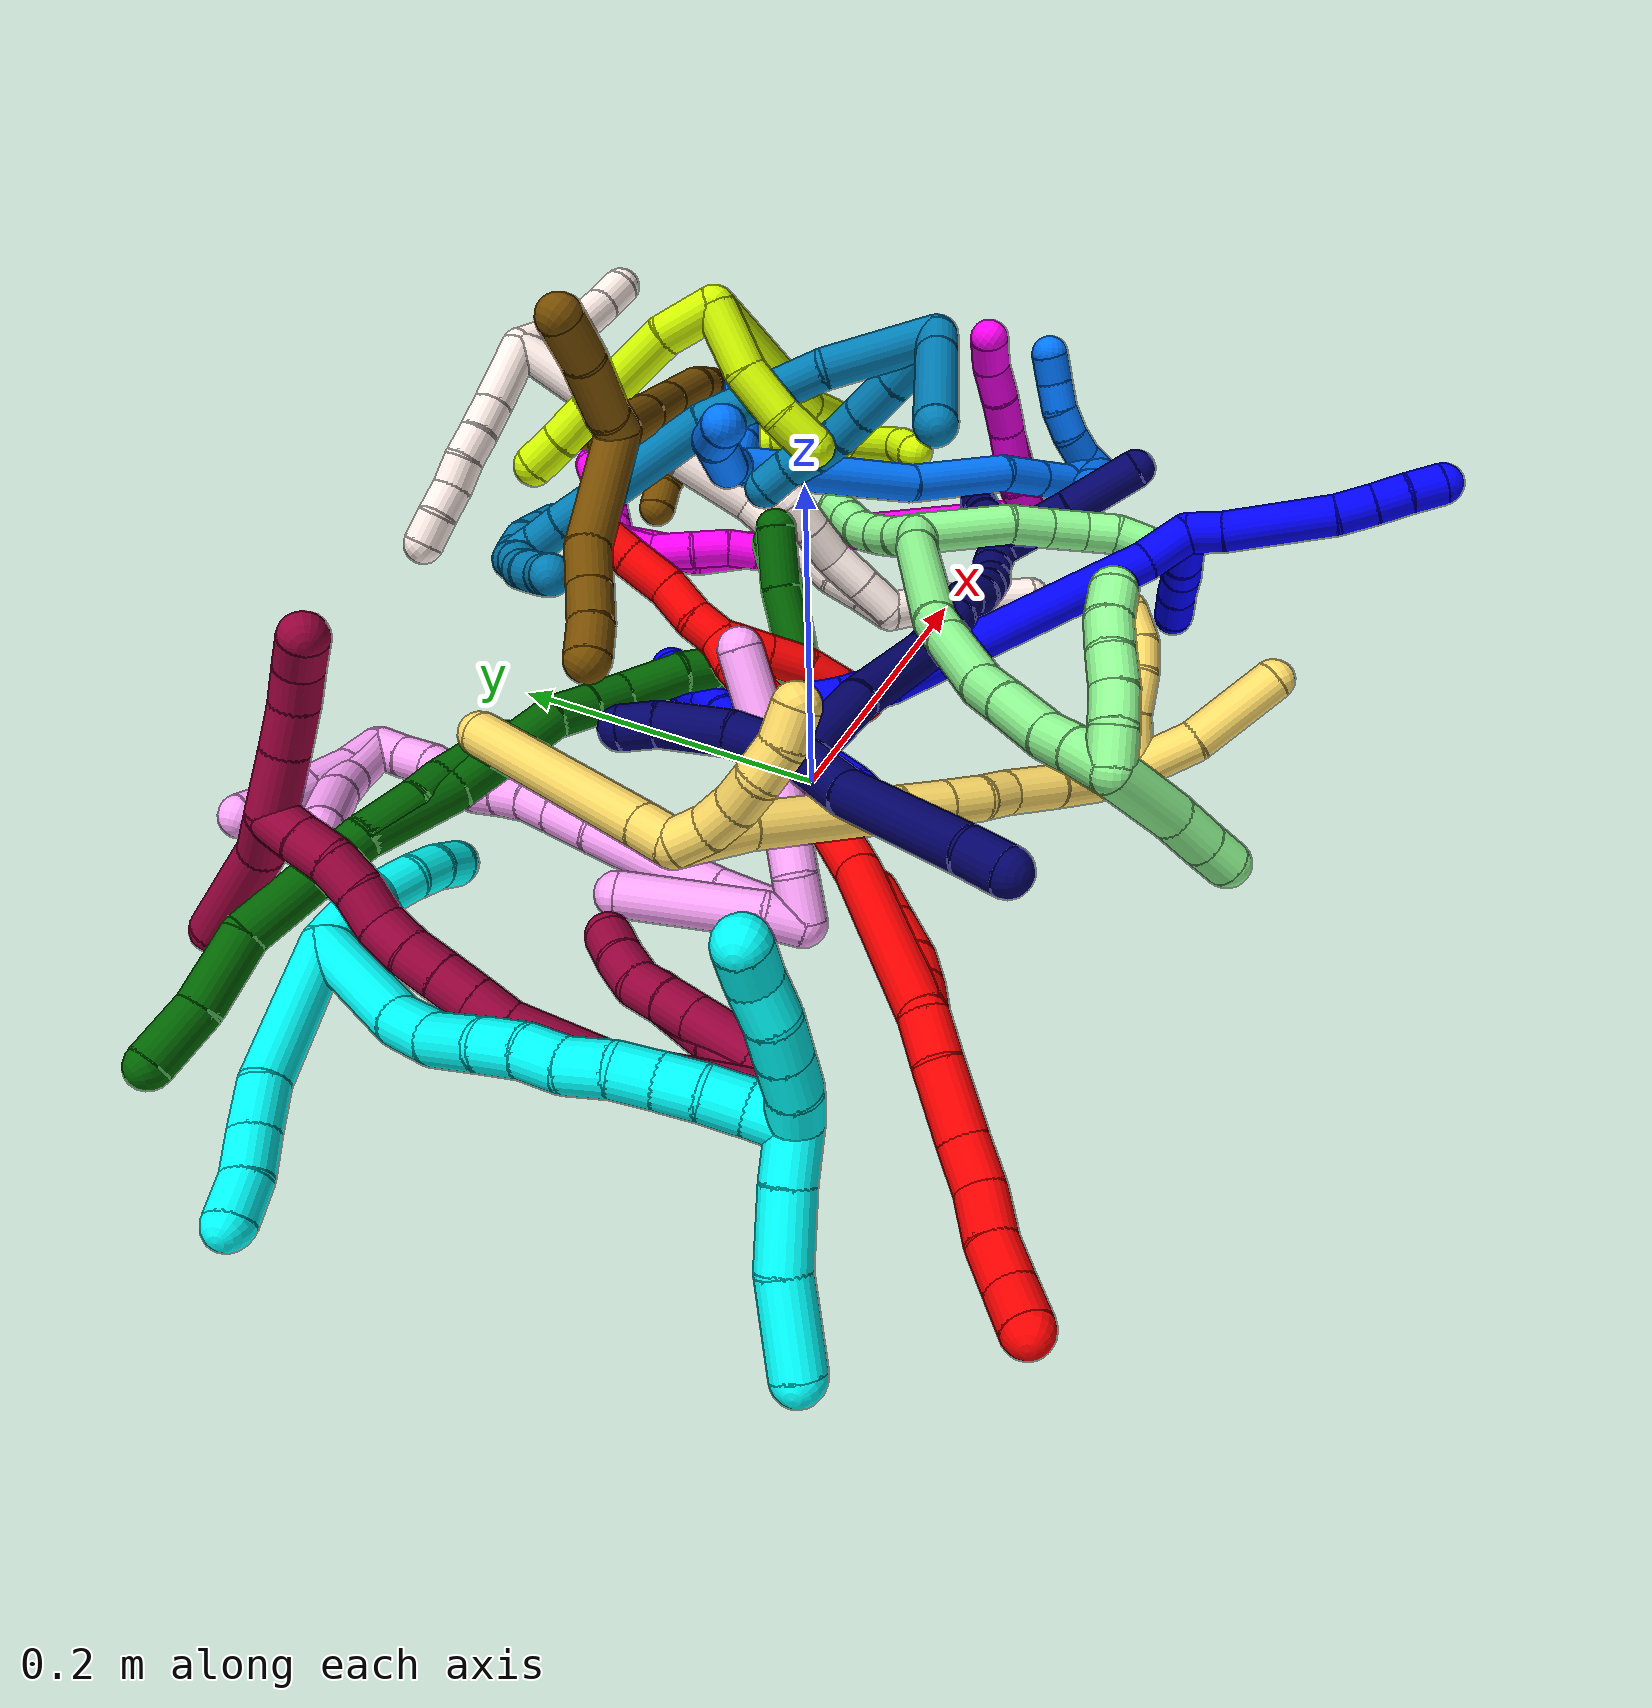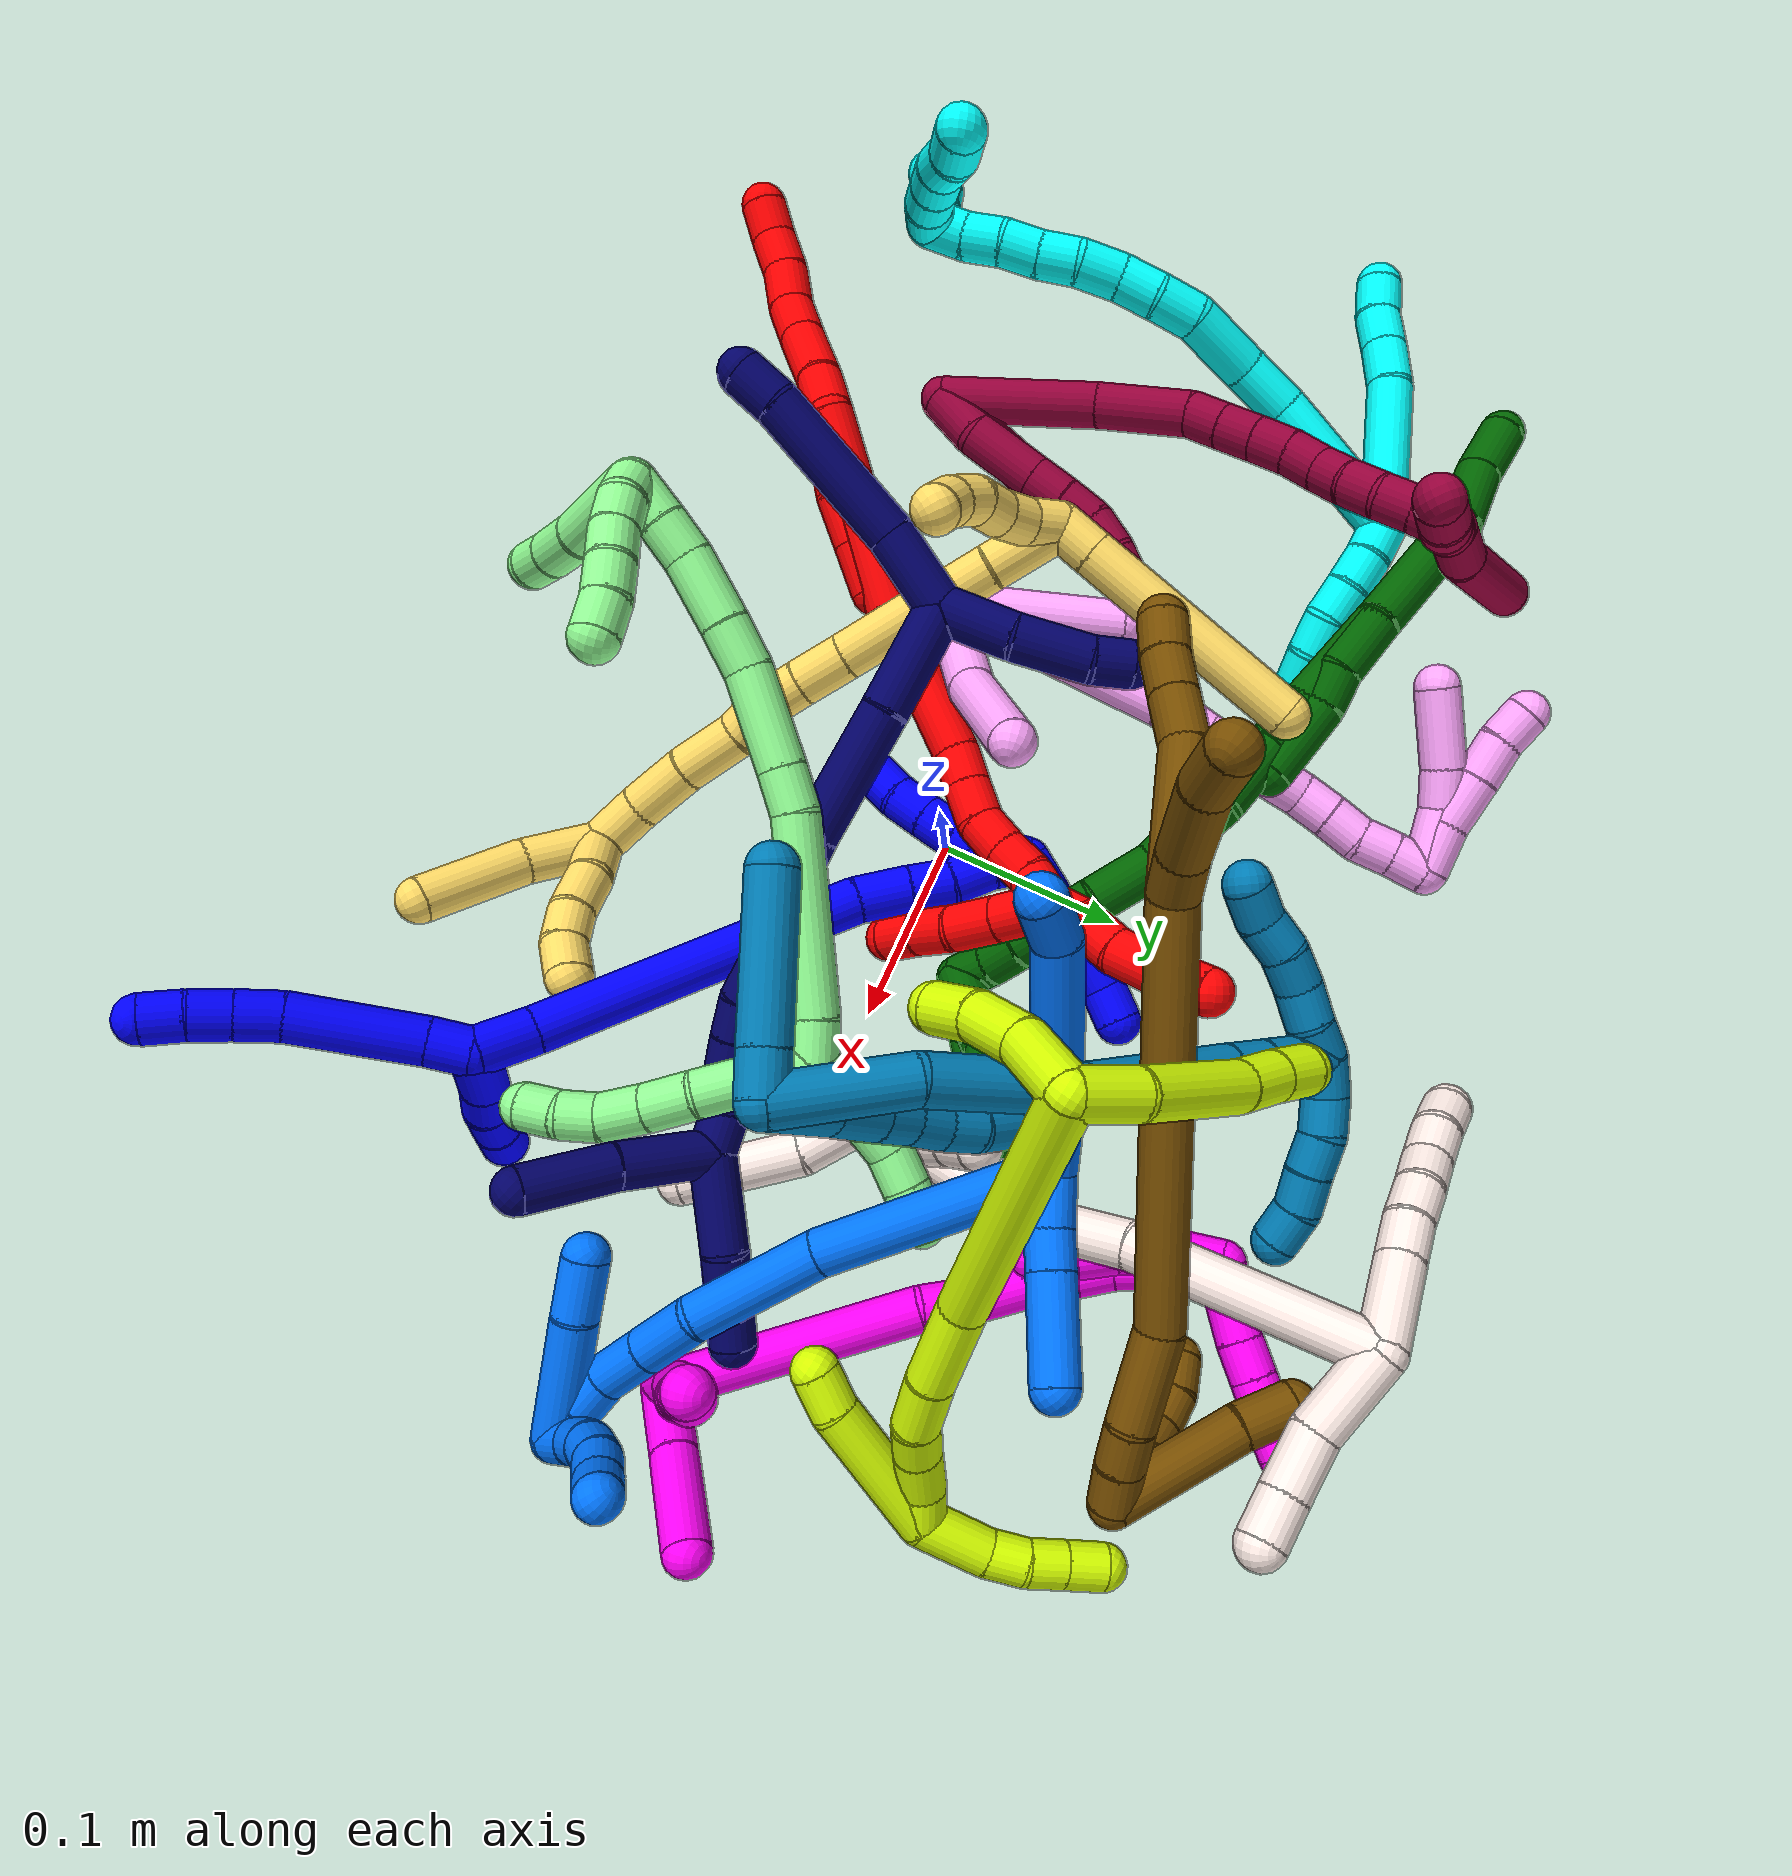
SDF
<sdf version="1.7">
 <world name="default">
  <plugin name="TubeGeneratorPlugin" filename="libtube_generator_plugin.so"/>
  <model name="photoneo_s_sensor">
   <static>1</static>
   <pose>0 0 2 1.57079 1.57079 3.14159</pose>
   <link name="link">
    <inertial><mass>0.1</mass></inertial>
    <sensor name="sensor" type="depth">
     <update_rate>30</update_rate>
     <camera>
      <horizontal_fov>1.22</horizontal_fov>
      <image><width>1920</width><height>1200</height><format>B8G8R8</format></image>
      <clip><near>0.1</near><far>4</far></clip>
      <depth_camera><output>points</output></depth_camera>
     </camera>
     <plugin name="camera_plugin" filename="libgazebo_ros_depth_camera.so">
      <baseline>0.2</baseline>
      <alwaysOn>1</alwaysOn>
      <updateRate>0.0</updateRate>
      <cameraName>camera_ir</cameraName>
      <imageTopicName>/camera/color/image_raw</imageTopicName>
      <cameraInfoTopicName>/camera/color/camera_info</cameraInfoTopicName>
      <depthImageTopicName>/camera/depth/image_raw</depthImageTopicName>
      <depthImageCameraInfoTopicName>/camera/depth/camera_info</depthImageCameraInfoTopicName>
      <pointCloudTopicName>/camera/depth/points</pointCloudTopicName>
      <frameName>fr_optical</frameName>
      <pointCloudCutoff>0.1</pointCloudCutoff>
      <pointCloudCutoffMax>2.0</pointCloudCutoffMax>
      <distortionK1>0</distortionK1>
      <distortionK2>0</distortionK2>
      <distortionK3>0</distortionK3>
      <distortionT1>0</distortionT1>
      <distortionT2>0</distortionT2>
      <CxPrime>0</CxPrime>
      <Cx>0</Cx>
      <Cy>0</Cy>
      <focalLength>0</focalLength>
      <hackBaseline>0</hackBaseline>
     </plugin>
    </sensor>
   </link>
  </model>
  <gravity>0 0 -9.8</gravity>
  <magnetic_field>6e-06 2.3e-05 -4.2e-05</magnetic_field>
  <atmosphere type="adiabatic"/>
  <physics name="default_physics" default="0" type="ode">
   <max_step_size>0.003</max_step_size>
   <real_time_factor>1</real_time_factor>
   <real_time_update_rate>1000</real_time_update_rate>
   <max_contacts>10000</max_contacts>
   <ode>
    <solver>
     <type>quick</type>
     <iters>100</iters>
     <sor>1.3</sor>
     <use_dynamic_moi_rescaling>0</use_dynamic_moi_rescaling>
    </solver>
    <constraints>
     <contact_max_correcting_vel>0</contact_max_correcting_vel>
     <contact_surface_layer>0.001</contact_surface_layer>
     <cfm>0</cfm>
     <erp>0.2</erp>
    </constraints>
   </ode>
  </physics>
  <scene><ambient>0.4 0.4 0.4 1</ambient><background>0.7 0.7 0.7 1</background><shadows>0</shadows></scene>
  <audio><device>default</device></audio>
  <spherical_coordinates>
   <surface_model>EARTH_WGS84</surface_model>
   <latitude_deg>0</latitude_deg>
   <longitude_deg>0</longitude_deg>
   <elevation>0</elevation>
   <heading_deg>0</heading_deg>
  </spherical_coordinates>
  <model name="bin">
   <static>1</static>
   <link name="bottom">
    <collision name="collision-bottom">
     <pose>0 0 -0.01 0 -0 0</pose>
     <geometry><box><size>0.8 0.6 0.02</size></box></geometry>
     <surface>
      <friction><ode><mu>100</mu><mu2>100</mu2></ode></friction>
      <contact><collide_bitmask>65535</collide_bitmask></contact>
     </surface>
    </collision>
   </link>
   <link name="west_wall">
    <collision name="collision-west_wall">
     <pose>-0.41 0 0.1 0 -0 0</pose>
     <geometry><box><size>0.02 0.6 0.2</size></box></geometry>
     <surface>
      <friction><ode><mu>100</mu><mu2>100</mu2></ode></friction>
      <contact><collide_bitmask>65535</collide_bitmask></contact>
     </surface>
    </collision>
   </link>
   <link name="east_wall">
    <collision name="collision-east_wall">
     <pose>0.41 0 0.1 0 -0 0</pose>
     <geometry><box><size>0.02 0.6 0.2</size></box></geometry>
     <surface>
      <friction><ode><mu>100</mu><mu2>100</mu2></ode></friction>
      <contact><collide_bitmask>65535</collide_bitmask></contact>
     </surface>
    </collision>
   </link>
   <link name="south_wall">
    <collision name="collision-south_wall">
     <pose>0 -0.31 0.1 0 -0 0</pose>
     <geometry><box><size>0.8 0.02 0.2</size></box></geometry>
     <surface>
      <friction><ode><mu>100</mu><mu2>100</mu2></ode></friction>
      <contact><collide_bitmask>65535</collide_bitmask></contact>
     </surface>
    </collision>
   </link>
   <link name="north_wall">
    <collision name="collision-north_wall">
     <pose>0 0.31 0.1 0 -0 0</pose>
     <geometry><box><size>0.8 0.02 0.2</size></box></geometry>
     <surface>
      <friction><ode><mu>100</mu><mu2>100</mu2></ode></friction>
      <contact><collide_bitmask>65535</collide_bitmask></contact>
     </surface>
    </collision>
   </link>
  </model>
  <model name="1">
   <static>0</static>
   <link name="1">
    <collision name="collision-cylinder-e_1_2_8">
     <pose>0.001305 -0.009234 0.005534 1.03089 0.120667 0.068418</pose>
     <geometry><cylinder><radius>0.0125</radius><length>0.021689</length></cylinder></geometry>
     <surface>
      <friction><ode><mu>1.16</mu><mu2>1.16</mu2><slip1>0</slip1><slip2>0</slip2></ode></friction>
      <contact><ode><kp>1e+06</kp><kd>1</kd><max_vel>0</max_vel><min_depth>0.001</min_depth></ode></contact>
     </surface>
    </collision>
    <visual name="visual-cylinder-e_1_2_8">
     <pose>0.001305 -0.009234 0.005534 1.03089 0.120667 0.068418</pose>
     <geometry><cylinder><radius>0.0125</radius><length>0.021689</length></cylinder></geometry>
     <material><ambient>0 0 1 1</ambient></material>
    </visual>
    <collision name="collision-cylinder-e_2_8_9">
     <pose>0.006985 -0.044337 0.031205 0.909339 0.132644 0.064912</pose>
     <geometry><cylinder><radius>0.0125</radius><length>0.066146</length></cylinder></geometry>
     <surface>
      <friction><ode><mu>1.16</mu><mu2>1.16</mu2><slip1>0</slip1><slip2>0</slip2></ode></friction>
      <contact><ode><kp>1e+06</kp><kd>1</kd><max_vel>0</max_vel><min_depth>0.001</min_depth></ode></contact>
     </surface>
    </collision>
    <visual name="visual-cylinder-e_2_8_9">
     <pose>0.006985 -0.044337 0.031205 0.909339 0.132644 0.064912</pose>
     <geometry><cylinder><radius>0.0125</radius><length>0.066146</length></cylinder></geometry>
     <material><ambient>0 0 1 1</ambient></material>
    </visual>
    <collision name="collision-cylinder-e_3_9_10">
     <pose>0.013999 -0.077799 0.058963 0.783666 0.240669 0.099844</pose>
     <geometry><cylinder><radius>0.0125</radius><length>0.022154</length></cylinder></geometry>
     <surface>
      <friction><ode><mu>1.16</mu><mu2>1.16</mu2><slip1>0</slip1><slip2>0</slip2></ode></friction>
      <contact><ode><kp>1e+06</kp><kd>1</kd><max_vel>0</max_vel><min_depth>0.001</min_depth></ode></contact>
     </surface>
    </collision>
    <visual name="visual-cylinder-e_3_9_10">
     <pose>0.013999 -0.077799 0.058963 0.783666 0.240669 0.099844</pose>
     <geometry><cylinder><radius>0.0125</radius><length>0.022154</length></cylinder></geometry>
     <material><ambient>0 0 1 1</ambient></material>
    </visual>
    <collision name="collision-cylinder-e_4_10_11">
     <pose>0.019254 -0.091938 0.073684 0.744673 0.264354 0.103757</pose>
     <geometry><cylinder><radius>0.0125</radius><length>0.02001</length></cylinder></geometry>
     <surface>
      <friction><ode><mu>1.16</mu><mu2>1.16</mu2><slip1>0</slip1><slip2>0</slip2></ode></friction>
      <contact><ode><kp>1e+06</kp><kd>1</kd><max_vel>0</max_vel><min_depth>0.001</min_depth></ode></contact>
     </surface>
    </collision>
    <visual name="visual-cylinder-e_4_10_11">
     <pose>0.019254 -0.091938 0.073684 0.744673 0.264354 0.103757</pose>
     <geometry><cylinder><radius>0.0125</radius><length>0.02001</length></cylinder></geometry>
     <material><ambient>0 0 1 1</ambient></material>
    </visual>
    <collision name="collision-cylinder-e_5_11_6">
     <pose>0.025584 -0.105127 0.087271 0.797461 0.380741 0.162016</pose>
     <geometry><cylinder><radius>0.0125</radius><length>0.020001</length></cylinder></geometry>
     <surface>
      <friction><ode><mu>1.16</mu><mu2>1.16</mu2><slip1>0</slip1><slip2>0</slip2></ode></friction>
      <contact><ode><kp>1e+06</kp><kd>1</kd><max_vel>0</max_vel><min_depth>0.001</min_depth></ode></contact>
     </surface>
    </collision>
    <visual name="visual-cylinder-e_5_11_6">
     <pose>0.025584 -0.105127 0.087271 0.797461 0.380741 0.162016</pose>
     <geometry><cylinder><radius>0.0125</radius><length>0.020001</length></cylinder></geometry>
     <material><ambient>0 0 1 1</ambient></material>
    </visual>
    <collision name="collision-cylinder-e_1_2_12">
     <pose>0.012089 -0.001299 -0.011102 3.02511 0.824532 2.87649</pose>
     <geometry><cylinder><radius>0.0125</radius><length>0.03293</length></cylinder></geometry>
     <surface>
      <friction><ode><mu>1.16</mu><mu2>1.16</mu2><slip1>0</slip1><slip2>0</slip2></ode></friction>
      <contact><ode><kp>1e+06</kp><kd>1</kd><max_vel>0</max_vel><min_depth>0.001</min_depth></ode></contact>
     </surface>
    </collision>
    <visual name="visual-cylinder-e_1_2_12">
     <pose>0.012089 -0.001299 -0.011102 3.02511 0.824532 2.87649</pose>
     <geometry><cylinder><radius>0.0125</radius><length>0.03293</length></cylinder></geometry>
     <material><ambient>0 0 1 1</ambient></material>
    </visual>
    <collision name="collision-cylinder-e_2_12_13">
     <pose>0.032558 -0.003347 -0.028069 3.01454 0.956394 2.89736</pose>
     <geometry><cylinder><radius>0.0125</radius><length>0.020511</length></cylinder></geometry>
     <surface>
      <friction><ode><mu>1.16</mu><mu2>1.16</mu2><slip1>0</slip1><slip2>0</slip2></ode></friction>
      <contact><ode><kp>1e+06</kp><kd>1</kd><max_vel>0</max_vel><min_depth>0.001</min_depth></ode></contact>
     </surface>
    </collision>
    <visual name="visual-cylinder-e_2_12_13">
     <pose>0.032558 -0.003347 -0.028069 3.01454 0.956394 2.89736</pose>
     <geometry><cylinder><radius>0.0125</radius><length>0.020511</length></cylinder></geometry>
     <material><ambient>0 0 1 1</ambient></material>
    </visual>
    <collision name="collision-cylinder-e_3_13_14">
     <pose>0.048721 -0.004708 -0.042088 3.0667 0.760684 2.95472</pose>
     <geometry><cylinder><radius>0.0125</radius><length>0.022579</length></cylinder></geometry>
     <surface>
      <friction><ode><mu>1.16</mu><mu2>1.16</mu2><slip1>0</slip1><slip2>0</slip2></ode></friction>
      <contact><ode><kp>1e+06</kp><kd>1</kd><max_vel>0</max_vel><min_depth>0.001</min_depth></ode></contact>
     </surface>
    </collision>
    <visual name="visual-cylinder-e_3_13_14">
     <pose>0.048721 -0.004708 -0.042088 3.0667 0.760684 2.95472</pose>
     <geometry><cylinder><radius>0.0125</radius><length>0.022579</length></cylinder></geometry>
     <material><ambient>0 0 1 1</ambient></material>
    </visual>
    <collision name="collision-cylinder-e_4_14_5">
     <pose>0.064304 -0.007004 -0.059192 2.95567 0.708294 2.64759</pose>
     <geometry><cylinder><radius>0.0125</radius><length>0.02398</length></cylinder></geometry>
     <surface>
      <friction><ode><mu>1.16</mu><mu2>1.16</mu2><slip1>0</slip1><slip2>0</slip2></ode></friction>
      <contact><ode><kp>1e+06</kp><kd>1</kd><max_vel>0</max_vel><min_depth>0.001</min_depth></ode></contact>
     </surface>
    </collision>
    <visual name="visual-cylinder-e_4_14_5">
     <pose>0.064304 -0.007004 -0.059192 2.95567 0.708294 2.64759</pose>
     <geometry><cylinder><radius>0.0125</radius><length>0.02398</length></cylinder></geometry>
     <material><ambient>0 0 1 1</ambient></material>
    </visual>
    <collision name="collision-cylinder-e_1_2_15">
     <pose>-0.007276 0.005912 -0.012429 -2.69764 -0.486306 1.66515</pose>
     <geometry><cylinder><radius>0.0125</radius><length>0.031137</length></cylinder></geometry>
     <surface>
      <friction><ode><mu>1.16</mu><mu2>1.16</mu2><slip1>0</slip1><slip2>0</slip2></ode></friction>
      <contact><ode><kp>1e+06</kp><kd>1</kd><max_vel>0</max_vel><min_depth>0.001</min_depth></ode></contact>
     </surface>
    </collision>
    <visual name="visual-cylinder-e_1_2_15">
     <pose>-0.007276 0.005912 -0.012429 -2.69764 -0.486306 1.66515</pose>
     <geometry><cylinder><radius>0.0125</radius><length>0.031137</length></cylinder></geometry>
     <material><ambient>0 0 1 1</ambient></material>
    </visual>
    <collision name="collision-cylinder-e_2_15_16">
     <pose>-0.066562 0.051884 -0.082434 -2.53369 -0.638038 1.62243</pose>
     <geometry><cylinder><radius>0.0125</radius><length>0.17464</length></cylinder></geometry>
     <surface>
      <friction><ode><mu>1.16</mu><mu2>1.16</mu2><slip1>0</slip1><slip2>0</slip2></ode></friction>
      <contact><ode><kp>1e+06</kp><kd>1</kd><max_vel>0</max_vel><min_depth>0.001</min_depth></ode></contact>
     </surface>
    </collision>
    <visual name="visual-cylinder-e_2_15_16">
     <pose>-0.066562 0.051884 -0.082434 -2.53369 -0.638038 1.62243</pose>
     <geometry><cylinder><radius>0.0125</radius><length>0.17464</length></cylinder></geometry>
     <material><ambient>0 0 1 1</ambient></material>
    </visual>
    <collision name="collision-cylinder-e_3_16_17">
     <pose>-0.12596 0.10092 -0.148532 -2.33034 -0.538194 1.14175</pose>
     <geometry><cylinder><radius>0.0125</radius><length>0.028827</length></cylinder></geometry>
     <surface>
      <friction><ode><mu>1.16</mu><mu2>1.16</mu2><slip1>0</slip1><slip2>0</slip2></ode></friction>
      <contact><ode><kp>1e+06</kp><kd>1</kd><max_vel>0</max_vel><min_depth>0.001</min_depth></ode></contact>
     </surface>
    </collision>
    <visual name="visual-cylinder-e_3_16_17">
     <pose>-0.12596 0.10092 -0.148532 -2.33034 -0.538194 1.14175</pose>
     <geometry><cylinder><radius>0.0125</radius><length>0.028827</length></cylinder></geometry>
     <material><ambient>0 0 1 1</ambient></material>
    </visual>
    <collision name="collision-cylinder-e_4_17_18">
     <pose>-0.138856 0.117462 -0.163111 -2.24582 -0.516686 1.00568</pose>
     <geometry><cylinder><radius>0.0125</radius><length>0.022298</length></cylinder></geometry>
     <surface>
      <friction><ode><mu>1.16</mu><mu2>1.16</mu2><slip1>0</slip1><slip2>0</slip2></ode></friction>
      <contact><ode><kp>1e+06</kp><kd>1</kd><max_vel>0</max_vel><min_depth>0.001</min_depth></ode></contact>
     </surface>
    </collision>
    <visual name="visual-cylinder-e_4_17_18">
     <pose>-0.138856 0.117462 -0.163111 -2.24582 -0.516686 1.00568</pose>
     <geometry><cylinder><radius>0.0125</radius><length>0.022298</length></cylinder></geometry>
     <material><ambient>0 0 1 1</ambient></material>
    </visual>
    <collision name="collision-cylinder-e_5_18_19">
     <pose>-0.151127 0.130726 -0.175375 -2.399 -0.676491 1.46944</pose>
     <geometry><cylinder><radius>0.0125</radius><length>0.021605</length></cylinder></geometry>
     <surface>
      <friction><ode><mu>1.16</mu><mu2>1.16</mu2><slip1>0</slip1><slip2>0</slip2></ode></friction>
      <contact><ode><kp>1e+06</kp><kd>1</kd><max_vel>0</max_vel><min_depth>0.001</min_depth></ode></contact>
     </surface>
    </collision>
    <visual name="visual-cylinder-e_5_18_19">
     <pose>-0.151127 0.130726 -0.175375 -2.399 -0.676491 1.46944</pose>
     <geometry><cylinder><radius>0.0125</radius><length>0.021605</length></cylinder></geometry>
     <material><ambient>0 0 1 1</ambient></material>
    </visual>
    <collision name="collision-cylinder-e_6_19_1">
     <pose>-0.162502 0.142322 -0.189287 -2.48818 -0.443641 1.1745</pose>
     <geometry><cylinder><radius>0.0125</radius><length>0.021491</length></cylinder></geometry>
     <surface>
      <friction><ode><mu>1.16</mu><mu2>1.16</mu2><slip1>0</slip1><slip2>0</slip2></ode></friction>
      <contact><ode><kp>1e+06</kp><kd>1</kd><max_vel>0</max_vel><min_depth>0.001</min_depth></ode></contact>
     </surface>
    </collision>
    <visual name="visual-cylinder-e_6_19_1">
     <pose>-0.162502 0.142322 -0.189287 -2.48818 -0.443641 1.1745</pose>
     <geometry><cylinder><radius>0.0125</radius><length>0.021491</length></cylinder></geometry>
     <material><ambient>0 0 1 1</ambient></material>
    </visual>
    <collision name="collision-cylinder-e_1_1_20">
     <pose>-0.161843 0.156694 -0.197657 -1.64896 0.555214 -0.597847</pose>
     <geometry><cylinder><radius>0.0125</radius><length>0.02</length></cylinder></geometry>
     <surface>
      <friction><ode><mu>1.16</mu><mu2>1.16</mu2><slip1>0</slip1><slip2>0</slip2></ode></friction>
      <contact><ode><kp>1e+06</kp><kd>1</kd><max_vel>0</max_vel><min_depth>0.001</min_depth></ode></contact>
     </surface>
    </collision>
    <visual name="visual-cylinder-e_1_1_20">
     <pose>-0.161843 0.156694 -0.197657 -1.64896 0.555214 -0.597847</pose>
     <geometry><cylinder><radius>0.0125</radius><length>0.02</length></cylinder></geometry>
     <material><ambient>0 0 1 1</ambient></material>
    </visual>
    <collision name="collision-cylinder-e_2_20_21">
     <pose>-0.150631 0.173059 -0.199869 -1.76451 0.636236 -0.761319</pose>
     <geometry><cylinder><radius>0.0125</radius><length>0.02</length></cylinder></geometry>
     <surface>
      <friction><ode><mu>1.16</mu><mu2>1.16</mu2><slip1>0</slip1><slip2>0</slip2></ode></friction>
      <contact><ode><kp>1e+06</kp><kd>1</kd><max_vel>0</max_vel><min_depth>0.001</min_depth></ode></contact>
     </surface>
    </collision>
    <visual name="visual-cylinder-e_2_20_21">
     <pose>-0.150631 0.173059 -0.199869 -1.76451 0.636236 -0.761319</pose>
     <geometry><cylinder><radius>0.0125</radius><length>0.02</length></cylinder></geometry>
     <material><ambient>0 0 1 1</ambient></material>
    </visual>
    <collision name="collision-cylinder-e_3_21_22">
     <pose>-0.139245 0.188147 -0.20573 -2.11078 0.575683 -0.963192</pose>
     <geometry><cylinder><radius>0.0125</radius><length>0.02</length></cylinder></geometry>
     <surface>
      <friction><ode><mu>1.16</mu><mu2>1.16</mu2><slip1>0</slip1><slip2>0</slip2></ode></friction>
      <contact><ode><kp>1e+06</kp><kd>1</kd><max_vel>0</max_vel><min_depth>0.001</min_depth></ode></contact>
     </surface>
    </collision>
    <visual name="visual-cylinder-e_3_21_22">
     <pose>-0.139245 0.188147 -0.20573 -2.11078 0.575683 -0.963192</pose>
     <geometry><cylinder><radius>0.0125</radius><length>0.02</length></cylinder></geometry>
     <material><ambient>0 0 1 1</ambient></material>
    </visual>
    <collision name="collision-cylinder-e_4_22_23">
     <pose>-0.127746 0.203018 -0.212142 -1.8378 0.650365 -0.831959</pose>
     <geometry><cylinder><radius>0.0125</radius><length>0.02</length></cylinder></geometry>
     <surface>
      <friction><ode><mu>1.16</mu><mu2>1.16</mu2><slip1>0</slip1><slip2>0</slip2></ode></friction>
      <contact><ode><kp>1e+06</kp><kd>1</kd><max_vel>0</max_vel><min_depth>0.001</min_depth></ode></contact>
     </surface>
    </collision>
    <visual name="visual-cylinder-e_4_22_23">
     <pose>-0.127746 0.203018 -0.212142 -1.8378 0.650365 -0.831959</pose>
     <geometry><cylinder><radius>0.0125</radius><length>0.02</length></cylinder></geometry>
     <material><ambient>0 0 1 1</ambient></material>
    </visual>
    <collision name="collision-cylinder-e_5_23_4">
     <pose>-0.11552 0.218563 -0.214167 -1.56132 0.665042 -0.659217</pose>
     <geometry><cylinder><radius>0.0125</radius><length>0.02</length></cylinder></geometry>
     <surface>
      <friction><ode><mu>1.16</mu><mu2>1.16</mu2><slip1>0</slip1><slip2>0</slip2></ode></friction>
      <contact><ode><kp>1e+06</kp><kd>1</kd><max_vel>0</max_vel><min_depth>0.001</min_depth></ode></contact>
     </surface>
    </collision>
    <visual name="visual-cylinder-e_5_23_4">
     <pose>-0.11552 0.218563 -0.214167 -1.56132 0.665042 -0.659217</pose>
     <geometry><cylinder><radius>0.0125</radius><length>0.02</length></cylinder></geometry>
     <material><ambient>0 0 1 1</ambient></material>
    </visual>
    <collision name="collision-cylinder-e_1_1_24">
     <pose>-0.165448 0.139135 -0.193167 1.17224 0.167486 0.111348</pose>
     <geometry><cylinder><radius>0.0125</radius><length>0.02</length></cylinder></geometry>
     <surface>
      <friction><ode><mu>1.16</mu><mu2>1.16</mu2><slip1>0</slip1><slip2>0</slip2></ode></friction>
      <contact><ode><kp>1e+06</kp><kd>1</kd><max_vel>0</max_vel><min_depth>0.001</min_depth></ode></contact>
     </surface>
    </collision>
    <visual name="visual-cylinder-e_1_1_24">
     <pose>-0.165448 0.139135 -0.193167 1.17224 0.167486 0.111348</pose>
     <geometry><cylinder><radius>0.0125</radius><length>0.02</length></cylinder></geometry>
     <material><ambient>0 0 1 1</ambient></material>
    </visual>
    <collision name="collision-cylinder-e_2_24_25">
     <pose>-0.162912 0.120144 -0.18826 1.46216 0.08694 0.077983</pose>
     <geometry><cylinder><radius>0.0125</radius><length>0.02</length></cylinder></geometry>
     <surface>
      <friction><ode><mu>1.16</mu><mu2>1.16</mu2><slip1>0</slip1><slip2>0</slip2></ode></friction>
      <contact><ode><kp>1e+06</kp><kd>1</kd><max_vel>0</max_vel><min_depth>0.001</min_depth></ode></contact>
     </surface>
    </collision>
    <visual name="visual-cylinder-e_2_24_25">
     <pose>-0.162912 0.120144 -0.18826 1.46216 0.08694 0.077983</pose>
     <geometry><cylinder><radius>0.0125</radius><length>0.02</length></cylinder></geometry>
     <material><ambient>0 0 1 1</ambient></material>
    </visual>
    <collision name="collision-cylinder-e_3_25_26">
     <pose>-0.163123 0.10031 -0.186717 1.52418 -0.10806 -0.103145</pose>
     <geometry><cylinder><radius>0.0125</radius><length>0.02</length></cylinder></geometry>
     <surface>
      <friction><ode><mu>1.16</mu><mu2>1.16</mu2><slip1>0</slip1><slip2>0</slip2></ode></friction>
      <contact><ode><kp>1e+06</kp><kd>1</kd><max_vel>0</max_vel><min_depth>0.001</min_depth></ode></contact>
     </surface>
    </collision>
    <visual name="visual-cylinder-e_3_25_26">
     <pose>-0.163123 0.10031 -0.186717 1.52418 -0.10806 -0.103145</pose>
     <geometry><cylinder><radius>0.0125</radius><length>0.02</length></cylinder></geometry>
     <material><ambient>0 0 1 1</ambient></material>
    </visual>
    <collision name="collision-cylinder-e_4_26_27">
     <pose>-0.165404 0.08046 -0.185838 1.52899 -0.12063 -0.115701</pose>
     <geometry><cylinder><radius>0.0125</radius><length>0.02</length></cylinder></geometry>
     <surface>
      <friction><ode><mu>1.16</mu><mu2>1.16</mu2><slip1>0</slip1><slip2>0</slip2></ode></friction>
      <contact><ode><kp>1e+06</kp><kd>1</kd><max_vel>0</max_vel><min_depth>0.001</min_depth></ode></contact>
     </surface>
    </collision>
    <visual name="visual-cylinder-e_4_26_27">
     <pose>-0.165404 0.08046 -0.185838 1.52899 -0.12063 -0.115701</pose>
     <geometry><cylinder><radius>0.0125</radius><length>0.02</length></cylinder></geometry>
     <material><ambient>0 0 1 1</ambient></material>
    </visual>
    <collision name="collision-cylinder-e_5_27_3">
     <pose>-0.168834 0.060847 -0.186454 1.67671 -0.224484 -0.249369</pose>
     <geometry><cylinder><radius>0.0125</radius><length>0.02</length></cylinder></geometry>
     <surface>
      <friction><ode><mu>1.16</mu><mu2>1.16</mu2><slip1>0</slip1><slip2>0</slip2></ode></friction>
      <contact><ode><kp>1e+06</kp><kd>1</kd><max_vel>0</max_vel><min_depth>0.001</min_depth></ode></contact>
     </surface>
    </collision>
    <visual name="visual-cylinder-e_5_27_3">
     <pose>-0.168834 0.060847 -0.186454 1.67671 -0.224484 -0.249369</pose>
     <geometry><cylinder><radius>0.0125</radius><length>0.02</length></cylinder></geometry>
     <material><ambient>0 0 1 1</ambient></material>
    </visual>
    <collision name="collision-sphere-3">
     <pose>-0.17106 0.051153 -0.187485 0 -0 0</pose>
     <geometry><sphere><radius>0.0125</radius></sphere></geometry>
     <surface>
      <friction><ode><mu>1.16</mu><mu2>1.16</mu2><slip1>0</slip1><slip2>0</slip2></ode></friction>
      <contact><ode><kp>1e+06</kp><kd>1</kd><max_vel>0</max_vel><min_depth>0.001</min_depth></ode></contact>
     </surface>
    </collision>
    <visual name="visual-sphere-3">
     <pose>-0.17106 0.051153 -0.187485 0 -0 0</pose>
     <geometry><sphere><radius>0.0125</radius></sphere></geometry>
     <material><ambient>0 0 1 1</ambient></material>
    </visual>
    <collision name="collision-sphere-27">
     <pose>-0.166608 0.070542 -0.185423 0 -0 0</pose>
     <geometry><sphere><radius>0.0125</radius></sphere></geometry>
     <surface>
      <friction><ode><mu>1.16</mu><mu2>1.16</mu2><slip1>0</slip1><slip2>0</slip2></ode></friction>
      <contact><ode><kp>1e+06</kp><kd>1</kd><max_vel>0</max_vel><min_depth>0.001</min_depth></ode></contact>
     </surface>
    </collision>
    <visual name="visual-sphere-27">
     <pose>-0.166608 0.070542 -0.185423 0 -0 0</pose>
     <geometry><sphere><radius>0.0125</radius></sphere></geometry>
     <material><ambient>0 0 1 1</ambient></material>
    </visual>
    <collision name="collision-sphere-26">
     <pose>-0.164201 0.090379 -0.186253 0 -0 0</pose>
     <geometry><sphere><radius>0.0125</radius></sphere></geometry>
     <surface>
      <friction><ode><mu>1.16</mu><mu2>1.16</mu2><slip1>0</slip1><slip2>0</slip2></ode></friction>
      <contact><ode><kp>1e+06</kp><kd>1</kd><max_vel>0</max_vel><min_depth>0.001</min_depth></ode></contact>
     </surface>
    </collision>
    <visual name="visual-sphere-26">
     <pose>-0.164201 0.090379 -0.186253 0 -0 0</pose>
     <geometry><sphere><radius>0.0125</radius></sphere></geometry>
     <material><ambient>0 0 1 1</ambient></material>
    </visual>
    <collision name="collision-sphere-25">
     <pose>-0.162044 0.110241 -0.18718 0 -0 0</pose>
     <geometry><sphere><radius>0.0125</radius></sphere></geometry>
     <surface>
      <friction><ode><mu>1.16</mu><mu2>1.16</mu2><slip1>0</slip1><slip2>0</slip2></ode></friction>
      <contact><ode><kp>1e+06</kp><kd>1</kd><max_vel>0</max_vel><min_depth>0.001</min_depth></ode></contact>
     </surface>
    </collision>
    <visual name="visual-sphere-25">
     <pose>-0.162044 0.110241 -0.18718 0 -0 0</pose>
     <geometry><sphere><radius>0.0125</radius></sphere></geometry>
     <material><ambient>0 0 1 1</ambient></material>
    </visual>
    <collision name="collision-sphere-24">
     <pose>-0.163781 0.130048 -0.18934 0 -0 0</pose>
     <geometry><sphere><radius>0.0125</radius></sphere></geometry>
     <surface>
      <friction><ode><mu>1.16</mu><mu2>1.16</mu2><slip1>0</slip1><slip2>0</slip2></ode></friction>
      <contact><ode><kp>1e+06</kp><kd>1</kd><max_vel>0</max_vel><min_depth>0.001</min_depth></ode></contact>
     </surface>
    </collision>
    <visual name="visual-sphere-24">
     <pose>-0.163781 0.130048 -0.18934 0 -0 0</pose>
     <geometry><sphere><radius>0.0125</radius></sphere></geometry>
     <material><ambient>0 0 1 1</ambient></material>
    </visual>
    <collision name="collision-sphere-4">
     <pose>-0.109349 0.226432 -0.214093 0 -0 0</pose>
     <geometry><sphere><radius>0.0125</radius></sphere></geometry>
     <surface>
      <friction><ode><mu>1.16</mu><mu2>1.16</mu2><slip1>0</slip1><slip2>0</slip2></ode></friction>
      <contact><ode><kp>1e+06</kp><kd>1</kd><max_vel>0</max_vel><min_depth>0.001</min_depth></ode></contact>
     </surface>
    </collision>
    <visual name="visual-sphere-4">
     <pose>-0.109349 0.226432 -0.214093 0 -0 0</pose>
     <geometry><sphere><radius>0.0125</radius></sphere></geometry>
     <material><ambient>0 0 1 1</ambient></material>
    </visual>
    <collision name="collision-sphere-23">
     <pose>-0.121691 0.210695 -0.214242 0 -0 0</pose>
     <geometry><sphere><radius>0.0125</radius></sphere></geometry>
     <surface>
      <friction><ode><mu>1.16</mu><mu2>1.16</mu2><slip1>0</slip1><slip2>0</slip2></ode></friction>
      <contact><ode><kp>1e+06</kp><kd>1</kd><max_vel>0</max_vel><min_depth>0.001</min_depth></ode></contact>
     </surface>
    </collision>
    <visual name="visual-sphere-23">
     <pose>-0.121691 0.210695 -0.214242 0 -0 0</pose>
     <geometry><sphere><radius>0.0125</radius></sphere></geometry>
     <material><ambient>0 0 1 1</ambient></material>
    </visual>
    <collision name="collision-sphere-22">
     <pose>-0.133801 0.195341 -0.210042 0 -0 0</pose>
     <geometry><sphere><radius>0.0125</radius></sphere></geometry>
     <surface>
      <friction><ode><mu>1.16</mu><mu2>1.16</mu2><slip1>0</slip1><slip2>0</slip2></ode></friction>
      <contact><ode><kp>1e+06</kp><kd>1</kd><max_vel>0</max_vel><min_depth>0.001</min_depth></ode></contact>
     </surface>
    </collision>
    <visual name="visual-sphere-22">
     <pose>-0.133801 0.195341 -0.210042 0 -0 0</pose>
     <geometry><sphere><radius>0.0125</radius></sphere></geometry>
     <material><ambient>0 0 1 1</ambient></material>
    </visual>
    <collision name="collision-sphere-21">
     <pose>-0.144689 0.180952 -0.201417 0 -0 0</pose>
     <geometry><sphere><radius>0.0125</radius></sphere></geometry>
     <surface>
      <friction><ode><mu>1.16</mu><mu2>1.16</mu2><slip1>0</slip1><slip2>0</slip2></ode></friction>
      <contact><ode><kp>1e+06</kp><kd>1</kd><max_vel>0</max_vel><min_depth>0.001</min_depth></ode></contact>
     </surface>
    </collision>
    <visual name="visual-sphere-21">
     <pose>-0.144689 0.180952 -0.201417 0 -0 0</pose>
     <geometry><sphere><radius>0.0125</radius></sphere></geometry>
     <material><ambient>0 0 1 1</ambient></material>
    </visual>
    <collision name="collision-sphere-20">
     <pose>-0.156572 0.165166 -0.198321 0 -0 0</pose>
     <geometry><sphere><radius>0.0125</radius></sphere></geometry>
     <surface>
      <friction><ode><mu>1.16</mu><mu2>1.16</mu2><slip1>0</slip1><slip2>0</slip2></ode></friction>
      <contact><ode><kp>1e+06</kp><kd>1</kd><max_vel>0</max_vel><min_depth>0.001</min_depth></ode></contact>
     </surface>
    </collision>
    <visual name="visual-sphere-20">
     <pose>-0.156572 0.165166 -0.198321 0 -0 0</pose>
     <geometry><sphere><radius>0.0125</radius></sphere></geometry>
     <material><ambient>0 0 1 1</ambient></material>
    </visual>
    <collision name="collision-sphere-6">
     <pose>0.0293 -0.111771 0.093756 0 -0 0</pose>
     <geometry><sphere><radius>0.0125</radius></sphere></geometry>
     <surface>
      <friction><ode><mu>1.16</mu><mu2>1.16</mu2><slip1>0</slip1><slip2>0</slip2></ode></friction>
      <contact><ode><kp>1e+06</kp><kd>1</kd><max_vel>0</max_vel><min_depth>0.001</min_depth></ode></contact>
     </surface>
    </collision>
    <visual name="visual-sphere-6">
     <pose>0.0293 -0.111771 0.093756 0 -0 0</pose>
     <geometry><sphere><radius>0.0125</radius></sphere></geometry>
     <material><ambient>0 0 1 1</ambient></material>
    </visual>
    <collision name="collision-sphere-11">
     <pose>0.021868 -0.098483 0.080785 0 -0 0</pose>
     <geometry><sphere><radius>0.0125</radius></sphere></geometry>
     <surface>
      <friction><ode><mu>1.16</mu><mu2>1.16</mu2><slip1>0</slip1><slip2>0</slip2></ode></friction>
      <contact><ode><kp>1e+06</kp><kd>1</kd><max_vel>0</max_vel><min_depth>0.001</min_depth></ode></contact>
     </surface>
    </collision>
    <visual name="visual-sphere-11">
     <pose>0.021868 -0.098483 0.080785 0 -0 0</pose>
     <geometry><sphere><radius>0.0125</radius></sphere></geometry>
     <material><ambient>0 0 1 1</ambient></material>
    </visual>
    <collision name="collision-sphere-10">
     <pose>0.016639 -0.085393 0.066583 0 -0 0</pose>
     <geometry><sphere><radius>0.0125</radius></sphere></geometry>
     <surface>
      <friction><ode><mu>1.16</mu><mu2>1.16</mu2><slip1>0</slip1><slip2>0</slip2></ode></friction>
      <contact><ode><kp>1e+06</kp><kd>1</kd><max_vel>0</max_vel><min_depth>0.001</min_depth></ode></contact>
     </surface>
    </collision>
    <visual name="visual-sphere-10">
     <pose>0.016639 -0.085393 0.066583 0 -0 0</pose>
     <geometry><sphere><radius>0.0125</radius></sphere></geometry>
     <material><ambient>0 0 1 1</ambient></material>
    </visual>
    <collision name="collision-sphere-9">
     <pose>0.011359 -0.070206 0.051342 0 -0 0</pose>
     <geometry><sphere><radius>0.0125</radius></sphere></geometry>
     <surface>
      <friction><ode><mu>1.16</mu><mu2>1.16</mu2><slip1>0</slip1><slip2>0</slip2></ode></friction>
      <contact><ode><kp>1e+06</kp><kd>1</kd><max_vel>0</max_vel><min_depth>0.001</min_depth></ode></contact>
     </surface>
    </collision>
    <visual name="visual-sphere-9">
     <pose>0.011359 -0.070206 0.051342 0 -0 0</pose>
     <geometry><sphere><radius>0.0125</radius></sphere></geometry>
     <material><ambient>0 0 1 1</ambient></material>
    </visual>
    <collision name="collision-sphere-2">
     <geometry><sphere><radius>0.0125</radius></sphere></geometry>
     <surface>
      <friction><ode><mu>1.16</mu><mu2>1.16</mu2><slip1>0</slip1><slip2>0</slip2></ode></friction>
      <contact><ode><kp>1e+06</kp><kd>1</kd><max_vel>0</max_vel><min_depth>0.001</min_depth></ode></contact>
     </surface>
    </collision>
    <visual name="visual-sphere-2">
     <geometry><sphere><radius>0.0125</radius></sphere></geometry>
     <material><ambient>0 0 1 1</ambient></material>
    </visual>
    <collision name="collision-sphere-19">
     <pose>-0.15789 0.136422 -0.181581 0 -0 0</pose>
     <geometry><sphere><radius>0.0125</radius></sphere></geometry>
     <surface>
      <friction><ode><mu>1.16</mu><mu2>1.16</mu2><slip1>0</slip1><slip2>0</slip2></ode></friction>
      <contact><ode><kp>1e+06</kp><kd>1</kd><max_vel>0</max_vel><min_depth>0.001</min_depth></ode></contact>
     </surface>
    </collision>
    <visual name="visual-sphere-19">
     <pose>-0.15789 0.136422 -0.181581 0 -0 0</pose>
     <geometry><sphere><radius>0.0125</radius></sphere></geometry>
     <material><ambient>0 0 1 1</ambient></material>
    </visual>
    <collision name="collision-sphere-8">
     <pose>0.002611 -0.018469 0.011068 0 -0 0</pose>
     <geometry><sphere><radius>0.0125</radius></sphere></geometry>
     <surface>
      <friction><ode><mu>1.16</mu><mu2>1.16</mu2><slip1>0</slip1><slip2>0</slip2></ode></friction>
      <contact><ode><kp>1e+06</kp><kd>1</kd><max_vel>0</max_vel><min_depth>0.001</min_depth></ode></contact>
     </surface>
    </collision>
    <visual name="visual-sphere-8">
     <pose>0.002611 -0.018469 0.011068 0 -0 0</pose>
     <geometry><sphere><radius>0.0125</radius></sphere></geometry>
     <material><ambient>0 0 1 1</ambient></material>
    </visual>
    <collision name="collision-sphere-12">
     <pose>0.024178 -0.002598 -0.022204 0 -0 0</pose>
     <geometry><sphere><radius>0.0125</radius></sphere></geometry>
     <surface>
      <friction><ode><mu>1.16</mu><mu2>1.16</mu2><slip1>0</slip1><slip2>0</slip2></ode></friction>
      <contact><ode><kp>1e+06</kp><kd>1</kd><max_vel>0</max_vel><min_depth>0.001</min_depth></ode></contact>
     </surface>
    </collision>
    <visual name="visual-sphere-12">
     <pose>0.024178 -0.002598 -0.022204 0 -0 0</pose>
     <geometry><sphere><radius>0.0125</radius></sphere></geometry>
     <material><ambient>0 0 1 1</ambient></material>
    </visual>
    <collision name="collision-sphere-13">
     <pose>0.040938 -0.004097 -0.033933 0 -0 0</pose>
     <geometry><sphere><radius>0.0125</radius></sphere></geometry>
     <surface>
      <friction><ode><mu>1.16</mu><mu2>1.16</mu2><slip1>0</slip1><slip2>0</slip2></ode></friction>
      <contact><ode><kp>1e+06</kp><kd>1</kd><max_vel>0</max_vel><min_depth>0.001</min_depth></ode></contact>
     </surface>
    </collision>
    <visual name="visual-sphere-13">
     <pose>0.040938 -0.004097 -0.033933 0 -0 0</pose>
     <geometry><sphere><radius>0.0125</radius></sphere></geometry>
     <material><ambient>0 0 1 1</ambient></material>
    </visual>
    <collision name="collision-sphere-14">
     <pose>0.056504 -0.00532 -0.050243 0 -0 0</pose>
     <geometry><sphere><radius>0.0125</radius></sphere></geometry>
     <surface>
      <friction><ode><mu>1.16</mu><mu2>1.16</mu2><slip1>0</slip1><slip2>0</slip2></ode></friction>
      <contact><ode><kp>1e+06</kp><kd>1</kd><max_vel>0</max_vel><min_depth>0.001</min_depth></ode></contact>
     </surface>
    </collision>
    <visual name="visual-sphere-14">
     <pose>0.056504 -0.00532 -0.050243 0 -0 0</pose>
     <geometry><sphere><radius>0.0125</radius></sphere></geometry>
     <material><ambient>0 0 1 1</ambient></material>
    </visual>
    <collision name="collision-sphere-5">
     <pose>0.072104 -0.008687 -0.068141 0 -0 0</pose>
     <geometry><sphere><radius>0.0125</radius></sphere></geometry>
     <surface>
      <friction><ode><mu>1.16</mu><mu2>1.16</mu2><slip1>0</slip1><slip2>0</slip2></ode></friction>
      <contact><ode><kp>1e+06</kp><kd>1</kd><max_vel>0</max_vel><min_depth>0.001</min_depth></ode></contact>
     </surface>
    </collision>
    <visual name="visual-sphere-5">
     <pose>0.072104 -0.008687 -0.068141 0 -0 0</pose>
     <geometry><sphere><radius>0.0125</radius></sphere></geometry>
     <material><ambient>0 0 1 1</ambient></material>
    </visual>
    <collision name="collision-sphere-15">
     <pose>-0.014552 0.011823 -0.024859 0 -0 0</pose>
     <geometry><sphere><radius>0.0125</radius></sphere></geometry>
     <surface>
      <friction><ode><mu>1.16</mu><mu2>1.16</mu2><slip1>0</slip1><slip2>0</slip2></ode></friction>
      <contact><ode><kp>1e+06</kp><kd>1</kd><max_vel>0</max_vel><min_depth>0.001</min_depth></ode></contact>
     </surface>
    </collision>
    <visual name="visual-sphere-15">
     <pose>-0.014552 0.011823 -0.024859 0 -0 0</pose>
     <geometry><sphere><radius>0.0125</radius></sphere></geometry>
     <material><ambient>0 0 1 1</ambient></material>
    </visual>
    <collision name="collision-sphere-16">
     <pose>-0.118572 0.091946 -0.14001 0 -0 0</pose>
     <geometry><sphere><radius>0.0125</radius></sphere></geometry>
     <surface>
      <friction><ode><mu>1.16</mu><mu2>1.16</mu2><slip1>0</slip1><slip2>0</slip2></ode></friction>
      <contact><ode><kp>1e+06</kp><kd>1</kd><max_vel>0</max_vel><min_depth>0.001</min_depth></ode></contact>
     </surface>
    </collision>
    <visual name="visual-sphere-16">
     <pose>-0.118572 0.091946 -0.14001 0 -0 0</pose>
     <geometry><sphere><radius>0.0125</radius></sphere></geometry>
     <material><ambient>0 0 1 1</ambient></material>
    </visual>
    <collision name="collision-sphere-17">
     <pose>-0.133348 0.109894 -0.157054 0 -0 0</pose>
     <geometry><sphere><radius>0.0125</radius></sphere></geometry>
     <surface>
      <friction><ode><mu>1.16</mu><mu2>1.16</mu2><slip1>0</slip1><slip2>0</slip2></ode></friction>
      <contact><ode><kp>1e+06</kp><kd>1</kd><max_vel>0</max_vel><min_depth>0.001</min_depth></ode></contact>
     </surface>
    </collision>
    <visual name="visual-sphere-17">
     <pose>-0.133348 0.109894 -0.157054 0 -0 0</pose>
     <geometry><sphere><radius>0.0125</radius></sphere></geometry>
     <material><ambient>0 0 1 1</ambient></material>
    </visual>
    <collision name="collision-sphere-18">
     <pose>-0.144364 0.12503 -0.169169 0 -0 0</pose>
     <geometry><sphere><radius>0.0125</radius></sphere></geometry>
     <surface>
      <friction><ode><mu>1.16</mu><mu2>1.16</mu2><slip1>0</slip1><slip2>0</slip2></ode></friction>
      <contact><ode><kp>1e+06</kp><kd>1</kd><max_vel>0</max_vel><min_depth>0.001</min_depth></ode></contact>
     </surface>
    </collision>
    <visual name="visual-sphere-18">
     <pose>-0.144364 0.12503 -0.169169 0 -0 0</pose>
     <geometry><sphere><radius>0.0125</radius></sphere></geometry>
     <material><ambient>0 0 1 1</ambient></material>
    </visual>
    <collision name="collision-sphere-1">
     <pose>-0.167115 0.148222 -0.196993 0 -0 0</pose>
     <geometry><sphere><radius>0.0125</radius></sphere></geometry>
     <surface>
      <friction><ode><mu>1.16</mu><mu2>1.16</mu2><slip1>0</slip1><slip2>0</slip2></ode></friction>
      <contact><ode><kp>1e+06</kp><kd>1</kd><max_vel>0</max_vel><min_depth>0.001</min_depth></ode></contact>
     </surface>
    </collision>
    <visual name="visual-sphere-1">
     <pose>-0.167115 0.148222 -0.196993 0 -0 0</pose>
     <geometry><sphere><radius>0.0125</radius></sphere></geometry>
     <material><ambient>0 0 1 1</ambient></material>
    </visual>
    <inertial>
     <pose>-0.067126 0.053706 -0.088747 0 -0 0</pose>
     <mass>0.75</mass>
     <inertia>
      <ixx>0.000391</ixx>
      <ixy>0</ixy>
      <ixz>0</ixz>
      <iyy>0.000579</iyy>
      <iyz>0</iyz>
      <izz>5.9e-05</izz>
     </inertia>
    </inertial>
   </link>
   <pose>0.200525 -0.156029 0.101109 0.290104 0.385666 -0.009926</pose>
  </model>
  <model name="2">
   <static>0</static>
   <link name="2">
    <collision name="collision-cylinder-e_1_2_8">
     <pose>-0.00651 -0.002785 0.00963 0.281483 -0.575955 -0.083884</pose>
     <geometry><cylinder><radius>0.0125</radius><length>0.023907</length></cylinder></geometry>
     <surface>
      <friction><ode><mu>1.16</mu><mu2>1.16</mu2><slip1>0</slip1><slip2>0</slip2></ode></friction>
      <contact><ode><kp>1e+06</kp><kd>1</kd><max_vel>0</max_vel><min_depth>0.001</min_depth></ode></contact>
     </surface>
    </collision>
    <visual name="visual-cylinder-e_1_2_8">
     <pose>-0.00651 -0.002785 0.00963 0.281483 -0.575955 -0.083884</pose>
     <geometry><cylinder><radius>0.0125</radius><length>0.023907</length></cylinder></geometry>
     <material><ambient>1 0 0 1</ambient></material>
    </visual>
    <collision name="collision-cylinder-e_2_8_9">
     <pose>-0.025005 -0.010102 0.03224 0.335969 -0.716947 -0.126902</pose>
     <geometry><cylinder><radius>0.0125</radius><length>0.036477</length></cylinder></geometry>
     <surface>
      <friction><ode><mu>1.16</mu><mu2>1.16</mu2><slip1>0</slip1><slip2>0</slip2></ode></friction>
      <contact><ode><kp>1e+06</kp><kd>1</kd><max_vel>0</max_vel><min_depth>0.001</min_depth></ode></contact>
     </surface>
    </collision>
    <visual name="visual-cylinder-e_2_8_9">
     <pose>-0.025005 -0.010102 0.03224 0.335969 -0.716947 -0.126902</pose>
     <geometry><cylinder><radius>0.0125</radius><length>0.036477</length></cylinder></geometry>
     <material><ambient>1 0 0 1</ambient></material>
    </visual>
    <collision name="collision-cylinder-e_3_9_10">
     <pose>-0.043184 -0.017877 0.054629 0.331852 -0.556808 -0.09566</pose>
     <geometry><cylinder><radius>0.0125</radius><length>0.023446</length></cylinder></geometry>
     <surface>
      <friction><ode><mu>1.16</mu><mu2>1.16</mu2><slip1>0</slip1><slip2>0</slip2></ode></friction>
      <contact><ode><kp>1e+06</kp><kd>1</kd><max_vel>0</max_vel><min_depth>0.001</min_depth></ode></contact>
     </surface>
    </collision>
    <visual name="visual-cylinder-e_3_9_10">
     <pose>-0.043184 -0.017877 0.054629 0.331852 -0.556808 -0.09566</pose>
     <geometry><cylinder><radius>0.0125</radius><length>0.023446</length></cylinder></geometry>
     <material><ambient>1 0 0 1</ambient></material>
    </visual>
    <collision name="collision-cylinder-e_4_10_11">
     <pose>-0.054057 -0.023021 0.074951 0.172485 -0.399577 -0.03501</pose>
     <geometry><cylinder><radius>0.0125</radius><length>0.024048</length></cylinder></geometry>
     <surface>
      <friction><ode><mu>1.16</mu><mu2>1.16</mu2><slip1>0</slip1><slip2>0</slip2></ode></friction>
      <contact><ode><kp>1e+06</kp><kd>1</kd><max_vel>0</max_vel><min_depth>0.001</min_depth></ode></contact>
     </surface>
    </collision>
    <visual name="visual-cylinder-e_4_10_11">
     <pose>-0.054057 -0.023021 0.074951 0.172485 -0.399577 -0.03501</pose>
     <geometry><cylinder><radius>0.0125</radius><length>0.024048</length></cylinder></geometry>
     <material><ambient>1 0 0 1</ambient></material>
    </visual>
    <collision name="collision-cylinder-e_5_11_12">
     <pose>-0.062679 -0.028384 0.095446 0.346692 -0.369351 -0.065397</pose>
     <geometry><cylinder><radius>0.0125</radius><length>0.021852</length></cylinder></geometry>
     <surface>
      <friction><ode><mu>1.16</mu><mu2>1.16</mu2><slip1>0</slip1><slip2>0</slip2></ode></friction>
      <contact><ode><kp>1e+06</kp><kd>1</kd><max_vel>0</max_vel><min_depth>0.001</min_depth></ode></contact>
     </surface>
    </collision>
    <visual name="visual-cylinder-e_5_11_12">
     <pose>-0.062679 -0.028384 0.095446 0.346692 -0.369351 -0.065397</pose>
     <geometry><cylinder><radius>0.0125</radius><length>0.021852</length></cylinder></geometry>
     <material><ambient>1 0 0 1</ambient></material>
    </visual>
    <collision name="collision-cylinder-e_6_12_6">
     <pose>-0.068507 -0.034954 0.114491 0.317368 -0.18695 -0.030003</pose>
     <geometry><cylinder><radius>0.0125</radius><length>0.020271</length></cylinder></geometry>
     <surface>
      <friction><ode><mu>1.16</mu><mu2>1.16</mu2><slip1>0</slip1><slip2>0</slip2></ode></friction>
      <contact><ode><kp>1e+06</kp><kd>1</kd><max_vel>0</max_vel><min_depth>0.001</min_depth></ode></contact>
     </surface>
    </collision>
    <visual name="visual-cylinder-e_6_12_6">
     <pose>-0.068507 -0.034954 0.114491 0.317368 -0.18695 -0.030003</pose>
     <geometry><cylinder><radius>0.0125</radius><length>0.020271</length></cylinder></geometry>
     <material><ambient>1 0 0 1</ambient></material>
    </visual>
    <collision name="collision-cylinder-e_1_2_13">
     <pose>-0.00082 0.001346 -0.012068 -3.03054 -0.067434 1.09085</pose>
     <geometry><cylinder><radius>0.0125</radius><length>0.024341</length></cylinder></geometry>
     <surface>
      <friction><ode><mu>1.16</mu><mu2>1.16</mu2><slip1>0</slip1><slip2>0</slip2></ode></friction>
      <contact><ode><kp>1e+06</kp><kd>1</kd><max_vel>0</max_vel><min_depth>0.001</min_depth></ode></contact>
     </surface>
    </collision>
    <visual name="visual-cylinder-e_1_2_13">
     <pose>-0.00082 0.001346 -0.012068 -3.03054 -0.067434 1.09085</pose>
     <geometry><cylinder><radius>0.0125</radius><length>0.024341</length></cylinder></geometry>
     <material><ambient>1 0 0 1</ambient></material>
    </visual>
    <collision name="collision-cylinder-e_2_13_14">
     <pose>-6.9e-05 0.004779 -0.033826 -2.92936 0.157228 -1.27358</pose>
     <geometry><cylinder><radius>0.0125</radius><length>0.020072</length></cylinder></geometry>
     <surface>
      <friction><ode><mu>1.16</mu><mu2>1.16</mu2><slip1>0</slip1><slip2>0</slip2></ode></friction>
      <contact><ode><kp>1e+06</kp><kd>1</kd><max_vel>0</max_vel><min_depth>0.001</min_depth></ode></contact>
     </surface>
    </collision>
    <visual name="visual-cylinder-e_2_13_14">
     <pose>-6.9e-05 0.004779 -0.033826 -2.92936 0.157228 -1.27358</pose>
     <geometry><cylinder><radius>0.0125</radius><length>0.020072</length></cylinder></geometry>
     <material><ambient>1 0 0 1</ambient></material>
    </visual>
    <collision name="collision-cylinder-e_3_14_15">
     <pose>0.003797 0.011955 -0.056218 -2.76062 0.166157 -0.815297</pose>
     <geometry><cylinder><radius>0.0125</radius><length>0.02775</length></cylinder></geometry>
     <surface>
      <friction><ode><mu>1.16</mu><mu2>1.16</mu2><slip1>0</slip1><slip2>0</slip2></ode></friction>
      <contact><ode><kp>1e+06</kp><kd>1</kd><max_vel>0</max_vel><min_depth>0.001</min_depth></ode></contact>
     </surface>
    </collision>
    <visual name="visual-cylinder-e_3_14_15">
     <pose>0.003797 0.011955 -0.056218 -2.76062 0.166157 -0.815297</pose>
     <geometry><cylinder><radius>0.0125</radius><length>0.02775</length></cylinder></geometry>
     <material><ambient>1 0 0 1</ambient></material>
    </visual>
    <collision name="collision-cylinder-e_4_15_5">
     <pose>0.008367 0.022081 -0.081695 -2.76596 0.164137 -0.816887</pose>
     <geometry><cylinder><radius>0.0125</radius><length>0.027838</length></cylinder></geometry>
     <surface>
      <friction><ode><mu>1.16</mu><mu2>1.16</mu2><slip1>0</slip1><slip2>0</slip2></ode></friction>
      <contact><ode><kp>1e+06</kp><kd>1</kd><max_vel>0</max_vel><min_depth>0.001</min_depth></ode></contact>
     </surface>
    </collision>
    <visual name="visual-cylinder-e_4_15_5">
     <pose>0.008367 0.022081 -0.081695 -2.76596 0.164137 -0.816887</pose>
     <geometry><cylinder><radius>0.0125</radius><length>0.027838</length></cylinder></geometry>
     <material><ambient>1 0 0 1</ambient></material>
    </visual>
    <collision name="collision-cylinder-e_1_2_16">
     <pose>0.008794 0.01739 -0.051825 -2.81784 0.15951 -0.910292</pose>
     <geometry><cylinder><radius>0.0125</radius><length>0.110735</length></cylinder></geometry>
     <surface>
      <friction><ode><mu>1.16</mu><mu2>1.16</mu2><slip1>0</slip1><slip2>0</slip2></ode></friction>
      <contact><ode><kp>1e+06</kp><kd>1</kd><max_vel>0</max_vel><min_depth>0.001</min_depth></ode></contact>
     </surface>
    </collision>
    <visual name="visual-cylinder-e_1_2_16">
     <pose>0.008794 0.01739 -0.051825 -2.81784 0.15951 -0.910292</pose>
     <geometry><cylinder><radius>0.0125</radius><length>0.110735</length></cylinder></geometry>
     <material><ambient>1 0 0 1</ambient></material>
    </visual>
    <collision name="collision-cylinder-e_2_16_17">
     <pose>0.022581 0.041897 -0.118173 -2.68598 0.299416 -1.15364</pose>
     <geometry><cylinder><radius>0.0125</radius><length>0.033851</length></cylinder></geometry>
     <surface>
      <friction><ode><mu>1.16</mu><mu2>1.16</mu2><slip1>0</slip1><slip2>0</slip2></ode></friction>
      <contact><ode><kp>1e+06</kp><kd>1</kd><max_vel>0</max_vel><min_depth>0.001</min_depth></ode></contact>
     </surface>
    </collision>
    <visual name="visual-cylinder-e_2_16_17">
     <pose>0.022581 0.041897 -0.118173 -2.68598 0.299416 -1.15364</pose>
     <geometry><cylinder><radius>0.0125</radius><length>0.033851</length></cylinder></geometry>
     <material><ambient>1 0 0 1</ambient></material>
    </visual>
    <collision name="collision-cylinder-e_3_17_18">
     <pose>0.035588 0.059978 -0.155178 -2.68782 0.310051 -1.19017</pose>
     <geometry><cylinder><radius>0.0125</radius><length>0.052534</length></cylinder></geometry>
     <surface>
      <friction><ode><mu>1.16</mu><mu2>1.16</mu2><slip1>0</slip1><slip2>0</slip2></ode></friction>
      <contact><ode><kp>1e+06</kp><kd>1</kd><max_vel>0</max_vel><min_depth>0.001</min_depth></ode></contact>
     </surface>
    </collision>
    <visual name="visual-cylinder-e_3_17_18">
     <pose>0.035588 0.059978 -0.155178 -2.68782 0.310051 -1.19017</pose>
     <geometry><cylinder><radius>0.0125</radius><length>0.052534</length></cylinder></geometry>
     <material><ambient>1 0 0 1</ambient></material>
    </visual>
    <collision name="collision-cylinder-e_4_18_19">
     <pose>0.047642 0.073843 -0.186478 -2.82388 0.410598 -1.83005</pose>
     <geometry><cylinder><radius>0.0125</radius><length>0.020245</length></cylinder></geometry>
     <surface>
      <friction><ode><mu>1.16</mu><mu2>1.16</mu2><slip1>0</slip1><slip2>0</slip2></ode></friction>
      <contact><ode><kp>1e+06</kp><kd>1</kd><max_vel>0</max_vel><min_depth>0.001</min_depth></ode></contact>
     </surface>
    </collision>
    <visual name="visual-cylinder-e_4_18_19">
     <pose>0.047642 0.073843 -0.186478 -2.82388 0.410598 -1.83005</pose>
     <geometry><cylinder><radius>0.0125</radius><length>0.020245</length></cylinder></geometry>
     <material><ambient>1 0 0 1</ambient></material>
    </visual>
    <collision name="collision-cylinder-e_5_19_20">
     <pose>0.056539 0.07997 -0.204409 -2.80118 0.465442 -1.8868</pose>
     <geometry><cylinder><radius>0.0125</radius><length>0.02164</length></cylinder></geometry>
     <surface>
      <friction><ode><mu>1.16</mu><mu2>1.16</mu2><slip1>0</slip1><slip2>0</slip2></ode></friction>
      <contact><ode><kp>1e+06</kp><kd>1</kd><max_vel>0</max_vel><min_depth>0.001</min_depth></ode></contact>
     </surface>
    </collision>
    <visual name="visual-cylinder-e_5_19_20">
     <pose>0.056539 0.07997 -0.204409 -2.80118 0.465442 -1.8868</pose>
     <geometry><cylinder><radius>0.0125</radius><length>0.02164</length></cylinder></geometry>
     <material><ambient>1 0 0 1</ambient></material>
    </visual>
    <collision name="collision-cylinder-e_6_20_21">
     <pose>0.066394 0.089153 -0.220258 -2.4177 0.507484 -1.20107</pose>
     <geometry><cylinder><radius>0.0125</radius><length>0.020574</length></cylinder></geometry>
     <surface>
      <friction><ode><mu>1.16</mu><mu2>1.16</mu2><slip1>0</slip1><slip2>0</slip2></ode></friction>
      <contact><ode><kp>1e+06</kp><kd>1</kd><max_vel>0</max_vel><min_depth>0.001</min_depth></ode></contact>
     </surface>
    </collision>
    <visual name="visual-cylinder-e_6_20_21">
     <pose>0.066394 0.089153 -0.220258 -2.4177 0.507484 -1.20107</pose>
     <geometry><cylinder><radius>0.0125</radius><length>0.020574</length></cylinder></geometry>
     <material><ambient>1 0 0 1</ambient></material>
    </visual>
    <collision name="collision-cylinder-e_7_21_22">
     <pose>0.077028 0.101144 -0.232873 -2.34291 0.589366 -1.247</pose>
     <geometry><cylinder><radius>0.0125</radius><length>0.020273</length></cylinder></geometry>
     <surface>
      <friction><ode><mu>1.16</mu><mu2>1.16</mu2><slip1>0</slip1><slip2>0</slip2></ode></friction>
      <contact><ode><kp>1e+06</kp><kd>1</kd><max_vel>0</max_vel><min_depth>0.001</min_depth></ode></contact>
     </surface>
    </collision>
    <visual name="visual-cylinder-e_7_21_22">
     <pose>0.077028 0.101144 -0.232873 -2.34291 0.589366 -1.247</pose>
     <geometry><cylinder><radius>0.0125</radius><length>0.020273</length></cylinder></geometry>
     <material><ambient>1 0 0 1</ambient></material>
    </visual>
    <collision name="collision-cylinder-e_8_22_1">
     <pose>0.088218 0.111534 -0.24594 -2.59715 0.584156 -1.64501</pose>
     <geometry><cylinder><radius>0.0125</radius><length>0.020149</length></cylinder></geometry>
     <surface>
      <friction><ode><mu>1.16</mu><mu2>1.16</mu2><slip1>0</slip1><slip2>0</slip2></ode></friction>
      <contact><ode><kp>1e+06</kp><kd>1</kd><max_vel>0</max_vel><min_depth>0.001</min_depth></ode></contact>
     </surface>
    </collision>
    <visual name="visual-cylinder-e_8_22_1">
     <pose>0.088218 0.111534 -0.24594 -2.59715 0.584156 -1.64501</pose>
     <geometry><cylinder><radius>0.0125</radius><length>0.020149</length></cylinder></geometry>
     <material><ambient>1 0 0 1</ambient></material>
    </visual>
    <collision name="collision-cylinder-e_1_1_23">
     <pose>0.099913 0.123103 -0.256356 -1.99126 0.660308 -0.972563</pose>
     <geometry><cylinder><radius>0.0125</radius><length>0.020019</length></cylinder></geometry>
     <surface>
      <friction><ode><mu>1.16</mu><mu2>1.16</mu2><slip1>0</slip1><slip2>0</slip2></ode></friction>
      <contact><ode><kp>1e+06</kp><kd>1</kd><max_vel>0</max_vel><min_depth>0.001</min_depth></ode></contact>
     </surface>
    </collision>
    <visual name="visual-cylinder-e_1_1_23">
     <pose>0.099913 0.123103 -0.256356 -1.99126 0.660308 -0.972563</pose>
     <geometry><cylinder><radius>0.0125</radius><length>0.020019</length></cylinder></geometry>
     <material><ambient>1 0 0 1</ambient></material>
    </visual>
    <collision name="collision-cylinder-e_2_23_24">
     <pose>0.114242 0.137691 -0.265911 -2.28025 0.700429 -1.34343</pose>
     <geometry><cylinder><radius>0.0125</radius><length>0.025413</length></cylinder></geometry>
     <surface>
      <friction><ode><mu>1.16</mu><mu2>1.16</mu2><slip1>0</slip1><slip2>0</slip2></ode></friction>
      <contact><ode><kp>1e+06</kp><kd>1</kd><max_vel>0</max_vel><min_depth>0.001</min_depth></ode></contact>
     </surface>
    </collision>
    <visual name="visual-cylinder-e_2_23_24">
     <pose>0.114242 0.137691 -0.265911 -2.28025 0.700429 -1.34343</pose>
     <geometry><cylinder><radius>0.0125</radius><length>0.025413</length></cylinder></geometry>
     <material><ambient>1 0 0 1</ambient></material>
    </visual>
    <collision name="collision-cylinder-e_3_24_25">
     <pose>0.131489 0.155747 -0.276659 -1.96296 0.664438 -0.952793</pose>
     <geometry><cylinder><radius>0.0125</radius><length>0.029375</length></cylinder></geometry>
     <surface>
      <friction><ode><mu>1.16</mu><mu2>1.16</mu2><slip1>0</slip1><slip2>0</slip2></ode></friction>
      <contact><ode><kp>1e+06</kp><kd>1</kd><max_vel>0</max_vel><min_depth>0.001</min_depth></ode></contact>
     </surface>
    </collision>
    <visual name="visual-cylinder-e_3_24_25">
     <pose>0.131489 0.155747 -0.276659 -1.96296 0.664438 -0.952793</pose>
     <geometry><cylinder><radius>0.0125</radius><length>0.029375</length></cylinder></geometry>
     <material><ambient>1 0 0 1</ambient></material>
    </visual>
    <collision name="collision-cylinder-e_4_25_4">
     <pose>0.14906 0.175212 -0.284093 -1.90162 0.742299 -0.998244</pose>
     <geometry><cylinder><radius>0.0125</radius><length>0.025193</length></cylinder></geometry>
     <surface>
      <friction><ode><mu>1.16</mu><mu2>1.16</mu2><slip1>0</slip1><slip2>0</slip2></ode></friction>
      <contact><ode><kp>1e+06</kp><kd>1</kd><max_vel>0</max_vel><min_depth>0.001</min_depth></ode></contact>
     </surface>
    </collision>
    <visual name="visual-cylinder-e_4_25_4">
     <pose>0.14906 0.175212 -0.284093 -1.90162 0.742299 -0.998244</pose>
     <geometry><cylinder><radius>0.0125</radius><length>0.025193</length></cylinder></geometry>
     <material><ambient>1 0 0 1</ambient></material>
    </visual>
    <collision name="collision-cylinder-e_1_1_26">
     <pose>0.085781 0.104132 -0.257423 1.92103 -0.568398 -0.791327</pose>
     <geometry><cylinder><radius>0.0125</radius><length>0.029697</length></cylinder></geometry>
     <surface>
      <friction><ode><mu>1.16</mu><mu2>1.16</mu2><slip1>0</slip1><slip2>0</slip2></ode></friction>
      <contact><ode><kp>1e+06</kp><kd>1</kd><max_vel>0</max_vel><min_depth>0.001</min_depth></ode></contact>
     </surface>
    </collision>
    <visual name="visual-cylinder-e_1_1_26">
     <pose>0.085781 0.104132 -0.257423 1.92103 -0.568398 -0.791327</pose>
     <geometry><cylinder><radius>0.0125</radius><length>0.029697</length></cylinder></geometry>
     <material><ambient>1 0 0 1</ambient></material>
    </visual>
    <collision name="collision-cylinder-e_2_26_27">
     <pose>0.070947 0.081838 -0.265206 1.89048 -0.552221 -0.74765</pose>
     <geometry><cylinder><radius>0.0125</radius><length>0.026083</length></cylinder></geometry>
     <surface>
      <friction><ode><mu>1.16</mu><mu2>1.16</mu2><slip1>0</slip1><slip2>0</slip2></ode></friction>
      <contact><ode><kp>1e+06</kp><kd>1</kd><max_vel>0</max_vel><min_depth>0.001</min_depth></ode></contact>
     </surface>
    </collision>
    <visual name="visual-cylinder-e_2_26_27">
     <pose>0.070947 0.081838 -0.265206 1.89048 -0.552221 -0.74765</pose>
     <geometry><cylinder><radius>0.0125</radius><length>0.026083</length></cylinder></geometry>
     <material><ambient>1 0 0 1</ambient></material>
    </visual>
    <collision name="collision-cylinder-e_3_27_28">
     <pose>0.056176 0.063337 -0.27059 1.80448 -0.769673 -0.947602</pose>
     <geometry><cylinder><radius>0.0125</radius><length>0.022789</length></cylinder></geometry>
     <surface>
      <friction><ode><mu>1.16</mu><mu2>1.16</mu2><slip1>0</slip1><slip2>0</slip2></ode></friction>
      <contact><ode><kp>1e+06</kp><kd>1</kd><max_vel>0</max_vel><min_depth>0.001</min_depth></ode></contact>
     </surface>
    </collision>
    <visual name="visual-cylinder-e_3_27_28">
     <pose>0.056176 0.063337 -0.27059 1.80448 -0.769673 -0.947602</pose>
     <geometry><cylinder><radius>0.0125</radius><length>0.022789</length></cylinder></geometry>
     <material><ambient>1 0 0 1</ambient></material>
    </visual>
    <collision name="collision-cylinder-e_4_28_3">
     <pose>0.040626 0.048248 -0.274923 1.9003 -0.791111 -1.05729</pose>
     <geometry><cylinder><radius>0.0125</radius><length>0.02143</length></cylinder></geometry>
     <surface>
      <friction><ode><mu>1.16</mu><mu2>1.16</mu2><slip1>0</slip1><slip2>0</slip2></ode></friction>
      <contact><ode><kp>1e+06</kp><kd>1</kd><max_vel>0</max_vel><min_depth>0.001</min_depth></ode></contact>
     </surface>
    </collision>
    <visual name="visual-cylinder-e_4_28_3">
     <pose>0.040626 0.048248 -0.274923 1.9003 -0.791111 -1.05729</pose>
     <geometry><cylinder><radius>0.0125</radius><length>0.02143</length></cylinder></geometry>
     <material><ambient>1 0 0 1</ambient></material>
    </visual>
    <collision name="collision-sphere-3">
     <pose>0.033006 0.04112 -0.27736 0 -0 0</pose>
     <geometry><sphere><radius>0.0125</radius></sphere></geometry>
     <surface>
      <friction><ode><mu>1.16</mu><mu2>1.16</mu2><slip1>0</slip1><slip2>0</slip2></ode></friction>
      <contact><ode><kp>1e+06</kp><kd>1</kd><max_vel>0</max_vel><min_depth>0.001</min_depth></ode></contact>
     </surface>
    </collision>
    <visual name="visual-sphere-3">
     <pose>0.033006 0.04112 -0.27736 0 -0 0</pose>
     <geometry><sphere><radius>0.0125</radius></sphere></geometry>
     <material><ambient>1 0 0 1</ambient></material>
    </visual>
    <collision name="collision-sphere-28">
     <pose>0.048246 0.055376 -0.272485 0 -0 0</pose>
     <geometry><sphere><radius>0.0125</radius></sphere></geometry>
     <surface>
      <friction><ode><mu>1.16</mu><mu2>1.16</mu2><slip1>0</slip1><slip2>0</slip2></ode></friction>
      <contact><ode><kp>1e+06</kp><kd>1</kd><max_vel>0</max_vel><min_depth>0.001</min_depth></ode></contact>
     </surface>
    </collision>
    <visual name="visual-sphere-28">
     <pose>0.048246 0.055376 -0.272485 0 -0 0</pose>
     <geometry><sphere><radius>0.0125</radius></sphere></geometry>
     <material><ambient>1 0 0 1</ambient></material>
    </visual>
    <collision name="collision-sphere-27">
     <pose>0.064105 0.071297 -0.268695 0 -0 0</pose>
     <geometry><sphere><radius>0.0125</radius></sphere></geometry>
     <surface>
      <friction><ode><mu>1.16</mu><mu2>1.16</mu2><slip1>0</slip1><slip2>0</slip2></ode></friction>
      <contact><ode><kp>1e+06</kp><kd>1</kd><max_vel>0</max_vel><min_depth>0.001</min_depth></ode></contact>
     </surface>
    </collision>
    <visual name="visual-sphere-27">
     <pose>0.064105 0.071297 -0.268695 0 -0 0</pose>
     <geometry><sphere><radius>0.0125</radius></sphere></geometry>
     <material><ambient>1 0 0 1</ambient></material>
    </visual>
    <collision name="collision-sphere-26">
     <pose>0.077788 0.092378 -0.261717 0 -0 0</pose>
     <geometry><sphere><radius>0.0125</radius></sphere></geometry>
     <surface>
      <friction><ode><mu>1.16</mu><mu2>1.16</mu2><slip1>0</slip1><slip2>0</slip2></ode></friction>
      <contact><ode><kp>1e+06</kp><kd>1</kd><max_vel>0</max_vel><min_depth>0.001</min_depth></ode></contact>
     </surface>
    </collision>
    <visual name="visual-sphere-26">
     <pose>0.077788 0.092378 -0.261717 0 -0 0</pose>
     <geometry><sphere><radius>0.0125</radius></sphere></geometry>
     <material><ambient>1 0 0 1</ambient></material>
    </visual>
    <collision name="collision-sphere-4">
     <pose>0.157575 0.183991 -0.287109 0 -0 0</pose>
     <geometry><sphere><radius>0.0125</radius></sphere></geometry>
     <surface>
      <friction><ode><mu>1.16</mu><mu2>1.16</mu2><slip1>0</slip1><slip2>0</slip2></ode></friction>
      <contact><ode><kp>1e+06</kp><kd>1</kd><max_vel>0</max_vel><min_depth>0.001</min_depth></ode></contact>
     </surface>
    </collision>
    <visual name="visual-sphere-4">
     <pose>0.157575 0.183991 -0.287109 0 -0 0</pose>
     <geometry><sphere><radius>0.0125</radius></sphere></geometry>
     <material><ambient>1 0 0 1</ambient></material>
    </visual>
    <collision name="collision-sphere-25">
     <pose>0.140545 0.166432 -0.281078 0 -0 0</pose>
     <geometry><sphere><radius>0.0125</radius></sphere></geometry>
     <surface>
      <friction><ode><mu>1.16</mu><mu2>1.16</mu2><slip1>0</slip1><slip2>0</slip2></ode></friction>
      <contact><ode><kp>1e+06</kp><kd>1</kd><max_vel>0</max_vel><min_depth>0.001</min_depth></ode></contact>
     </surface>
    </collision>
    <visual name="visual-sphere-25">
     <pose>0.140545 0.166432 -0.281078 0 -0 0</pose>
     <geometry><sphere><radius>0.0125</radius></sphere></geometry>
     <material><ambient>1 0 0 1</ambient></material>
    </visual>
    <collision name="collision-sphere-24">
     <pose>0.122432 0.145062 -0.27224 0 -0 0</pose>
     <geometry><sphere><radius>0.0125</radius></sphere></geometry>
     <surface>
      <friction><ode><mu>1.16</mu><mu2>1.16</mu2><slip1>0</slip1><slip2>0</slip2></ode></friction>
      <contact><ode><kp>1e+06</kp><kd>1</kd><max_vel>0</max_vel><min_depth>0.001</min_depth></ode></contact>
     </surface>
    </collision>
    <visual name="visual-sphere-24">
     <pose>0.122432 0.145062 -0.27224 0 -0 0</pose>
     <geometry><sphere><radius>0.0125</radius></sphere></geometry>
     <material><ambient>1 0 0 1</ambient></material>
    </visual>
    <collision name="collision-sphere-23">
     <pose>0.106052 0.13032 -0.259583 0 -0 0</pose>
     <geometry><sphere><radius>0.0125</radius></sphere></geometry>
     <surface>
      <friction><ode><mu>1.16</mu><mu2>1.16</mu2><slip1>0</slip1><slip2>0</slip2></ode></friction>
      <contact><ode><kp>1e+06</kp><kd>1</kd><max_vel>0</max_vel><min_depth>0.001</min_depth></ode></contact>
     </surface>
    </collision>
    <visual name="visual-sphere-23">
     <pose>0.106052 0.13032 -0.259583 0 -0 0</pose>
     <geometry><sphere><radius>0.0125</radius></sphere></geometry>
     <material><ambient>1 0 0 1</ambient></material>
    </visual>
    <collision name="collision-sphere-1">
     <pose>0.093774 0.115886 -0.253129 0 -0 0</pose>
     <geometry><sphere><radius>0.0125</radius></sphere></geometry>
     <surface>
      <friction><ode><mu>1.16</mu><mu2>1.16</mu2><slip1>0</slip1><slip2>0</slip2></ode></friction>
      <contact><ode><kp>1e+06</kp><kd>1</kd><max_vel>0</max_vel><min_depth>0.001</min_depth></ode></contact>
     </surface>
    </collision>
    <visual name="visual-sphere-1">
     <pose>0.093774 0.115886 -0.253129 0 -0 0</pose>
     <geometry><sphere><radius>0.0125</radius></sphere></geometry>
     <material><ambient>1 0 0 1</ambient></material>
    </visual>
    <collision name="collision-sphere-22">
     <pose>0.082662 0.107181 -0.238752 0 -0 0</pose>
     <geometry><sphere><radius>0.0125</radius></sphere></geometry>
     <surface>
      <friction><ode><mu>1.16</mu><mu2>1.16</mu2><slip1>0</slip1><slip2>0</slip2></ode></friction>
      <contact><ode><kp>1e+06</kp><kd>1</kd><max_vel>0</max_vel><min_depth>0.001</min_depth></ode></contact>
     </surface>
    </collision>
    <visual name="visual-sphere-22">
     <pose>0.082662 0.107181 -0.238752 0 -0 0</pose>
     <geometry><sphere><radius>0.0125</radius></sphere></geometry>
     <material><ambient>1 0 0 1</ambient></material>
    </visual>
    <collision name="collision-sphere-21">
     <pose>0.071393 0.095107 -0.226994 0 -0 0</pose>
     <geometry><sphere><radius>0.0125</radius></sphere></geometry>
     <surface>
      <friction><ode><mu>1.16</mu><mu2>1.16</mu2><slip1>0</slip1><slip2>0</slip2></ode></friction>
      <contact><ode><kp>1e+06</kp><kd>1</kd><max_vel>0</max_vel><min_depth>0.001</min_depth></ode></contact>
     </surface>
    </collision>
    <visual name="visual-sphere-21">
     <pose>0.071393 0.095107 -0.226994 0 -0 0</pose>
     <geometry><sphere><radius>0.0125</radius></sphere></geometry>
     <material><ambient>1 0 0 1</ambient></material>
    </visual>
    <collision name="collision-sphere-12">
     <pose>-0.066623 -0.031846 0.105029 0 -0 0</pose>
     <geometry><sphere><radius>0.0125</radius></sphere></geometry>
     <surface>
      <friction><ode><mu>1.16</mu><mu2>1.16</mu2><slip1>0</slip1><slip2>0</slip2></ode></friction>
      <contact><ode><kp>1e+06</kp><kd>1</kd><max_vel>0</max_vel><min_depth>0.001</min_depth></ode></contact>
     </surface>
    </collision>
    <visual name="visual-sphere-12">
     <pose>-0.066623 -0.031846 0.105029 0 -0 0</pose>
     <geometry><sphere><radius>0.0125</radius></sphere></geometry>
     <material><ambient>1 0 0 1</ambient></material>
    </visual>
    <collision name="collision-sphere-11">
     <pose>-0.058735 -0.024922 0.085863 0 -0 0</pose>
     <geometry><sphere><radius>0.0125</radius></sphere></geometry>
     <surface>
      <friction><ode><mu>1.16</mu><mu2>1.16</mu2><slip1>0</slip1><slip2>0</slip2></ode></friction>
      <contact><ode><kp>1e+06</kp><kd>1</kd><max_vel>0</max_vel><min_depth>0.001</min_depth></ode></contact>
     </surface>
    </collision>
    <visual name="visual-sphere-11">
     <pose>-0.058735 -0.024922 0.085863 0 -0 0</pose>
     <geometry><sphere><radius>0.0125</radius></sphere></geometry>
     <material><ambient>1 0 0 1</ambient></material>
    </visual>
    <collision name="collision-sphere-10">
     <pose>-0.049379 -0.021119 0.064039 0 -0 0</pose>
     <geometry><sphere><radius>0.0125</radius></sphere></geometry>
     <surface>
      <friction><ode><mu>1.16</mu><mu2>1.16</mu2><slip1>0</slip1><slip2>0</slip2></ode></friction>
      <contact><ode><kp>1e+06</kp><kd>1</kd><max_vel>0</max_vel><min_depth>0.001</min_depth></ode></contact>
     </surface>
    </collision>
    <visual name="visual-sphere-10">
     <pose>-0.049379 -0.021119 0.064039 0 -0 0</pose>
     <geometry><sphere><radius>0.0125</radius></sphere></geometry>
     <material><ambient>1 0 0 1</ambient></material>
    </visual>
    <collision name="collision-sphere-9">
     <pose>-0.036989 -0.014635 0.04522 0 -0 0</pose>
     <geometry><sphere><radius>0.0125</radius></sphere></geometry>
     <surface>
      <friction><ode><mu>1.16</mu><mu2>1.16</mu2><slip1>0</slip1><slip2>0</slip2></ode></friction>
      <contact><ode><kp>1e+06</kp><kd>1</kd><max_vel>0</max_vel><min_depth>0.001</min_depth></ode></contact>
     </surface>
    </collision>
    <visual name="visual-sphere-9">
     <pose>-0.036989 -0.014635 0.04522 0 -0 0</pose>
     <geometry><sphere><radius>0.0125</radius></sphere></geometry>
     <material><ambient>1 0 0 1</ambient></material>
    </visual>
    <collision name="collision-sphere-2">
     <geometry><sphere><radius>0.0125</radius></sphere></geometry>
     <surface>
      <friction><ode><mu>1.16</mu><mu2>1.16</mu2><slip1>0</slip1><slip2>0</slip2></ode></friction>
      <contact><ode><kp>1e+06</kp><kd>1</kd><max_vel>0</max_vel><min_depth>0.001</min_depth></ode></contact>
     </surface>
    </collision>
    <visual name="visual-sphere-2">
     <geometry><sphere><radius>0.0125</radius></sphere></geometry>
     <material><ambient>1 0 0 1</ambient></material>
    </visual>
    <collision name="collision-sphere-19">
     <pose>0.051683 0.076742 -0.195295 0 -0 0</pose>
     <geometry><sphere><radius>0.0125</radius></sphere></geometry>
     <surface>
      <friction><ode><mu>1.16</mu><mu2>1.16</mu2><slip1>0</slip1><slip2>0</slip2></ode></friction>
      <contact><ode><kp>1e+06</kp><kd>1</kd><max_vel>0</max_vel><min_depth>0.001</min_depth></ode></contact>
     </surface>
    </collision>
    <visual name="visual-sphere-19">
     <pose>0.051683 0.076742 -0.195295 0 -0 0</pose>
     <geometry><sphere><radius>0.0125</radius></sphere></geometry>
     <material><ambient>1 0 0 1</ambient></material>
    </visual>
    <collision name="collision-sphere-8">
     <pose>-0.01302 -0.005569 0.019261 0 -0 0</pose>
     <geometry><sphere><radius>0.0125</radius></sphere></geometry>
     <surface>
      <friction><ode><mu>1.16</mu><mu2>1.16</mu2><slip1>0</slip1><slip2>0</slip2></ode></friction>
      <contact><ode><kp>1e+06</kp><kd>1</kd><max_vel>0</max_vel><min_depth>0.001</min_depth></ode></contact>
     </surface>
    </collision>
    <visual name="visual-sphere-8">
     <pose>-0.01302 -0.005569 0.019261 0 -0 0</pose>
     <geometry><sphere><radius>0.0125</radius></sphere></geometry>
     <material><ambient>1 0 0 1</ambient></material>
    </visual>
    <collision name="collision-sphere-6">
     <pose>-0.070391 -0.038062 0.123952 0 -0 0</pose>
     <geometry><sphere><radius>0.0125</radius></sphere></geometry>
     <surface>
      <friction><ode><mu>1.16</mu><mu2>1.16</mu2><slip1>0</slip1><slip2>0</slip2></ode></friction>
      <contact><ode><kp>1e+06</kp><kd>1</kd><max_vel>0</max_vel><min_depth>0.001</min_depth></ode></contact>
     </surface>
    </collision>
    <visual name="visual-sphere-6">
     <pose>-0.070391 -0.038062 0.123952 0 -0 0</pose>
     <geometry><sphere><radius>0.0125</radius></sphere></geometry>
     <material><ambient>1 0 0 1</ambient></material>
    </visual>
    <collision name="collision-sphere-13">
     <pose>-0.00164 0.002691 -0.024136 0 -0 0</pose>
     <geometry><sphere><radius>0.0125</radius></sphere></geometry>
     <surface>
      <friction><ode><mu>1.16</mu><mu2>1.16</mu2><slip1>0</slip1><slip2>0</slip2></ode></friction>
      <contact><ode><kp>1e+06</kp><kd>1</kd><max_vel>0</max_vel><min_depth>0.001</min_depth></ode></contact>
     </surface>
    </collision>
    <visual name="visual-sphere-13">
     <pose>-0.00164 0.002691 -0.024136 0 -0 0</pose>
     <geometry><sphere><radius>0.0125</radius></sphere></geometry>
     <material><ambient>1 0 0 1</ambient></material>
    </visual>
    <collision name="collision-sphere-14">
     <pose>0.001503 0.006867 -0.043516 0 -0 0</pose>
     <geometry><sphere><radius>0.0125</radius></sphere></geometry>
     <surface>
      <friction><ode><mu>1.16</mu><mu2>1.16</mu2><slip1>0</slip1><slip2>0</slip2></ode></friction>
      <contact><ode><kp>1e+06</kp><kd>1</kd><max_vel>0</max_vel><min_depth>0.001</min_depth></ode></contact>
     </surface>
    </collision>
    <visual name="visual-sphere-14">
     <pose>0.001503 0.006867 -0.043516 0 -0 0</pose>
     <geometry><sphere><radius>0.0125</radius></sphere></geometry>
     <material><ambient>1 0 0 1</ambient></material>
    </visual>
    <collision name="collision-sphere-15">
     <pose>0.006092 0.017043 -0.068921 0 -0 0</pose>
     <geometry><sphere><radius>0.0125</radius></sphere></geometry>
     <surface>
      <friction><ode><mu>1.16</mu><mu2>1.16</mu2><slip1>0</slip1><slip2>0</slip2></ode></friction>
      <contact><ode><kp>1e+06</kp><kd>1</kd><max_vel>0</max_vel><min_depth>0.001</min_depth></ode></contact>
     </surface>
    </collision>
    <visual name="visual-sphere-15">
     <pose>0.006092 0.017043 -0.068921 0 -0 0</pose>
     <geometry><sphere><radius>0.0125</radius></sphere></geometry>
     <material><ambient>1 0 0 1</ambient></material>
    </visual>
    <collision name="collision-sphere-5">
     <pose>0.010641 0.027119 -0.094469 0 -0 0</pose>
     <geometry><sphere><radius>0.0125</radius></sphere></geometry>
     <surface>
      <friction><ode><mu>1.16</mu><mu2>1.16</mu2><slip1>0</slip1><slip2>0</slip2></ode></friction>
      <contact><ode><kp>1e+06</kp><kd>1</kd><max_vel>0</max_vel><min_depth>0.001</min_depth></ode></contact>
     </surface>
    </collision>
    <visual name="visual-sphere-5">
     <pose>0.010641 0.027119 -0.094469 0 -0 0</pose>
     <geometry><sphere><radius>0.0125</radius></sphere></geometry>
     <material><ambient>1 0 0 1</ambient></material>
    </visual>
    <collision name="collision-sphere-16">
     <pose>0.017589 0.034781 -0.10365 0 -0 0</pose>
     <geometry><sphere><radius>0.0125</radius></sphere></geometry>
     <surface>
      <friction><ode><mu>1.16</mu><mu2>1.16</mu2><slip1>0</slip1><slip2>0</slip2></ode></friction>
      <contact><ode><kp>1e+06</kp><kd>1</kd><max_vel>0</max_vel><min_depth>0.001</min_depth></ode></contact>
     </surface>
    </collision>
    <visual name="visual-sphere-16">
     <pose>0.017589 0.034781 -0.10365 0 -0 0</pose>
     <geometry><sphere><radius>0.0125</radius></sphere></geometry>
     <material><ambient>1 0 0 1</ambient></material>
    </visual>
    <collision name="collision-sphere-17">
     <pose>0.027573 0.049013 -0.132695 0 -0 0</pose>
     <geometry><sphere><radius>0.0125</radius></sphere></geometry>
     <surface>
      <friction><ode><mu>1.16</mu><mu2>1.16</mu2><slip1>0</slip1><slip2>0</slip2></ode></friction>
      <contact><ode><kp>1e+06</kp><kd>1</kd><max_vel>0</max_vel><min_depth>0.001</min_depth></ode></contact>
     </surface>
    </collision>
    <visual name="visual-sphere-17">
     <pose>0.027573 0.049013 -0.132695 0 -0 0</pose>
     <geometry><sphere><radius>0.0125</radius></sphere></geometry>
     <material><ambient>1 0 0 1</ambient></material>
    </visual>
    <collision name="collision-sphere-18">
     <pose>0.043602 0.070943 -0.177661 0 -0 0</pose>
     <geometry><sphere><radius>0.0125</radius></sphere></geometry>
     <surface>
      <friction><ode><mu>1.16</mu><mu2>1.16</mu2><slip1>0</slip1><slip2>0</slip2></ode></friction>
      <contact><ode><kp>1e+06</kp><kd>1</kd><max_vel>0</max_vel><min_depth>0.001</min_depth></ode></contact>
     </surface>
    </collision>
    <visual name="visual-sphere-18">
     <pose>0.043602 0.070943 -0.177661 0 -0 0</pose>
     <geometry><sphere><radius>0.0125</radius></sphere></geometry>
     <material><ambient>1 0 0 1</ambient></material>
    </visual>
    <collision name="collision-sphere-20">
     <pose>0.061395 0.083198 -0.213523 0 -0 0</pose>
     <geometry><sphere><radius>0.0125</radius></sphere></geometry>
     <surface>
      <friction><ode><mu>1.16</mu><mu2>1.16</mu2><slip1>0</slip1><slip2>0</slip2></ode></friction>
      <contact><ode><kp>1e+06</kp><kd>1</kd><max_vel>0</max_vel><min_depth>0.001</min_depth></ode></contact>
     </surface>
    </collision>
    <visual name="visual-sphere-20">
     <pose>0.061395 0.083198 -0.213523 0 -0 0</pose>
     <geometry><sphere><radius>0.0125</radius></sphere></geometry>
     <material><ambient>1 0 0 1</ambient></material>
    </visual>
    <inertial>
     <pose>0.031666 0.049131 -0.120003 0 -0 0</pose>
     <mass>0.75</mass>
     <inertia>
      <ixx>-2.4e-05</ixx>
      <ixy>0</ixy>
      <ixz>0</ixz>
      <iyy>-0.000174</iyy>
      <iyz>0</iyz>
      <izz>-9e-05</izz>
     </inertia>
    </inertial>
   </link>
   <pose>-0.180863 -0.149762 0.050975 -0.633088 -1.31296 1.02646</pose>
  </model>
  <model name="3">
   <static>0</static>
   <link name="3">
    <collision name="collision-cylinder-e_1_2_8">
     <pose>-0.010062 0.004242 0.039868 -0.106001 -0.2459 0.013111</pose>
     <geometry><cylinder><radius>0.0125</radius><length>0.082673</length></cylinder></geometry>
     <surface>
      <friction><ode><mu>1.16</mu><mu2>1.16</mu2><slip1>0</slip1><slip2>0</slip2></ode></friction>
      <contact><ode><kp>1e+06</kp><kd>1</kd><max_vel>0</max_vel><min_depth>0.001</min_depth></ode></contact>
     </surface>
    </collision>
    <visual name="visual-cylinder-e_1_2_8">
     <pose>-0.010062 0.004242 0.039868 -0.106001 -0.2459 0.013111</pose>
     <geometry><cylinder><radius>0.0125</radius><length>0.082673</length></cylinder></geometry>
     <material><ambient>0.003922 1 0.996078 1</ambient></material>
    </visual>
    <collision name="collision-cylinder-e_2_8_9">
     <pose>-0.025577 0.009368 0.090913 -0.078959 -0.452608 0.018189</pose>
     <geometry><cylinder><radius>0.0125</radius><length>0.024936</length></cylinder></geometry>
     <surface>
      <friction><ode><mu>1.16</mu><mu2>1.16</mu2><slip1>0</slip1><slip2>0</slip2></ode></friction>
      <contact><ode><kp>1e+06</kp><kd>1</kd><max_vel>0</max_vel><min_depth>0.001</min_depth></ode></contact>
     </surface>
    </collision>
    <visual name="visual-cylinder-e_2_8_9">
     <pose>-0.025577 0.009368 0.090913 -0.078959 -0.452608 0.018189</pose>
     <geometry><cylinder><radius>0.0125</radius><length>0.024936</length></cylinder></geometry>
     <material><ambient>0.003922 1 0.996078 1</ambient></material>
    </visual>
    <collision name="collision-cylinder-e_3_9_10">
     <pose>-0.035685 0.010429 0.111681 -0.018335 -0.451898 0.004215</pose>
     <geometry><cylinder><radius>0.0125</radius><length>0.021323</length></cylinder></geometry>
     <surface>
      <friction><ode><mu>1.16</mu><mu2>1.16</mu2><slip1>0</slip1><slip2>0</slip2></ode></friction>
      <contact><ode><kp>1e+06</kp><kd>1</kd><max_vel>0</max_vel><min_depth>0.001</min_depth></ode></contact>
     </surface>
    </collision>
    <visual name="visual-cylinder-e_3_9_10">
     <pose>-0.035685 0.010429 0.111681 -0.018335 -0.451898 0.004215</pose>
     <geometry><cylinder><radius>0.0125</radius><length>0.021323</length></cylinder></geometry>
     <material><ambient>0.003922 1 0.996078 1</ambient></material>
    </visual>
    <collision name="collision-cylinder-e_4_10_6">
     <pose>-0.043577 0.012248 0.13116 -0.164659 -0.312212 0.025972</pose>
     <geometry><cylinder><radius>0.0125</radius><length>0.021068</length></cylinder></geometry>
     <surface>
      <friction><ode><mu>1.16</mu><mu2>1.16</mu2><slip1>0</slip1><slip2>0</slip2></ode></friction>
      <contact><ode><kp>1e+06</kp><kd>1</kd><max_vel>0</max_vel><min_depth>0.001</min_depth></ode></contact>
     </surface>
    </collision>
    <visual name="visual-cylinder-e_4_10_6">
     <pose>-0.043577 0.012248 0.13116 -0.164659 -0.312212 0.025972</pose>
     <geometry><cylinder><radius>0.0125</radius><length>0.021068</length></cylinder></geometry>
     <material><ambient>0.003922 1 0.996078 1</ambient></material>
    </visual>
    <collision name="collision-cylinder-e_1_2_11">
     <pose>0.000247 -0.00409 -0.009122 2.72007 0.024735 0.115496</pose>
     <geometry><cylinder><radius>0.0125</radius><length>0.02</length></cylinder></geometry>
     <surface>
      <friction><ode><mu>1.16</mu><mu2>1.16</mu2><slip1>0</slip1><slip2>0</slip2></ode></friction>
      <contact><ode><kp>1e+06</kp><kd>1</kd><max_vel>0</max_vel><min_depth>0.001</min_depth></ode></contact>
     </surface>
    </collision>
    <visual name="visual-cylinder-e_1_2_11">
     <pose>0.000247 -0.00409 -0.009122 2.72007 0.024735 0.115496</pose>
     <geometry><cylinder><radius>0.0125</radius><length>0.02</length></cylinder></geometry>
     <material><ambient>0.003922 1 0.996078 1</ambient></material>
    </visual>
    <collision name="collision-cylinder-e_2_11_12">
     <pose>-0.000872 -0.012287 -0.027259 2.71417 -0.137136 -0.612943</pose>
     <geometry><cylinder><radius>0.0125</radius><length>0.02</length></cylinder></geometry>
     <surface>
      <friction><ode><mu>1.16</mu><mu2>1.16</mu2><slip1>0</slip1><slip2>0</slip2></ode></friction>
      <contact><ode><kp>1e+06</kp><kd>1</kd><max_vel>0</max_vel><min_depth>0.001</min_depth></ode></contact>
     </surface>
    </collision>
    <visual name="visual-cylinder-e_2_11_12">
     <pose>-0.000872 -0.012287 -0.027259 2.71417 -0.137136 -0.612943</pose>
     <geometry><cylinder><radius>0.0125</radius><length>0.02</length></cylinder></geometry>
     <material><ambient>0.003922 1 0.996078 1</ambient></material>
    </visual>
    <collision name="collision-cylinder-e_3_12_13">
     <pose>-0.004949 -0.019817 -0.04527 2.77792 -0.274392 -1.28813</pose>
     <geometry><cylinder><radius>0.0125</radius><length>0.02</length></cylinder></geometry>
     <surface>
      <friction><ode><mu>1.16</mu><mu2>1.16</mu2><slip1>0</slip1><slip2>0</slip2></ode></friction>
      <contact><ode><kp>1e+06</kp><kd>1</kd><max_vel>0</max_vel><min_depth>0.001</min_depth></ode></contact>
     </surface>
    </collision>
    <visual name="visual-cylinder-e_3_12_13">
     <pose>-0.004949 -0.019817 -0.04527 2.77792 -0.274392 -1.28813</pose>
     <geometry><cylinder><radius>0.0125</radius><length>0.02</length></cylinder></geometry>
     <material><ambient>0.003922 1 0.996078 1</ambient></material>
    </visual>
    <collision name="collision-cylinder-e_4_13_14">
     <pose>-0.011212 -0.024175 -0.063567 3.04149 -0.363249 -2.60899</pose>
     <geometry><cylinder><radius>0.0125</radius><length>0.02</length></cylinder></geometry>
     <surface>
      <friction><ode><mu>1.16</mu><mu2>1.16</mu2><slip1>0</slip1><slip2>0</slip2></ode></friction>
      <contact><ode><kp>1e+06</kp><kd>1</kd><max_vel>0</max_vel><min_depth>0.001</min_depth></ode></contact>
     </surface>
    </collision>
    <visual name="visual-cylinder-e_4_13_14">
     <pose>-0.011212 -0.024175 -0.063567 3.04149 -0.363249 -2.60899</pose>
     <geometry><cylinder><radius>0.0125</radius><length>0.02</length></cylinder></geometry>
     <material><ambient>0.003922 1 0.996078 1</ambient></material>
    </visual>
    <collision name="collision-cylinder-e_5_14_5">
     <pose>-0.019396 -0.024224 -0.081686 -3.04152 -0.481483 2.73914</pose>
     <geometry><cylinder><radius>0.0125</radius><length>0.02</length></cylinder></geometry>
     <surface>
      <friction><ode><mu>1.16</mu><mu2>1.16</mu2><slip1>0</slip1><slip2>0</slip2></ode></friction>
      <contact><ode><kp>1e+06</kp><kd>1</kd><max_vel>0</max_vel><min_depth>0.001</min_depth></ode></contact>
     </surface>
    </collision>
    <visual name="visual-cylinder-e_5_14_5">
     <pose>-0.019396 -0.024224 -0.081686 -3.04152 -0.481483 2.73914</pose>
     <geometry><cylinder><radius>0.0125</radius><length>0.02</length></cylinder></geometry>
     <material><ambient>0.003922 1 0.996078 1</ambient></material>
    </visual>
    <collision name="collision-cylinder-e_1_2_15">
     <pose>-0.016121 -0.026543 0.027019 0.776516 -0.402392 -0.166458</pose>
     <geometry><cylinder><radius>0.0125</radius><length>0.082328</length></cylinder></geometry>
     <surface>
      <friction><ode><mu>1.16</mu><mu2>1.16</mu2><slip1>0</slip1><slip2>0</slip2></ode></friction>
      <contact><ode><kp>1e+06</kp><kd>1</kd><max_vel>0</max_vel><min_depth>0.001</min_depth></ode></contact>
     </surface>
    </collision>
    <visual name="visual-cylinder-e_1_2_15">
     <pose>-0.016121 -0.026543 0.027019 0.776516 -0.402392 -0.166458</pose>
     <geometry><cylinder><radius>0.0125</radius><length>0.082328</length></cylinder></geometry>
     <material><ambient>0.003922 1 0.996078 1</ambient></material>
    </visual>
    <collision name="collision-cylinder-e_2_15_16">
     <pose>-0.036648 -0.065046 0.062371 0.962272 -0.293614 -0.154088</pose>
     <geometry><cylinder><radius>0.0125</radius><length>0.030454</length></cylinder></geometry>
     <surface>
      <friction><ode><mu>1.16</mu><mu2>1.16</mu2><slip1>0</slip1><slip2>0</slip2></ode></friction>
      <contact><ode><kp>1e+06</kp><kd>1</kd><max_vel>0</max_vel><min_depth>0.001</min_depth></ode></contact>
     </surface>
    </collision>
    <visual name="visual-cylinder-e_2_15_16">
     <pose>-0.036648 -0.065046 0.062371 0.962272 -0.293614 -0.154088</pose>
     <geometry><cylinder><radius>0.0125</radius><length>0.030454</length></cylinder></geometry>
     <material><ambient>0.003922 1 0.996078 1</ambient></material>
    </visual>
    <collision name="collision-cylinder-e_3_16_17">
     <pose>-0.042958 -0.094087 0.079716 1.08528 -0.098213 -0.059255</pose>
     <geometry><cylinder><radius>0.0125</radius><length>0.038816</length></cylinder></geometry>
     <surface>
      <friction><ode><mu>1.16</mu><mu2>1.16</mu2><slip1>0</slip1><slip2>0</slip2></ode></friction>
      <contact><ode><kp>1e+06</kp><kd>1</kd><max_vel>0</max_vel><min_depth>0.001</min_depth></ode></contact>
     </surface>
    </collision>
    <visual name="visual-cylinder-e_3_16_17">
     <pose>-0.042958 -0.094087 0.079716 1.08528 -0.098213 -0.059255</pose>
     <geometry><cylinder><radius>0.0125</radius><length>0.038816</length></cylinder></geometry>
     <material><ambient>0.003922 1 0.996078 1</ambient></material>
    </visual>
    <collision name="collision-cylinder-e_4_17_18">
     <pose>-0.048673 -0.121487 0.092035 1.26075 -0.33833 -0.247979</pose>
     <geometry><cylinder><radius>0.0125</radius><length>0.02297</length></cylinder></geometry>
     <surface>
      <friction><ode><mu>1.16</mu><mu2>1.16</mu2><slip1>0</slip1><slip2>0</slip2></ode></friction>
      <contact><ode><kp>1e+06</kp><kd>1</kd><max_vel>0</max_vel><min_depth>0.001</min_depth></ode></contact>
     </surface>
    </collision>
    <visual name="visual-cylinder-e_4_17_18">
     <pose>-0.048673 -0.121487 0.092035 1.26075 -0.33833 -0.247979</pose>
     <geometry><cylinder><radius>0.0125</radius><length>0.02297</length></cylinder></geometry>
     <material><ambient>0.003922 1 0.996078 1</ambient></material>
    </visual>
    <collision name="collision-cylinder-e_5_18_19">
     <pose>-0.057872 -0.14037 0.098715 1.19555 -0.529358 -0.364981</pose>
     <geometry><cylinder><radius>0.0125</radius><length>0.021334</length></cylinder></geometry>
     <surface>
      <friction><ode><mu>1.16</mu><mu2>1.16</mu2><slip1>0</slip1><slip2>0</slip2></ode></friction>
      <contact><ode><kp>1e+06</kp><kd>1</kd><max_vel>0</max_vel><min_depth>0.001</min_depth></ode></contact>
     </surface>
    </collision>
    <visual name="visual-cylinder-e_5_18_19">
     <pose>-0.057872 -0.14037 0.098715 1.19555 -0.529358 -0.364981</pose>
     <geometry><cylinder><radius>0.0125</radius><length>0.021334</length></cylinder></geometry>
     <material><ambient>0.003922 1 0.996078 1</ambient></material>
    </visual>
    <collision name="collision-cylinder-e_6_19_20">
     <pose>-0.067829 -0.159394 0.103866 1.4025 -0.406832 -0.344898</pose>
     <geometry><cylinder><radius>0.0125</radius><length>0.0231</length></cylinder></geometry>
     <surface>
      <friction><ode><mu>1.16</mu><mu2>1.16</mu2><slip1>0</slip1><slip2>0</slip2></ode></friction>
      <contact><ode><kp>1e+06</kp><kd>1</kd><max_vel>0</max_vel><min_depth>0.001</min_depth></ode></contact>
     </surface>
    </collision>
    <visual name="visual-cylinder-e_6_19_20">
     <pose>-0.067829 -0.159394 0.103866 1.4025 -0.406832 -0.344898</pose>
     <geometry><cylinder><radius>0.0125</radius><length>0.0231</length></cylinder></geometry>
     <material><ambient>0.003922 1 0.996078 1</ambient></material>
    </visual>
    <collision name="collision-cylinder-e_7_20_21">
     <pose>-0.078815 -0.17787 0.106494 1.465 -0.672047 -0.608761</pose>
     <geometry><cylinder><radius>0.0125</radius><length>0.020609</length></cylinder></geometry>
     <surface>
      <friction><ode><mu>1.16</mu><mu2>1.16</mu2><slip1>0</slip1><slip2>0</slip2></ode></friction>
      <contact><ode><kp>1e+06</kp><kd>1</kd><max_vel>0</max_vel><min_depth>0.001</min_depth></ode></contact>
     </surface>
    </collision>
    <visual name="visual-cylinder-e_7_20_21">
     <pose>-0.078815 -0.17787 0.106494 1.465 -0.672047 -0.608761</pose>
     <geometry><cylinder><radius>0.0125</radius><length>0.020609</length></cylinder></geometry>
     <material><ambient>0.003922 1 0.996078 1</ambient></material>
    </visual>
    <collision name="collision-cylinder-e_8_21_22">
     <pose>-0.090768 -0.194071 0.109213 1.34639 -0.583283 -0.469956</pose>
     <geometry><cylinder><radius>0.0125</radius><length>0.02011</length></cylinder></geometry>
     <surface>
      <friction><ode><mu>1.16</mu><mu2>1.16</mu2><slip1>0</slip1><slip2>0</slip2></ode></friction>
      <contact><ode><kp>1e+06</kp><kd>1</kd><max_vel>0</max_vel><min_depth>0.001</min_depth></ode></contact>
     </surface>
    </collision>
    <visual name="visual-cylinder-e_8_21_22">
     <pose>-0.090768 -0.194071 0.109213 1.34639 -0.583283 -0.469956</pose>
     <geometry><cylinder><radius>0.0125</radius><length>0.02011</length></cylinder></geometry>
     <material><ambient>0.003922 1 0.996078 1</ambient></material>
    </visual>
    <collision name="collision-cylinder-e_9_22_23">
     <pose>-0.103306 -0.209434 0.111841 1.46536 -0.769822 -0.699078</pose>
     <geometry><cylinder><radius>0.0125</radius><length>0.020114</length></cylinder></geometry>
     <surface>
      <friction><ode><mu>1.16</mu><mu2>1.16</mu2><slip1>0</slip1><slip2>0</slip2></ode></friction>
      <contact><ode><kp>1e+06</kp><kd>1</kd><max_vel>0</max_vel><min_depth>0.001</min_depth></ode></contact>
     </surface>
    </collision>
    <visual name="visual-cylinder-e_9_22_23">
     <pose>-0.103306 -0.209434 0.111841 1.46536 -0.769822 -0.699078</pose>
     <geometry><cylinder><radius>0.0125</radius><length>0.020114</length></cylinder></geometry>
     <material><ambient>0.003922 1 0.996078 1</ambient></material>
    </visual>
    <collision name="collision-cylinder-e_10_23_1">
     <pose>-0.116346 -0.224351 0.114909 1.2808 -0.642418 -0.486079</pose>
     <geometry><cylinder><radius>0.0125</radius><length>0.020166</length></cylinder></geometry>
     <surface>
      <friction><ode><mu>1.16</mu><mu2>1.16</mu2><slip1>0</slip1><slip2>0</slip2></ode></friction>
      <contact><ode><kp>1e+06</kp><kd>1</kd><max_vel>0</max_vel><min_depth>0.001</min_depth></ode></contact>
     </surface>
    </collision>
    <visual name="visual-cylinder-e_10_23_1">
     <pose>-0.116346 -0.224351 0.114909 1.2808 -0.642418 -0.486079</pose>
     <geometry><cylinder><radius>0.0125</radius><length>0.020166</length></cylinder></geometry>
     <material><ambient>0.003922 1 0.996078 1</ambient></material>
    </visual>
    <collision name="collision-cylinder-e_1_1_24">
     <pose>-0.130498 -0.226447 0.124088 -0.687376 -0.739662 0.275727</pose>
     <geometry><cylinder><radius>0.0125</radius><length>0.024066</length></cylinder></geometry>
     <surface>
      <friction><ode><mu>1.16</mu><mu2>1.16</mu2><slip1>0</slip1><slip2>0</slip2></ode></friction>
      <contact><ode><kp>1e+06</kp><kd>1</kd><max_vel>0</max_vel><min_depth>0.001</min_depth></ode></contact>
     </surface>
    </collision>
    <visual name="visual-cylinder-e_1_1_24">
     <pose>-0.130498 -0.226447 0.124088 -0.687376 -0.739662 0.275727</pose>
     <geometry><cylinder><radius>0.0125</radius><length>0.024066</length></cylinder></geometry>
     <material><ambient>0.003922 1 0.996078 1</ambient></material>
    </visual>
    <collision name="collision-cylinder-e_2_24_25">
     <pose>-0.151125 -0.213605 0.140742 -0.634477 -0.80031 0.275984</pose>
     <geometry><cylinder><radius>0.0125</radius><length>0.034886</length></cylinder></geometry>
     <surface>
      <friction><ode><mu>1.16</mu><mu2>1.16</mu2><slip1>0</slip1><slip2>0</slip2></ode></friction>
      <contact><ode><kp>1e+06</kp><kd>1</kd><max_vel>0</max_vel><min_depth>0.001</min_depth></ode></contact>
     </surface>
    </collision>
    <visual name="visual-cylinder-e_2_24_25">
     <pose>-0.151125 -0.213605 0.140742 -0.634477 -0.80031 0.275984</pose>
     <geometry><cylinder><radius>0.0125</radius><length>0.034886</length></cylinder></geometry>
     <material><ambient>0.003922 1 0.996078 1</ambient></material>
    </visual>
    <collision name="collision-cylinder-e_3_25_4">
     <pose>-0.180497 -0.201283 0.161058 -0.452607 -0.963597 0.239639</pose>
     <geometry><cylinder><radius>0.0125</radius><length>0.041048</length></cylinder></geometry>
     <surface>
      <friction><ode><mu>1.16</mu><mu2>1.16</mu2><slip1>0</slip1><slip2>0</slip2></ode></friction>
      <contact><ode><kp>1e+06</kp><kd>1</kd><max_vel>0</max_vel><min_depth>0.001</min_depth></ode></contact>
     </surface>
    </collision>
    <visual name="visual-cylinder-e_3_25_4">
     <pose>-0.180497 -0.201283 0.161058 -0.452607 -0.963597 0.239639</pose>
     <geometry><cylinder><radius>0.0125</radius><length>0.041048</length></cylinder></geometry>
     <material><ambient>0.003922 1 0.996078 1</ambient></material>
    </visual>
    <collision name="collision-cylinder-e_1_1_26">
     <pose>-0.114203 -0.237678 0.118542 1.33816 0.958703 0.779952</pose>
     <geometry><cylinder><radius>0.0125</radius><length>0.02</length></cylinder></geometry>
     <surface>
      <friction><ode><mu>1.16</mu><mu2>1.16</mu2><slip1>0</slip1><slip2>0</slip2></ode></friction>
      <contact><ode><kp>1e+06</kp><kd>1</kd><max_vel>0</max_vel><min_depth>0.001</min_depth></ode></contact>
     </surface>
    </collision>
    <visual name="visual-cylinder-e_1_1_26">
     <pose>-0.114203 -0.237678 0.118542 1.33816 0.958703 0.779952</pose>
     <geometry><cylinder><radius>0.0125</radius><length>0.02</length></cylinder></geometry>
     <material><ambient>0.003922 1 0.996078 1</ambient></material>
    </visual>
    <collision name="collision-cylinder-e_2_26_27">
     <pose>-0.096872 -0.247104 0.121149 1.24823 1.15455 0.877108</pose>
     <geometry><cylinder><radius>0.0125</radius><length>0.02</length></cylinder></geometry>
     <surface>
      <friction><ode><mu>1.16</mu><mu2>1.16</mu2><slip1>0</slip1><slip2>0</slip2></ode></friction>
      <contact><ode><kp>1e+06</kp><kd>1</kd><max_vel>0</max_vel><min_depth>0.001</min_depth></ode></contact>
     </surface>
    </collision>
    <visual name="visual-cylinder-e_2_26_27">
     <pose>-0.096872 -0.247104 0.121149 1.24823 1.15455 0.877108</pose>
     <geometry><cylinder><radius>0.0125</radius><length>0.02</length></cylinder></geometry>
     <material><ambient>0.003922 1 0.996078 1</ambient></material>
    </visual>
    <collision name="collision-cylinder-e_3_27_28">
     <pose>-0.078578 -0.254773 0.123696 1.25191 1.15513 0.880578</pose>
     <geometry><cylinder><radius>0.0125</radius><length>0.02</length></cylinder></geometry>
     <surface>
      <friction><ode><mu>1.16</mu><mu2>1.16</mu2><slip1>0</slip1><slip2>0</slip2></ode></friction>
      <contact><ode><kp>1e+06</kp><kd>1</kd><max_vel>0</max_vel><min_depth>0.001</min_depth></ode></contact>
     </surface>
    </collision>
    <visual name="visual-cylinder-e_3_27_28">
     <pose>-0.078578 -0.254773 0.123696 1.25191 1.15513 0.880578</pose>
     <geometry><cylinder><radius>0.0125</radius><length>0.02</length></cylinder></geometry>
     <material><ambient>0.003922 1 0.996078 1</ambient></material>
    </visual>
    <collision name="collision-cylinder-e_4_28_29">
     <pose>-0.059678 -0.260819 0.125116 1.50131 1.34717 1.27993</pose>
     <geometry><cylinder><radius>0.0125</radius><length>0.02</length></cylinder></geometry>
     <surface>
      <friction><ode><mu>1.16</mu><mu2>1.16</mu2><slip1>0</slip1><slip2>0</slip2></ode></friction>
      <contact><ode><kp>1e+06</kp><kd>1</kd><max_vel>0</max_vel><min_depth>0.001</min_depth></ode></contact>
     </surface>
    </collision>
    <visual name="visual-cylinder-e_4_28_29">
     <pose>-0.059678 -0.260819 0.125116 1.50131 1.34717 1.27993</pose>
     <geometry><cylinder><radius>0.0125</radius><length>0.02</length></cylinder></geometry>
     <material><ambient>0.003922 1 0.996078 1</ambient></material>
    </visual>
    <collision name="collision-cylinder-e_5_29_3">
     <pose>-0.041015 -0.266877 0.127675 1.01181 1.10004 0.65489</pose>
     <geometry><cylinder><radius>0.0125</radius><length>0.02</length></cylinder></geometry>
     <surface>
      <friction><ode><mu>1.16</mu><mu2>1.16</mu2><slip1>0</slip1><slip2>0</slip2></ode></friction>
      <contact><ode><kp>1e+06</kp><kd>1</kd><max_vel>0</max_vel><min_depth>0.001</min_depth></ode></contact>
     </surface>
    </collision>
    <visual name="visual-cylinder-e_5_29_3">
     <pose>-0.041015 -0.266877 0.127675 1.01181 1.10004 0.65489</pose>
     <geometry><cylinder><radius>0.0125</radius><length>0.02</length></cylinder></geometry>
     <material><ambient>0.003922 1 0.996078 1</ambient></material>
    </visual>
    <collision name="collision-sphere-3">
     <pose>-0.032103 -0.270722 0.130081 0 -0 0</pose>
     <geometry><sphere><radius>0.0125</radius></sphere></geometry>
     <surface>
      <friction><ode><mu>1.16</mu><mu2>1.16</mu2><slip1>0</slip1><slip2>0</slip2></ode></friction>
      <contact><ode><kp>1e+06</kp><kd>1</kd><max_vel>0</max_vel><min_depth>0.001</min_depth></ode></contact>
     </surface>
    </collision>
    <visual name="visual-sphere-3">
     <pose>-0.032103 -0.270722 0.130081 0 -0 0</pose>
     <geometry><sphere><radius>0.0125</radius></sphere></geometry>
     <material><ambient>0.003922 1 0.996078 1</ambient></material>
    </visual>
    <collision name="collision-sphere-29">
     <pose>-0.049927 -0.263032 0.12527 0 -0 0</pose>
     <geometry><sphere><radius>0.0125</radius></sphere></geometry>
     <surface>
      <friction><ode><mu>1.16</mu><mu2>1.16</mu2><slip1>0</slip1><slip2>0</slip2></ode></friction>
      <contact><ode><kp>1e+06</kp><kd>1</kd><max_vel>0</max_vel><min_depth>0.001</min_depth></ode></contact>
     </surface>
    </collision>
    <visual name="visual-sphere-29">
     <pose>-0.049927 -0.263032 0.12527 0 -0 0</pose>
     <geometry><sphere><radius>0.0125</radius></sphere></geometry>
     <material><ambient>0.003922 1 0.996078 1</ambient></material>
    </visual>
    <collision name="collision-sphere-28">
     <pose>-0.069429 -0.258607 0.124962 0 -0 0</pose>
     <geometry><sphere><radius>0.0125</radius></sphere></geometry>
     <surface>
      <friction><ode><mu>1.16</mu><mu2>1.16</mu2><slip1>0</slip1><slip2>0</slip2></ode></friction>
      <contact><ode><kp>1e+06</kp><kd>1</kd><max_vel>0</max_vel><min_depth>0.001</min_depth></ode></contact>
     </surface>
    </collision>
    <visual name="visual-sphere-28">
     <pose>-0.069429 -0.258607 0.124962 0 -0 0</pose>
     <geometry><sphere><radius>0.0125</radius></sphere></geometry>
     <material><ambient>0.003922 1 0.996078 1</ambient></material>
    </visual>
    <collision name="collision-sphere-27">
     <pose>-0.087726 -0.250938 0.12243 0 -0 0</pose>
     <geometry><sphere><radius>0.0125</radius></sphere></geometry>
     <surface>
      <friction><ode><mu>1.16</mu><mu2>1.16</mu2><slip1>0</slip1><slip2>0</slip2></ode></friction>
      <contact><ode><kp>1e+06</kp><kd>1</kd><max_vel>0</max_vel><min_depth>0.001</min_depth></ode></contact>
     </surface>
    </collision>
    <visual name="visual-sphere-27">
     <pose>-0.087726 -0.250938 0.12243 0 -0 0</pose>
     <geometry><sphere><radius>0.0125</radius></sphere></geometry>
     <material><ambient>0.003922 1 0.996078 1</ambient></material>
    </visual>
    <collision name="collision-sphere-26">
     <pose>-0.106018 -0.243269 0.119867 0 -0 0</pose>
     <geometry><sphere><radius>0.0125</radius></sphere></geometry>
     <surface>
      <friction><ode><mu>1.16</mu><mu2>1.16</mu2><slip1>0</slip1><slip2>0</slip2></ode></friction>
      <contact><ode><kp>1e+06</kp><kd>1</kd><max_vel>0</max_vel><min_depth>0.001</min_depth></ode></contact>
     </surface>
    </collision>
    <visual name="visual-sphere-26">
     <pose>-0.106018 -0.243269 0.119867 0 -0 0</pose>
     <geometry><sphere><radius>0.0125</radius></sphere></geometry>
     <material><ambient>0.003922 1 0.996078 1</ambient></material>
    </visual>
    <collision name="collision-sphere-4">
     <pose>-0.197353 -0.196162 0.171589 0 -0 0</pose>
     <geometry><sphere><radius>0.0125</radius></sphere></geometry>
     <surface>
      <friction><ode><mu>1.16</mu><mu2>1.16</mu2><slip1>0</slip1><slip2>0</slip2></ode></friction>
      <contact><ode><kp>1e+06</kp><kd>1</kd><max_vel>0</max_vel><min_depth>0.001</min_depth></ode></contact>
     </surface>
    </collision>
    <visual name="visual-sphere-4">
     <pose>-0.197353 -0.196162 0.171589 0 -0 0</pose>
     <geometry><sphere><radius>0.0125</radius></sphere></geometry>
     <material><ambient>0.003922 1 0.996078 1</ambient></material>
    </visual>
    <collision name="collision-sphere-25">
     <pose>-0.163642 -0.206404 0.150527 0 -0 0</pose>
     <geometry><sphere><radius>0.0125</radius></sphere></geometry>
     <surface>
      <friction><ode><mu>1.16</mu><mu2>1.16</mu2><slip1>0</slip1><slip2>0</slip2></ode></friction>
      <contact><ode><kp>1e+06</kp><kd>1</kd><max_vel>0</max_vel><min_depth>0.001</min_depth></ode></contact>
     </surface>
    </collision>
    <visual name="visual-sphere-25">
     <pose>-0.163642 -0.206404 0.150527 0 -0 0</pose>
     <geometry><sphere><radius>0.0125</radius></sphere></geometry>
     <material><ambient>0.003922 1 0.996078 1</ambient></material>
    </visual>
    <collision name="collision-sphere-24">
     <pose>-0.138609 -0.220807 0.130958 0 -0 0</pose>
     <geometry><sphere><radius>0.0125</radius></sphere></geometry>
     <surface>
      <friction><ode><mu>1.16</mu><mu2>1.16</mu2><slip1>0</slip1><slip2>0</slip2></ode></friction>
      <contact><ode><kp>1e+06</kp><kd>1</kd><max_vel>0</max_vel><min_depth>0.001</min_depth></ode></contact>
     </surface>
    </collision>
    <visual name="visual-sphere-24">
     <pose>-0.138609 -0.220807 0.130958 0 -0 0</pose>
     <geometry><sphere><radius>0.0125</radius></sphere></geometry>
     <material><ambient>0.003922 1 0.996078 1</ambient></material>
    </visual>
    <collision name="collision-sphere-1">
     <pose>-0.122387 -0.232087 0.117218 0 -0 0</pose>
     <geometry><sphere><radius>0.0125</radius></sphere></geometry>
     <surface>
      <friction><ode><mu>1.16</mu><mu2>1.16</mu2><slip1>0</slip1><slip2>0</slip2></ode></friction>
      <contact><ode><kp>1e+06</kp><kd>1</kd><max_vel>0</max_vel><min_depth>0.001</min_depth></ode></contact>
     </surface>
    </collision>
    <visual name="visual-sphere-1">
     <pose>-0.122387 -0.232087 0.117218 0 -0 0</pose>
     <geometry><sphere><radius>0.0125</radius></sphere></geometry>
     <material><ambient>0.003922 1 0.996078 1</ambient></material>
    </visual>
    <collision name="collision-sphere-23">
     <pose>-0.110305 -0.216615 0.112601 0 -0 0</pose>
     <geometry><sphere><radius>0.0125</radius></sphere></geometry>
     <surface>
      <friction><ode><mu>1.16</mu><mu2>1.16</mu2><slip1>0</slip1><slip2>0</slip2></ode></friction>
      <contact><ode><kp>1e+06</kp><kd>1</kd><max_vel>0</max_vel><min_depth>0.001</min_depth></ode></contact>
     </surface>
    </collision>
    <visual name="visual-sphere-23">
     <pose>-0.110305 -0.216615 0.112601 0 -0 0</pose>
     <geometry><sphere><radius>0.0125</radius></sphere></geometry>
     <material><ambient>0.003922 1 0.996078 1</ambient></material>
    </visual>
    <collision name="collision-sphere-22">
     <pose>-0.096306 -0.202253 0.111081 0 -0 0</pose>
     <geometry><sphere><radius>0.0125</radius></sphere></geometry>
     <surface>
      <friction><ode><mu>1.16</mu><mu2>1.16</mu2><slip1>0</slip1><slip2>0</slip2></ode></friction>
      <contact><ode><kp>1e+06</kp><kd>1</kd><max_vel>0</max_vel><min_depth>0.001</min_depth></ode></contact>
     </surface>
    </collision>
    <visual name="visual-sphere-22">
     <pose>-0.096306 -0.202253 0.111081 0 -0 0</pose>
     <geometry><sphere><radius>0.0125</radius></sphere></geometry>
     <material><ambient>0.003922 1 0.996078 1</ambient></material>
    </visual>
    <collision name="collision-sphere-21">
     <pose>-0.08523 -0.185889 0.107346 0 -0 0</pose>
     <geometry><sphere><radius>0.0125</radius></sphere></geometry>
     <surface>
      <friction><ode><mu>1.16</mu><mu2>1.16</mu2><slip1>0</slip1><slip2>0</slip2></ode></friction>
      <contact><ode><kp>1e+06</kp><kd>1</kd><max_vel>0</max_vel><min_depth>0.001</min_depth></ode></contact>
     </surface>
    </collision>
    <visual name="visual-sphere-21">
     <pose>-0.08523 -0.185889 0.107346 0 -0 0</pose>
     <geometry><sphere><radius>0.0125</radius></sphere></geometry>
     <material><ambient>0.003922 1 0.996078 1</ambient></material>
    </visual>
    <collision name="collision-sphere-11">
     <pose>0.000495 -0.00818 -0.018244 0 -0 0</pose>
     <geometry><sphere><radius>0.0125</radius></sphere></geometry>
     <surface>
      <friction><ode><mu>1.16</mu><mu2>1.16</mu2><slip1>0</slip1><slip2>0</slip2></ode></friction>
      <contact><ode><kp>1e+06</kp><kd>1</kd><max_vel>0</max_vel><min_depth>0.001</min_depth></ode></contact>
     </surface>
    </collision>
    <visual name="visual-sphere-11">
     <pose>0.000495 -0.00818 -0.018244 0 -0 0</pose>
     <geometry><sphere><radius>0.0125</radius></sphere></geometry>
     <material><ambient>0.003922 1 0.996078 1</ambient></material>
    </visual>
    <collision name="collision-sphere-6">
     <pose>-0.046812 0.013891 0.141049 0 -0 0</pose>
     <geometry><sphere><radius>0.0125</radius></sphere></geometry>
     <surface>
      <friction><ode><mu>1.16</mu><mu2>1.16</mu2><slip1>0</slip1><slip2>0</slip2></ode></friction>
      <contact><ode><kp>1e+06</kp><kd>1</kd><max_vel>0</max_vel><min_depth>0.001</min_depth></ode></contact>
     </surface>
    </collision>
    <visual name="visual-sphere-6">
     <pose>-0.046812 0.013891 0.141049 0 -0 0</pose>
     <geometry><sphere><radius>0.0125</radius></sphere></geometry>
     <material><ambient>0.003922 1 0.996078 1</ambient></material>
    </visual>
    <collision name="collision-sphere-10">
     <pose>-0.040341 0.010604 0.12127 0 -0 0</pose>
     <geometry><sphere><radius>0.0125</radius></sphere></geometry>
     <surface>
      <friction><ode><mu>1.16</mu><mu2>1.16</mu2><slip1>0</slip1><slip2>0</slip2></ode></friction>
      <contact><ode><kp>1e+06</kp><kd>1</kd><max_vel>0</max_vel><min_depth>0.001</min_depth></ode></contact>
     </surface>
    </collision>
    <visual name="visual-sphere-10">
     <pose>-0.040341 0.010604 0.12127 0 -0 0</pose>
     <geometry><sphere><radius>0.0125</radius></sphere></geometry>
     <material><ambient>0.003922 1 0.996078 1</ambient></material>
    </visual>
    <collision name="collision-sphere-9">
     <pose>-0.03103 0.010253 0.102091 0 -0 0</pose>
     <geometry><sphere><radius>0.0125</radius></sphere></geometry>
     <surface>
      <friction><ode><mu>1.16</mu><mu2>1.16</mu2><slip1>0</slip1><slip2>0</slip2></ode></friction>
      <contact><ode><kp>1e+06</kp><kd>1</kd><max_vel>0</max_vel><min_depth>0.001</min_depth></ode></contact>
     </surface>
    </collision>
    <visual name="visual-sphere-9">
     <pose>-0.03103 0.010253 0.102091 0 -0 0</pose>
     <geometry><sphere><radius>0.0125</radius></sphere></geometry>
     <material><ambient>0.003922 1 0.996078 1</ambient></material>
    </visual>
    <collision name="collision-sphere-2">
     <geometry><sphere><radius>0.0125</radius></sphere></geometry>
     <surface>
      <friction><ode><mu>1.16</mu><mu2>1.16</mu2><slip1>0</slip1><slip2>0</slip2></ode></friction>
      <contact><ode><kp>1e+06</kp><kd>1</kd><max_vel>0</max_vel><min_depth>0.001</min_depth></ode></contact>
     </surface>
    </collision>
    <visual name="visual-sphere-2">
     <geometry><sphere><radius>0.0125</radius></sphere></geometry>
     <material><ambient>0.003922 1 0.996078 1</ambient></material>
    </visual>
    <collision name="collision-sphere-19">
     <pose>-0.063258 -0.148937 0.102089 0 -0 0</pose>
     <geometry><sphere><radius>0.0125</radius></sphere></geometry>
     <surface>
      <friction><ode><mu>1.16</mu><mu2>1.16</mu2><slip1>0</slip1><slip2>0</slip2></ode></friction>
      <contact><ode><kp>1e+06</kp><kd>1</kd><max_vel>0</max_vel><min_depth>0.001</min_depth></ode></contact>
     </surface>
    </collision>
    <visual name="visual-sphere-19">
     <pose>-0.063258 -0.148937 0.102089 0 -0 0</pose>
     <geometry><sphere><radius>0.0125</radius></sphere></geometry>
     <material><ambient>0.003922 1 0.996078 1</ambient></material>
    </visual>
    <collision name="collision-sphere-8">
     <pose>-0.020125 0.008484 0.079736 0 -0 0</pose>
     <geometry><sphere><radius>0.0125</radius></sphere></geometry>
     <surface>
      <friction><ode><mu>1.16</mu><mu2>1.16</mu2><slip1>0</slip1><slip2>0</slip2></ode></friction>
      <contact><ode><kp>1e+06</kp><kd>1</kd><max_vel>0</max_vel><min_depth>0.001</min_depth></ode></contact>
     </surface>
    </collision>
    <visual name="visual-sphere-8">
     <pose>-0.020125 0.008484 0.079736 0 -0 0</pose>
     <geometry><sphere><radius>0.0125</radius></sphere></geometry>
     <material><ambient>0.003922 1 0.996078 1</ambient></material>
    </visual>
    <collision name="collision-sphere-12">
     <pose>-0.002239 -0.016393 -0.036274 0 -0 0</pose>
     <geometry><sphere><radius>0.0125</radius></sphere></geometry>
     <surface>
      <friction><ode><mu>1.16</mu><mu2>1.16</mu2><slip1>0</slip1><slip2>0</slip2></ode></friction>
      <contact><ode><kp>1e+06</kp><kd>1</kd><max_vel>0</max_vel><min_depth>0.001</min_depth></ode></contact>
     </surface>
    </collision>
    <visual name="visual-sphere-12">
     <pose>-0.002239 -0.016393 -0.036274 0 -0 0</pose>
     <geometry><sphere><radius>0.0125</radius></sphere></geometry>
     <material><ambient>0.003922 1 0.996078 1</ambient></material>
    </visual>
    <collision name="collision-sphere-13">
     <pose>-0.007659 -0.023241 -0.054266 0 -0 0</pose>
     <geometry><sphere><radius>0.0125</radius></sphere></geometry>
     <surface>
      <friction><ode><mu>1.16</mu><mu2>1.16</mu2><slip1>0</slip1><slip2>0</slip2></ode></friction>
      <contact><ode><kp>1e+06</kp><kd>1</kd><max_vel>0</max_vel><min_depth>0.001</min_depth></ode></contact>
     </surface>
    </collision>
    <visual name="visual-sphere-13">
     <pose>-0.007659 -0.023241 -0.054266 0 -0 0</pose>
     <geometry><sphere><radius>0.0125</radius></sphere></geometry>
     <material><ambient>0.003922 1 0.996078 1</ambient></material>
    </visual>
    <collision name="collision-sphere-14">
     <pose>-0.014765 -0.02511 -0.072868 0 -0 0</pose>
     <geometry><sphere><radius>0.0125</radius></sphere></geometry>
     <surface>
      <friction><ode><mu>1.16</mu><mu2>1.16</mu2><slip1>0</slip1><slip2>0</slip2></ode></friction>
      <contact><ode><kp>1e+06</kp><kd>1</kd><max_vel>0</max_vel><min_depth>0.001</min_depth></ode></contact>
     </surface>
    </collision>
    <visual name="visual-sphere-14">
     <pose>-0.014765 -0.02511 -0.072868 0 -0 0</pose>
     <geometry><sphere><radius>0.0125</radius></sphere></geometry>
     <material><ambient>0.003922 1 0.996078 1</ambient></material>
    </visual>
    <collision name="collision-sphere-5">
     <pose>-0.024027 -0.023339 -0.090505 0 -0 0</pose>
     <geometry><sphere><radius>0.0125</radius></sphere></geometry>
     <surface>
      <friction><ode><mu>1.16</mu><mu2>1.16</mu2><slip1>0</slip1><slip2>0</slip2></ode></friction>
      <contact><ode><kp>1e+06</kp><kd>1</kd><max_vel>0</max_vel><min_depth>0.001</min_depth></ode></contact>
     </surface>
    </collision>
    <visual name="visual-sphere-5">
     <pose>-0.024027 -0.023339 -0.090505 0 -0 0</pose>
     <geometry><sphere><radius>0.0125</radius></sphere></geometry>
     <material><ambient>0.003922 1 0.996078 1</ambient></material>
    </visual>
    <collision name="collision-sphere-15">
     <pose>-0.032241 -0.053087 0.054039 0 -0 0</pose>
     <geometry><sphere><radius>0.0125</radius></sphere></geometry>
     <surface>
      <friction><ode><mu>1.16</mu><mu2>1.16</mu2><slip1>0</slip1><slip2>0</slip2></ode></friction>
      <contact><ode><kp>1e+06</kp><kd>1</kd><max_vel>0</max_vel><min_depth>0.001</min_depth></ode></contact>
     </surface>
    </collision>
    <visual name="visual-sphere-15">
     <pose>-0.032241 -0.053087 0.054039 0 -0 0</pose>
     <geometry><sphere><radius>0.0125</radius></sphere></geometry>
     <material><ambient>0.003922 1 0.996078 1</ambient></material>
    </visual>
    <collision name="collision-sphere-16">
     <pose>-0.041055 -0.077005 0.070703 0 -0 0</pose>
     <geometry><sphere><radius>0.0125</radius></sphere></geometry>
     <surface>
      <friction><ode><mu>1.16</mu><mu2>1.16</mu2><slip1>0</slip1><slip2>0</slip2></ode></friction>
      <contact><ode><kp>1e+06</kp><kd>1</kd><max_vel>0</max_vel><min_depth>0.001</min_depth></ode></contact>
     </surface>
    </collision>
    <visual name="visual-sphere-16">
     <pose>-0.041055 -0.077005 0.070703 0 -0 0</pose>
     <geometry><sphere><radius>0.0125</radius></sphere></geometry>
     <material><ambient>0.003922 1 0.996078 1</ambient></material>
    </visual>
    <collision name="collision-sphere-17">
     <pose>-0.044861 -0.111169 0.088729 0 -0 0</pose>
     <geometry><sphere><radius>0.0125</radius></sphere></geometry>
     <surface>
      <friction><ode><mu>1.16</mu><mu2>1.16</mu2><slip1>0</slip1><slip2>0</slip2></ode></friction>
      <contact><ode><kp>1e+06</kp><kd>1</kd><max_vel>0</max_vel><min_depth>0.001</min_depth></ode></contact>
     </surface>
    </collision>
    <visual name="visual-sphere-17">
     <pose>-0.044861 -0.111169 0.088729 0 -0 0</pose>
     <geometry><sphere><radius>0.0125</radius></sphere></geometry>
     <material><ambient>0.003922 1 0.996078 1</ambient></material>
    </visual>
    <collision name="collision-sphere-18">
     <pose>-0.052485 -0.131804 0.09534 0 -0 0</pose>
     <geometry><sphere><radius>0.0125</radius></sphere></geometry>
     <surface>
      <friction><ode><mu>1.16</mu><mu2>1.16</mu2><slip1>0</slip1><slip2>0</slip2></ode></friction>
      <contact><ode><kp>1e+06</kp><kd>1</kd><max_vel>0</max_vel><min_depth>0.001</min_depth></ode></contact>
     </surface>
    </collision>
    <visual name="visual-sphere-18">
     <pose>-0.052485 -0.131804 0.09534 0 -0 0</pose>
     <geometry><sphere><radius>0.0125</radius></sphere></geometry>
     <material><ambient>0.003922 1 0.996078 1</ambient></material>
    </visual>
    <collision name="collision-sphere-20">
     <pose>-0.072399 -0.169851 0.105643 0 -0 0</pose>
     <geometry><sphere><radius>0.0125</radius></sphere></geometry>
     <surface>
      <friction><ode><mu>1.16</mu><mu2>1.16</mu2><slip1>0</slip1><slip2>0</slip2></ode></friction>
      <contact><ode><kp>1e+06</kp><kd>1</kd><max_vel>0</max_vel><min_depth>0.001</min_depth></ode></contact>
     </surface>
    </collision>
    <visual name="visual-sphere-20">
     <pose>-0.072399 -0.169851 0.105643 0 -0 0</pose>
     <geometry><sphere><radius>0.0125</radius></sphere></geometry>
     <material><ambient>0.003922 1 0.996078 1</ambient></material>
    </visual>
    <inertial>
     <pose>-0.057873 -0.107635 0.074394 0 -0 0</pose>
     <mass>0.75</mass>
     <inertia><ixx>0.000105</ixx><ixy>0</ixy><ixz>0</ixz><iyy>9.4e-05</iyy><iyz>0</iyz><izz>0.00011</izz></inertia>
    </inertial>
   </link>
   <pose>-0.251712 0.144352 0.034275 -1.27459 -0.951806 1.61301</pose>
  </model>
  <model name="4">
   <static>0</static>
   <link name="4">
    <collision name="collision-cylinder-e_1_2_8">
     <pose>-0.007917 -1.7e-05 0.010125 0.001638 -0.663633 -0.000564</pose>
     <geometry><cylinder><radius>0.0125</radius><length>0.025707</length></cylinder></geometry>
     <surface>
      <friction><ode><mu>1.16</mu><mu2>1.16</mu2><slip1>0</slip1><slip2>0</slip2></ode></friction>
      <contact><ode><kp>1e+06</kp><kd>1</kd><max_vel>0</max_vel><min_depth>0.001</min_depth></ode></contact>
     </surface>
    </collision>
    <visual name="visual-cylinder-e_1_2_8">
     <pose>-0.007917 -1.7e-05 0.010125 0.001638 -0.663633 -0.000564</pose>
     <geometry><cylinder><radius>0.0125</radius><length>0.025707</length></cylinder></geometry>
     <material><ambient>1 0.65098 0.996078 1</ambient></material>
    </visual>
    <collision name="collision-cylinder-e_2_8_9">
     <pose>-0.029089 0.004193 0.045918 -0.163191 -0.471244 0.039261</pose>
     <geometry><cylinder><radius>0.0125</radius><length>0.058389</length></cylinder></geometry>
     <surface>
      <friction><ode><mu>1.16</mu><mu2>1.16</mu2><slip1>0</slip1><slip2>0</slip2></ode></friction>
      <contact><ode><kp>1e+06</kp><kd>1</kd><max_vel>0</max_vel><min_depth>0.001</min_depth></ode></contact>
     </surface>
    </collision>
    <visual name="visual-cylinder-e_2_8_9">
     <pose>-0.029089 0.004193 0.045918 -0.163191 -0.471244 0.039261</pose>
     <geometry><cylinder><radius>0.0125</radius><length>0.058389</length></cylinder></geometry>
     <material><ambient>1 0.65098 0.996078 1</ambient></material>
    </visual>
    <collision name="collision-cylinder-e_3_9_6">
     <pose>-0.063748 0.011972 0.096385 -0.142301 -0.707005 0.052586</pose>
     <geometry><cylinder><radius>0.0125</radius><length>0.065904</length></cylinder></geometry>
     <surface>
      <friction><ode><mu>1.16</mu><mu2>1.16</mu2><slip1>0</slip1><slip2>0</slip2></ode></friction>
      <contact><ode><kp>1e+06</kp><kd>1</kd><max_vel>0</max_vel><min_depth>0.001</min_depth></ode></contact>
     </surface>
    </collision>
    <visual name="visual-cylinder-e_3_9_6">
     <pose>-0.063748 0.011972 0.096385 -0.142301 -0.707005 0.052586</pose>
     <geometry><cylinder><radius>0.0125</radius><length>0.065904</length></cylinder></geometry>
     <material><ambient>1 0.65098 0.996078 1</ambient></material>
    </visual>
    <collision name="collision-cylinder-e_1_2_10">
     <pose>-0.008356 0.006869 -0.000714 -1.67433 -0.880086 0.962636</pose>
     <geometry><cylinder><radius>0.0125</radius><length>0.021681</length></cylinder></geometry>
     <surface>
      <friction><ode><mu>1.16</mu><mu2>1.16</mu2><slip1>0</slip1><slip2>0</slip2></ode></friction>
      <contact><ode><kp>1e+06</kp><kd>1</kd><max_vel>0</max_vel><min_depth>0.001</min_depth></ode></contact>
     </surface>
    </collision>
    <visual name="visual-cylinder-e_1_2_10">
     <pose>-0.008356 0.006869 -0.000714 -1.67433 -0.880086 0.962636</pose>
     <geometry><cylinder><radius>0.0125</radius><length>0.021681</length></cylinder></geometry>
     <material><ambient>1 0.65098 0.996078 1</ambient></material>
    </visual>
    <collision name="collision-cylinder-e_2_10_5">
     <pose>-0.040481 0.044679 -0.004775 -1.67858 -0.652257 0.720648</pose>
     <geometry><cylinder><radius>0.0125</radius><length>0.078319</length></cylinder></geometry>
     <surface>
      <friction><ode><mu>1.16</mu><mu2>1.16</mu2><slip1>0</slip1><slip2>0</slip2></ode></friction>
      <contact><ode><kp>1e+06</kp><kd>1</kd><max_vel>0</max_vel><min_depth>0.001</min_depth></ode></contact>
     </surface>
    </collision>
    <visual name="visual-cylinder-e_2_10_5">
     <pose>-0.040481 0.044679 -0.004775 -1.67858 -0.652257 0.720648</pose>
     <geometry><cylinder><radius>0.0125</radius><length>0.078319</length></cylinder></geometry>
     <material><ambient>1 0.65098 0.996078 1</ambient></material>
    </visual>
    <collision name="collision-cylinder-e_1_2_11">
     <pose>-0.014165 0.020598 0.004362 -1.36211 -0.592194 0.484733</pose>
     <geometry><cylinder><radius>0.0125</radius><length>0.050753</length></cylinder></geometry>
     <surface>
      <friction><ode><mu>1.16</mu><mu2>1.16</mu2><slip1>0</slip1><slip2>0</slip2></ode></friction>
      <contact><ode><kp>1e+06</kp><kd>1</kd><max_vel>0</max_vel><min_depth>0.001</min_depth></ode></contact>
     </surface>
    </collision>
    <visual name="visual-cylinder-e_1_2_11">
     <pose>-0.014165 0.020598 0.004362 -1.36211 -0.592194 0.484733</pose>
     <geometry><cylinder><radius>0.0125</radius><length>0.050753</length></cylinder></geometry>
     <material><ambient>1 0.65098 0.996078 1</ambient></material>
    </visual>
    <collision name="collision-cylinder-e_2_11_12">
     <pose>-0.048611 0.074156 0.019208 -1.26284 -0.530356 0.392099</pose>
     <geometry><cylinder><radius>0.0125</radius><length>0.080188</length></cylinder></geometry>
     <surface>
      <friction><ode><mu>1.16</mu><mu2>1.16</mu2><slip1>0</slip1><slip2>0</slip2></ode></friction>
      <contact><ode><kp>1e+06</kp><kd>1</kd><max_vel>0</max_vel><min_depth>0.001</min_depth></ode></contact>
     </surface>
    </collision>
    <visual name="visual-cylinder-e_2_11_12">
     <pose>-0.048611 0.074156 0.019208 -1.26284 -0.530356 0.392099</pose>
     <geometry><cylinder><radius>0.0125</radius><length>0.080188</length></cylinder></geometry>
     <material><ambient>1 0.65098 0.996078 1</ambient></material>
    </visual>
    <collision name="collision-cylinder-e_3_12_13">
     <pose>-0.074022 0.119498 0.034191 -1.22228 -0.371304 0.26167</pose>
     <geometry><cylinder><radius>0.0125</radius><length>0.028278</length></cylinder></geometry>
     <surface>
      <friction><ode><mu>1.16</mu><mu2>1.16</mu2><slip1>0</slip1><slip2>0</slip2></ode></friction>
      <contact><ode><kp>1e+06</kp><kd>1</kd><max_vel>0</max_vel><min_depth>0.001</min_depth></ode></contact>
     </surface>
    </collision>
    <visual name="visual-cylinder-e_3_12_13">
     <pose>-0.074022 0.119498 0.034191 -1.22228 -0.371304 0.26167</pose>
     <geometry><cylinder><radius>0.0125</radius><length>0.028278</length></cylinder></geometry>
     <material><ambient>1 0.65098 0.996078 1</ambient></material>
    </visual>
    <collision name="collision-cylinder-e_4_13_14">
     <pose>-0.082923 0.141029 0.041848 -1.2384 -0.371575 0.266328</pose>
     <geometry><cylinder><radius>0.0125</radius><length>0.020772</length></cylinder></geometry>
     <surface>
      <friction><ode><mu>1.16</mu><mu2>1.16</mu2><slip1>0</slip1><slip2>0</slip2></ode></friction>
      <contact><ode><kp>1e+06</kp><kd>1</kd><max_vel>0</max_vel><min_depth>0.001</min_depth></ode></contact>
     </surface>
    </collision>
    <visual name="visual-cylinder-e_4_13_14">
     <pose>-0.082923 0.141029 0.041848 -1.2384 -0.371575 0.266328</pose>
     <geometry><cylinder><radius>0.0125</radius><length>0.020772</length></cylinder></geometry>
     <material><ambient>1 0.65098 0.996078 1</ambient></material>
    </visual>
    <collision name="collision-cylinder-e_5_14_15">
     <pose>-0.089191 0.159747 0.046514 -1.41445 -0.252221 0.215886</pose>
     <geometry><cylinder><radius>0.0125</radius><length>0.020009</length></cylinder></geometry>
     <surface>
      <friction><ode><mu>1.16</mu><mu2>1.16</mu2><slip1>0</slip1><slip2>0</slip2></ode></friction>
      <contact><ode><kp>1e+06</kp><kd>1</kd><max_vel>0</max_vel><min_depth>0.001</min_depth></ode></contact>
     </surface>
    </collision>
    <visual name="visual-cylinder-e_5_14_15">
     <pose>-0.089191 0.159747 0.046514 -1.41445 -0.252221 0.215886</pose>
     <geometry><cylinder><radius>0.0125</radius><length>0.020009</length></cylinder></geometry>
     <material><ambient>1 0.65098 0.996078 1</ambient></material>
    </visual>
    <collision name="collision-cylinder-e_6_15_16">
     <pose>-0.093791 0.179032 0.049116 -1.45871 -0.211916 0.189544</pose>
     <geometry><cylinder><radius>0.0125</radius><length>0.02</length></cylinder></geometry>
     <surface>
      <friction><ode><mu>1.16</mu><mu2>1.16</mu2><slip1>0</slip1><slip2>0</slip2></ode></friction>
      <contact><ode><kp>1e+06</kp><kd>1</kd><max_vel>0</max_vel><min_depth>0.001</min_depth></ode></contact>
     </surface>
    </collision>
    <visual name="visual-cylinder-e_6_15_16">
     <pose>-0.093791 0.179032 0.049116 -1.45871 -0.211916 0.189544</pose>
     <geometry><cylinder><radius>0.0125</radius><length>0.02</length></cylinder></geometry>
     <material><ambient>1 0.65098 0.996078 1</ambient></material>
    </visual>
    <collision name="collision-cylinder-e_7_16_17">
     <pose>-0.099526 0.197303 0.053895 -1.16407 -0.371735 0.246236</pose>
     <geometry><cylinder><radius>0.0125</radius><length>0.02</length></cylinder></geometry>
     <surface>
      <friction><ode><mu>1.16</mu><mu2>1.16</mu2><slip1>0</slip1><slip2>0</slip2></ode></friction>
      <contact><ode><kp>1e+06</kp><kd>1</kd><max_vel>0</max_vel><min_depth>0.001</min_depth></ode></contact>
     </surface>
    </collision>
    <visual name="visual-cylinder-e_7_16_17">
     <pose>-0.099526 0.197303 0.053895 -1.16407 -0.371735 0.246236</pose>
     <geometry><cylinder><radius>0.0125</radius><length>0.02</length></cylinder></geometry>
     <material><ambient>1 0.65098 0.996078 1</ambient></material>
    </visual>
    <collision name="collision-cylinder-e_8_17_18">
     <pose>-0.106201 0.214637 0.061284 -1.17158 -0.309158 0.206036</pose>
     <geometry><cylinder><radius>0.0125</radius><length>0.02</length></cylinder></geometry>
     <surface>
      <friction><ode><mu>1.16</mu><mu2>1.16</mu2><slip1>0</slip1><slip2>0</slip2></ode></friction>
      <contact><ode><kp>1e+06</kp><kd>1</kd><max_vel>0</max_vel><min_depth>0.001</min_depth></ode></contact>
     </surface>
    </collision>
    <visual name="visual-cylinder-e_8_17_18">
     <pose>-0.106201 0.214637 0.061284 -1.17158 -0.309158 0.206036</pose>
     <geometry><cylinder><radius>0.0125</radius><length>0.02</length></cylinder></geometry>
     <material><ambient>1 0.65098 0.996078 1</ambient></material>
    </visual>
    <collision name="collision-cylinder-e_9_18_19">
     <pose>-0.113607 0.232294 0.066436 -1.409 -0.451542 0.385621</pose>
     <geometry><cylinder><radius>0.0125</radius><length>0.02</length></cylinder></geometry>
     <surface>
      <friction><ode><mu>1.16</mu><mu2>1.16</mu2><slip1>0</slip1><slip2>0</slip2></ode></friction>
      <contact><ode><kp>1e+06</kp><kd>1</kd><max_vel>0</max_vel><min_depth>0.001</min_depth></ode></contact>
     </surface>
    </collision>
    <visual name="visual-cylinder-e_9_18_19">
     <pose>-0.113607 0.232294 0.066436 -1.409 -0.451542 0.385621</pose>
     <geometry><cylinder><radius>0.0125</radius><length>0.02</length></cylinder></geometry>
     <material><ambient>1 0.65098 0.996078 1</ambient></material>
    </visual>
    <collision name="collision-cylinder-e_10_19_1">
     <pose>-0.122169 0.249988 0.070052 -1.3298 -0.433248 0.34171</pose>
     <geometry><cylinder><radius>0.0125</radius><length>0.02</length></cylinder></geometry>
     <surface>
      <friction><ode><mu>1.16</mu><mu2>1.16</mu2><slip1>0</slip1><slip2>0</slip2></ode></friction>
      <contact><ode><kp>1e+06</kp><kd>1</kd><max_vel>0</max_vel><min_depth>0.001</min_depth></ode></contact>
     </surface>
    </collision>
    <visual name="visual-cylinder-e_10_19_1">
     <pose>-0.122169 0.249988 0.070052 -1.3298 -0.433248 0.34171</pose>
     <geometry><cylinder><radius>0.0125</radius><length>0.02</length></cylinder></geometry>
     <material><ambient>1 0.65098 0.996078 1</ambient></material>
    </visual>
    <collision name="collision-cylinder-e_1_1_20">
     <pose>-0.133291 0.254964 0.057122 2.89262 -0.418271 -2.07615</pose>
     <geometry><cylinder><radius>0.0125</radius><length>0.03409</length></cylinder></geometry>
     <surface>
      <friction><ode><mu>1.16</mu><mu2>1.16</mu2><slip1>0</slip1><slip2>0</slip2></ode></friction>
      <contact><ode><kp>1e+06</kp><kd>1</kd><max_vel>0</max_vel><min_depth>0.001</min_depth></ode></contact>
     </surface>
    </collision>
    <visual name="visual-cylinder-e_1_1_20">
     <pose>-0.133291 0.254964 0.057122 2.89262 -0.418271 -2.07615</pose>
     <geometry><cylinder><radius>0.0125</radius><length>0.03409</length></cylinder></geometry>
     <material><ambient>1 0.65098 0.996078 1</ambient></material>
    </visual>
    <collision name="collision-cylinder-e_2_20_21">
     <pose>-0.144805 0.245362 0.033465 2.54908 -0.418528 -1.21575</pose>
     <geometry><cylinder><radius>0.0125</radius><length>0.022593</length></cylinder></geometry>
     <surface>
      <friction><ode><mu>1.16</mu><mu2>1.16</mu2><slip1>0</slip1><slip2>0</slip2></ode></friction>
      <contact><ode><kp>1e+06</kp><kd>1</kd><max_vel>0</max_vel><min_depth>0.001</min_depth></ode></contact>
     </surface>
    </collision>
    <visual name="visual-cylinder-e_2_20_21">
     <pose>-0.144805 0.245362 0.033465 2.54908 -0.418528 -1.21575</pose>
     <geometry><cylinder><radius>0.0125</radius><length>0.022593</length></cylinder></geometry>
     <material><ambient>1 0.65098 0.996078 1</ambient></material>
    </visual>
    <collision name="collision-cylinder-e_3_21_4">
     <pose>-0.156642 0.226277 0.009439 2.43051 -0.341125 -0.868619</pose>
     <geometry><cylinder><radius>0.0125</radius><length>0.043317</length></cylinder></geometry>
     <surface>
      <friction><ode><mu>1.16</mu><mu2>1.16</mu2><slip1>0</slip1><slip2>0</slip2></ode></friction>
      <contact><ode><kp>1e+06</kp><kd>1</kd><max_vel>0</max_vel><min_depth>0.001</min_depth></ode></contact>
     </surface>
    </collision>
    <visual name="visual-cylinder-e_3_21_4">
     <pose>-0.156642 0.226277 0.009439 2.43051 -0.341125 -0.868619</pose>
     <geometry><cylinder><radius>0.0125</radius><length>0.043317</length></cylinder></geometry>
     <material><ambient>1 0.65098 0.996078 1</ambient></material>
    </visual>
    <collision name="collision-cylinder-e_1_1_22">
     <pose>-0.133282 0.257258 0.060862 3.00641 -0.542878 -2.66439</pose>
     <geometry><cylinder><radius>0.0125</radius><length>0.02677</length></cylinder></geometry>
     <surface>
      <friction><ode><mu>1.16</mu><mu2>1.16</mu2><slip1>0</slip1><slip2>0</slip2></ode></friction>
      <contact><ode><kp>1e+06</kp><kd>1</kd><max_vel>0</max_vel><min_depth>0.001</min_depth></ode></contact>
     </surface>
    </collision>
    <visual name="visual-cylinder-e_1_1_22">
     <pose>-0.133282 0.257258 0.060862 3.00641 -0.542878 -2.66439</pose>
     <geometry><cylinder><radius>0.0125</radius><length>0.02677</length></cylinder></geometry>
     <material><ambient>1 0.65098 0.996078 1</ambient></material>
    </visual>
    <collision name="collision-cylinder-e_2_22_23">
     <pose>-0.149491 0.255672 0.038032 3.13798 -0.680833 -3.13138</pose>
     <geometry><cylinder><radius>0.0125</radius><length>0.029534</length></cylinder></geometry>
     <surface>
      <friction><ode><mu>1.16</mu><mu2>1.16</mu2><slip1>0</slip1><slip2>0</slip2></ode></friction>
      <contact><ode><kp>1e+06</kp><kd>1</kd><max_vel>0</max_vel><min_depth>0.001</min_depth></ode></contact>
     </surface>
    </collision>
    <visual name="visual-cylinder-e_2_22_23">
     <pose>-0.149491 0.255672 0.038032 3.13798 -0.680833 -3.13138</pose>
     <geometry><cylinder><radius>0.0125</radius><length>0.029534</length></cylinder></geometry>
     <material><ambient>1 0.65098 0.996078 1</ambient></material>
    </visual>
    <collision name="collision-cylinder-e_3_23_24">
     <pose>-0.16593 0.25545 0.017175 3.1224 -0.650703 -3.08471</pose>
     <geometry><cylinder><radius>0.0125</radius><length>0.023588</length></cylinder></geometry>
     <surface>
      <friction><ode><mu>1.16</mu><mu2>1.16</mu2><slip1>0</slip1><slip2>0</slip2></ode></friction>
      <contact><ode><kp>1e+06</kp><kd>1</kd><max_vel>0</max_vel><min_depth>0.001</min_depth></ode></contact>
     </surface>
    </collision>
    <visual name="visual-cylinder-e_3_23_24">
     <pose>-0.16593 0.25545 0.017175 3.1224 -0.650703 -3.08471</pose>
     <geometry><cylinder><radius>0.0125</radius><length>0.023588</length></cylinder></geometry>
     <material><ambient>1 0.65098 0.996078 1</ambient></material>
    </visual>
    <collision name="collision-cylinder-e_4_24_3">
     <pose>-0.180062 0.256477 0.000665 -2.97379 -0.768447 2.73143</pose>
     <geometry><cylinder><radius>0.0125</radius><length>0.020109</length></cylinder></geometry>
     <surface>
      <friction><ode><mu>1.16</mu><mu2>1.16</mu2><slip1>0</slip1><slip2>0</slip2></ode></friction>
      <contact><ode><kp>1e+06</kp><kd>1</kd><max_vel>0</max_vel><min_depth>0.001</min_depth></ode></contact>
     </surface>
    </collision>
    <visual name="visual-cylinder-e_4_24_3">
     <pose>-0.180062 0.256477 0.000665 -2.97379 -0.768447 2.73143</pose>
     <geometry><cylinder><radius>0.0125</radius><length>0.020109</length></cylinder></geometry>
     <material><ambient>1 0.65098 0.996078 1</ambient></material>
    </visual>
    <collision name="collision-sphere-3">
     <pose>-0.18705 0.257685 -0.006462 0 -0 0</pose>
     <geometry><sphere><radius>0.0125</radius></sphere></geometry>
     <surface>
      <friction><ode><mu>1.16</mu><mu2>1.16</mu2><slip1>0</slip1><slip2>0</slip2></ode></friction>
      <contact><ode><kp>1e+06</kp><kd>1</kd><max_vel>0</max_vel><min_depth>0.001</min_depth></ode></contact>
     </surface>
    </collision>
    <visual name="visual-sphere-3">
     <pose>-0.18705 0.257685 -0.006462 0 -0 0</pose>
     <geometry><sphere><radius>0.0125</radius></sphere></geometry>
     <material><ambient>1 0.65098 0.996078 1</ambient></material>
    </visual>
    <collision name="collision-sphere-24">
     <pose>-0.173074 0.25527 0.007793 0 -0 0</pose>
     <geometry><sphere><radius>0.0125</radius></sphere></geometry>
     <surface>
      <friction><ode><mu>1.16</mu><mu2>1.16</mu2><slip1>0</slip1><slip2>0</slip2></ode></friction>
      <contact><ode><kp>1e+06</kp><kd>1</kd><max_vel>0</max_vel><min_depth>0.001</min_depth></ode></contact>
     </surface>
    </collision>
    <visual name="visual-sphere-24">
     <pose>-0.173074 0.25527 0.007793 0 -0 0</pose>
     <geometry><sphere><radius>0.0125</radius></sphere></geometry>
     <material><ambient>1 0.65098 0.996078 1</ambient></material>
    </visual>
    <collision name="collision-sphere-23">
     <pose>-0.158786 0.25563 0.026557 0 -0 0</pose>
     <geometry><sphere><radius>0.0125</radius></sphere></geometry>
     <surface>
      <friction><ode><mu>1.16</mu><mu2>1.16</mu2><slip1>0</slip1><slip2>0</slip2></ode></friction>
      <contact><ode><kp>1e+06</kp><kd>1</kd><max_vel>0</max_vel><min_depth>0.001</min_depth></ode></contact>
     </surface>
    </collision>
    <visual name="visual-sphere-23">
     <pose>-0.158786 0.25563 0.026557 0 -0 0</pose>
     <geometry><sphere><radius>0.0125</radius></sphere></geometry>
     <material><ambient>1 0.65098 0.996078 1</ambient></material>
    </visual>
    <collision name="collision-sphere-22">
     <pose>-0.140196 0.255713 0.049506 0 -0 0</pose>
     <geometry><sphere><radius>0.0125</radius></sphere></geometry>
     <surface>
      <friction><ode><mu>1.16</mu><mu2>1.16</mu2><slip1>0</slip1><slip2>0</slip2></ode></friction>
      <contact><ode><kp>1e+06</kp><kd>1</kd><max_vel>0</max_vel><min_depth>0.001</min_depth></ode></contact>
     </surface>
    </collision>
    <visual name="visual-sphere-22">
     <pose>-0.140196 0.255713 0.049506 0 -0 0</pose>
     <geometry><sphere><radius>0.0125</radius></sphere></geometry>
     <material><ambient>1 0.65098 0.996078 1</ambient></material>
    </visual>
    <collision name="collision-sphere-4">
     <pose>-0.163888 0.212956 -0.006025 0 -0 0</pose>
     <geometry><sphere><radius>0.0125</radius></sphere></geometry>
     <surface>
      <friction><ode><mu>1.16</mu><mu2>1.16</mu2><slip1>0</slip1><slip2>0</slip2></ode></friction>
      <contact><ode><kp>1e+06</kp><kd>1</kd><max_vel>0</max_vel><min_depth>0.001</min_depth></ode></contact>
     </surface>
    </collision>
    <visual name="visual-sphere-4">
     <pose>-0.163888 0.212956 -0.006025 0 -0 0</pose>
     <geometry><sphere><radius>0.0125</radius></sphere></geometry>
     <material><ambient>1 0.65098 0.996078 1</ambient></material>
    </visual>
    <collision name="collision-sphere-21">
     <pose>-0.149396 0.239598 0.024903 0 -0 0</pose>
     <geometry><sphere><radius>0.0125</radius></sphere></geometry>
     <surface>
      <friction><ode><mu>1.16</mu><mu2>1.16</mu2><slip1>0</slip1><slip2>0</slip2></ode></friction>
      <contact><ode><kp>1e+06</kp><kd>1</kd><max_vel>0</max_vel><min_depth>0.001</min_depth></ode></contact>
     </surface>
    </collision>
    <visual name="visual-sphere-21">
     <pose>-0.149396 0.239598 0.024903 0 -0 0</pose>
     <geometry><sphere><radius>0.0125</radius></sphere></geometry>
     <material><ambient>1 0.65098 0.996078 1</ambient></material>
    </visual>
    <collision name="collision-sphere-20">
     <pose>-0.140214 0.251126 0.042027 0 -0 0</pose>
     <geometry><sphere><radius>0.0125</radius></sphere></geometry>
     <surface>
      <friction><ode><mu>1.16</mu><mu2>1.16</mu2><slip1>0</slip1><slip2>0</slip2></ode></friction>
      <contact><ode><kp>1e+06</kp><kd>1</kd><max_vel>0</max_vel><min_depth>0.001</min_depth></ode></contact>
     </surface>
    </collision>
    <visual name="visual-sphere-20">
     <pose>-0.140214 0.251126 0.042027 0 -0 0</pose>
     <geometry><sphere><radius>0.0125</radius></sphere></geometry>
     <material><ambient>1 0.65098 0.996078 1</ambient></material>
    </visual>
    <collision name="collision-sphere-5">
     <pose>-0.06425 0.075619 -0.008123 0 -0 0</pose>
     <geometry><sphere><radius>0.0125</radius></sphere></geometry>
     <surface>
      <friction><ode><mu>1.16</mu><mu2>1.16</mu2><slip1>0</slip1><slip2>0</slip2></ode></friction>
      <contact><ode><kp>1e+06</kp><kd>1</kd><max_vel>0</max_vel><min_depth>0.001</min_depth></ode></contact>
     </surface>
    </collision>
    <visual name="visual-sphere-5">
     <pose>-0.06425 0.075619 -0.008123 0 -0 0</pose>
     <geometry><sphere><radius>0.0125</radius></sphere></geometry>
     <material><ambient>1 0.65098 0.996078 1</ambient></material>
    </visual>
    <collision name="collision-sphere-10">
     <pose>-0.016711 0.013739 -0.001427 0 -0 0</pose>
     <geometry><sphere><radius>0.0125</radius></sphere></geometry>
     <surface>
      <friction><ode><mu>1.16</mu><mu2>1.16</mu2><slip1>0</slip1><slip2>0</slip2></ode></friction>
      <contact><ode><kp>1e+06</kp><kd>1</kd><max_vel>0</max_vel><min_depth>0.001</min_depth></ode></contact>
     </surface>
    </collision>
    <visual name="visual-sphere-10">
     <pose>-0.016711 0.013739 -0.001427 0 -0 0</pose>
     <geometry><sphere><radius>0.0125</radius></sphere></geometry>
     <material><ambient>1 0.65098 0.996078 1</ambient></material>
    </visual>
    <collision name="collision-sphere-6">
     <pose>-0.085152 0.015526 0.121186 0 -0 0</pose>
     <geometry><sphere><radius>0.0125</radius></sphere></geometry>
     <surface>
      <friction><ode><mu>1.16</mu><mu2>1.16</mu2><slip1>0</slip1><slip2>0</slip2></ode></friction>
      <contact><ode><kp>1e+06</kp><kd>1</kd><max_vel>0</max_vel><min_depth>0.001</min_depth></ode></contact>
     </surface>
    </collision>
    <visual name="visual-sphere-6">
     <pose>-0.085152 0.015526 0.121186 0 -0 0</pose>
     <geometry><sphere><radius>0.0125</radius></sphere></geometry>
     <material><ambient>1 0.65098 0.996078 1</ambient></material>
    </visual>
    <collision name="collision-sphere-9">
     <pose>-0.042343 0.008419 0.071584 0 -0 0</pose>
     <geometry><sphere><radius>0.0125</radius></sphere></geometry>
     <surface>
      <friction><ode><mu>1.16</mu><mu2>1.16</mu2><slip1>0</slip1><slip2>0</slip2></ode></friction>
      <contact><ode><kp>1e+06</kp><kd>1</kd><max_vel>0</max_vel><min_depth>0.001</min_depth></ode></contact>
     </surface>
    </collision>
    <visual name="visual-sphere-9">
     <pose>-0.042343 0.008419 0.071584 0 -0 0</pose>
     <geometry><sphere><radius>0.0125</radius></sphere></geometry>
     <material><ambient>1 0.65098 0.996078 1</ambient></material>
    </visual>
    <collision name="collision-sphere-2">
     <geometry><sphere><radius>0.0125</radius></sphere></geometry>
     <surface>
      <friction><ode><mu>1.16</mu><mu2>1.16</mu2><slip1>0</slip1><slip2>0</slip2></ode></friction>
      <contact><ode><kp>1e+06</kp><kd>1</kd><max_vel>0</max_vel><min_depth>0.001</min_depth></ode></contact>
     </surface>
    </collision>
    <visual name="visual-sphere-2">
     <geometry><sphere><radius>0.0125</radius></sphere></geometry>
     <material><ambient>1 0.65098 0.996078 1</ambient></material>
    </visual>
    <collision name="collision-sphere-19">
     <pose>-0.117971 0.241175 0.067885 0 -0 0</pose>
     <geometry><sphere><radius>0.0125</radius></sphere></geometry>
     <surface>
      <friction><ode><mu>1.16</mu><mu2>1.16</mu2><slip1>0</slip1><slip2>0</slip2></ode></friction>
      <contact><ode><kp>1e+06</kp><kd>1</kd><max_vel>0</max_vel><min_depth>0.001</min_depth></ode></contact>
     </surface>
    </collision>
    <visual name="visual-sphere-19">
     <pose>-0.117971 0.241175 0.067885 0 -0 0</pose>
     <geometry><sphere><radius>0.0125</radius></sphere></geometry>
     <material><ambient>1 0.65098 0.996078 1</ambient></material>
    </visual>
    <collision name="collision-sphere-8">
     <pose>-0.015835 -3.3e-05 0.020251 0 -0 0</pose>
     <geometry><sphere><radius>0.0125</radius></sphere></geometry>
     <surface>
      <friction><ode><mu>1.16</mu><mu2>1.16</mu2><slip1>0</slip1><slip2>0</slip2></ode></friction>
      <contact><ode><kp>1e+06</kp><kd>1</kd><max_vel>0</max_vel><min_depth>0.001</min_depth></ode></contact>
     </surface>
    </collision>
    <visual name="visual-sphere-8">
     <pose>-0.015835 -3.3e-05 0.020251 0 -0 0</pose>
     <geometry><sphere><radius>0.0125</radius></sphere></geometry>
     <material><ambient>1 0.65098 0.996078 1</ambient></material>
    </visual>
    <collision name="collision-sphere-11">
     <pose>-0.028329 0.041197 0.008724 0 -0 0</pose>
     <geometry><sphere><radius>0.0125</radius></sphere></geometry>
     <surface>
      <friction><ode><mu>1.16</mu><mu2>1.16</mu2><slip1>0</slip1><slip2>0</slip2></ode></friction>
      <contact><ode><kp>1e+06</kp><kd>1</kd><max_vel>0</max_vel><min_depth>0.001</min_depth></ode></contact>
     </surface>
    </collision>
    <visual name="visual-sphere-11">
     <pose>-0.028329 0.041197 0.008724 0 -0 0</pose>
     <geometry><sphere><radius>0.0125</radius></sphere></geometry>
     <material><ambient>1 0.65098 0.996078 1</ambient></material>
    </visual>
    <collision name="collision-sphere-12">
     <pose>-0.068892 0.107115 0.029691 0 -0 0</pose>
     <geometry><sphere><radius>0.0125</radius></sphere></geometry>
     <surface>
      <friction><ode><mu>1.16</mu><mu2>1.16</mu2><slip1>0</slip1><slip2>0</slip2></ode></friction>
      <contact><ode><kp>1e+06</kp><kd>1</kd><max_vel>0</max_vel><min_depth>0.001</min_depth></ode></contact>
     </surface>
    </collision>
    <visual name="visual-sphere-12">
     <pose>-0.068892 0.107115 0.029691 0 -0 0</pose>
     <geometry><sphere><radius>0.0125</radius></sphere></geometry>
     <material><ambient>1 0.65098 0.996078 1</ambient></material>
    </visual>
    <collision name="collision-sphere-13">
     <pose>-0.079152 0.131882 0.03869 0 -0 0</pose>
     <geometry><sphere><radius>0.0125</radius></sphere></geometry>
     <surface>
      <friction><ode><mu>1.16</mu><mu2>1.16</mu2><slip1>0</slip1><slip2>0</slip2></ode></friction>
      <contact><ode><kp>1e+06</kp><kd>1</kd><max_vel>0</max_vel><min_depth>0.001</min_depth></ode></contact>
     </surface>
    </collision>
    <visual name="visual-sphere-13">
     <pose>-0.079152 0.131882 0.03869 0 -0 0</pose>
     <geometry><sphere><radius>0.0125</radius></sphere></geometry>
     <material><ambient>1 0.65098 0.996078 1</ambient></material>
    </visual>
    <collision name="collision-sphere-14">
     <pose>-0.086694 0.150177 0.045006 0 -0 0</pose>
     <geometry><sphere><radius>0.0125</radius></sphere></geometry>
     <surface>
      <friction><ode><mu>1.16</mu><mu2>1.16</mu2><slip1>0</slip1><slip2>0</slip2></ode></friction>
      <contact><ode><kp>1e+06</kp><kd>1</kd><max_vel>0</max_vel><min_depth>0.001</min_depth></ode></contact>
     </surface>
    </collision>
    <visual name="visual-sphere-14">
     <pose>-0.086694 0.150177 0.045006 0 -0 0</pose>
     <geometry><sphere><radius>0.0125</radius></sphere></geometry>
     <material><ambient>1 0.65098 0.996078 1</ambient></material>
    </visual>
    <collision name="collision-sphere-15">
     <pose>-0.091687 0.169317 0.048022 0 -0 0</pose>
     <geometry><sphere><radius>0.0125</radius></sphere></geometry>
     <surface>
      <friction><ode><mu>1.16</mu><mu2>1.16</mu2><slip1>0</slip1><slip2>0</slip2></ode></friction>
      <contact><ode><kp>1e+06</kp><kd>1</kd><max_vel>0</max_vel><min_depth>0.001</min_depth></ode></contact>
     </surface>
    </collision>
    <visual name="visual-sphere-15">
     <pose>-0.091687 0.169317 0.048022 0 -0 0</pose>
     <geometry><sphere><radius>0.0125</radius></sphere></geometry>
     <material><ambient>1 0.65098 0.996078 1</ambient></material>
    </visual>
    <collision name="collision-sphere-16">
     <pose>-0.095894 0.188747 0.050209 0 -0 0</pose>
     <geometry><sphere><radius>0.0125</radius></sphere></geometry>
     <surface>
      <friction><ode><mu>1.16</mu><mu2>1.16</mu2><slip1>0</slip1><slip2>0</slip2></ode></friction>
      <contact><ode><kp>1e+06</kp><kd>1</kd><max_vel>0</max_vel><min_depth>0.001</min_depth></ode></contact>
     </surface>
    </collision>
    <visual name="visual-sphere-16">
     <pose>-0.095894 0.188747 0.050209 0 -0 0</pose>
     <geometry><sphere><radius>0.0125</radius></sphere></geometry>
     <material><ambient>1 0.65098 0.996078 1</ambient></material>
    </visual>
    <collision name="collision-sphere-17">
     <pose>-0.103159 0.20586 0.057581 0 -0 0</pose>
     <geometry><sphere><radius>0.0125</radius></sphere></geometry>
     <surface>
      <friction><ode><mu>1.16</mu><mu2>1.16</mu2><slip1>0</slip1><slip2>0</slip2></ode></friction>
      <contact><ode><kp>1e+06</kp><kd>1</kd><max_vel>0</max_vel><min_depth>0.001</min_depth></ode></contact>
     </surface>
    </collision>
    <visual name="visual-sphere-17">
     <pose>-0.103159 0.20586 0.057581 0 -0 0</pose>
     <geometry><sphere><radius>0.0125</radius></sphere></geometry>
     <material><ambient>1 0.65098 0.996078 1</ambient></material>
    </visual>
    <collision name="collision-sphere-18">
     <pose>-0.109244 0.223414 0.064987 0 -0 0</pose>
     <geometry><sphere><radius>0.0125</radius></sphere></geometry>
     <surface>
      <friction><ode><mu>1.16</mu><mu2>1.16</mu2><slip1>0</slip1><slip2>0</slip2></ode></friction>
      <contact><ode><kp>1e+06</kp><kd>1</kd><max_vel>0</max_vel><min_depth>0.001</min_depth></ode></contact>
     </surface>
    </collision>
    <visual name="visual-sphere-18">
     <pose>-0.109244 0.223414 0.064987 0 -0 0</pose>
     <geometry><sphere><radius>0.0125</radius></sphere></geometry>
     <material><ambient>1 0.65098 0.996078 1</ambient></material>
    </visual>
    <collision name="collision-sphere-1">
     <pose>-0.126367 0.258802 0.072218 0 -0 0</pose>
     <geometry><sphere><radius>0.0125</radius></sphere></geometry>
     <surface>
      <friction><ode><mu>1.16</mu><mu2>1.16</mu2><slip1>0</slip1><slip2>0</slip2></ode></friction>
      <contact><ode><kp>1e+06</kp><kd>1</kd><max_vel>0</max_vel><min_depth>0.001</min_depth></ode></contact>
     </surface>
    </collision>
    <visual name="visual-sphere-1">
     <pose>-0.126367 0.258802 0.072218 0 -0 0</pose>
     <geometry><sphere><radius>0.0125</radius></sphere></geometry>
     <material><ambient>1 0.65098 0.996078 1</ambient></material>
    </visual>
    <inertial>
     <pose>-0.080662 0.123068 0.034309 0 -0 0</pose>
     <mass>0.75</mass>
     <inertia><ixx>0.000127</ixx><ixy>0</ixy><ixz>0</ixz><iyy>0.000163</iyy><iyz>0</iyz><izz>1e-05</izz></inertia>
    </inertial>
   </link>
   <pose>-0.117895 -0.05488 0.012715 -0.909925 0.893463 -0.83945</pose>
  </model>
  <model name="5">
   <static>0</static>
   <link name="5">
    <collision name="collision-cylinder-e_1_2_8">
     <pose>-0.000868 -0.010269 0.00385 1.2121 -0.078968 -0.054744</pose>
     <geometry><cylinder><radius>0.0125</radius><length>0.022002</length></cylinder></geometry>
     <surface>
      <friction><ode><mu>1.16</mu><mu2>1.16</mu2><slip1>0</slip1><slip2>0</slip2></ode></friction>
      <contact><ode><kp>1e+06</kp><kd>1</kd><max_vel>0</max_vel><min_depth>0.001</min_depth></ode></contact>
     </surface>
    </collision>
    <visual name="visual-cylinder-e_1_2_8">
     <pose>-0.000868 -0.010269 0.00385 1.2121 -0.078968 -0.054744</pose>
     <geometry><cylinder><radius>0.0125</radius><length>0.022002</length></cylinder></geometry>
     <material><ambient>1 0.858824 0.4 1</ambient></material>
    </visual>
    <collision name="collision-cylinder-e_2_8_6">
     <pose>-0.006152 -0.080071 0.030768 1.20112 -0.069067 -0.047318</pose>
     <geometry><cylinder><radius>0.0125</radius><length>0.127998</length></cylinder></geometry>
     <surface>
      <friction><ode><mu>1.16</mu><mu2>1.16</mu2><slip1>0</slip1><slip2>0</slip2></ode></friction>
      <contact><ode><kp>1e+06</kp><kd>1</kd><max_vel>0</max_vel><min_depth>0.001</min_depth></ode></contact>
     </surface>
    </collision>
    <visual name="visual-cylinder-e_2_8_6">
     <pose>-0.006152 -0.080071 0.030768 1.20112 -0.069067 -0.047318</pose>
     <geometry><cylinder><radius>0.0125</radius><length>0.127998</length></cylinder></geometry>
     <material><ambient>1 0.858824 0.4 1</ambient></material>
    </visual>
    <collision name="collision-cylinder-e_1_2_9">
     <pose>-0.003248 0.003998 -0.008571 -2.70511 -0.330752 1.29028</pose>
     <geometry><cylinder><radius>0.0125</radius><length>0.02</length></cylinder></geometry>
     <surface>
      <friction><ode><mu>1.16</mu><mu2>1.16</mu2><slip1>0</slip1><slip2>0</slip2></ode></friction>
      <contact><ode><kp>1e+06</kp><kd>1</kd><max_vel>0</max_vel><min_depth>0.001</min_depth></ode></contact>
     </surface>
    </collision>
    <visual name="visual-cylinder-e_1_2_9">
     <pose>-0.003248 0.003998 -0.008571 -2.70511 -0.330752 1.29028</pose>
     <geometry><cylinder><radius>0.0125</radius><length>0.02</length></cylinder></geometry>
     <material><ambient>1 0.858824 0.4 1</ambient></material>
    </visual>
    <collision name="collision-cylinder-e_2_9_10">
     <pose>-0.012425 0.011738 -0.024272 -2.65832 -0.634821 1.85434</pose>
     <geometry><cylinder><radius>0.0125</radius><length>0.02</length></cylinder></geometry>
     <surface>
      <friction><ode><mu>1.16</mu><mu2>1.16</mu2><slip1>0</slip1><slip2>0</slip2></ode></friction>
      <contact><ode><kp>1e+06</kp><kd>1</kd><max_vel>0</max_vel><min_depth>0.001</min_depth></ode></contact>
     </surface>
    </collision>
    <visual name="visual-cylinder-e_2_9_10">
     <pose>-0.012425 0.011738 -0.024272 -2.65832 -0.634821 1.85434</pose>
     <geometry><cylinder><radius>0.0125</radius><length>0.02</length></cylinder></geometry>
     <material><ambient>1 0.858824 0.4 1</ambient></material>
    </visual>
    <collision name="collision-cylinder-e_3_10_11">
     <pose>-0.02575 0.018969 -0.037159 -2.59679 -0.832241 2.0142</pose>
     <geometry><cylinder><radius>0.0125</radius><length>0.02</length></cylinder></geometry>
     <surface>
      <friction><ode><mu>1.16</mu><mu2>1.16</mu2><slip1>0</slip1><slip2>0</slip2></ode></friction>
      <contact><ode><kp>1e+06</kp><kd>1</kd><max_vel>0</max_vel><min_depth>0.001</min_depth></ode></contact>
     </surface>
    </collision>
    <visual name="visual-cylinder-e_3_10_11">
     <pose>-0.02575 0.018969 -0.037159 -2.59679 -0.832241 2.0142</pose>
     <geometry><cylinder><radius>0.0125</radius><length>0.02</length></cylinder></geometry>
     <material><ambient>1 0.858824 0.4 1</ambient></material>
    </visual>
    <collision name="collision-cylinder-e_4_11_12">
     <pose>-0.039702 0.023189 -0.050431 -3.04462 -0.715149 2.88331</pose>
     <geometry><cylinder><radius>0.0125</radius><length>0.02</length></cylinder></geometry>
     <surface>
      <friction><ode><mu>1.16</mu><mu2>1.16</mu2><slip1>0</slip1><slip2>0</slip2></ode></friction>
      <contact><ode><kp>1e+06</kp><kd>1</kd><max_vel>0</max_vel><min_depth>0.001</min_depth></ode></contact>
     </surface>
    </collision>
    <visual name="visual-cylinder-e_4_11_12">
     <pose>-0.039702 0.023189 -0.050431 -3.04462 -0.715149 2.88331</pose>
     <geometry><cylinder><radius>0.0125</radius><length>0.02</length></cylinder></geometry>
     <material><ambient>1 0.858824 0.4 1</ambient></material>
    </visual>
    <collision name="collision-cylinder-e_5_12_5">
     <pose>-0.053723 0.021871 -0.064277 2.82861 -0.842649 -2.46457</pose>
     <geometry><cylinder><radius>0.0125</radius><length>0.02</length></cylinder></geometry>
     <surface>
      <friction><ode><mu>1.16</mu><mu2>1.16</mu2><slip1>0</slip1><slip2>0</slip2></ode></friction>
      <contact><ode><kp>1e+06</kp><kd>1</kd><max_vel>0</max_vel><min_depth>0.001</min_depth></ode></contact>
     </surface>
    </collision>
    <visual name="visual-cylinder-e_5_12_5">
     <pose>-0.053723 0.021871 -0.064277 2.82861 -0.842649 -2.46457</pose>
     <geometry><cylinder><radius>0.0125</radius><length>0.02</length></cylinder></geometry>
     <material><ambient>1 0.858824 0.4 1</ambient></material>
    </visual>
    <collision name="collision-cylinder-e_1_2_13">
     <pose>0.005547 -0.000677 -0.019888 3.10756 0.271826 2.894</pose>
     <geometry><cylinder><radius>0.0125</radius><length>0.041317</length></cylinder></geometry>
     <surface>
      <friction><ode><mu>1.16</mu><mu2>1.16</mu2><slip1>0</slip1><slip2>0</slip2></ode></friction>
      <contact><ode><kp>1e+06</kp><kd>1</kd><max_vel>0</max_vel><min_depth>0.001</min_depth></ode></contact>
     </surface>
    </collision>
    <visual name="visual-cylinder-e_1_2_13">
     <pose>0.005547 -0.000677 -0.019888 3.10756 0.271826 2.894</pose>
     <geometry><cylinder><radius>0.0125</radius><length>0.041317</length></cylinder></geometry>
     <material><ambient>1 0.858824 0.4 1</ambient></material>
    </visual>
    <collision name="collision-cylinder-e_2_13_14">
     <pose>0.027646 -0.002041 -0.08065 3.12479 0.384733 3.05539</pose>
     <geometry><cylinder><radius>0.0125</radius><length>0.088206</length></cylinder></geometry>
     <surface>
      <friction><ode><mu>1.16</mu><mu2>1.16</mu2><slip1>0</slip1><slip2>0</slip2></ode></friction>
      <contact><ode><kp>1e+06</kp><kd>1</kd><max_vel>0</max_vel><min_depth>0.001</min_depth></ode></contact>
     </surface>
    </collision>
    <visual name="visual-cylinder-e_2_13_14">
     <pose>0.027646 -0.002041 -0.08065 3.12479 0.384733 3.05539</pose>
     <geometry><cylinder><radius>0.0125</radius><length>0.088206</length></cylinder></geometry>
     <material><ambient>1 0.858824 0.4 1</ambient></material>
    </visual>
    <collision name="collision-cylinder-e_3_14_15">
     <pose>0.049236 -0.002818 -0.134305 3.1345 0.375428 3.10426</pose>
     <geometry><cylinder><radius>0.0125</radius><length>0.027478</length></cylinder></geometry>
     <surface>
      <friction><ode><mu>1.16</mu><mu2>1.16</mu2><slip1>0</slip1><slip2>0</slip2></ode></friction>
      <contact><ode><kp>1e+06</kp><kd>1</kd><max_vel>0</max_vel><min_depth>0.001</min_depth></ode></contact>
     </surface>
    </collision>
    <visual name="visual-cylinder-e_3_14_15">
     <pose>0.049236 -0.002818 -0.134305 3.1345 0.375428 3.10426</pose>
     <geometry><cylinder><radius>0.0125</radius><length>0.027478</length></cylinder></geometry>
     <material><ambient>1 0.858824 0.4 1</ambient></material>
    </visual>
    <collision name="collision-cylinder-e_4_15_16">
     <pose>0.058716 -0.003302 -0.158267 3.10642 0.378013 2.95824</pose>
     <geometry><cylinder><radius>0.0125</radius><length>0.024073</length></cylinder></geometry>
     <surface>
      <friction><ode><mu>1.16</mu><mu2>1.16</mu2><slip1>0</slip1><slip2>0</slip2></ode></friction>
      <contact><ode><kp>1e+06</kp><kd>1</kd><max_vel>0</max_vel><min_depth>0.001</min_depth></ode></contact>
     </surface>
    </collision>
    <visual name="visual-cylinder-e_4_15_16">
     <pose>0.058716 -0.003302 -0.158267 3.10642 0.378013 2.95824</pose>
     <geometry><cylinder><radius>0.0125</radius><length>0.024073</length></cylinder></geometry>
     <material><ambient>1 0.858824 0.4 1</ambient></material>
    </visual>
    <collision name="collision-cylinder-e_5_16_17">
     <pose>0.06773 -0.006402 -0.17827 2.84398 0.459938 2.00245</pose>
     <geometry><cylinder><radius>0.0125</radius><length>0.0206</length></cylinder></geometry>
     <surface>
      <friction><ode><mu>1.16</mu><mu2>1.16</mu2><slip1>0</slip1><slip2>0</slip2></ode></friction>
      <contact><ode><kp>1e+06</kp><kd>1</kd><max_vel>0</max_vel><min_depth>0.001</min_depth></ode></contact>
     </surface>
    </collision>
    <visual name="visual-cylinder-e_5_16_17">
     <pose>0.06773 -0.006402 -0.17827 2.84398 0.459938 2.00245</pose>
     <geometry><cylinder><radius>0.0125</radius><length>0.0206</length></cylinder></geometry>
     <material><ambient>1 0.858824 0.4 1</ambient></material>
    </visual>
    <collision name="collision-cylinder-e_6_17_18">
     <pose>0.078991 -0.01003 -0.202894 3.08336 0.399853 2.85607</pose>
     <geometry><cylinder><radius>0.0125</radius><length>0.034363</length></cylinder></geometry>
     <surface>
      <friction><ode><mu>1.16</mu><mu2>1.16</mu2><slip1>0</slip1><slip2>0</slip2></ode></friction>
      <contact><ode><kp>1e+06</kp><kd>1</kd><max_vel>0</max_vel><min_depth>0.001</min_depth></ode></contact>
     </surface>
    </collision>
    <visual name="visual-cylinder-e_6_17_18">
     <pose>0.078991 -0.01003 -0.202894 3.08336 0.399853 2.85607</pose>
     <geometry><cylinder><radius>0.0125</radius><length>0.034363</length></cylinder></geometry>
     <material><ambient>1 0.858824 0.4 1</ambient></material>
    </visual>
    <collision name="collision-cylinder-e_7_18_19">
     <pose>0.092727 -0.013234 -0.233486 2.98847 0.440056 2.48073</pose>
     <geometry><cylinder><radius>0.0125</radius><length>0.033088</length></cylinder></geometry>
     <surface>
      <friction><ode><mu>1.16</mu><mu2>1.16</mu2><slip1>0</slip1><slip2>0</slip2></ode></friction>
      <contact><ode><kp>1e+06</kp><kd>1</kd><max_vel>0</max_vel><min_depth>0.001</min_depth></ode></contact>
     </surface>
    </collision>
    <visual name="visual-cylinder-e_7_18_19">
     <pose>0.092727 -0.013234 -0.233486 2.98847 0.440056 2.48073</pose>
     <geometry><cylinder><radius>0.0125</radius><length>0.033088</length></cylinder></geometry>
     <material><ambient>1 0.858824 0.4 1</ambient></material>
    </visual>
    <collision name="collision-cylinder-e_8_19_1">
     <pose>0.105351 -0.018756 -0.262304 2.91467 0.369566 2.04666</pose>
     <geometry><cylinder><radius>0.0125</radius><length>0.030875</length></cylinder></geometry>
     <surface>
      <friction><ode><mu>1.16</mu><mu2>1.16</mu2><slip1>0</slip1><slip2>0</slip2></ode></friction>
      <contact><ode><kp>1e+06</kp><kd>1</kd><max_vel>0</max_vel><min_depth>0.001</min_depth></ode></contact>
     </surface>
    </collision>
    <visual name="visual-cylinder-e_8_19_1">
     <pose>0.105351 -0.018756 -0.262304 2.91467 0.369566 2.04666</pose>
     <geometry><cylinder><radius>0.0125</radius><length>0.030875</length></cylinder></geometry>
     <material><ambient>1 0.858824 0.4 1</ambient></material>
    </visual>
    <collision name="collision-cylinder-e_1_1_20">
     <pose>0.107331 -0.017652 -0.296064 -2.92501 -0.176111 1.36409</pose>
     <geometry><cylinder><radius>0.0125</radius><length>0.041045</length></cylinder></geometry>
     <surface>
      <friction><ode><mu>1.16</mu><mu2>1.16</mu2><slip1>0</slip1><slip2>0</slip2></ode></friction>
      <contact><ode><kp>1e+06</kp><kd>1</kd><max_vel>0</max_vel><min_depth>0.001</min_depth></ode></contact>
     </surface>
    </collision>
    <visual name="visual-cylinder-e_1_1_20">
     <pose>0.107331 -0.017652 -0.296064 -2.92501 -0.176111 1.36409</pose>
     <geometry><cylinder><radius>0.0125</radius><length>0.041045</length></cylinder></geometry>
     <material><ambient>1 0.858824 0.4 1</ambient></material>
    </visual>
    <collision name="collision-cylinder-e_2_20_4">
     <pose>0.093994 -0.011854 -0.34358 -3.08922 -0.336824 2.83588</pose>
     <geometry><cylinder><radius>0.0125</radius><length>0.058955</length></cylinder></geometry>
     <surface>
      <friction><ode><mu>1.16</mu><mu2>1.16</mu2><slip1>0</slip1><slip2>0</slip2></ode></friction>
      <contact><ode><kp>1e+06</kp><kd>1</kd><max_vel>0</max_vel><min_depth>0.001</min_depth></ode></contact>
     </surface>
    </collision>
    <visual name="visual-cylinder-e_2_20_4">
     <pose>0.093994 -0.011854 -0.34358 -3.08922 -0.336824 2.83588</pose>
     <geometry><cylinder><radius>0.0125</radius><length>0.058955</length></cylinder></geometry>
     <material><ambient>1 0.858824 0.4 1</ambient></material>
    </visual>
    <collision name="collision-cylinder-e_1_1_21">
     <pose>0.099175 -0.030672 -0.283228 2.24238 -0.814565 -1.45895</pose>
     <geometry><cylinder><radius>0.0125</radius><length>0.032311</length></cylinder></geometry>
     <surface>
      <friction><ode><mu>1.16</mu><mu2>1.16</mu2><slip1>0</slip1><slip2>0</slip2></ode></friction>
      <contact><ode><kp>1e+06</kp><kd>1</kd><max_vel>0</max_vel><min_depth>0.001</min_depth></ode></contact>
     </surface>
    </collision>
    <visual name="visual-cylinder-e_1_1_21">
     <pose>0.099175 -0.030672 -0.283228 2.24238 -0.814565 -1.45895</pose>
     <geometry><cylinder><radius>0.0125</radius><length>0.032311</length></cylinder></geometry>
     <material><ambient>1 0.858824 0.4 1</ambient></material>
    </visual>
    <collision name="collision-cylinder-e_2_21_22">
     <pose>0.080123 -0.046266 -0.298306 2.43978 -0.598215 -1.40011</pose>
     <geometry><cylinder><radius>0.0125</radius><length>0.025925</length></cylinder></geometry>
     <surface>
      <friction><ode><mu>1.16</mu><mu2>1.16</mu2><slip1>0</slip1><slip2>0</slip2></ode></friction>
      <contact><ode><kp>1e+06</kp><kd>1</kd><max_vel>0</max_vel><min_depth>0.001</min_depth></ode></contact>
     </surface>
    </collision>
    <visual name="visual-cylinder-e_2_21_22">
     <pose>0.080123 -0.046266 -0.298306 2.43978 -0.598215 -1.40011</pose>
     <geometry><cylinder><radius>0.0125</radius><length>0.025925</length></cylinder></geometry>
     <material><ambient>1 0.858824 0.4 1</ambient></material>
    </visual>
    <collision name="collision-cylinder-e_3_22_23">
     <pose>0.068046 -0.060241 -0.311958 2.23015 -0.491082 -0.945277</pose>
     <geometry><cylinder><radius>0.0125</radius><length>0.020257</length></cylinder></geometry>
     <surface>
      <friction><ode><mu>1.16</mu><mu2>1.16</mu2><slip1>0</slip1><slip2>0</slip2></ode></friction>
      <contact><ode><kp>1e+06</kp><kd>1</kd><max_vel>0</max_vel><min_depth>0.001</min_depth></ode></contact>
     </surface>
    </collision>
    <visual name="visual-cylinder-e_3_22_23">
     <pose>0.068046 -0.060241 -0.311958 2.23015 -0.491082 -0.945277</pose>
     <geometry><cylinder><radius>0.0125</radius><length>0.020257</length></cylinder></geometry>
     <material><ambient>1 0.858824 0.4 1</ambient></material>
    </visual>
    <collision name="collision-cylinder-e_4_23_3">
     <pose>0.057575 -0.076038 -0.32005 1.86214 -0.558073 -0.735076</pose>
     <geometry><cylinder><radius>0.0125</radius><length>0.021507</length></cylinder></geometry>
     <surface>
      <friction><ode><mu>1.16</mu><mu2>1.16</mu2><slip1>0</slip1><slip2>0</slip2></ode></friction>
      <contact><ode><kp>1e+06</kp><kd>1</kd><max_vel>0</max_vel><min_depth>0.001</min_depth></ode></contact>
     </surface>
    </collision>
    <visual name="visual-cylinder-e_4_23_3">
     <pose>0.057575 -0.076038 -0.32005 1.86214 -0.558073 -0.735076</pose>
     <geometry><cylinder><radius>0.0125</radius><length>0.021507</length></cylinder></geometry>
     <material><ambient>1 0.858824 0.4 1</ambient></material>
    </visual>
    <collision name="collision-sphere-3">
     <pose>0.051881 -0.084775 -0.32267 0 -0 0</pose>
     <geometry><sphere><radius>0.0125</radius></sphere></geometry>
     <surface>
      <friction><ode><mu>1.16</mu><mu2>1.16</mu2><slip1>0</slip1><slip2>0</slip2></ode></friction>
      <contact><ode><kp>1e+06</kp><kd>1</kd><max_vel>0</max_vel><min_depth>0.001</min_depth></ode></contact>
     </surface>
    </collision>
    <visual name="visual-sphere-3">
     <pose>0.051881 -0.084775 -0.32267 0 -0 0</pose>
     <geometry><sphere><radius>0.0125</radius></sphere></geometry>
     <material><ambient>1 0.858824 0.4 1</ambient></material>
    </visual>
    <collision name="collision-sphere-23">
     <pose>0.06327 -0.0673 -0.31743 0 -0 0</pose>
     <geometry><sphere><radius>0.0125</radius></sphere></geometry>
     <surface>
      <friction><ode><mu>1.16</mu><mu2>1.16</mu2><slip1>0</slip1><slip2>0</slip2></ode></friction>
      <contact><ode><kp>1e+06</kp><kd>1</kd><max_vel>0</max_vel><min_depth>0.001</min_depth></ode></contact>
     </surface>
    </collision>
    <visual name="visual-sphere-23">
     <pose>0.06327 -0.0673 -0.31743 0 -0 0</pose>
     <geometry><sphere><radius>0.0125</radius></sphere></geometry>
     <material><ambient>1 0.858824 0.4 1</ambient></material>
    </visual>
    <collision name="collision-sphere-22">
     <pose>0.072823 -0.053181 -0.306486 0 -0 0</pose>
     <geometry><sphere><radius>0.0125</radius></sphere></geometry>
     <surface>
      <friction><ode><mu>1.16</mu><mu2>1.16</mu2><slip1>0</slip1><slip2>0</slip2></ode></friction>
      <contact><ode><kp>1e+06</kp><kd>1</kd><max_vel>0</max_vel><min_depth>0.001</min_depth></ode></contact>
     </surface>
    </collision>
    <visual name="visual-sphere-22">
     <pose>0.072823 -0.053181 -0.306486 0 -0 0</pose>
     <geometry><sphere><radius>0.0125</radius></sphere></geometry>
     <material><ambient>1 0.858824 0.4 1</ambient></material>
    </visual>
    <collision name="collision-sphere-21">
     <pose>0.087423 -0.03935 -0.290126 0 -0 0</pose>
     <geometry><sphere><radius>0.0125</radius></sphere></geometry>
     <surface>
      <friction><ode><mu>1.16</mu><mu2>1.16</mu2><slip1>0</slip1><slip2>0</slip2></ode></friction>
      <contact><ode><kp>1e+06</kp><kd>1</kd><max_vel>0</max_vel><min_depth>0.001</min_depth></ode></contact>
     </surface>
    </collision>
    <visual name="visual-sphere-21">
     <pose>0.087423 -0.03935 -0.290126 0 -0 0</pose>
     <geometry><sphere><radius>0.0125</radius></sphere></geometry>
     <material><ambient>1 0.858824 0.4 1</ambient></material>
    </visual>
    <collision name="collision-sphere-4">
     <pose>0.084252 -0.010397 -0.371363 0 -0 0</pose>
     <geometry><sphere><radius>0.0125</radius></sphere></geometry>
     <surface>
      <friction><ode><mu>1.16</mu><mu2>1.16</mu2><slip1>0</slip1><slip2>0</slip2></ode></friction>
      <contact><ode><kp>1e+06</kp><kd>1</kd><max_vel>0</max_vel><min_depth>0.001</min_depth></ode></contact>
     </surface>
    </collision>
    <visual name="visual-sphere-4">
     <pose>0.084252 -0.010397 -0.371363 0 -0 0</pose>
     <geometry><sphere><radius>0.0125</radius></sphere></geometry>
     <material><ambient>1 0.858824 0.4 1</ambient></material>
    </visual>
    <collision name="collision-sphere-20">
     <pose>0.103736 -0.01331 -0.315797 0 -0 0</pose>
     <geometry><sphere><radius>0.0125</radius></sphere></geometry>
     <surface>
      <friction><ode><mu>1.16</mu><mu2>1.16</mu2><slip1>0</slip1><slip2>0</slip2></ode></friction>
      <contact><ode><kp>1e+06</kp><kd>1</kd><max_vel>0</max_vel><min_depth>0.001</min_depth></ode></contact>
     </surface>
    </collision>
    <visual name="visual-sphere-20">
     <pose>0.103736 -0.01331 -0.315797 0 -0 0</pose>
     <geometry><sphere><radius>0.0125</radius></sphere></geometry>
     <material><ambient>1 0.858824 0.4 1</ambient></material>
    </visual>
    <collision name="collision-sphere-11">
     <pose>-0.033145 0.022458 -0.042917 0 -0 0</pose>
     <geometry><sphere><radius>0.0125</radius></sphere></geometry>
     <surface>
      <friction><ode><mu>1.16</mu><mu2>1.16</mu2><slip1>0</slip1><slip2>0</slip2></ode></friction>
      <contact><ode><kp>1e+06</kp><kd>1</kd><max_vel>0</max_vel><min_depth>0.001</min_depth></ode></contact>
     </surface>
    </collision>
    <visual name="visual-sphere-11">
     <pose>-0.033145 0.022458 -0.042917 0 -0 0</pose>
     <geometry><sphere><radius>0.0125</radius></sphere></geometry>
     <material><ambient>1 0.858824 0.4 1</ambient></material>
    </visual>
    <collision name="collision-sphere-10">
     <pose>-0.018356 0.01548 -0.031402 0 -0 0</pose>
     <geometry><sphere><radius>0.0125</radius></sphere></geometry>
     <surface>
      <friction><ode><mu>1.16</mu><mu2>1.16</mu2><slip1>0</slip1><slip2>0</slip2></ode></friction>
      <contact><ode><kp>1e+06</kp><kd>1</kd><max_vel>0</max_vel><min_depth>0.001</min_depth></ode></contact>
     </surface>
    </collision>
    <visual name="visual-sphere-10">
     <pose>-0.018356 0.01548 -0.031402 0 -0 0</pose>
     <geometry><sphere><radius>0.0125</radius></sphere></geometry>
     <material><ambient>1 0.858824 0.4 1</ambient></material>
    </visual>
    <collision name="collision-sphere-6">
     <pose>-0.010569 -0.139604 0.053837 0 -0 0</pose>
     <geometry><sphere><radius>0.0125</radius></sphere></geometry>
     <surface>
      <friction><ode><mu>1.16</mu><mu2>1.16</mu2><slip1>0</slip1><slip2>0</slip2></ode></friction>
      <contact><ode><kp>1e+06</kp><kd>1</kd><max_vel>0</max_vel><min_depth>0.001</min_depth></ode></contact>
     </surface>
    </collision>
    <visual name="visual-sphere-6">
     <pose>-0.010569 -0.139604 0.053837 0 -0 0</pose>
     <geometry><sphere><radius>0.0125</radius></sphere></geometry>
     <material><ambient>1 0.858824 0.4 1</ambient></material>
    </visual>
    <collision name="collision-sphere-9">
     <pose>-0.006495 0.007997 -0.017142 0 -0 0</pose>
     <geometry><sphere><radius>0.0125</radius></sphere></geometry>
     <surface>
      <friction><ode><mu>1.16</mu><mu2>1.16</mu2><slip1>0</slip1><slip2>0</slip2></ode></friction>
      <contact><ode><kp>1e+06</kp><kd>1</kd><max_vel>0</max_vel><min_depth>0.001</min_depth></ode></contact>
     </surface>
    </collision>
    <visual name="visual-sphere-9">
     <pose>-0.006495 0.007997 -0.017142 0 -0 0</pose>
     <geometry><sphere><radius>0.0125</radius></sphere></geometry>
     <material><ambient>1 0.858824 0.4 1</ambient></material>
    </visual>
    <collision name="collision-sphere-2">
     <geometry><sphere><radius>0.0125</radius></sphere></geometry>
     <surface>
      <friction><ode><mu>1.16</mu><mu2>1.16</mu2><slip1>0</slip1><slip2>0</slip2></ode></friction>
      <contact><ode><kp>1e+06</kp><kd>1</kd><max_vel>0</max_vel><min_depth>0.001</min_depth></ode></contact>
     </surface>
    </collision>
    <visual name="visual-sphere-2">
     <geometry><sphere><radius>0.0125</radius></sphere></geometry>
     <material><ambient>1 0.858824 0.4 1</ambient></material>
    </visual>
    <collision name="collision-sphere-19">
     <pose>0.099774 -0.015517 -0.248278 0 -0 0</pose>
     <geometry><sphere><radius>0.0125</radius></sphere></geometry>
     <surface>
      <friction><ode><mu>1.16</mu><mu2>1.16</mu2><slip1>0</slip1><slip2>0</slip2></ode></friction>
      <contact><ode><kp>1e+06</kp><kd>1</kd><max_vel>0</max_vel><min_depth>0.001</min_depth></ode></contact>
     </surface>
    </collision>
    <visual name="visual-sphere-19">
     <pose>0.099774 -0.015517 -0.248278 0 -0 0</pose>
     <geometry><sphere><radius>0.0125</radius></sphere></geometry>
     <material><ambient>1 0.858824 0.4 1</ambient></material>
    </visual>
    <collision name="collision-sphere-8">
     <pose>-0.001736 -0.020537 0.0077 0 -0 0</pose>
     <geometry><sphere><radius>0.0125</radius></sphere></geometry>
     <surface>
      <friction><ode><mu>1.16</mu><mu2>1.16</mu2><slip1>0</slip1><slip2>0</slip2></ode></friction>
      <contact><ode><kp>1e+06</kp><kd>1</kd><max_vel>0</max_vel><min_depth>0.001</min_depth></ode></contact>
     </surface>
    </collision>
    <visual name="visual-sphere-8">
     <pose>-0.001736 -0.020537 0.0077 0 -0 0</pose>
     <geometry><sphere><radius>0.0125</radius></sphere></geometry>
     <material><ambient>1 0.858824 0.4 1</ambient></material>
    </visual>
    <collision name="collision-sphere-12">
     <pose>-0.046259 0.02392 -0.057946 0 -0 0</pose>
     <geometry><sphere><radius>0.0125</radius></sphere></geometry>
     <surface>
      <friction><ode><mu>1.16</mu><mu2>1.16</mu2><slip1>0</slip1><slip2>0</slip2></ode></friction>
      <contact><ode><kp>1e+06</kp><kd>1</kd><max_vel>0</max_vel><min_depth>0.001</min_depth></ode></contact>
     </surface>
    </collision>
    <visual name="visual-sphere-12">
     <pose>-0.046259 0.02392 -0.057946 0 -0 0</pose>
     <geometry><sphere><radius>0.0125</radius></sphere></geometry>
     <material><ambient>1 0.858824 0.4 1</ambient></material>
    </visual>
    <collision name="collision-sphere-5">
     <pose>-0.061187 0.019822 -0.070609 0 -0 0</pose>
     <geometry><sphere><radius>0.0125</radius></sphere></geometry>
     <surface>
      <friction><ode><mu>1.16</mu><mu2>1.16</mu2><slip1>0</slip1><slip2>0</slip2></ode></friction>
      <contact><ode><kp>1e+06</kp><kd>1</kd><max_vel>0</max_vel><min_depth>0.001</min_depth></ode></contact>
     </surface>
    </collision>
    <visual name="visual-sphere-5">
     <pose>-0.061187 0.019822 -0.070609 0 -0 0</pose>
     <geometry><sphere><radius>0.0125</radius></sphere></geometry>
     <material><ambient>1 0.858824 0.4 1</ambient></material>
    </visual>
    <collision name="collision-sphere-13">
     <pose>0.011093 -0.001354 -0.039777 0 -0 0</pose>
     <geometry><sphere><radius>0.0125</radius></sphere></geometry>
     <surface>
      <friction><ode><mu>1.16</mu><mu2>1.16</mu2><slip1>0</slip1><slip2>0</slip2></ode></friction>
      <contact><ode><kp>1e+06</kp><kd>1</kd><max_vel>0</max_vel><min_depth>0.001</min_depth></ode></contact>
     </surface>
    </collision>
    <visual name="visual-sphere-13">
     <pose>0.011093 -0.001354 -0.039777 0 -0 0</pose>
     <geometry><sphere><radius>0.0125</radius></sphere></geometry>
     <material><ambient>1 0.858824 0.4 1</ambient></material>
    </visual>
    <collision name="collision-sphere-14">
     <pose>0.044198 -0.002728 -0.121523 0 -0 0</pose>
     <geometry><sphere><radius>0.0125</radius></sphere></geometry>
     <surface>
      <friction><ode><mu>1.16</mu><mu2>1.16</mu2><slip1>0</slip1><slip2>0</slip2></ode></friction>
      <contact><ode><kp>1e+06</kp><kd>1</kd><max_vel>0</max_vel><min_depth>0.001</min_depth></ode></contact>
     </surface>
    </collision>
    <visual name="visual-sphere-14">
     <pose>0.044198 -0.002728 -0.121523 0 -0 0</pose>
     <geometry><sphere><radius>0.0125</radius></sphere></geometry>
     <material><ambient>1 0.858824 0.4 1</ambient></material>
    </visual>
    <collision name="collision-sphere-15">
     <pose>0.054273 -0.002909 -0.147087 0 -0 0</pose>
     <geometry><sphere><radius>0.0125</radius></sphere></geometry>
     <surface>
      <friction><ode><mu>1.16</mu><mu2>1.16</mu2><slip1>0</slip1><slip2>0</slip2></ode></friction>
      <contact><ode><kp>1e+06</kp><kd>1</kd><max_vel>0</max_vel><min_depth>0.001</min_depth></ode></contact>
     </surface>
    </collision>
    <visual name="visual-sphere-15">
     <pose>0.054273 -0.002909 -0.147087 0 -0 0</pose>
     <geometry><sphere><radius>0.0125</radius></sphere></geometry>
     <material><ambient>1 0.858824 0.4 1</ambient></material>
    </visual>
    <collision name="collision-sphere-16">
     <pose>0.063158 -0.003696 -0.169446 0 -0 0</pose>
     <geometry><sphere><radius>0.0125</radius></sphere></geometry>
     <surface>
      <friction><ode><mu>1.16</mu><mu2>1.16</mu2><slip1>0</slip1><slip2>0</slip2></ode></friction>
      <contact><ode><kp>1e+06</kp><kd>1</kd><max_vel>0</max_vel><min_depth>0.001</min_depth></ode></contact>
     </surface>
    </collision>
    <visual name="visual-sphere-16">
     <pose>0.063158 -0.003696 -0.169446 0 -0 0</pose>
     <geometry><sphere><radius>0.0125</radius></sphere></geometry>
     <material><ambient>1 0.858824 0.4 1</ambient></material>
    </visual>
    <collision name="collision-sphere-17">
     <pose>0.072302 -0.009109 -0.187094 0 -0 0</pose>
     <geometry><sphere><radius>0.0125</radius></sphere></geometry>
     <surface>
      <friction><ode><mu>1.16</mu><mu2>1.16</mu2><slip1>0</slip1><slip2>0</slip2></ode></friction>
      <contact><ode><kp>1e+06</kp><kd>1</kd><max_vel>0</max_vel><min_depth>0.001</min_depth></ode></contact>
     </surface>
    </collision>
    <visual name="visual-sphere-17">
     <pose>0.072302 -0.009109 -0.187094 0 -0 0</pose>
     <geometry><sphere><radius>0.0125</radius></sphere></geometry>
     <material><ambient>1 0.858824 0.4 1</ambient></material>
    </visual>
    <collision name="collision-sphere-18">
     <pose>0.085679 -0.010951 -0.218693 0 -0 0</pose>
     <geometry><sphere><radius>0.0125</radius></sphere></geometry>
     <surface>
      <friction><ode><mu>1.16</mu><mu2>1.16</mu2><slip1>0</slip1><slip2>0</slip2></ode></friction>
      <contact><ode><kp>1e+06</kp><kd>1</kd><max_vel>0</max_vel><min_depth>0.001</min_depth></ode></contact>
     </surface>
    </collision>
    <visual name="visual-sphere-18">
     <pose>0.085679 -0.010951 -0.218693 0 -0 0</pose>
     <geometry><sphere><radius>0.0125</radius></sphere></geometry>
     <material><ambient>1 0.858824 0.4 1</ambient></material>
    </visual>
    <collision name="collision-sphere-1">
     <pose>0.110927 -0.021994 -0.276331 0 -0 0</pose>
     <geometry><sphere><radius>0.0125</radius></sphere></geometry>
     <surface>
      <friction><ode><mu>1.16</mu><mu2>1.16</mu2><slip1>0</slip1><slip2>0</slip2></ode></friction>
      <contact><ode><kp>1e+06</kp><kd>1</kd><max_vel>0</max_vel><min_depth>0.001</min_depth></ode></contact>
     </surface>
    </collision>
    <visual name="visual-sphere-1">
     <pose>0.110927 -0.021994 -0.276331 0 -0 0</pose>
     <geometry><sphere><radius>0.0125</radius></sphere></geometry>
     <material><ambient>1 0.858824 0.4 1</ambient></material>
    </visual>
    <inertial>
     <pose>0.040275 -0.022943 -0.138761 0 -0 0</pose>
     <mass>0.75</mass>
     <inertia><ixx>0.0001</ixx><ixy>0</ixy><ixz>0</ixz><iyy>0.000174</iyy><iyz>0</iyz><izz>0.000138</izz></inertia>
    </inertial>
   </link>
   <pose>-0.162202 -0.007796 0.086949 2.51654 1.40908 -1.26551</pose>
  </model>
  <model name="6">
   <static>0</static>
   <link name="6">
    <collision name="collision-cylinder-e_1_2_8">
     <pose>-0.007417 0.006005 0.036634 -0.162486 -0.197194 0.016108</pose>
     <geometry><cylinder><radius>0.0125</radius><length>0.075712</length></cylinder></geometry>
     <surface>
      <friction><ode><mu>1.16</mu><mu2>1.16</mu2><slip1>0</slip1><slip2>0</slip2></ode></friction>
      <contact><ode><kp>1e+06</kp><kd>1</kd><max_vel>0</max_vel><min_depth>0.001</min_depth></ode></contact>
     </surface>
    </collision>
    <visual name="visual-cylinder-e_1_2_8">
     <pose>-0.007417 0.006005 0.036634 -0.162486 -0.197194 0.016108</pose>
     <geometry><cylinder><radius>0.0125</radius><length>0.075712</length></cylinder></geometry>
     <material><ambient>0 0.392157 0.003922 1</ambient></material>
    </visual>
    <collision name="collision-cylinder-e_2_8_9">
     <pose>-0.025252 0.014752 0.090674 -0.156201 -0.533965 0.042804</pose>
     <geometry><cylinder><radius>0.0125</radius><length>0.040942</length></cylinder></geometry>
     <surface>
      <friction><ode><mu>1.16</mu><mu2>1.16</mu2><slip1>0</slip1><slip2>0</slip2></ode></friction>
      <contact><ode><kp>1e+06</kp><kd>1</kd><max_vel>0</max_vel><min_depth>0.001</min_depth></ode></contact>
     </surface>
    </collision>
    <visual name="visual-cylinder-e_2_8_9">
     <pose>-0.025252 0.014752 0.090674 -0.156201 -0.533965 0.042804</pose>
     <geometry><cylinder><radius>0.0125</radius><length>0.040942</length></cylinder></geometry>
     <material><ambient>0 0.392157 0.003922 1</ambient></material>
    </visual>
    <collision name="collision-cylinder-e_3_9_6">
     <pose>-0.041492 0.019417 0.123586 -0.123406 -0.35666 0.022271</pose>
     <geometry><cylinder><radius>0.0125</radius><length>0.033345</length></cylinder></geometry>
     <surface>
      <friction><ode><mu>1.16</mu><mu2>1.16</mu2><slip1>0</slip1><slip2>0</slip2></ode></friction>
      <contact><ode><kp>1e+06</kp><kd>1</kd><max_vel>0</max_vel><min_depth>0.001</min_depth></ode></contact>
     </surface>
    </collision>
    <visual name="visual-cylinder-e_3_9_6">
     <pose>-0.041492 0.019417 0.123586 -0.123406 -0.35666 0.022271</pose>
     <geometry><cylinder><radius>0.0125</radius><length>0.033345</length></cylinder></geometry>
     <material><ambient>0 0.392157 0.003922 1</ambient></material>
    </visual>
    <collision name="collision-cylinder-e_1_2_10">
     <pose>0.001854 -0.000366 -0.01729 3.12044 0.106791 2.75076</pose>
     <geometry><cylinder><radius>0.0125</radius><length>0.034786</length></cylinder></geometry>
     <surface>
      <friction><ode><mu>1.16</mu><mu2>1.16</mu2><slip1>0</slip1><slip2>0</slip2></ode></friction>
      <contact><ode><kp>1e+06</kp><kd>1</kd><max_vel>0</max_vel><min_depth>0.001</min_depth></ode></contact>
     </surface>
    </collision>
    <visual name="visual-cylinder-e_1_2_10">
     <pose>0.001854 -0.000366 -0.01729 3.12044 0.106791 2.75076</pose>
     <geometry><cylinder><radius>0.0125</radius><length>0.034786</length></cylinder></geometry>
     <material><ambient>0 0.392157 0.003922 1</ambient></material>
    </visual>
    <collision name="collision-cylinder-e_2_10_11">
     <pose>0.005659 0.001284 -0.044674 -2.94451 0.187378 -1.52001</pose>
     <geometry><cylinder><radius>0.0125</radius><length>0.020953</length></cylinder></geometry>
     <surface>
      <friction><ode><mu>1.16</mu><mu2>1.16</mu2><slip1>0</slip1><slip2>0</slip2></ode></friction>
      <contact><ode><kp>1e+06</kp><kd>1</kd><max_vel>0</max_vel><min_depth>0.001</min_depth></ode></contact>
     </surface>
    </collision>
    <visual name="visual-cylinder-e_2_10_11">
     <pose>0.005659 0.001284 -0.044674 -2.94451 0.187378 -1.52001</pose>
     <geometry><cylinder><radius>0.0125</radius><length>0.020953</length></cylinder></geometry>
     <material><ambient>0 0.392157 0.003922 1</ambient></material>
    </visual>
    <collision name="collision-cylinder-e_3_11_5">
     <pose>0.009221 0.003466 -0.076839 -3.13403 0.072832 -2.93466</pose>
     <geometry><cylinder><radius>0.0125</radius><length>0.044261</length></cylinder></geometry>
     <surface>
      <friction><ode><mu>1.16</mu><mu2>1.16</mu2><slip1>0</slip1><slip2>0</slip2></ode></friction>
      <contact><ode><kp>1e+06</kp><kd>1</kd><max_vel>0</max_vel><min_depth>0.001</min_depth></ode></contact>
     </surface>
    </collision>
    <visual name="visual-cylinder-e_3_11_5">
     <pose>0.009221 0.003466 -0.076839 -3.13403 0.072832 -2.93466</pose>
     <geometry><cylinder><radius>0.0125</radius><length>0.044261</length></cylinder></geometry>
     <material><ambient>0 0.392157 0.003922 1</ambient></material>
    </visual>
    <collision name="collision-cylinder-e_1_2_12">
     <pose>9e-06 -1.6e-05 -0.02892 3.14104 0.000312 1.02087</pose>
     <geometry><cylinder><radius>0.0125</radius><length>0.05784</length></cylinder></geometry>
     <surface>
      <friction><ode><mu>1.16</mu><mu2>1.16</mu2><slip1>0</slip1><slip2>0</slip2></ode></friction>
      <contact><ode><kp>1e+06</kp><kd>1</kd><max_vel>0</max_vel><min_depth>0.001</min_depth></ode></contact>
     </surface>
    </collision>
    <visual name="visual-cylinder-e_1_2_12">
     <pose>9e-06 -1.6e-05 -0.02892 3.14104 0.000312 1.02087</pose>
     <geometry><cylinder><radius>0.0125</radius><length>0.05784</length></cylinder></geometry>
     <material><ambient>0 0.392157 0.003922 1</ambient></material>
    </visual>
    <collision name="collision-cylinder-e_2_12_13">
     <pose>0.002056 -0.001473 -0.073329 3.04887 0.130294 1.90528</pose>
     <geometry><cylinder><radius>0.0125</radius><length>0.031377</length></cylinder></geometry>
     <surface>
      <friction><ode><mu>1.16</mu><mu2>1.16</mu2><slip1>0</slip1><slip2>0</slip2></ode></friction>
      <contact><ode><kp>1e+06</kp><kd>1</kd><max_vel>0</max_vel><min_depth>0.001</min_depth></ode></contact>
     </surface>
    </collision>
    <visual name="visual-cylinder-e_2_12_13">
     <pose>0.002056 -0.001473 -0.073329 3.04887 0.130294 1.90528</pose>
     <geometry><cylinder><radius>0.0125</radius><length>0.031377</length></cylinder></geometry>
     <material><ambient>0 0.392157 0.003922 1</ambient></material>
    </visual>
    <collision name="collision-cylinder-e_3_13_14">
     <pose>0.00685 -0.004662 -0.108297 3.05203 0.139965 2.00396</pose>
     <geometry><cylinder><radius>0.0125</radius><length>0.039501</length></cylinder></geometry>
     <surface>
      <friction><ode><mu>1.16</mu><mu2>1.16</mu2><slip1>0</slip1><slip2>0</slip2></ode></friction>
      <contact><ode><kp>1e+06</kp><kd>1</kd><max_vel>0</max_vel><min_depth>0.001</min_depth></ode></contact>
     </surface>
    </collision>
    <visual name="visual-cylinder-e_3_13_14">
     <pose>0.00685 -0.004662 -0.108297 3.05203 0.139965 2.00396</pose>
     <geometry><cylinder><radius>0.0125</radius><length>0.039501</length></cylinder></geometry>
     <material><ambient>0 0.392157 0.003922 1</ambient></material>
    </visual>
    <collision name="collision-cylinder-e_4_14_15">
     <pose>0.007814 -0.006923 -0.139606 3.09838 -0.150152 -2.58208</pose>
     <geometry><cylinder><radius>0.0125</radius><length>0.023951</length></cylinder></geometry>
     <surface>
      <friction><ode><mu>1.16</mu><mu2>1.16</mu2><slip1>0</slip1><slip2>0</slip2></ode></friction>
      <contact><ode><kp>1e+06</kp><kd>1</kd><max_vel>0</max_vel><min_depth>0.001</min_depth></ode></contact>
     </surface>
    </collision>
    <visual name="visual-cylinder-e_4_14_15">
     <pose>0.007814 -0.006923 -0.139606 3.09838 -0.150152 -2.58208</pose>
     <geometry><cylinder><radius>0.0125</radius><length>0.023951</length></cylinder></geometry>
     <material><ambient>0 0.392157 0.003922 1</ambient></material>
    </visual>
    <collision name="collision-cylinder-e_5_15_16">
     <pose>0.004574 -0.007303 -0.163257 -3.13048 -0.121918 2.96009</pose>
     <geometry><cylinder><radius>0.0125</radius><length>0.023822</length></cylinder></geometry>
     <surface>
      <friction><ode><mu>1.16</mu><mu2>1.16</mu2><slip1>0</slip1><slip2>0</slip2></ode></friction>
      <contact><ode><kp>1e+06</kp><kd>1</kd><max_vel>0</max_vel><min_depth>0.001</min_depth></ode></contact>
     </surface>
    </collision>
    <visual name="visual-cylinder-e_5_15_16">
     <pose>0.004574 -0.007303 -0.163257 -3.13048 -0.121918 2.96009</pose>
     <geometry><cylinder><radius>0.0125</radius><length>0.023822</length></cylinder></geometry>
     <material><ambient>0 0.392157 0.003922 1</ambient></material>
    </visual>
    <collision name="collision-cylinder-e_6_16_17">
     <pose>0.000212 -0.01201 -0.192707 2.87374 -0.158039 -1.06268</pose>
     <geometry><cylinder><radius>0.0125</radius><length>0.037021</length></cylinder></geometry>
     <surface>
      <friction><ode><mu>1.16</mu><mu2>1.16</mu2><slip1>0</slip1><slip2>0</slip2></ode></friction>
      <contact><ode><kp>1e+06</kp><kd>1</kd><max_vel>0</max_vel><min_depth>0.001</min_depth></ode></contact>
     </surface>
    </collision>
    <visual name="visual-cylinder-e_6_16_17">
     <pose>0.000212 -0.01201 -0.192707 2.87374 -0.158039 -1.06268</pose>
     <geometry><cylinder><radius>0.0125</radius><length>0.037021</length></cylinder></geometry>
     <material><ambient>0 0.392157 0.003922 1</ambient></material>
    </visual>
    <collision name="collision-cylinder-e_7_17_18">
     <pose>-0.005943 -0.018157 -0.220866 3.0179 -0.296503 -2.35548</pose>
     <geometry><cylinder><radius>0.0125</radius><length>0.022191</length></cylinder></geometry>
     <surface>
      <friction><ode><mu>1.16</mu><mu2>1.16</mu2><slip1>0</slip1><slip2>0</slip2></ode></friction>
      <contact><ode><kp>1e+06</kp><kd>1</kd><max_vel>0</max_vel><min_depth>0.001</min_depth></ode></contact>
     </surface>
    </collision>
    <visual name="visual-cylinder-e_7_17_18">
     <pose>-0.005943 -0.018157 -0.220866 3.0179 -0.296503 -2.35548</pose>
     <geometry><cylinder><radius>0.0125</radius><length>0.022191</length></cylinder></geometry>
     <material><ambient>0 0.392157 0.003922 1</ambient></material>
    </visual>
    <collision name="collision-cylinder-e_8_18_19">
     <pose>-0.015125 -0.01843 -0.241694 -3.04136 -0.52104 2.76962</pose>
     <geometry><cylinder><radius>0.0125</radius><length>0.023869</length></cylinder></geometry>
     <surface>
      <friction><ode><mu>1.16</mu><mu2>1.16</mu2><slip1>0</slip1><slip2>0</slip2></ode></friction>
      <contact><ode><kp>1e+06</kp><kd>1</kd><max_vel>0</max_vel><min_depth>0.001</min_depth></ode></contact>
     </surface>
    </collision>
    <visual name="visual-cylinder-e_8_18_19">
     <pose>-0.015125 -0.01843 -0.241694 -3.04136 -0.52104 2.76962</pose>
     <geometry><cylinder><radius>0.0125</radius><length>0.023869</length></cylinder></geometry>
     <material><ambient>0 0.392157 0.003922 1</ambient></material>
    </visual>
    <collision name="collision-cylinder-e_9_19_20">
     <pose>-0.026577 -0.016037 -0.260481 -2.98302 -0.570102 2.61205</pose>
     <geometry><cylinder><radius>0.0125</radius><length>0.020422</length></cylinder></geometry>
     <surface>
      <friction><ode><mu>1.16</mu><mu2>1.16</mu2><slip1>0</slip1><slip2>0</slip2></ode></friction>
      <contact><ode><kp>1e+06</kp><kd>1</kd><max_vel>0</max_vel><min_depth>0.001</min_depth></ode></contact>
     </surface>
    </collision>
    <visual name="visual-cylinder-e_9_19_20">
     <pose>-0.026577 -0.016037 -0.260481 -2.98302 -0.570102 2.61205</pose>
     <geometry><cylinder><radius>0.0125</radius><length>0.020422</length></cylinder></geometry>
     <material><ambient>0 0.392157 0.003922 1</ambient></material>
    </visual>
    <collision name="collision-cylinder-e_10_20_1">
     <pose>-0.037747 -0.014335 -0.277211 -3.09979 -0.6013 3.00694</pose>
     <geometry><cylinder><radius>0.0125</radius><length>0.020006</length></cylinder></geometry>
     <surface>
      <friction><ode><mu>1.16</mu><mu2>1.16</mu2><slip1>0</slip1><slip2>0</slip2></ode></friction>
      <contact><ode><kp>1e+06</kp><kd>1</kd><max_vel>0</max_vel><min_depth>0.001</min_depth></ode></contact>
     </surface>
    </collision>
    <visual name="visual-cylinder-e_10_20_1">
     <pose>-0.037747 -0.014335 -0.277211 -3.09979 -0.6013 3.00694</pose>
     <geometry><cylinder><radius>0.0125</radius><length>0.020006</length></cylinder></geometry>
     <material><ambient>0 0.392157 0.003922 1</ambient></material>
    </visual>
    <collision name="collision-cylinder-e_1_1_21">
     <pose>-0.014263 -0.016067 -0.294936 2.9261 1.2492 2.84372</pose>
     <geometry><cylinder><radius>0.0125</radius><length>0.061435</length></cylinder></geometry>
     <surface>
      <friction><ode><mu>1.16</mu><mu2>1.16</mu2><slip1>0</slip1><slip2>0</slip2></ode></friction>
      <contact><ode><kp>1e+06</kp><kd>1</kd><max_vel>0</max_vel><min_depth>0.001</min_depth></ode></contact>
     </surface>
    </collision>
    <visual name="visual-cylinder-e_1_1_21">
     <pose>-0.014263 -0.016067 -0.294936 2.9261 1.2492 2.84372</pose>
     <geometry><cylinder><radius>0.0125</radius><length>0.061435</length></cylinder></geometry>
     <material><ambient>0 0.392157 0.003922 1</ambient></material>
    </visual>
    <collision name="collision-cylinder-e_2_21_4">
     <pose>0.032194 -0.021938 -0.312012 2.67791 1.11505 2.41767</pose>
     <geometry><cylinder><radius>0.0125</radius><length>0.038565</length></cylinder></geometry>
     <surface>
      <friction><ode><mu>1.16</mu><mu2>1.16</mu2><slip1>0</slip1><slip2>0</slip2></ode></friction>
      <contact><ode><kp>1e+06</kp><kd>1</kd><max_vel>0</max_vel><min_depth>0.001</min_depth></ode></contact>
     </surface>
    </collision>
    <visual name="visual-cylinder-e_2_21_4">
     <pose>0.032194 -0.021938 -0.312012 2.67791 1.11505 2.41767</pose>
     <geometry><cylinder><radius>0.0125</radius><length>0.038565</length></cylinder></geometry>
     <material><ambient>0 0.392157 0.003922 1</ambient></material>
    </visual>
    <collision name="collision-cylinder-e_1_1_22">
     <pose>-0.019598 -0.009453 -0.299434 -2.82782 1.01765 -2.58893</pose>
     <geometry><cylinder><radius>0.0125</radius><length>0.055959</length></cylinder></geometry>
     <surface>
      <friction><ode><mu>1.16</mu><mu2>1.16</mu2><slip1>0</slip1><slip2>0</slip2></ode></friction>
      <contact><ode><kp>1e+06</kp><kd>1</kd><max_vel>0</max_vel><min_depth>0.001</min_depth></ode></contact>
     </surface>
    </collision>
    <visual name="visual-cylinder-e_1_1_22">
     <pose>-0.019598 -0.009453 -0.299434 -2.82782 1.01765 -2.58893</pose>
     <geometry><cylinder><radius>0.0125</radius><length>0.055959</length></cylinder></geometry>
     <material><ambient>0 0.392157 0.003922 1</ambient></material>
    </visual>
    <collision name="collision-cylinder-e_2_22_3">
     <pose>0.024712 -0.003598 -0.321338 -2.9767 1.19748 -2.90054</pose>
     <geometry><cylinder><radius>0.0125</radius><length>0.044041</length></cylinder></geometry>
     <surface>
      <friction><ode><mu>1.16</mu><mu2>1.16</mu2><slip1>0</slip1><slip2>0</slip2></ode></friction>
      <contact><ode><kp>1e+06</kp><kd>1</kd><max_vel>0</max_vel><min_depth>0.001</min_depth></ode></contact>
     </surface>
    </collision>
    <visual name="visual-cylinder-e_2_22_3">
     <pose>0.024712 -0.003598 -0.321338 -2.9767 1.19748 -2.90054</pose>
     <geometry><cylinder><radius>0.0125</radius><length>0.044041</length></cylinder></geometry>
     <material><ambient>0 0.392157 0.003922 1</ambient></material>
    </visual>
    <collision name="collision-sphere-3">
     <pose>0.045216 -0.00228 -0.32926 0 -0 0</pose>
     <geometry><sphere><radius>0.0125</radius></sphere></geometry>
     <surface>
      <friction><ode><mu>1.16</mu><mu2>1.16</mu2><slip1>0</slip1><slip2>0</slip2></ode></friction>
      <contact><ode><kp>1e+06</kp><kd>1</kd><max_vel>0</max_vel><min_depth>0.001</min_depth></ode></contact>
     </surface>
    </collision>
    <visual name="visual-sphere-3">
     <pose>0.045216 -0.00228 -0.32926 0 -0 0</pose>
     <geometry><sphere><radius>0.0125</radius></sphere></geometry>
     <material><ambient>0 0.392157 0.003922 1</ambient></material>
    </visual>
    <collision name="collision-sphere-22">
     <pose>0.004209 -0.004916 -0.313416 0 -0 0</pose>
     <geometry><sphere><radius>0.0125</radius></sphere></geometry>
     <surface>
      <friction><ode><mu>1.16</mu><mu2>1.16</mu2><slip1>0</slip1><slip2>0</slip2></ode></friction>
      <contact><ode><kp>1e+06</kp><kd>1</kd><max_vel>0</max_vel><min_depth>0.001</min_depth></ode></contact>
     </surface>
    </collision>
    <visual name="visual-sphere-22">
     <pose>0.004209 -0.004916 -0.313416 0 -0 0</pose>
     <geometry><sphere><radius>0.0125</radius></sphere></geometry>
     <material><ambient>0 0.392157 0.003922 1</ambient></material>
    </visual>
    <collision name="collision-sphere-4">
     <pose>0.049509 -0.025734 -0.319603 0 -0 0</pose>
     <geometry><sphere><radius>0.0125</radius></sphere></geometry>
     <surface>
      <friction><ode><mu>1.16</mu><mu2>1.16</mu2><slip1>0</slip1><slip2>0</slip2></ode></friction>
      <contact><ode><kp>1e+06</kp><kd>1</kd><max_vel>0</max_vel><min_depth>0.001</min_depth></ode></contact>
     </surface>
    </collision>
    <visual name="visual-sphere-4">
     <pose>0.049509 -0.025734 -0.319603 0 -0 0</pose>
     <geometry><sphere><radius>0.0125</radius></sphere></geometry>
     <material><ambient>0 0.392157 0.003922 1</ambient></material>
    </visual>
    <collision name="collision-sphere-21">
     <pose>0.01488 -0.018143 -0.304421 0 -0 0</pose>
     <geometry><sphere><radius>0.0125</radius></sphere></geometry>
     <surface>
      <friction><ode><mu>1.16</mu><mu2>1.16</mu2><slip1>0</slip1><slip2>0</slip2></ode></friction>
      <contact><ode><kp>1e+06</kp><kd>1</kd><max_vel>0</max_vel><min_depth>0.001</min_depth></ode></contact>
     </surface>
    </collision>
    <visual name="visual-sphere-21">
     <pose>0.01488 -0.018143 -0.304421 0 -0 0</pose>
     <geometry><sphere><radius>0.0125</radius></sphere></geometry>
     <material><ambient>0 0.392157 0.003922 1</ambient></material>
    </visual>
    <collision name="collision-sphere-1">
     <pose>-0.043406 -0.01399 -0.285452 0 -0 0</pose>
     <geometry><sphere><radius>0.0125</radius></sphere></geometry>
     <surface>
      <friction><ode><mu>1.16</mu><mu2>1.16</mu2><slip1>0</slip1><slip2>0</slip2></ode></friction>
      <contact><ode><kp>1e+06</kp><kd>1</kd><max_vel>0</max_vel><min_depth>0.001</min_depth></ode></contact>
     </surface>
    </collision>
    <visual name="visual-sphere-1">
     <pose>-0.043406 -0.01399 -0.285452 0 -0 0</pose>
     <geometry><sphere><radius>0.0125</radius></sphere></geometry>
     <material><ambient>0 0.392157 0.003922 1</ambient></material>
    </visual>
    <collision name="collision-sphere-11">
     <pose>0.007611 0.003299 -0.054768 0 -0 0</pose>
     <geometry><sphere><radius>0.0125</radius></sphere></geometry>
     <surface>
      <friction><ode><mu>1.16</mu><mu2>1.16</mu2><slip1>0</slip1><slip2>0</slip2></ode></friction>
      <contact><ode><kp>1e+06</kp><kd>1</kd><max_vel>0</max_vel><min_depth>0.001</min_depth></ode></contact>
     </surface>
    </collision>
    <visual name="visual-sphere-11">
     <pose>0.007611 0.003299 -0.054768 0 -0 0</pose>
     <geometry><sphere><radius>0.0125</radius></sphere></geometry>
     <material><ambient>0 0.392157 0.003922 1</ambient></material>
    </visual>
    <collision name="collision-sphere-10">
     <pose>0.003708 -0.000732 -0.03458 0 -0 0</pose>
     <geometry><sphere><radius>0.0125</radius></sphere></geometry>
     <surface>
      <friction><ode><mu>1.16</mu><mu2>1.16</mu2><slip1>0</slip1><slip2>0</slip2></ode></friction>
      <contact><ode><kp>1e+06</kp><kd>1</kd><max_vel>0</max_vel><min_depth>0.001</min_depth></ode></contact>
     </surface>
    </collision>
    <visual name="visual-sphere-10">
     <pose>0.003708 -0.000732 -0.03458 0 -0 0</pose>
     <geometry><sphere><radius>0.0125</radius></sphere></geometry>
     <material><ambient>0 0.392157 0.003922 1</ambient></material>
    </visual>
    <collision name="collision-sphere-6">
     <pose>-0.047313 0.02134 0.13909 0 -0 0</pose>
     <geometry><sphere><radius>0.0125</radius></sphere></geometry>
     <surface>
      <friction><ode><mu>1.16</mu><mu2>1.16</mu2><slip1>0</slip1><slip2>0</slip2></ode></friction>
      <contact><ode><kp>1e+06</kp><kd>1</kd><max_vel>0</max_vel><min_depth>0.001</min_depth></ode></contact>
     </surface>
    </collision>
    <visual name="visual-sphere-6">
     <pose>-0.047313 0.02134 0.13909 0 -0 0</pose>
     <geometry><sphere><radius>0.0125</radius></sphere></geometry>
     <material><ambient>0 0.392157 0.003922 1</ambient></material>
    </visual>
    <collision name="collision-sphere-9">
     <pose>-0.035671 0.017493 0.108081 0 -0 0</pose>
     <geometry><sphere><radius>0.0125</radius></sphere></geometry>
     <surface>
      <friction><ode><mu>1.16</mu><mu2>1.16</mu2><slip1>0</slip1><slip2>0</slip2></ode></friction>
      <contact><ode><kp>1e+06</kp><kd>1</kd><max_vel>0</max_vel><min_depth>0.001</min_depth></ode></contact>
     </surface>
    </collision>
    <visual name="visual-sphere-9">
     <pose>-0.035671 0.017493 0.108081 0 -0 0</pose>
     <geometry><sphere><radius>0.0125</radius></sphere></geometry>
     <material><ambient>0 0.392157 0.003922 1</ambient></material>
    </visual>
    <collision name="collision-sphere-2">
     <geometry><sphere><radius>0.0125</radius></sphere></geometry>
     <surface>
      <friction><ode><mu>1.16</mu><mu2>1.16</mu2><slip1>0</slip1><slip2>0</slip2></ode></friction>
      <contact><ode><kp>1e+06</kp><kd>1</kd><max_vel>0</max_vel><min_depth>0.001</min_depth></ode></contact>
     </surface>
    </collision>
    <visual name="visual-sphere-2">
     <geometry><sphere><radius>0.0125</radius></sphere></geometry>
     <material><ambient>0 0.392157 0.003922 1</ambient></material>
    </visual>
    <collision name="collision-sphere-19">
     <pose>-0.021066 -0.017395 -0.251993 0 -0 0</pose>
     <geometry><sphere><radius>0.0125</radius></sphere></geometry>
     <surface>
      <friction><ode><mu>1.16</mu><mu2>1.16</mu2><slip1>0</slip1><slip2>0</slip2></ode></friction>
      <contact><ode><kp>1e+06</kp><kd>1</kd><max_vel>0</max_vel><min_depth>0.001</min_depth></ode></contact>
     </surface>
    </collision>
    <visual name="visual-sphere-19">
     <pose>-0.021066 -0.017395 -0.251993 0 -0 0</pose>
     <geometry><sphere><radius>0.0125</radius></sphere></geometry>
     <material><ambient>0 0.392157 0.003922 1</ambient></material>
    </visual>
    <collision name="collision-sphere-8">
     <pose>-0.014833 0.012011 0.073267 0 -0 0</pose>
     <geometry><sphere><radius>0.0125</radius></sphere></geometry>
     <surface>
      <friction><ode><mu>1.16</mu><mu2>1.16</mu2><slip1>0</slip1><slip2>0</slip2></ode></friction>
      <contact><ode><kp>1e+06</kp><kd>1</kd><max_vel>0</max_vel><min_depth>0.001</min_depth></ode></contact>
     </surface>
    </collision>
    <visual name="visual-sphere-8">
     <pose>-0.014833 0.012011 0.073267 0 -0 0</pose>
     <geometry><sphere><radius>0.0125</radius></sphere></geometry>
     <material><ambient>0 0.392157 0.003922 1</ambient></material>
    </visual>
    <collision name="collision-sphere-5">
     <pose>0.010832 0.003633 -0.09891 0 -0 0</pose>
     <geometry><sphere><radius>0.0125</radius></sphere></geometry>
     <surface>
      <friction><ode><mu>1.16</mu><mu2>1.16</mu2><slip1>0</slip1><slip2>0</slip2></ode></friction>
      <contact><ode><kp>1e+06</kp><kd>1</kd><max_vel>0</max_vel><min_depth>0.001</min_depth></ode></contact>
     </surface>
    </collision>
    <visual name="visual-sphere-5">
     <pose>0.010832 0.003633 -0.09891 0 -0 0</pose>
     <geometry><sphere><radius>0.0125</radius></sphere></geometry>
     <material><ambient>0 0.392157 0.003922 1</ambient></material>
    </visual>
    <collision name="collision-sphere-12">
     <pose>1.8e-05 -3.2e-05 -0.05784 0 -0 0</pose>
     <geometry><sphere><radius>0.0125</radius></sphere></geometry>
     <surface>
      <friction><ode><mu>1.16</mu><mu2>1.16</mu2><slip1>0</slip1><slip2>0</slip2></ode></friction>
      <contact><ode><kp>1e+06</kp><kd>1</kd><max_vel>0</max_vel><min_depth>0.001</min_depth></ode></contact>
     </surface>
    </collision>
    <visual name="visual-sphere-12">
     <pose>1.8e-05 -3.2e-05 -0.05784 0 -0 0</pose>
     <geometry><sphere><radius>0.0125</radius></sphere></geometry>
     <material><ambient>0 0.392157 0.003922 1</ambient></material>
    </visual>
    <collision name="collision-sphere-13">
     <pose>0.004095 -0.002913 -0.088817 0 -0 0</pose>
     <geometry><sphere><radius>0.0125</radius></sphere></geometry>
     <surface>
      <friction><ode><mu>1.16</mu><mu2>1.16</mu2><slip1>0</slip1><slip2>0</slip2></ode></friction>
      <contact><ode><kp>1e+06</kp><kd>1</kd><max_vel>0</max_vel><min_depth>0.001</min_depth></ode></contact>
     </surface>
    </collision>
    <visual name="visual-sphere-13">
     <pose>0.004095 -0.002913 -0.088817 0 -0 0</pose>
     <geometry><sphere><radius>0.0125</radius></sphere></geometry>
     <material><ambient>0 0.392157 0.003922 1</ambient></material>
    </visual>
    <collision name="collision-sphere-14">
     <pose>0.009605 -0.006411 -0.127776 0 -0 0</pose>
     <geometry><sphere><radius>0.0125</radius></sphere></geometry>
     <surface>
      <friction><ode><mu>1.16</mu><mu2>1.16</mu2><slip1>0</slip1><slip2>0</slip2></ode></friction>
      <contact><ode><kp>1e+06</kp><kd>1</kd><max_vel>0</max_vel><min_depth>0.001</min_depth></ode></contact>
     </surface>
    </collision>
    <visual name="visual-sphere-14">
     <pose>0.009605 -0.006411 -0.127776 0 -0 0</pose>
     <geometry><sphere><radius>0.0125</radius></sphere></geometry>
     <material><ambient>0 0.392157 0.003922 1</ambient></material>
    </visual>
    <collision name="collision-sphere-15">
     <pose>0.006023 -0.007434 -0.151435 0 -0 0</pose>
     <geometry><sphere><radius>0.0125</radius></sphere></geometry>
     <surface>
      <friction><ode><mu>1.16</mu><mu2>1.16</mu2><slip1>0</slip1><slip2>0</slip2></ode></friction>
      <contact><ode><kp>1e+06</kp><kd>1</kd><max_vel>0</max_vel><min_depth>0.001</min_depth></ode></contact>
     </surface>
    </collision>
    <visual name="visual-sphere-15">
     <pose>0.006023 -0.007434 -0.151435 0 -0 0</pose>
     <geometry><sphere><radius>0.0125</radius></sphere></geometry>
     <material><ambient>0 0.392157 0.003922 1</ambient></material>
    </visual>
    <collision name="collision-sphere-16">
     <pose>0.003126 -0.007172 -0.175079 0 -0 0</pose>
     <geometry><sphere><radius>0.0125</radius></sphere></geometry>
     <surface>
      <friction><ode><mu>1.16</mu><mu2>1.16</mu2><slip1>0</slip1><slip2>0</slip2></ode></friction>
      <contact><ode><kp>1e+06</kp><kd>1</kd><max_vel>0</max_vel><min_depth>0.001</min_depth></ode></contact>
     </surface>
    </collision>
    <visual name="visual-sphere-16">
     <pose>0.003126 -0.007172 -0.175079 0 -0 0</pose>
     <geometry><sphere><radius>0.0125</radius></sphere></geometry>
     <material><ambient>0 0.392157 0.003922 1</ambient></material>
    </visual>
    <collision name="collision-sphere-17">
     <pose>-0.002701 -0.016848 -0.210336 0 -0 0</pose>
     <geometry><sphere><radius>0.0125</radius></sphere></geometry>
     <surface>
      <friction><ode><mu>1.16</mu><mu2>1.16</mu2><slip1>0</slip1><slip2>0</slip2></ode></friction>
      <contact><ode><kp>1e+06</kp><kd>1</kd><max_vel>0</max_vel><min_depth>0.001</min_depth></ode></contact>
     </surface>
    </collision>
    <visual name="visual-sphere-17">
     <pose>-0.002701 -0.016848 -0.210336 0 -0 0</pose>
     <geometry><sphere><radius>0.0125</radius></sphere></geometry>
     <material><ambient>0 0.392157 0.003922 1</ambient></material>
    </visual>
    <collision name="collision-sphere-18">
     <pose>-0.009185 -0.019466 -0.231396 0 -0 0</pose>
     <geometry><sphere><radius>0.0125</radius></sphere></geometry>
     <surface>
      <friction><ode><mu>1.16</mu><mu2>1.16</mu2><slip1>0</slip1><slip2>0</slip2></ode></friction>
      <contact><ode><kp>1e+06</kp><kd>1</kd><max_vel>0</max_vel><min_depth>0.001</min_depth></ode></contact>
     </surface>
    </collision>
    <visual name="visual-sphere-18">
     <pose>-0.009185 -0.019466 -0.231396 0 -0 0</pose>
     <geometry><sphere><radius>0.0125</radius></sphere></geometry>
     <material><ambient>0 0.392157 0.003922 1</ambient></material>
    </visual>
    <collision name="collision-sphere-20">
     <pose>-0.032088 -0.01468 -0.268969 0 -0 0</pose>
     <geometry><sphere><radius>0.0125</radius></sphere></geometry>
     <surface>
      <friction><ode><mu>1.16</mu><mu2>1.16</mu2><slip1>0</slip1><slip2>0</slip2></ode></friction>
      <contact><ode><kp>1e+06</kp><kd>1</kd><max_vel>0</max_vel><min_depth>0.001</min_depth></ode></contact>
     </surface>
    </collision>
    <visual name="visual-sphere-20">
     <pose>-0.032088 -0.01468 -0.268969 0 -0 0</pose>
     <geometry><sphere><radius>0.0125</radius></sphere></geometry>
     <material><ambient>0 0.392157 0.003922 1</ambient></material>
    </visual>
    <inertial>
     <pose>-0.004243 -0.00416 -0.132727 0 -0 0</pose>
     <mass>0.75</mass>
     <inertia>
      <ixx>4.1e-05</ixx>
      <ixy>0</ixy>
      <ixz>0</ixz>
      <iyy>0.000136</iyy>
      <iyz>0</iyz>
      <izz>-6.6e-05</izz>
     </inertia>
    </inertial>
   </link>
   <pose>-0.195445 0.161171 0.053315 -1.49126 -0.752919 1.2146</pose>
  </model>
  <model name="7">
   <static>0</static>
   <link name="7">
    <collision name="collision-cylinder-e_1_2_8">
     <pose>-0.004831 -0.001391 0.021174 0.065598 -0.223855 -0.007376</pose>
     <geometry><cylinder><radius>0.0125</radius><length>0.043525</length></cylinder></geometry>
     <surface>
      <friction><ode><mu>1.16</mu><mu2>1.16</mu2><slip1>0</slip1><slip2>0</slip2></ode></friction>
      <contact><ode><kp>1e+06</kp><kd>1</kd><max_vel>0</max_vel><min_depth>0.001</min_depth></ode></contact>
     </surface>
    </collision>
    <visual name="visual-cylinder-e_1_2_8">
     <pose>-0.004831 -0.001391 0.021174 0.065598 -0.223855 -0.007376</pose>
     <geometry><cylinder><radius>0.0125</radius><length>0.043525</length></cylinder></geometry>
     <material><ambient>0.003922 0 0.403922 1</ambient></material>
    </visual>
    <collision name="collision-cylinder-e_2_8_9">
     <pose>-0.013241 -0.003457 0.083955 0.016226 -0.085801 -0.000697</pose>
     <geometry><cylinder><radius>0.0125</radius><length>0.083533</length></cylinder></geometry>
     <surface>
      <friction><ode><mu>1.16</mu><mu2>1.16</mu2><slip1>0</slip1><slip2>0</slip2></ode></friction>
      <contact><ode><kp>1e+06</kp><kd>1</kd><max_vel>0</max_vel><min_depth>0.001</min_depth></ode></contact>
     </surface>
    </collision>
    <visual name="visual-cylinder-e_2_8_9">
     <pose>-0.013241 -0.003457 0.083955 0.016226 -0.085801 -0.000697</pose>
     <geometry><cylinder><radius>0.0125</radius><length>0.083533</length></cylinder></geometry>
     <material><ambient>0.003922 0 0.403922 1</ambient></material>
    </visual>
    <collision name="collision-cylinder-e_3_9_6">
     <pose>-0.016793 -0.006108 0.136862 0.173124 0.002366 0.000205</pose>
     <geometry><cylinder><radius>0.0125</radius><length>0.022942</length></cylinder></geometry>
     <surface>
      <friction><ode><mu>1.16</mu><mu2>1.16</mu2><slip1>0</slip1><slip2>0</slip2></ode></friction>
      <contact><ode><kp>1e+06</kp><kd>1</kd><max_vel>0</max_vel><min_depth>0.001</min_depth></ode></contact>
     </surface>
    </collision>
    <visual name="visual-cylinder-e_3_9_6">
     <pose>-0.016793 -0.006108 0.136862 0.173124 0.002366 0.000205</pose>
     <geometry><cylinder><radius>0.0125</radius><length>0.022942</length></cylinder></geometry>
     <material><ambient>0.003922 0 0.403922 1</ambient></material>
    </visual>
    <collision name="collision-cylinder-e_1_2_10">
     <pose>-0.00605 0.006619 -0.017758 -2.78482 -0.309003 1.42489</pose>
     <geometry><cylinder><radius>0.0125</radius><length>0.039788</length></cylinder></geometry>
     <surface>
      <friction><ode><mu>1.16</mu><mu2>1.16</mu2><slip1>0</slip1><slip2>0</slip2></ode></friction>
      <contact><ode><kp>1e+06</kp><kd>1</kd><max_vel>0</max_vel><min_depth>0.001</min_depth></ode></contact>
     </surface>
    </collision>
    <visual name="visual-cylinder-e_1_2_10">
     <pose>-0.00605 0.006619 -0.017758 -2.78482 -0.309003 1.42489</pose>
     <geometry><cylinder><radius>0.0125</radius><length>0.039788</length></cylinder></geometry>
     <material><ambient>0.003922 0 0.403922 1</ambient></material>
    </visual>
    <collision name="collision-cylinder-e_2_10_11">
     <pose>-0.020776 0.016917 -0.053061 -2.93488 -0.450781 2.29194</pose>
     <geometry><cylinder><radius>0.0125</radius><length>0.039831</length></cylinder></geometry>
     <surface>
      <friction><ode><mu>1.16</mu><mu2>1.16</mu2><slip1>0</slip1><slip2>0</slip2></ode></friction>
      <contact><ode><kp>1e+06</kp><kd>1</kd><max_vel>0</max_vel><min_depth>0.001</min_depth></ode></contact>
     </surface>
    </collision>
    <visual name="visual-cylinder-e_2_10_11">
     <pose>-0.020776 0.016917 -0.053061 -2.93488 -0.450781 2.29194</pose>
     <geometry><cylinder><radius>0.0125</radius><length>0.039831</length></cylinder></geometry>
     <material><ambient>0.003922 0 0.403922 1</ambient></material>
    </visual>
    <collision name="collision-cylinder-e_3_11_5">
     <pose>-0.035733 0.021287 -0.078601 -3.05536 -0.664009 2.89261</pose>
     <geometry><cylinder><radius>0.0125</radius><length>0.020381</length></cylinder></geometry>
     <surface>
      <friction><ode><mu>1.16</mu><mu2>1.16</mu2><slip1>0</slip1><slip2>0</slip2></ode></friction>
      <contact><ode><kp>1e+06</kp><kd>1</kd><max_vel>0</max_vel><min_depth>0.001</min_depth></ode></contact>
     </surface>
    </collision>
    <visual name="visual-cylinder-e_3_11_5">
     <pose>-0.035733 0.021287 -0.078601 -3.05536 -0.664009 2.89261</pose>
     <geometry><cylinder><radius>0.0125</radius><length>0.020381</length></cylinder></geometry>
     <material><ambient>0.003922 0 0.403922 1</ambient></material>
    </visual>
    <collision name="collision-cylinder-e_1_2_12">
     <pose>0.028294 -0.002065 -0.007425 2.87038 1.30487 2.78816</pose>
     <geometry><cylinder><radius>0.0125</radius><length>0.058649</length></cylinder></geometry>
     <surface>
      <friction><ode><mu>1.16</mu><mu2>1.16</mu2><slip1>0</slip1><slip2>0</slip2></ode></friction>
      <contact><ode><kp>1e+06</kp><kd>1</kd><max_vel>0</max_vel><min_depth>0.001</min_depth></ode></contact>
     </surface>
    </collision>
    <visual name="visual-cylinder-e_1_2_12">
     <pose>0.028294 -0.002065 -0.007425 2.87038 1.30487 2.78816</pose>
     <geometry><cylinder><radius>0.0125</radius><length>0.058649</length></cylinder></geometry>
     <material><ambient>0.003922 0 0.403922 1</ambient></material>
    </visual>
    <collision name="collision-cylinder-e_2_12_13">
     <pose>0.090457 -0.011516 -0.02358 2.43939 1.24516 2.19793</pose>
     <geometry><cylinder><radius>0.0125</radius><length>0.071497</length></cylinder></geometry>
     <surface>
      <friction><ode><mu>1.16</mu><mu2>1.16</mu2><slip1>0</slip1><slip2>0</slip2></ode></friction>
      <contact><ode><kp>1e+06</kp><kd>1</kd><max_vel>0</max_vel><min_depth>0.001</min_depth></ode></contact>
     </surface>
    </collision>
    <visual name="visual-cylinder-e_2_12_13">
     <pose>0.090457 -0.011516 -0.02358 2.43939 1.24516 2.19793</pose>
     <geometry><cylinder><radius>0.0125</radius><length>0.071497</length></cylinder></geometry>
     <material><ambient>0.003922 0 0.403922 1</ambient></material>
    </visual>
    <collision name="collision-cylinder-e_3_13_14">
     <pose>0.138129 -0.020928 -0.036854 2.72219 1.2249 2.55331</pose>
     <geometry><cylinder><radius>0.0125</radius><length>0.029343</length></cylinder></geometry>
     <surface>
      <friction><ode><mu>1.16</mu><mu2>1.16</mu2><slip1>0</slip1><slip2>0</slip2></ode></friction>
      <contact><ode><kp>1e+06</kp><kd>1</kd><max_vel>0</max_vel><min_depth>0.001</min_depth></ode></contact>
     </surface>
    </collision>
    <visual name="visual-cylinder-e_3_13_14">
     <pose>0.138129 -0.020928 -0.036854 2.72219 1.2249 2.55331</pose>
     <geometry><cylinder><radius>0.0125</radius><length>0.029343</length></cylinder></geometry>
     <material><ambient>0.003922 0 0.403922 1</ambient></material>
    </visual>
    <collision name="collision-cylinder-e_4_14_15">
     <pose>0.161185 -0.023885 -0.045267 2.90548 1.16464 2.78516</pose>
     <geometry><cylinder><radius>0.0125</radius><length>0.020145</length></cylinder></geometry>
     <surface>
      <friction><ode><mu>1.16</mu><mu2>1.16</mu2><slip1>0</slip1><slip2>0</slip2></ode></friction>
      <contact><ode><kp>1e+06</kp><kd>1</kd><max_vel>0</max_vel><min_depth>0.001</min_depth></ode></contact>
     </surface>
    </collision>
    <visual name="visual-cylinder-e_4_14_15">
     <pose>0.161185 -0.023885 -0.045267 2.90548 1.16464 2.78516</pose>
     <geometry><cylinder><radius>0.0125</radius><length>0.020145</length></cylinder></geometry>
     <material><ambient>0.003922 0 0.403922 1</ambient></material>
    </visual>
    <collision name="collision-cylinder-e_5_15_16">
     <pose>0.179415 -0.025495 -0.053537 2.9885 1.11029 2.89552</pose>
     <geometry><cylinder><radius>0.0125</radius><length>0.020042</length></cylinder></geometry>
     <surface>
      <friction><ode><mu>1.16</mu><mu2>1.16</mu2><slip1>0</slip1><slip2>0</slip2></ode></friction>
      <contact><ode><kp>1e+06</kp><kd>1</kd><max_vel>0</max_vel><min_depth>0.001</min_depth></ode></contact>
     </surface>
    </collision>
    <visual name="visual-cylinder-e_5_15_16">
     <pose>0.179415 -0.025495 -0.053537 2.9885 1.11029 2.89552</pose>
     <geometry><cylinder><radius>0.0125</radius><length>0.020042</length></cylinder></geometry>
     <material><ambient>0.003922 0 0.403922 1</ambient></material>
    </visual>
    <collision name="collision-cylinder-e_6_16_17">
     <pose>0.197417 -0.029726 -0.060676 2.22744 1.10964 1.8</pose>
     <geometry><cylinder><radius>0.0125</radius><length>0.020154</length></cylinder></geometry>
     <surface>
      <friction><ode><mu>1.16</mu><mu2>1.16</mu2><slip1>0</slip1><slip2>0</slip2></ode></friction>
      <contact><ode><kp>1e+06</kp><kd>1</kd><max_vel>0</max_vel><min_depth>0.001</min_depth></ode></contact>
     </surface>
    </collision>
    <visual name="visual-cylinder-e_6_16_17">
     <pose>0.197417 -0.029726 -0.060676 2.22744 1.10964 1.8</pose>
     <geometry><cylinder><radius>0.0125</radius><length>0.020154</length></cylinder></geometry>
     <material><ambient>0.003922 0 0.403922 1</ambient></material>
    </visual>
    <collision name="collision-cylinder-e_7_17_18">
     <pose>0.214673 -0.036077 -0.068372 2.62757 0.965592 2.21204</pose>
     <geometry><cylinder><radius>0.0125</radius><length>0.02002</length></cylinder></geometry>
     <surface>
      <friction><ode><mu>1.16</mu><mu2>1.16</mu2><slip1>0</slip1><slip2>0</slip2></ode></friction>
      <contact><ode><kp>1e+06</kp><kd>1</kd><max_vel>0</max_vel><min_depth>0.001</min_depth></ode></contact>
     </surface>
    </collision>
    <visual name="visual-cylinder-e_7_17_18">
     <pose>0.214673 -0.036077 -0.068372 2.62757 0.965592 2.21204</pose>
     <geometry><cylinder><radius>0.0125</radius><length>0.02002</length></cylinder></geometry>
     <material><ambient>0.003922 0 0.403922 1</ambient></material>
    </visual>
    <collision name="collision-cylinder-e_8_18_19">
     <pose>0.230914 -0.041773 -0.078671 2.64467 0.92187 2.19699</pose>
     <geometry><cylinder><radius>0.0125</radius><length>0.020103</length></cylinder></geometry>
     <surface>
      <friction><ode><mu>1.16</mu><mu2>1.16</mu2><slip1>0</slip1><slip2>0</slip2></ode></friction>
      <contact><ode><kp>1e+06</kp><kd>1</kd><max_vel>0</max_vel><min_depth>0.001</min_depth></ode></contact>
     </surface>
    </collision>
    <visual name="visual-cylinder-e_8_18_19">
     <pose>0.230914 -0.041773 -0.078671 2.64467 0.92187 2.19699</pose>
     <geometry><cylinder><radius>0.0125</radius><length>0.020103</length></cylinder></geometry>
     <material><ambient>0.003922 0 0.403922 1</ambient></material>
    </visual>
    <collision name="collision-cylinder-e_9_19_20">
     <pose>0.246638 -0.045265 -0.09036 3.04794 0.880148 2.94321</pose>
     <geometry><cylinder><radius>0.0125</radius><length>0.02002</length></cylinder></geometry>
     <surface>
      <friction><ode><mu>1.16</mu><mu2>1.16</mu2><slip1>0</slip1><slip2>0</slip2></ode></friction>
      <contact><ode><kp>1e+06</kp><kd>1</kd><max_vel>0</max_vel><min_depth>0.001</min_depth></ode></contact>
     </surface>
    </collision>
    <visual name="visual-cylinder-e_9_19_20">
     <pose>0.246638 -0.045265 -0.09036 3.04794 0.880148 2.94321</pose>
     <geometry><cylinder><radius>0.0125</radius><length>0.02002</length></cylinder></geometry>
     <material><ambient>0.003922 0 0.403922 1</ambient></material>
    </visual>
    <collision name="collision-cylinder-e_10_20_1">
     <pose>0.263459 -0.044709 -0.100714 -2.8613 1.14149 -2.709</pose>
     <geometry><cylinder><radius>0.0125</radius><length>0.020027</length></cylinder></geometry>
     <surface>
      <friction><ode><mu>1.16</mu><mu2>1.16</mu2><slip1>0</slip1><slip2>0</slip2></ode></friction>
      <contact><ode><kp>1e+06</kp><kd>1</kd><max_vel>0</max_vel><min_depth>0.001</min_depth></ode></contact>
     </surface>
    </collision>
    <visual name="visual-cylinder-e_10_20_1">
     <pose>0.263459 -0.044709 -0.100714 -2.8613 1.14149 -2.709</pose>
     <geometry><cylinder><radius>0.0125</radius><length>0.020027</length></cylinder></geometry>
     <material><ambient>0.003922 0 0.403922 1</ambient></material>
    </visual>
    <collision name="collision-cylinder-e_1_1_21">
     <pose>0.288836 -0.043181 -0.124044 -3.12222 0.699764 -3.08852</pose>
     <geometry><cylinder><radius>0.0125</radius><length>0.050531</length></cylinder></geometry>
     <surface>
      <friction><ode><mu>1.16</mu><mu2>1.16</mu2><slip1>0</slip1><slip2>0</slip2></ode></friction>
      <contact><ode><kp>1e+06</kp><kd>1</kd><max_vel>0</max_vel><min_depth>0.001</min_depth></ode></contact>
     </surface>
    </collision>
    <visual name="visual-cylinder-e_1_1_21">
     <pose>0.288836 -0.043181 -0.124044 -3.12222 0.699764 -3.08852</pose>
     <geometry><cylinder><radius>0.0125</radius><length>0.050531</length></cylinder></geometry>
     <material><ambient>0.003922 0 0.403922 1</ambient></material>
    </visual>
    <collision name="collision-cylinder-e_2_21_22">
     <pose>0.311414 -0.045301 -0.150732 2.81508 0.681448 2.27174</pose>
     <geometry><cylinder><radius>0.0125</radius><length>0.020021</length></cylinder></geometry>
     <surface>
      <friction><ode><mu>1.16</mu><mu2>1.16</mu2><slip1>0</slip1><slip2>0</slip2></ode></friction>
      <contact><ode><kp>1e+06</kp><kd>1</kd><max_vel>0</max_vel><min_depth>0.001</min_depth></ode></contact>
     </surface>
    </collision>
    <visual name="visual-cylinder-e_2_21_22">
     <pose>0.311414 -0.045301 -0.150732 2.81508 0.681448 2.27174</pose>
     <geometry><cylinder><radius>0.0125</radius><length>0.020021</length></cylinder></geometry>
     <material><ambient>0.003922 0 0.403922 1</ambient></material>
    </visual>
    <collision name="collision-cylinder-e_3_22_4">
     <pose>0.327323 -0.050618 -0.168894 2.88585 0.71053 2.47439</pose>
     <geometry><cylinder><radius>0.0125</radius><length>0.029448</length></cylinder></geometry>
     <surface>
      <friction><ode><mu>1.16</mu><mu2>1.16</mu2><slip1>0</slip1><slip2>0</slip2></ode></friction>
      <contact><ode><kp>1e+06</kp><kd>1</kd><max_vel>0</max_vel><min_depth>0.001</min_depth></ode></contact>
     </surface>
    </collision>
    <visual name="visual-cylinder-e_3_22_4">
     <pose>0.327323 -0.050618 -0.168894 2.88585 0.71053 2.47439</pose>
     <geometry><cylinder><radius>0.0125</radius><length>0.029448</length></cylinder></geometry>
     <material><ambient>0.003922 0 0.403922 1</ambient></material>
    </visual>
    <collision name="collision-cylinder-e_1_1_23">
     <pose>0.290561 -0.036312 -0.088491 -0.419811 0.791711 -0.177601</pose>
     <geometry><cylinder><radius>0.0125</radius><length>0.050585</length></cylinder></geometry>
     <surface>
      <friction><ode><mu>1.16</mu><mu2>1.16</mu2><slip1>0</slip1><slip2>0</slip2></ode></friction>
      <contact><ode><kp>1e+06</kp><kd>1</kd><max_vel>0</max_vel><min_depth>0.001</min_depth></ode></contact>
     </surface>
    </collision>
    <visual name="visual-cylinder-e_1_1_23">
     <pose>0.290561 -0.036312 -0.088491 -0.419811 0.791711 -0.177601</pose>
     <geometry><cylinder><radius>0.0125</radius><length>0.050585</length></cylinder></geometry>
     <material><ambient>0.003922 0 0.403922 1</ambient></material>
    </visual>
    <collision name="collision-cylinder-e_2_23_3">
     <pose>0.327677 -0.022307 -0.05815 -0.446837 0.884876 -0.214463</pose>
     <geometry><cylinder><radius>0.0125</radius><length>0.049415</length></cylinder></geometry>
     <surface>
      <friction><ode><mu>1.16</mu><mu2>1.16</mu2><slip1>0</slip1><slip2>0</slip2></ode></friction>
      <contact><ode><kp>1e+06</kp><kd>1</kd><max_vel>0</max_vel><min_depth>0.001</min_depth></ode></contact>
     </surface>
    </collision>
    <visual name="visual-cylinder-e_2_23_3">
     <pose>0.327677 -0.022307 -0.05815 -0.446837 0.884876 -0.214463</pose>
     <geometry><cylinder><radius>0.0125</radius><length>0.049415</length></cylinder></geometry>
     <material><ambient>0.003922 0 0.403922 1</ambient></material>
    </visual>
    <collision name="collision-sphere-3">
     <pose>0.346797 -0.015544 -0.044037 0 -0 0</pose>
     <geometry><sphere><radius>0.0125</radius></sphere></geometry>
     <surface>
      <friction><ode><mu>1.16</mu><mu2>1.16</mu2><slip1>0</slip1><slip2>0</slip2></ode></friction>
      <contact><ode><kp>1e+06</kp><kd>1</kd><max_vel>0</max_vel><min_depth>0.001</min_depth></ode></contact>
     </surface>
    </collision>
    <visual name="visual-sphere-3">
     <pose>0.346797 -0.015544 -0.044037 0 -0 0</pose>
     <geometry><sphere><radius>0.0125</radius></sphere></geometry>
     <material><ambient>0.003922 0 0.403922 1</ambient></material>
    </visual>
    <collision name="collision-sphere-23">
     <pose>0.308558 -0.029069 -0.072263 0 -0 0</pose>
     <geometry><sphere><radius>0.0125</radius></sphere></geometry>
     <surface>
      <friction><ode><mu>1.16</mu><mu2>1.16</mu2><slip1>0</slip1><slip2>0</slip2></ode></friction>
      <contact><ode><kp>1e+06</kp><kd>1</kd><max_vel>0</max_vel><min_depth>0.001</min_depth></ode></contact>
     </surface>
    </collision>
    <visual name="visual-sphere-23">
     <pose>0.308558 -0.029069 -0.072263 0 -0 0</pose>
     <geometry><sphere><radius>0.0125</radius></sphere></geometry>
     <material><ambient>0.003922 0 0.403922 1</ambient></material>
    </visual>
    <collision name="collision-sphere-4">
     <pose>0.336926 -0.053441 -0.179692 0 -0 0</pose>
     <geometry><sphere><radius>0.0125</radius></sphere></geometry>
     <surface>
      <friction><ode><mu>1.16</mu><mu2>1.16</mu2><slip1>0</slip1><slip2>0</slip2></ode></friction>
      <contact><ode><kp>1e+06</kp><kd>1</kd><max_vel>0</max_vel><min_depth>0.001</min_depth></ode></contact>
     </surface>
    </collision>
    <visual name="visual-sphere-4">
     <pose>0.336926 -0.053441 -0.179692 0 -0 0</pose>
     <geometry><sphere><radius>0.0125</radius></sphere></geometry>
     <material><ambient>0.003922 0 0.403922 1</ambient></material>
    </visual>
    <collision name="collision-sphere-22">
     <pose>0.317719 -0.047794 -0.158096 0 -0 0</pose>
     <geometry><sphere><radius>0.0125</radius></sphere></geometry>
     <surface>
      <friction><ode><mu>1.16</mu><mu2>1.16</mu2><slip1>0</slip1><slip2>0</slip2></ode></friction>
      <contact><ode><kp>1e+06</kp><kd>1</kd><max_vel>0</max_vel><min_depth>0.001</min_depth></ode></contact>
     </surface>
    </collision>
    <visual name="visual-sphere-22">
     <pose>0.317719 -0.047794 -0.158096 0 -0 0</pose>
     <geometry><sphere><radius>0.0125</radius></sphere></geometry>
     <material><ambient>0.003922 0 0.403922 1</ambient></material>
    </visual>
    <collision name="collision-sphere-21">
     <pose>0.305108 -0.042807 -0.143368 0 -0 0</pose>
     <geometry><sphere><radius>0.0125</radius></sphere></geometry>
     <surface>
      <friction><ode><mu>1.16</mu><mu2>1.16</mu2><slip1>0</slip1><slip2>0</slip2></ode></friction>
      <contact><ode><kp>1e+06</kp><kd>1</kd><max_vel>0</max_vel><min_depth>0.001</min_depth></ode></contact>
     </surface>
    </collision>
    <visual name="visual-sphere-21">
     <pose>0.305108 -0.042807 -0.143368 0 -0 0</pose>
     <geometry><sphere><radius>0.0125</radius></sphere></geometry>
     <material><ambient>0.003922 0 0.403922 1</ambient></material>
    </visual>
    <collision name="collision-sphere-1">
     <pose>0.272564 -0.043556 -0.104719 0 -0 0</pose>
     <geometry><sphere><radius>0.0125</radius></sphere></geometry>
     <surface>
      <friction><ode><mu>1.16</mu><mu2>1.16</mu2><slip1>0</slip1><slip2>0</slip2></ode></friction>
      <contact><ode><kp>1e+06</kp><kd>1</kd><max_vel>0</max_vel><min_depth>0.001</min_depth></ode></contact>
     </surface>
    </collision>
    <visual name="visual-sphere-1">
     <pose>0.272564 -0.043556 -0.104719 0 -0 0</pose>
     <geometry><sphere><radius>0.0125</radius></sphere></geometry>
     <material><ambient>0.003922 0 0.403922 1</ambient></material>
    </visual>
    <collision name="collision-sphere-11">
     <pose>-0.029453 0.020596 -0.070605 0 -0 0</pose>
     <geometry><sphere><radius>0.0125</radius></sphere></geometry>
     <surface>
      <friction><ode><mu>1.16</mu><mu2>1.16</mu2><slip1>0</slip1><slip2>0</slip2></ode></friction>
      <contact><ode><kp>1e+06</kp><kd>1</kd><max_vel>0</max_vel><min_depth>0.001</min_depth></ode></contact>
     </surface>
    </collision>
    <visual name="visual-sphere-11">
     <pose>-0.029453 0.020596 -0.070605 0 -0 0</pose>
     <geometry><sphere><radius>0.0125</radius></sphere></geometry>
     <material><ambient>0.003922 0 0.403922 1</ambient></material>
    </visual>
    <collision name="collision-sphere-10">
     <pose>-0.0121 0.013238 -0.035516 0 -0 0</pose>
     <geometry><sphere><radius>0.0125</radius></sphere></geometry>
     <surface>
      <friction><ode><mu>1.16</mu><mu2>1.16</mu2><slip1>0</slip1><slip2>0</slip2></ode></friction>
      <contact><ode><kp>1e+06</kp><kd>1</kd><max_vel>0</max_vel><min_depth>0.001</min_depth></ode></contact>
     </surface>
    </collision>
    <visual name="visual-sphere-10">
     <pose>-0.0121 0.013238 -0.035516 0 -0 0</pose>
     <geometry><sphere><radius>0.0125</radius></sphere></geometry>
     <material><ambient>0.003922 0 0.403922 1</ambient></material>
    </visual>
    <collision name="collision-sphere-6">
     <pose>-0.016766 -0.008084 0.148161 0 -0 0</pose>
     <geometry><sphere><radius>0.0125</radius></sphere></geometry>
     <surface>
      <friction><ode><mu>1.16</mu><mu2>1.16</mu2><slip1>0</slip1><slip2>0</slip2></ode></friction>
      <contact><ode><kp>1e+06</kp><kd>1</kd><max_vel>0</max_vel><min_depth>0.001</min_depth></ode></contact>
     </surface>
    </collision>
    <visual name="visual-sphere-6">
     <pose>-0.016766 -0.008084 0.148161 0 -0 0</pose>
     <geometry><sphere><radius>0.0125</radius></sphere></geometry>
     <material><ambient>0.003922 0 0.403922 1</ambient></material>
    </visual>
    <collision name="collision-sphere-9">
     <pose>-0.01682 -0.004132 0.125562 0 -0 0</pose>
     <geometry><sphere><radius>0.0125</radius></sphere></geometry>
     <surface>
      <friction><ode><mu>1.16</mu><mu2>1.16</mu2><slip1>0</slip1><slip2>0</slip2></ode></friction>
      <contact><ode><kp>1e+06</kp><kd>1</kd><max_vel>0</max_vel><min_depth>0.001</min_depth></ode></contact>
     </surface>
    </collision>
    <visual name="visual-sphere-9">
     <pose>-0.01682 -0.004132 0.125562 0 -0 0</pose>
     <geometry><sphere><radius>0.0125</radius></sphere></geometry>
     <material><ambient>0.003922 0 0.403922 1</ambient></material>
    </visual>
    <collision name="collision-sphere-2">
     <geometry><sphere><radius>0.0125</radius></sphere></geometry>
     <surface>
      <friction><ode><mu>1.16</mu><mu2>1.16</mu2><slip1>0</slip1><slip2>0</slip2></ode></friction>
      <contact><ode><kp>1e+06</kp><kd>1</kd><max_vel>0</max_vel><min_depth>0.001</min_depth></ode></contact>
     </surface>
    </collision>
    <visual name="visual-sphere-2">
     <geometry><sphere><radius>0.0125</radius></sphere></geometry>
     <material><ambient>0.003922 0 0.403922 1</ambient></material>
    </visual>
    <collision name="collision-sphere-19">
     <pose>0.238922 -0.044669 -0.084011 0 -0 0</pose>
     <geometry><sphere><radius>0.0125</radius></sphere></geometry>
     <surface>
      <friction><ode><mu>1.16</mu><mu2>1.16</mu2><slip1>0</slip1><slip2>0</slip2></ode></friction>
      <contact><ode><kp>1e+06</kp><kd>1</kd><max_vel>0</max_vel><min_depth>0.001</min_depth></ode></contact>
     </surface>
    </collision>
    <visual name="visual-sphere-19">
     <pose>0.238922 -0.044669 -0.084011 0 -0 0</pose>
     <geometry><sphere><radius>0.0125</radius></sphere></geometry>
     <material><ambient>0.003922 0 0.403922 1</ambient></material>
    </visual>
    <collision name="collision-sphere-8">
     <pose>-0.009662 -0.002782 0.042347 0 -0 0</pose>
     <geometry><sphere><radius>0.0125</radius></sphere></geometry>
     <surface>
      <friction><ode><mu>1.16</mu><mu2>1.16</mu2><slip1>0</slip1><slip2>0</slip2></ode></friction>
      <contact><ode><kp>1e+06</kp><kd>1</kd><max_vel>0</max_vel><min_depth>0.001</min_depth></ode></contact>
     </surface>
    </collision>
    <visual name="visual-sphere-8">
     <pose>-0.009662 -0.002782 0.042347 0 -0 0</pose>
     <geometry><sphere><radius>0.0125</radius></sphere></geometry>
     <material><ambient>0.003922 0 0.403922 1</ambient></material>
    </visual>
    <collision name="collision-sphere-5">
     <pose>-0.042013 0.021978 -0.086597 0 -0 0</pose>
     <geometry><sphere><radius>0.0125</radius></sphere></geometry>
     <surface>
      <friction><ode><mu>1.16</mu><mu2>1.16</mu2><slip1>0</slip1><slip2>0</slip2></ode></friction>
      <contact><ode><kp>1e+06</kp><kd>1</kd><max_vel>0</max_vel><min_depth>0.001</min_depth></ode></contact>
     </surface>
    </collision>
    <visual name="visual-sphere-5">
     <pose>-0.042013 0.021978 -0.086597 0 -0 0</pose>
     <geometry><sphere><radius>0.0125</radius></sphere></geometry>
     <material><ambient>0.003922 0 0.403922 1</ambient></material>
    </visual>
    <collision name="collision-sphere-12">
     <pose>0.056587 -0.004129 -0.01485 0 -0 0</pose>
     <geometry><sphere><radius>0.0125</radius></sphere></geometry>
     <surface>
      <friction><ode><mu>1.16</mu><mu2>1.16</mu2><slip1>0</slip1><slip2>0</slip2></ode></friction>
      <contact><ode><kp>1e+06</kp><kd>1</kd><max_vel>0</max_vel><min_depth>0.001</min_depth></ode></contact>
     </surface>
    </collision>
    <visual name="visual-sphere-12">
     <pose>0.056587 -0.004129 -0.01485 0 -0 0</pose>
     <geometry><sphere><radius>0.0125</radius></sphere></geometry>
     <material><ambient>0.003922 0 0.403922 1</ambient></material>
    </visual>
    <collision name="collision-sphere-13">
     <pose>0.124327 -0.018903 -0.032311 0 -0 0</pose>
     <geometry><sphere><radius>0.0125</radius></sphere></geometry>
     <surface>
      <friction><ode><mu>1.16</mu><mu2>1.16</mu2><slip1>0</slip1><slip2>0</slip2></ode></friction>
      <contact><ode><kp>1e+06</kp><kd>1</kd><max_vel>0</max_vel><min_depth>0.001</min_depth></ode></contact>
     </surface>
    </collision>
    <visual name="visual-sphere-13">
     <pose>0.124327 -0.018903 -0.032311 0 -0 0</pose>
     <geometry><sphere><radius>0.0125</radius></sphere></geometry>
     <material><ambient>0.003922 0 0.403922 1</ambient></material>
    </visual>
    <collision name="collision-sphere-14">
     <pose>0.151932 -0.022954 -0.041398 0 -0 0</pose>
     <geometry><sphere><radius>0.0125</radius></sphere></geometry>
     <surface>
      <friction><ode><mu>1.16</mu><mu2>1.16</mu2><slip1>0</slip1><slip2>0</slip2></ode></friction>
      <contact><ode><kp>1e+06</kp><kd>1</kd><max_vel>0</max_vel><min_depth>0.001</min_depth></ode></contact>
     </surface>
    </collision>
    <visual name="visual-sphere-14">
     <pose>0.151932 -0.022954 -0.041398 0 -0 0</pose>
     <geometry><sphere><radius>0.0125</radius></sphere></geometry>
     <material><ambient>0.003922 0 0.403922 1</ambient></material>
    </visual>
    <collision name="collision-sphere-15">
     <pose>0.170438 -0.024816 -0.049136 0 -0 0</pose>
     <geometry><sphere><radius>0.0125</radius></sphere></geometry>
     <surface>
      <friction><ode><mu>1.16</mu><mu2>1.16</mu2><slip1>0</slip1><slip2>0</slip2></ode></friction>
      <contact><ode><kp>1e+06</kp><kd>1</kd><max_vel>0</max_vel><min_depth>0.001</min_depth></ode></contact>
     </surface>
    </collision>
    <visual name="visual-sphere-15">
     <pose>0.170438 -0.024816 -0.049136 0 -0 0</pose>
     <geometry><sphere><radius>0.0125</radius></sphere></geometry>
     <material><ambient>0.003922 0 0.403922 1</ambient></material>
    </visual>
    <collision name="collision-sphere-16">
     <pose>0.188393 -0.026174 -0.057938 0 -0 0</pose>
     <geometry><sphere><radius>0.0125</radius></sphere></geometry>
     <surface>
      <friction><ode><mu>1.16</mu><mu2>1.16</mu2><slip1>0</slip1><slip2>0</slip2></ode></friction>
      <contact><ode><kp>1e+06</kp><kd>1</kd><max_vel>0</max_vel><min_depth>0.001</min_depth></ode></contact>
     </surface>
    </collision>
    <visual name="visual-sphere-16">
     <pose>0.188393 -0.026174 -0.057938 0 -0 0</pose>
     <geometry><sphere><radius>0.0125</radius></sphere></geometry>
     <material><ambient>0.003922 0 0.403922 1</ambient></material>
    </visual>
    <collision name="collision-sphere-17">
     <pose>0.206441 -0.033277 -0.063413 0 -0 0</pose>
     <geometry><sphere><radius>0.0125</radius></sphere></geometry>
     <surface>
      <friction><ode><mu>1.16</mu><mu2>1.16</mu2><slip1>0</slip1><slip2>0</slip2></ode></friction>
      <contact><ode><kp>1e+06</kp><kd>1</kd><max_vel>0</max_vel><min_depth>0.001</min_depth></ode></contact>
     </surface>
    </collision>
    <visual name="visual-sphere-17">
     <pose>0.206441 -0.033277 -0.063413 0 -0 0</pose>
     <geometry><sphere><radius>0.0125</radius></sphere></geometry>
     <material><ambient>0.003922 0 0.403922 1</ambient></material>
    </visual>
    <collision name="collision-sphere-18">
     <pose>0.222905 -0.038877 -0.073331 0 -0 0</pose>
     <geometry><sphere><radius>0.0125</radius></sphere></geometry>
     <surface>
      <friction><ode><mu>1.16</mu><mu2>1.16</mu2><slip1>0</slip1><slip2>0</slip2></ode></friction>
      <contact><ode><kp>1e+06</kp><kd>1</kd><max_vel>0</max_vel><min_depth>0.001</min_depth></ode></contact>
     </surface>
    </collision>
    <visual name="visual-sphere-18">
     <pose>0.222905 -0.038877 -0.073331 0 -0 0</pose>
     <geometry><sphere><radius>0.0125</radius></sphere></geometry>
     <material><ambient>0.003922 0 0.403922 1</ambient></material>
    </visual>
    <collision name="collision-sphere-20">
     <pose>0.254354 -0.045862 -0.096709 0 -0 0</pose>
     <geometry><sphere><radius>0.0125</radius></sphere></geometry>
     <surface>
      <friction><ode><mu>1.16</mu><mu2>1.16</mu2><slip1>0</slip1><slip2>0</slip2></ode></friction>
      <contact><ode><kp>1e+06</kp><kd>1</kd><max_vel>0</max_vel><min_depth>0.001</min_depth></ode></contact>
     </surface>
    </collision>
    <visual name="visual-sphere-20">
     <pose>0.254354 -0.045862 -0.096709 0 -0 0</pose>
     <geometry><sphere><radius>0.0125</radius></sphere></geometry>
     <material><ambient>0.003922 0 0.403922 1</ambient></material>
    </visual>
    <inertial>
     <pose>0.133355 -0.017534 -0.037525 0 -0 0</pose>
     <mass>0.75</mass>
     <inertia>
      <ixx>9.7e-05</ixx>
      <ixy>0</ixy>
      <ixz>0</ixz>
      <iyy>0.000194</iyy>
      <iyz>0</iyz>
      <izz>-8.1e-05</izz>
     </inertia>
    </inertial>
   </link>
   <pose>-0.093251 -0.042642 0.102399 1.32076 -0.089283 -0.293934</pose>
  </model>
  <model name="8">
   <static>0</static>
   <link name="8">
    <collision name="collision-cylinder-e_1_2_8">
     <pose>0.002889 0.004306 -0.013297 -2.82839 0.203852 -1.14964</pose>
     <geometry><cylinder><radius>0.0125</radius><length>0.028545</length></cylinder></geometry>
     <surface>
      <friction><ode><mu>1.16</mu><mu2>1.16</mu2><slip1>0</slip1><slip2>0</slip2></ode></friction>
      <contact><ode><kp>1e+06</kp><kd>1</kd><max_vel>0</max_vel><min_depth>0.001</min_depth></ode></contact>
     </surface>
    </collision>
    <visual name="visual-cylinder-e_1_2_8">
     <pose>0.002889 0.004306 -0.013297 -2.82839 0.203852 -1.14964</pose>
     <geometry><cylinder><radius>0.0125</radius><length>0.028545</length></cylinder></geometry>
     <material><ambient>0.584314 0 0.227451 1</ambient></material>
    </visual>
    <collision name="collision-cylinder-e_2_8_9">
     <pose>0.005214 0.018646 -0.04421 -2.62382 -0.02785 0.105074</pose>
     <geometry><cylinder><radius>0.0125</radius><length>0.04056</length></cylinder></geometry>
     <surface>
      <friction><ode><mu>1.16</mu><mu2>1.16</mu2><slip1>0</slip1><slip2>0</slip2></ode></friction>
      <contact><ode><kp>1e+06</kp><kd>1</kd><max_vel>0</max_vel><min_depth>0.001</min_depth></ode></contact>
     </surface>
    </collision>
    <visual name="visual-cylinder-e_2_8_9">
     <pose>0.005214 0.018646 -0.04421 -2.62382 -0.02785 0.105074</pose>
     <geometry><cylinder><radius>0.0125</radius><length>0.04056</length></cylinder></geometry>
     <material><ambient>0.584314 0 0.227451 1</ambient></material>
    </visual>
    <collision name="collision-cylinder-e_3_9_10">
     <pose>0.004427 0.033683 -0.070537 -2.62032 -0.022083 0.082756</pose>
     <geometry><cylinder><radius>0.0125</radius><length>0.020099</length></cylinder></geometry>
     <surface>
      <friction><ode><mu>1.16</mu><mu2>1.16</mu2><slip1>0</slip1><slip2>0</slip2></ode></friction>
      <contact><ode><kp>1e+06</kp><kd>1</kd><max_vel>0</max_vel><min_depth>0.001</min_depth></ode></contact>
     </surface>
    </collision>
    <visual name="visual-cylinder-e_3_9_10">
     <pose>0.004427 0.033683 -0.070537 -2.62032 -0.022083 0.082756</pose>
     <geometry><cylinder><radius>0.0125</radius><length>0.020099</length></cylinder></geometry>
     <material><ambient>0.584314 0 0.227451 1</ambient></material>
    </visual>
    <collision name="collision-cylinder-e_4_10_11">
     <pose>0.003386 0.043405 -0.0881 -2.65181 -0.081487 0.323401</pose>
     <geometry><cylinder><radius>0.0125</radius><length>0.020125</length></cylinder></geometry>
     <surface>
      <friction><ode><mu>1.16</mu><mu2>1.16</mu2><slip1>0</slip1><slip2>0</slip2></ode></friction>
      <contact><ode><kp>1e+06</kp><kd>1</kd><max_vel>0</max_vel><min_depth>0.001</min_depth></ode></contact>
     </surface>
    </collision>
    <visual name="visual-cylinder-e_4_10_11">
     <pose>0.003386 0.043405 -0.0881 -2.65181 -0.081487 0.323401</pose>
     <geometry><cylinder><radius>0.0125</radius><length>0.020125</length></cylinder></geometry>
     <material><ambient>0.584314 0 0.227451 1</ambient></material>
    </visual>
    <collision name="collision-cylinder-e_5_11_12">
     <pose>0.00312 0.049994 -0.106934 -2.95634 0.054384 -0.569662</pose>
     <geometry><cylinder><radius>0.0125</radius><length>0.020344</length></cylinder></geometry>
     <surface>
      <friction><ode><mu>1.16</mu><mu2>1.16</mu2><slip1>0</slip1><slip2>0</slip2></ode></friction>
      <contact><ode><kp>1e+06</kp><kd>1</kd><max_vel>0</max_vel><min_depth>0.001</min_depth></ode></contact>
     </surface>
    </collision>
    <visual name="visual-cylinder-e_5_11_12">
     <pose>0.00312 0.049994 -0.106934 -2.95634 0.054384 -0.569662</pose>
     <geometry><cylinder><radius>0.0125</radius><length>0.020344</length></cylinder></geometry>
     <material><ambient>0.584314 0 0.227451 1</ambient></material>
    </visual>
    <collision name="collision-cylinder-e_6_12_6">
     <pose>0.003242 0.052166 -0.127066 -3.11197 -0.042413 1.92215</pose>
     <geometry><cylinder><radius>0.0125</radius><length>0.020326</length></cylinder></geometry>
     <surface>
      <friction><ode><mu>1.16</mu><mu2>1.16</mu2><slip1>0</slip1><slip2>0</slip2></ode></friction>
      <contact><ode><kp>1e+06</kp><kd>1</kd><max_vel>0</max_vel><min_depth>0.001</min_depth></ode></contact>
     </surface>
    </collision>
    <visual name="visual-cylinder-e_6_12_6">
     <pose>0.003242 0.052166 -0.127066 -3.11197 -0.042413 1.92215</pose>
     <geometry><cylinder><radius>0.0125</radius><length>0.020326</length></cylinder></geometry>
     <material><ambient>0.584314 0 0.227451 1</ambient></material>
    </visual>
    <collision name="collision-cylinder-e_1_2_13">
     <pose>8.7e-05 0.01138 -0.025218 -2.71769 0.003153 -0.014651</pose>
     <geometry><cylinder><radius>0.0125</radius><length>0.055334</length></cylinder></geometry>
     <surface>
      <friction><ode><mu>1.16</mu><mu2>1.16</mu2><slip1>0</slip1><slip2>0</slip2></ode></friction>
      <contact><ode><kp>1e+06</kp><kd>1</kd><max_vel>0</max_vel><min_depth>0.001</min_depth></ode></contact>
     </surface>
    </collision>
    <visual name="visual-cylinder-e_1_2_13">
     <pose>8.7e-05 0.01138 -0.025218 -2.71769 0.003153 -0.014651</pose>
     <geometry><cylinder><radius>0.0125</radius><length>0.055334</length></cylinder></geometry>
     <material><ambient>0.584314 0 0.227451 1</ambient></material>
    </visual>
    <collision name="collision-cylinder-e_2_13_5">
     <pose>-0.00057 0.031064 -0.071155 -2.76038 -0.033325 0.1723</pose>
     <geometry><cylinder><radius>0.0125</radius><length>0.044666</length></cylinder></geometry>
     <surface>
      <friction><ode><mu>1.16</mu><mu2>1.16</mu2><slip1>0</slip1><slip2>0</slip2></ode></friction>
      <contact><ode><kp>1e+06</kp><kd>1</kd><max_vel>0</max_vel><min_depth>0.001</min_depth></ode></contact>
     </surface>
    </collision>
    <visual name="visual-cylinder-e_2_13_5">
     <pose>-0.00057 0.031064 -0.071155 -2.76038 -0.033325 0.1723</pose>
     <geometry><cylinder><radius>0.0125</radius><length>0.044666</length></cylinder></geometry>
     <material><ambient>0.584314 0 0.227451 1</ambient></material>
    </visual>
    <collision name="collision-cylinder-e_1_2_14">
     <pose>0.00118 0.038288 -0.020201 -2.05629 0.02726 -0.045199</pose>
     <geometry><cylinder><radius>0.0125</radius><length>0.086613</length></cylinder></geometry>
     <surface>
      <friction><ode><mu>1.16</mu><mu2>1.16</mu2><slip1>0</slip1><slip2>0</slip2></ode></friction>
      <contact><ode><kp>1e+06</kp><kd>1</kd><max_vel>0</max_vel><min_depth>0.001</min_depth></ode></contact>
     </surface>
    </collision>
    <visual name="visual-cylinder-e_1_2_14">
     <pose>0.00118 0.038288 -0.020201 -2.05629 0.02726 -0.045199</pose>
     <geometry><cylinder><radius>0.0125</radius><length>0.086613</length></cylinder></geometry>
     <material><ambient>0.584314 0 0.227451 1</ambient></material>
    </visual>
    <collision name="collision-cylinder-e_2_14_15">
     <pose>0.007797 0.097936 -0.054674 -2.15982 0.208551 -0.38669</pose>
     <geometry><cylinder><radius>0.0125</radius><length>0.052516</length></cylinder></geometry>
     <surface>
      <friction><ode><mu>1.16</mu><mu2>1.16</mu2><slip1>0</slip1><slip2>0</slip2></ode></friction>
      <contact><ode><kp>1e+06</kp><kd>1</kd><max_vel>0</max_vel><min_depth>0.001</min_depth></ode></contact>
     </surface>
    </collision>
    <visual name="visual-cylinder-e_2_14_15">
     <pose>0.007797 0.097936 -0.054674 -2.15982 0.208551 -0.38669</pose>
     <geometry><cylinder><radius>0.0125</radius><length>0.052516</length></cylinder></geometry>
     <material><ambient>0.584314 0 0.227451 1</ambient></material>
    </visual>
    <collision name="collision-cylinder-e_3_15_16">
     <pose>0.016084 0.125516 -0.076298 -2.43946 0.287774 -0.753442</pose>
     <geometry><cylinder><radius>0.0125</radius><length>0.020088</length></cylinder></geometry>
     <surface>
      <friction><ode><mu>1.16</mu><mu2>1.16</mu2><slip1>0</slip1><slip2>0</slip2></ode></friction>
      <contact><ode><kp>1e+06</kp><kd>1</kd><max_vel>0</max_vel><min_depth>0.001</min_depth></ode></contact>
     </surface>
    </collision>
    <visual name="visual-cylinder-e_3_15_16">
     <pose>0.016084 0.125516 -0.076298 -2.43946 0.287774 -0.753442</pose>
     <geometry><cylinder><radius>0.0125</radius><length>0.020088</length></cylinder></geometry>
     <material><ambient>0.584314 0 0.227451 1</ambient></material>
    </visual>
    <collision name="collision-cylinder-e_4_16_17">
     <pose>0.021633 0.138122 -0.09103 -2.42821 0.26976 -0.698498</pose>
     <geometry><cylinder><radius>0.0125</radius><length>0.02025</length></cylinder></geometry>
     <surface>
      <friction><ode><mu>1.16</mu><mu2>1.16</mu2><slip1>0</slip1><slip2>0</slip2></ode></friction>
      <contact><ode><kp>1e+06</kp><kd>1</kd><max_vel>0</max_vel><min_depth>0.001</min_depth></ode></contact>
     </surface>
    </collision>
    <visual name="visual-cylinder-e_4_16_17">
     <pose>0.021633 0.138122 -0.09103 -2.42821 0.26976 -0.698498</pose>
     <geometry><cylinder><radius>0.0125</radius><length>0.02025</length></cylinder></geometry>
     <material><ambient>0.584314 0 0.227451 1</ambient></material>
    </visual>
    <collision name="collision-cylinder-e_5_17_18">
     <pose>0.026809 0.150865 -0.105965 -2.44216 0.245835 -0.653215</pose>
     <geometry><cylinder><radius>0.0125</radius><length>0.020361</length></cylinder></geometry>
     <surface>
      <friction><ode><mu>1.16</mu><mu2>1.16</mu2><slip1>0</slip1><slip2>0</slip2></ode></friction>
      <contact><ode><kp>1e+06</kp><kd>1</kd><max_vel>0</max_vel><min_depth>0.001</min_depth></ode></contact>
     </surface>
    </collision>
    <visual name="visual-cylinder-e_5_17_18">
     <pose>0.026809 0.150865 -0.105965 -2.44216 0.245835 -0.653215</pose>
     <geometry><cylinder><radius>0.0125</radius><length>0.020361</length></cylinder></geometry>
     <material><ambient>0.584314 0 0.227451 1</ambient></material>
    </visual>
    <collision name="collision-cylinder-e_6_18_19">
     <pose>0.032031 0.162403 -0.12171 -2.5775 0.275952 -0.893739</pose>
     <geometry><cylinder><radius>0.0125</radius><length>0.020142</length></cylinder></geometry>
     <surface>
      <friction><ode><mu>1.16</mu><mu2>1.16</mu2><slip1>0</slip1><slip2>0</slip2></ode></friction>
      <contact><ode><kp>1e+06</kp><kd>1</kd><max_vel>0</max_vel><min_depth>0.001</min_depth></ode></contact>
     </surface>
    </collision>
    <visual name="visual-cylinder-e_6_18_19">
     <pose>0.032031 0.162403 -0.12171 -2.5775 0.275952 -0.893739</pose>
     <geometry><cylinder><radius>0.0125</radius><length>0.020142</length></cylinder></geometry>
     <material><ambient>0.584314 0 0.227451 1</ambient></material>
    </visual>
    <collision name="collision-cylinder-e_7_19_20">
     <pose>0.040601 0.171635 -0.136955 -2.62041 0.621405 -1.75555</pose>
     <geometry><cylinder><radius>0.0125</radius><length>0.020016</length></cylinder></geometry>
     <surface>
      <friction><ode><mu>1.16</mu><mu2>1.16</mu2><slip1>0</slip1><slip2>0</slip2></ode></friction>
      <contact><ode><kp>1e+06</kp><kd>1</kd><max_vel>0</max_vel><min_depth>0.001</min_depth></ode></contact>
     </surface>
    </collision>
    <visual name="visual-cylinder-e_7_19_20">
     <pose>0.040601 0.171635 -0.136955 -2.62041 0.621405 -1.75555</pose>
     <geometry><cylinder><radius>0.0125</radius><length>0.020016</length></cylinder></geometry>
     <material><ambient>0.584314 0 0.227451 1</ambient></material>
    </visual>
    <collision name="collision-cylinder-e_8_20_21">
     <pose>0.05092 0.180968 -0.151226 -2.5096 0.465596 -1.25484</pose>
     <geometry><cylinder><radius>0.0125</radius><length>0.020012</length></cylinder></geometry>
     <surface>
      <friction><ode><mu>1.16</mu><mu2>1.16</mu2><slip1>0</slip1><slip2>0</slip2></ode></friction>
      <contact><ode><kp>1e+06</kp><kd>1</kd><max_vel>0</max_vel><min_depth>0.001</min_depth></ode></contact>
     </surface>
    </collision>
    <visual name="visual-cylinder-e_8_20_21">
     <pose>0.05092 0.180968 -0.151226 -2.5096 0.465596 -1.25484</pose>
     <geometry><cylinder><radius>0.0125</radius><length>0.020012</length></cylinder></geometry>
     <material><ambient>0.584314 0 0.227451 1</ambient></material>
    </visual>
    <collision name="collision-cylinder-e_9_21_22">
     <pose>0.05774 0.192607 -0.165801 -2.42928 0.234894 -0.614245</pose>
     <geometry><cylinder><radius>0.0125</radius><length>0.020001</length></cylinder></geometry>
     <surface>
      <friction><ode><mu>1.16</mu><mu2>1.16</mu2><slip1>0</slip1><slip2>0</slip2></ode></friction>
      <contact><ode><kp>1e+06</kp><kd>1</kd><max_vel>0</max_vel><min_depth>0.001</min_depth></ode></contact>
     </surface>
    </collision>
    <visual name="visual-cylinder-e_9_21_22">
     <pose>0.05774 0.192607 -0.165801 -2.42928 0.234894 -0.614245</pose>
     <geometry><cylinder><radius>0.0125</radius><length>0.020001</length></cylinder></geometry>
     <material><ambient>0.584314 0 0.227451 1</ambient></material>
    </visual>
    <collision name="collision-cylinder-e_10_22_1">
     <pose>0.062481 0.204868 -0.180865 -2.48761 0.243772 -0.693164</pose>
     <geometry><cylinder><radius>0.0125</radius><length>0.020002</length></cylinder></geometry>
     <surface>
      <friction><ode><mu>1.16</mu><mu2>1.16</mu2><slip1>0</slip1><slip2>0</slip2></ode></friction>
      <contact><ode><kp>1e+06</kp><kd>1</kd><max_vel>0</max_vel><min_depth>0.001</min_depth></ode></contact>
     </surface>
    </collision>
    <visual name="visual-cylinder-e_10_22_1">
     <pose>0.062481 0.204868 -0.180865 -2.48761 0.243772 -0.693164</pose>
     <geometry><cylinder><radius>0.0125</radius><length>0.020002</length></cylinder></geometry>
     <material><ambient>0.584314 0 0.227451 1</ambient></material>
    </visual>
    <collision name="collision-cylinder-e_1_1_23">
     <pose>0.081376 0.206528 -0.191327 2.14719 1.27279 1.87474</pose>
     <geometry><cylinder><radius>0.0125</radius><length>0.034482</length></cylinder></geometry>
     <surface>
      <friction><ode><mu>1.16</mu><mu2>1.16</mu2><slip1>0</slip1><slip2>0</slip2></ode></friction>
      <contact><ode><kp>1e+06</kp><kd>1</kd><max_vel>0</max_vel><min_depth>0.001</min_depth></ode></contact>
     </surface>
    </collision>
    <visual name="visual-cylinder-e_1_1_23">
     <pose>0.081376 0.206528 -0.191327 2.14719 1.27279 1.87474</pose>
     <geometry><cylinder><radius>0.0125</radius><length>0.034482</length></cylinder></geometry>
     <material><ambient>0.584314 0 0.227451 1</ambient></material>
    </visual>
    <collision name="collision-cylinder-e_2_23_24">
     <pose>0.110228 0.19963 -0.194826 1.84301 1.35174 1.62557</pose>
     <geometry><cylinder><radius>0.0125</radius><length>0.025347</length></cylinder></geometry>
     <surface>
      <friction><ode><mu>1.16</mu><mu2>1.16</mu2><slip1>0</slip1><slip2>0</slip2></ode></friction>
      <contact><ode><kp>1e+06</kp><kd>1</kd><max_vel>0</max_vel><min_depth>0.001</min_depth></ode></contact>
     </surface>
    </collision>
    <visual name="visual-cylinder-e_2_23_24">
     <pose>0.110228 0.19963 -0.194826 1.84301 1.35174 1.62557</pose>
     <geometry><cylinder><radius>0.0125</radius><length>0.025347</length></cylinder></geometry>
     <material><ambient>0.584314 0 0.227451 1</ambient></material>
    </visual>
    <collision name="collision-cylinder-e_3_24_25">
     <pose>0.132586 0.195658 -0.195228 1.31991 1.43521 1.19073</pose>
     <geometry><cylinder><radius>0.0125</radius><length>0.020158</length></cylinder></geometry>
     <surface>
      <friction><ode><mu>1.16</mu><mu2>1.16</mu2><slip1>0</slip1><slip2>0</slip2></ode></friction>
      <contact><ode><kp>1e+06</kp><kd>1</kd><max_vel>0</max_vel><min_depth>0.001</min_depth></ode></contact>
     </surface>
    </collision>
    <visual name="visual-cylinder-e_3_24_25">
     <pose>0.132586 0.195658 -0.195228 1.31991 1.43521 1.19073</pose>
     <geometry><cylinder><radius>0.0125</radius><length>0.020158</length></cylinder></geometry>
     <material><ambient>0.584314 0 0.227451 1</ambient></material>
    </visual>
    <collision name="collision-cylinder-e_4_25_4">
     <pose>0.152044 0.193405 -0.191802 0.293484 1.2425 0.210812</pose>
     <geometry><cylinder><radius>0.0125</radius><length>0.020012</length></cylinder></geometry>
     <surface>
      <friction><ode><mu>1.16</mu><mu2>1.16</mu2><slip1>0</slip1><slip2>0</slip2></ode></friction>
      <contact><ode><kp>1e+06</kp><kd>1</kd><max_vel>0</max_vel><min_depth>0.001</min_depth></ode></contact>
     </surface>
    </collision>
    <visual name="visual-cylinder-e_4_25_4">
     <pose>0.152044 0.193405 -0.191802 0.293484 1.2425 0.210812</pose>
     <geometry><cylinder><radius>0.0125</radius><length>0.020012</length></cylinder></geometry>
     <material><ambient>0.584314 0 0.227451 1</ambient></material>
    </visual>
    <collision name="collision-cylinder-e_1_1_26">
     <pose>0.050443 0.21257 -0.19525 -2.8787 -1.12424 2.72782</pose>
     <geometry><cylinder><radius>0.0125</radius><length>0.032047</length></cylinder></geometry>
     <surface>
      <friction><ode><mu>1.16</mu><mu2>1.16</mu2><slip1>0</slip1><slip2>0</slip2></ode></friction>
      <contact><ode><kp>1e+06</kp><kd>1</kd><max_vel>0</max_vel><min_depth>0.001</min_depth></ode></contact>
     </surface>
    </collision>
    <visual name="visual-cylinder-e_1_1_26">
     <pose>0.050443 0.21257 -0.19525 -2.8787 -1.12424 2.72782</pose>
     <geometry><cylinder><radius>0.0125</radius><length>0.032047</length></cylinder></geometry>
     <material><ambient>0.584314 0 0.227451 1</ambient></material>
    </visual>
    <collision name="collision-cylinder-e_2_26_3">
     <pose>0.006014 0.22674 -0.212068 -2.25723 -1.0807 1.80535</pose>
     <geometry><cylinder><radius>0.0125</radius><length>0.067953</length></cylinder></geometry>
     <surface>
      <friction><ode><mu>1.16</mu><mu2>1.16</mu2><slip1>0</slip1><slip2>0</slip2></ode></friction>
      <contact><ode><kp>1e+06</kp><kd>1</kd><max_vel>0</max_vel><min_depth>0.001</min_depth></ode></contact>
     </surface>
    </collision>
    <visual name="visual-cylinder-e_2_26_3">
     <pose>0.006014 0.22674 -0.212068 -2.25723 -1.0807 1.80535</pose>
     <geometry><cylinder><radius>0.0125</radius><length>0.067953</length></cylinder></geometry>
     <material><ambient>0.584314 0 0.227451 1</ambient></material>
    </visual>
    <collision name="collision-sphere-3">
     <pose>-0.023964 0.239111 -0.222204 0 -0 0</pose>
     <geometry><sphere><radius>0.0125</radius></sphere></geometry>
     <surface>
      <friction><ode><mu>1.16</mu><mu2>1.16</mu2><slip1>0</slip1><slip2>0</slip2></ode></friction>
      <contact><ode><kp>1e+06</kp><kd>1</kd><max_vel>0</max_vel><min_depth>0.001</min_depth></ode></contact>
     </surface>
    </collision>
    <visual name="visual-sphere-3">
     <pose>-0.023964 0.239111 -0.222204 0 -0 0</pose>
     <geometry><sphere><radius>0.0125</radius></sphere></geometry>
     <material><ambient>0.584314 0 0.227451 1</ambient></material>
    </visual>
    <collision name="collision-sphere-26">
     <pose>0.035991 0.214369 -0.201932 0 -0 0</pose>
     <geometry><sphere><radius>0.0125</radius></sphere></geometry>
     <surface>
      <friction><ode><mu>1.16</mu><mu2>1.16</mu2><slip1>0</slip1><slip2>0</slip2></ode></friction>
      <contact><ode><kp>1e+06</kp><kd>1</kd><max_vel>0</max_vel><min_depth>0.001</min_depth></ode></contact>
     </surface>
    </collision>
    <visual name="visual-sphere-26">
     <pose>0.035991 0.214369 -0.201932 0 -0 0</pose>
     <geometry><sphere><radius>0.0125</radius></sphere></geometry>
     <material><ambient>0.584314 0 0.227451 1</ambient></material>
    </visual>
    <collision name="collision-sphere-4">
     <pose>0.161516 0.192472 -0.188714 0 -0 0</pose>
     <geometry><sphere><radius>0.0125</radius></sphere></geometry>
     <surface>
      <friction><ode><mu>1.16</mu><mu2>1.16</mu2><slip1>0</slip1><slip2>0</slip2></ode></friction>
      <contact><ode><kp>1e+06</kp><kd>1</kd><max_vel>0</max_vel><min_depth>0.001</min_depth></ode></contact>
     </surface>
    </collision>
    <visual name="visual-sphere-4">
     <pose>0.161516 0.192472 -0.188714 0 -0 0</pose>
     <geometry><sphere><radius>0.0125</radius></sphere></geometry>
     <material><ambient>0.584314 0 0.227451 1</ambient></material>
    </visual>
    <collision name="collision-sphere-25">
     <pose>0.142573 0.194338 -0.19489 0 -0 0</pose>
     <geometry><sphere><radius>0.0125</radius></sphere></geometry>
     <surface>
      <friction><ode><mu>1.16</mu><mu2>1.16</mu2><slip1>0</slip1><slip2>0</slip2></ode></friction>
      <contact><ode><kp>1e+06</kp><kd>1</kd><max_vel>0</max_vel><min_depth>0.001</min_depth></ode></contact>
     </surface>
    </collision>
    <visual name="visual-sphere-25">
     <pose>0.142573 0.194338 -0.19489 0 -0 0</pose>
     <geometry><sphere><radius>0.0125</radius></sphere></geometry>
     <material><ambient>0.584314 0 0.227451 1</ambient></material>
    </visual>
    <collision name="collision-sphere-24">
     <pose>0.122599 0.196978 -0.195567 0 -0 0</pose>
     <geometry><sphere><radius>0.0125</radius></sphere></geometry>
     <surface>
      <friction><ode><mu>1.16</mu><mu2>1.16</mu2><slip1>0</slip1><slip2>0</slip2></ode></friction>
      <contact><ode><kp>1e+06</kp><kd>1</kd><max_vel>0</max_vel><min_depth>0.001</min_depth></ode></contact>
     </surface>
    </collision>
    <visual name="visual-sphere-24">
     <pose>0.122599 0.196978 -0.195567 0 -0 0</pose>
     <geometry><sphere><radius>0.0125</radius></sphere></geometry>
     <material><ambient>0.584314 0 0.227451 1</ambient></material>
    </visual>
    <collision name="collision-sphere-23">
     <pose>0.097858 0.202283 -0.194086 0 -0 0</pose>
     <geometry><sphere><radius>0.0125</radius></sphere></geometry>
     <surface>
      <friction><ode><mu>1.16</mu><mu2>1.16</mu2><slip1>0</slip1><slip2>0</slip2></ode></friction>
      <contact><ode><kp>1e+06</kp><kd>1</kd><max_vel>0</max_vel><min_depth>0.001</min_depth></ode></contact>
     </surface>
    </collision>
    <visual name="visual-sphere-23">
     <pose>0.097858 0.202283 -0.194086 0 -0 0</pose>
     <geometry><sphere><radius>0.0125</radius></sphere></geometry>
     <material><ambient>0.584314 0 0.227451 1</ambient></material>
    </visual>
    <collision name="collision-sphere-1">
     <pose>0.064895 0.210772 -0.188568 0 -0 0</pose>
     <geometry><sphere><radius>0.0125</radius></sphere></geometry>
     <surface>
      <friction><ode><mu>1.16</mu><mu2>1.16</mu2><slip1>0</slip1><slip2>0</slip2></ode></friction>
      <contact><ode><kp>1e+06</kp><kd>1</kd><max_vel>0</max_vel><min_depth>0.001</min_depth></ode></contact>
     </surface>
    </collision>
    <visual name="visual-sphere-1">
     <pose>0.064895 0.210772 -0.188568 0 -0 0</pose>
     <geometry><sphere><radius>0.0125</radius></sphere></geometry>
     <material><ambient>0.584314 0 0.227451 1</ambient></material>
    </visual>
    <collision name="collision-sphere-22">
     <pose>0.060067 0.198964 -0.173162 0 -0 0</pose>
     <geometry><sphere><radius>0.0125</radius></sphere></geometry>
     <surface>
      <friction><ode><mu>1.16</mu><mu2>1.16</mu2><slip1>0</slip1><slip2>0</slip2></ode></friction>
      <contact><ode><kp>1e+06</kp><kd>1</kd><max_vel>0</max_vel><min_depth>0.001</min_depth></ode></contact>
     </surface>
    </collision>
    <visual name="visual-sphere-22">
     <pose>0.060067 0.198964 -0.173162 0 -0 0</pose>
     <geometry><sphere><radius>0.0125</radius></sphere></geometry>
     <material><ambient>0.584314 0 0.227451 1</ambient></material>
    </visual>
    <collision name="collision-sphere-21">
     <pose>0.055412 0.18625 -0.15844 0 -0 0</pose>
     <geometry><sphere><radius>0.0125</radius></sphere></geometry>
     <surface>
      <friction><ode><mu>1.16</mu><mu2>1.16</mu2><slip1>0</slip1><slip2>0</slip2></ode></friction>
      <contact><ode><kp>1e+06</kp><kd>1</kd><max_vel>0</max_vel><min_depth>0.001</min_depth></ode></contact>
     </surface>
    </collision>
    <visual name="visual-sphere-21">
     <pose>0.055412 0.18625 -0.15844 0 -0 0</pose>
     <geometry><sphere><radius>0.0125</radius></sphere></geometry>
     <material><ambient>0.584314 0 0.227451 1</ambient></material>
    </visual>
    <collision name="collision-sphere-12">
     <pose>0.003673 0.051865 -0.116917 0 -0 0</pose>
     <geometry><sphere><radius>0.0125</radius></sphere></geometry>
     <surface>
      <friction><ode><mu>1.16</mu><mu2>1.16</mu2><slip1>0</slip1><slip2>0</slip2></ode></friction>
      <contact><ode><kp>1e+06</kp><kd>1</kd><max_vel>0</max_vel><min_depth>0.001</min_depth></ode></contact>
     </surface>
    </collision>
    <visual name="visual-sphere-12">
     <pose>0.003673 0.051865 -0.116917 0 -0 0</pose>
     <geometry><sphere><radius>0.0125</radius></sphere></geometry>
     <material><ambient>0.584314 0 0.227451 1</ambient></material>
    </visual>
    <collision name="collision-sphere-11">
     <pose>0.002567 0.048123 -0.09695 0 -0 0</pose>
     <geometry><sphere><radius>0.0125</radius></sphere></geometry>
     <surface>
      <friction><ode><mu>1.16</mu><mu2>1.16</mu2><slip1>0</slip1><slip2>0</slip2></ode></friction>
      <contact><ode><kp>1e+06</kp><kd>1</kd><max_vel>0</max_vel><min_depth>0.001</min_depth></ode></contact>
     </surface>
    </collision>
    <visual name="visual-sphere-11">
     <pose>0.002567 0.048123 -0.09695 0 -0 0</pose>
     <geometry><sphere><radius>0.0125</radius></sphere></geometry>
     <material><ambient>0.584314 0 0.227451 1</ambient></material>
    </visual>
    <collision name="collision-sphere-10">
     <pose>0.004206 0.038687 -0.07925 0 -0 0</pose>
     <geometry><sphere><radius>0.0125</radius></sphere></geometry>
     <surface>
      <friction><ode><mu>1.16</mu><mu2>1.16</mu2><slip1>0</slip1><slip2>0</slip2></ode></friction>
      <contact><ode><kp>1e+06</kp><kd>1</kd><max_vel>0</max_vel><min_depth>0.001</min_depth></ode></contact>
     </surface>
    </collision>
    <visual name="visual-sphere-10">
     <pose>0.004206 0.038687 -0.07925 0 -0 0</pose>
     <geometry><sphere><radius>0.0125</radius></sphere></geometry>
     <material><ambient>0.584314 0 0.227451 1</ambient></material>
    </visual>
    <collision name="collision-sphere-9">
     <pose>0.004649 0.02868 -0.061825 0 -0 0</pose>
     <geometry><sphere><radius>0.0125</radius></sphere></geometry>
     <surface>
      <friction><ode><mu>1.16</mu><mu2>1.16</mu2><slip1>0</slip1><slip2>0</slip2></ode></friction>
      <contact><ode><kp>1e+06</kp><kd>1</kd><max_vel>0</max_vel><min_depth>0.001</min_depth></ode></contact>
     </surface>
    </collision>
    <visual name="visual-sphere-9">
     <pose>0.004649 0.02868 -0.061825 0 -0 0</pose>
     <geometry><sphere><radius>0.0125</radius></sphere></geometry>
     <material><ambient>0.584314 0 0.227451 1</ambient></material>
    </visual>
    <collision name="collision-sphere-2">
     <geometry><sphere><radius>0.0125</radius></sphere></geometry>
     <surface>
      <friction><ode><mu>1.16</mu><mu2>1.16</mu2><slip1>0</slip1><slip2>0</slip2></ode></friction>
      <contact><ode><kp>1e+06</kp><kd>1</kd><max_vel>0</max_vel><min_depth>0.001</min_depth></ode></contact>
     </surface>
    </collision>
    <visual name="visual-sphere-2">
     <geometry><sphere><radius>0.0125</radius></sphere></geometry>
     <material><ambient>0.584314 0 0.227451 1</ambient></material>
    </visual>
    <collision name="collision-sphere-19">
     <pose>0.034775 0.167584 -0.129899 0 -0 0</pose>
     <geometry><sphere><radius>0.0125</radius></sphere></geometry>
     <surface>
      <friction><ode><mu>1.16</mu><mu2>1.16</mu2><slip1>0</slip1><slip2>0</slip2></ode></friction>
      <contact><ode><kp>1e+06</kp><kd>1</kd><max_vel>0</max_vel><min_depth>0.001</min_depth></ode></contact>
     </surface>
    </collision>
    <visual name="visual-sphere-19">
     <pose>0.034775 0.167584 -0.129899 0 -0 0</pose>
     <geometry><sphere><radius>0.0125</radius></sphere></geometry>
     <material><ambient>0.584314 0 0.227451 1</ambient></material>
    </visual>
    <collision name="collision-sphere-8">
     <pose>0.005779 0.008613 -0.026594 0 -0 0</pose>
     <geometry><sphere><radius>0.0125</radius></sphere></geometry>
     <surface>
      <friction><ode><mu>1.16</mu><mu2>1.16</mu2><slip1>0</slip1><slip2>0</slip2></ode></friction>
      <contact><ode><kp>1e+06</kp><kd>1</kd><max_vel>0</max_vel><min_depth>0.001</min_depth></ode></contact>
     </surface>
    </collision>
    <visual name="visual-sphere-8">
     <pose>0.005779 0.008613 -0.026594 0 -0 0</pose>
     <geometry><sphere><radius>0.0125</radius></sphere></geometry>
     <material><ambient>0.584314 0 0.227451 1</ambient></material>
    </visual>
    <collision name="collision-sphere-6">
     <pose>0.002811 0.052466 -0.137215 0 -0 0</pose>
     <geometry><sphere><radius>0.0125</radius></sphere></geometry>
     <surface>
      <friction><ode><mu>1.16</mu><mu2>1.16</mu2><slip1>0</slip1><slip2>0</slip2></ode></friction>
      <contact><ode><kp>1e+06</kp><kd>1</kd><max_vel>0</max_vel><min_depth>0.001</min_depth></ode></contact>
     </surface>
    </collision>
    <visual name="visual-sphere-6">
     <pose>0.002811 0.052466 -0.137215 0 -0 0</pose>
     <geometry><sphere><radius>0.0125</radius></sphere></geometry>
     <material><ambient>0.584314 0 0.227451 1</ambient></material>
    </visual>
    <collision name="collision-sphere-13">
     <pose>0.000174 0.02276 -0.050436 0 -0 0</pose>
     <geometry><sphere><radius>0.0125</radius></sphere></geometry>
     <surface>
      <friction><ode><mu>1.16</mu><mu2>1.16</mu2><slip1>0</slip1><slip2>0</slip2></ode></friction>
      <contact><ode><kp>1e+06</kp><kd>1</kd><max_vel>0</max_vel><min_depth>0.001</min_depth></ode></contact>
     </surface>
    </collision>
    <visual name="visual-sphere-13">
     <pose>0.000174 0.02276 -0.050436 0 -0 0</pose>
     <geometry><sphere><radius>0.0125</radius></sphere></geometry>
     <material><ambient>0.584314 0 0.227451 1</ambient></material>
    </visual>
    <collision name="collision-sphere-5">
     <pose>-0.001314 0.039368 -0.091873 0 -0 0</pose>
     <geometry><sphere><radius>0.0125</radius></sphere></geometry>
     <surface>
      <friction><ode><mu>1.16</mu><mu2>1.16</mu2><slip1>0</slip1><slip2>0</slip2></ode></friction>
      <contact><ode><kp>1e+06</kp><kd>1</kd><max_vel>0</max_vel><min_depth>0.001</min_depth></ode></contact>
     </surface>
    </collision>
    <visual name="visual-sphere-5">
     <pose>-0.001314 0.039368 -0.091873 0 -0 0</pose>
     <geometry><sphere><radius>0.0125</radius></sphere></geometry>
     <material><ambient>0.584314 0 0.227451 1</ambient></material>
    </visual>
    <collision name="collision-sphere-14">
     <pose>0.002361 0.076576 -0.040402 0 -0 0</pose>
     <geometry><sphere><radius>0.0125</radius></sphere></geometry>
     <surface>
      <friction><ode><mu>1.16</mu><mu2>1.16</mu2><slip1>0</slip1><slip2>0</slip2></ode></friction>
      <contact><ode><kp>1e+06</kp><kd>1</kd><max_vel>0</max_vel><min_depth>0.001</min_depth></ode></contact>
     </surface>
    </collision>
    <visual name="visual-sphere-14">
     <pose>0.002361 0.076576 -0.040402 0 -0 0</pose>
     <geometry><sphere><radius>0.0125</radius></sphere></geometry>
     <material><ambient>0.584314 0 0.227451 1</ambient></material>
    </visual>
    <collision name="collision-sphere-15">
     <pose>0.013234 0.119296 -0.068945 0 -0 0</pose>
     <geometry><sphere><radius>0.0125</radius></sphere></geometry>
     <surface>
      <friction><ode><mu>1.16</mu><mu2>1.16</mu2><slip1>0</slip1><slip2>0</slip2></ode></friction>
      <contact><ode><kp>1e+06</kp><kd>1</kd><max_vel>0</max_vel><min_depth>0.001</min_depth></ode></contact>
     </surface>
    </collision>
    <visual name="visual-sphere-15">
     <pose>0.013234 0.119296 -0.068945 0 -0 0</pose>
     <geometry><sphere><radius>0.0125</radius></sphere></geometry>
     <material><ambient>0.584314 0 0.227451 1</ambient></material>
    </visual>
    <collision name="collision-sphere-16">
     <pose>0.018935 0.131736 -0.083651 0 -0 0</pose>
     <geometry><sphere><radius>0.0125</radius></sphere></geometry>
     <surface>
      <friction><ode><mu>1.16</mu><mu2>1.16</mu2><slip1>0</slip1><slip2>0</slip2></ode></friction>
      <contact><ode><kp>1e+06</kp><kd>1</kd><max_vel>0</max_vel><min_depth>0.001</min_depth></ode></contact>
     </surface>
    </collision>
    <visual name="visual-sphere-16">
     <pose>0.018935 0.131736 -0.083651 0 -0 0</pose>
     <geometry><sphere><radius>0.0125</radius></sphere></geometry>
     <material><ambient>0.584314 0 0.227451 1</ambient></material>
    </visual>
    <collision name="collision-sphere-17">
     <pose>0.024332 0.144508 -0.098409 0 -0 0</pose>
     <geometry><sphere><radius>0.0125</radius></sphere></geometry>
     <surface>
      <friction><ode><mu>1.16</mu><mu2>1.16</mu2><slip1>0</slip1><slip2>0</slip2></ode></friction>
      <contact><ode><kp>1e+06</kp><kd>1</kd><max_vel>0</max_vel><min_depth>0.001</min_depth></ode></contact>
     </surface>
    </collision>
    <visual name="visual-sphere-17">
     <pose>0.024332 0.144508 -0.098409 0 -0 0</pose>
     <geometry><sphere><radius>0.0125</radius></sphere></geometry>
     <material><ambient>0.584314 0 0.227451 1</ambient></material>
    </visual>
    <collision name="collision-sphere-18">
     <pose>0.029287 0.157222 -0.113521 0 -0 0</pose>
     <geometry><sphere><radius>0.0125</radius></sphere></geometry>
     <surface>
      <friction><ode><mu>1.16</mu><mu2>1.16</mu2><slip1>0</slip1><slip2>0</slip2></ode></friction>
      <contact><ode><kp>1e+06</kp><kd>1</kd><max_vel>0</max_vel><min_depth>0.001</min_depth></ode></contact>
     </surface>
    </collision>
    <visual name="visual-sphere-18">
     <pose>0.029287 0.157222 -0.113521 0 -0 0</pose>
     <geometry><sphere><radius>0.0125</radius></sphere></geometry>
     <material><ambient>0.584314 0 0.227451 1</ambient></material>
    </visual>
    <collision name="collision-sphere-20">
     <pose>0.046428 0.175686 -0.144012 0 -0 0</pose>
     <geometry><sphere><radius>0.0125</radius></sphere></geometry>
     <surface>
      <friction><ode><mu>1.16</mu><mu2>1.16</mu2><slip1>0</slip1><slip2>0</slip2></ode></friction>
      <contact><ode><kp>1e+06</kp><kd>1</kd><max_vel>0</max_vel><min_depth>0.001</min_depth></ode></contact>
     </surface>
    </collision>
    <visual name="visual-sphere-20">
     <pose>0.046428 0.175686 -0.144012 0 -0 0</pose>
     <geometry><sphere><radius>0.0125</radius></sphere></geometry>
     <material><ambient>0.584314 0 0.227451 1</ambient></material>
    </visual>
    <inertial>
     <pose>0.027468 0.111824 -0.10664 0 -0 0</pose>
     <mass>0.75</mass>
     <inertia>
      <ixx>0.000116</ixx>
      <ixy>0</ixy>
      <ixz>0</ixz>
      <iyy>-8e-06</iyy>
      <iyz>0</iyz>
      <izz>-0.000118</izz>
     </inertia>
    </inertial>
   </link>
   <pose>-0.226012 -0.104984 0.015195 1.10206 -1.38022 -0.277231</pose>
  </model>
  <model name="9">
   <static>0</static>
   <link name="9">
    <collision name="collision-cylinder-e_1_2_8">
     <pose>0.015421 0.012233 0.004197 -1.2403 0.872911 -0.643106</pose>
     <geometry><cylinder><radius>0.0125</radius><length>0.040253</length></cylinder></geometry>
     <surface>
      <friction><ode><mu>1.16</mu><mu2>1.16</mu2><slip1>0</slip1><slip2>0</slip2></ode></friction>
      <contact><ode><kp>1e+06</kp><kd>1</kd><max_vel>0</max_vel><min_depth>0.001</min_depth></ode></contact>
     </surface>
    </collision>
    <visual name="visual-cylinder-e_1_2_8">
     <pose>0.015421 0.012233 0.004197 -1.2403 0.872911 -0.643106</pose>
     <geometry><cylinder><radius>0.0125</radius><length>0.040253</length></cylinder></geometry>
     <material><ambient>0 0.490196 0.709804 1</ambient></material>
    </visual>
    <collision name="collision-cylinder-e_2_8_9">
     <pose>0.041478 0.033811 0.01191 -1.21091 0.817032 -0.582215</pose>
     <geometry><cylinder><radius>0.0125</radius><length>0.029174</length></cylinder></geometry>
     <surface>
      <friction><ode><mu>1.16</mu><mu2>1.16</mu2><slip1>0</slip1><slip2>0</slip2></ode></friction>
      <contact><ode><kp>1e+06</kp><kd>1</kd><max_vel>0</max_vel><min_depth>0.001</min_depth></ode></contact>
     </surface>
    </collision>
    <visual name="visual-cylinder-e_2_8_9">
     <pose>0.041478 0.033811 0.01191 -1.21091 0.817032 -0.582215</pose>
     <geometry><cylinder><radius>0.0125</radius><length>0.029174</length></cylinder></geometry>
     <material><ambient>0 0.490196 0.709804 1</ambient></material>
    </visual>
    <collision name="collision-cylinder-e_3_9_10">
     <pose>0.059451 0.049879 0.017755 -1.23732 0.800671 -0.585233</pose>
     <geometry><cylinder><radius>0.0125</radius><length>0.020444</length></cylinder></geometry>
     <surface>
      <friction><ode><mu>1.16</mu><mu2>1.16</mu2><slip1>0</slip1><slip2>0</slip2></ode></friction>
      <contact><ode><kp>1e+06</kp><kd>1</kd><max_vel>0</max_vel><min_depth>0.001</min_depth></ode></contact>
     </surface>
    </collision>
    <visual name="visual-cylinder-e_3_9_10">
     <pose>0.059451 0.049879 0.017755 -1.23732 0.800671 -0.585233</pose>
     <geometry><cylinder><radius>0.0125</radius><length>0.020444</length></cylinder></geometry>
     <material><ambient>0 0.490196 0.709804 1</ambient></material>
    </visual>
    <collision name="collision-cylinder-e_4_10_11">
     <pose>0.073129 0.063867 0.022905 -1.20044 0.683065 -0.477324</pose>
     <geometry><cylinder><radius>0.0125</radius><length>0.02009</length></cylinder></geometry>
     <surface>
      <friction><ode><mu>1.16</mu><mu2>1.16</mu2><slip1>0</slip1><slip2>0</slip2></ode></friction>
      <contact><ode><kp>1e+06</kp><kd>1</kd><max_vel>0</max_vel><min_depth>0.001</min_depth></ode></contact>
     </surface>
    </collision>
    <visual name="visual-cylinder-e_4_10_11">
     <pose>0.073129 0.063867 0.022905 -1.20044 0.683065 -0.477324</pose>
     <geometry><cylinder><radius>0.0125</radius><length>0.02009</length></cylinder></geometry>
     <material><ambient>0 0.490196 0.709804 1</ambient></material>
    </visual>
    <collision name="collision-cylinder-e_5_11_12">
     <pose>0.084755 0.079347 0.027881 -1.31423 0.556643 -0.43395</pose>
     <geometry><cylinder><radius>0.0125</radius><length>0.020012</length></cylinder></geometry>
     <surface>
      <friction><ode><mu>1.16</mu><mu2>1.16</mu2><slip1>0</slip1><slip2>0</slip2></ode></friction>
      <contact><ode><kp>1e+06</kp><kd>1</kd><max_vel>0</max_vel><min_depth>0.001</min_depth></ode></contact>
     </surface>
    </collision>
    <visual name="visual-cylinder-e_5_11_12">
     <pose>0.084755 0.079347 0.027881 -1.31423 0.556643 -0.43395</pose>
     <geometry><cylinder><radius>0.0125</radius><length>0.020012</length></cylinder></geometry>
     <material><ambient>0 0.490196 0.709804 1</ambient></material>
    </visual>
    <collision name="collision-cylinder-e_6_12_6">
     <pose>0.096499 0.095207 0.03043 -1.51928 0.700855 -0.66827</pose>
     <geometry><cylinder><radius>0.0125</radius><length>0.020027</length></cylinder></geometry>
     <surface>
      <friction><ode><mu>1.16</mu><mu2>1.16</mu2><slip1>0</slip1><slip2>0</slip2></ode></friction>
      <contact><ode><kp>1e+06</kp><kd>1</kd><max_vel>0</max_vel><min_depth>0.001</min_depth></ode></contact>
     </surface>
    </collision>
    <visual name="visual-cylinder-e_6_12_6">
     <pose>0.096499 0.095207 0.03043 -1.51928 0.700855 -0.66827</pose>
     <geometry><cylinder><radius>0.0125</radius><length>0.020027</length></cylinder></geometry>
     <material><ambient>0 0.490196 0.709804 1</ambient></material>
    </visual>
    <collision name="collision-cylinder-e_1_2_13">
     <pose>0.002239 0.001292 -0.010914 -3.02372 0.200938 -2.08249</pose>
     <geometry><cylinder><radius>0.0125</radius><length>0.022431</length></cylinder></geometry>
     <surface>
      <friction><ode><mu>1.16</mu><mu2>1.16</mu2><slip1>0</slip1><slip2>0</slip2></ode></friction>
      <contact><ode><kp>1e+06</kp><kd>1</kd><max_vel>0</max_vel><min_depth>0.001</min_depth></ode></contact>
     </surface>
    </collision>
    <visual name="visual-cylinder-e_1_2_13">
     <pose>0.002239 0.001292 -0.010914 -3.02372 0.200938 -2.08249</pose>
     <geometry><cylinder><radius>0.0125</radius><length>0.022431</length></cylinder></geometry>
     <material><ambient>0 0.490196 0.709804 1</ambient></material>
    </visual>
    <collision name="collision-cylinder-e_2_13_5">
     <pose>0.01128 0.007534 -0.059688 -3.01161 0.176305 -1.87215</pose>
     <geometry><cylinder><radius>0.0125</radius><length>0.077569</length></cylinder></geometry>
     <surface>
      <friction><ode><mu>1.16</mu><mu2>1.16</mu2><slip1>0</slip1><slip2>0</slip2></ode></friction>
      <contact><ode><kp>1e+06</kp><kd>1</kd><max_vel>0</max_vel><min_depth>0.001</min_depth></ode></contact>
     </surface>
    </collision>
    <visual name="visual-cylinder-e_2_13_5">
     <pose>0.01128 0.007534 -0.059688 -3.01161 0.176305 -1.87215</pose>
     <geometry><cylinder><radius>0.0125</radius><length>0.077569</length></cylinder></geometry>
     <material><ambient>0 0.490196 0.709804 1</ambient></material>
    </visual>
    <collision name="collision-cylinder-e_1_2_14">
     <pose>0.008455 0.032942 -0.000794 -1.59489 0.25117 -0.257229</pose>
     <geometry><cylinder><radius>0.0125</radius><length>0.068037</length></cylinder></geometry>
     <surface>
      <friction><ode><mu>1.16</mu><mu2>1.16</mu2><slip1>0</slip1><slip2>0</slip2></ode></friction>
      <contact><ode><kp>1e+06</kp><kd>1</kd><max_vel>0</max_vel><min_depth>0.001</min_depth></ode></contact>
     </surface>
    </collision>
    <visual name="visual-cylinder-e_1_2_14">
     <pose>0.008455 0.032942 -0.000794 -1.59489 0.25117 -0.257229</pose>
     <geometry><cylinder><radius>0.0125</radius><length>0.068037</length></cylinder></geometry>
     <material><ambient>0 0.490196 0.709804 1</ambient></material>
    </visual>
    <collision name="collision-cylinder-e_2_14_15">
     <pose>0.034687 0.101895 0.005932 -1.36495 0.450151 -0.367964</pose>
     <geometry><cylinder><radius>0.0125</radius><length>0.081717</length></cylinder></geometry>
     <surface>
      <friction><ode><mu>1.16</mu><mu2>1.16</mu2><slip1>0</slip1><slip2>0</slip2></ode></friction>
      <contact><ode><kp>1e+06</kp><kd>1</kd><max_vel>0</max_vel><min_depth>0.001</min_depth></ode></contact>
     </surface>
    </collision>
    <visual name="visual-cylinder-e_2_14_15">
     <pose>0.034687 0.101895 0.005932 -1.36495 0.450151 -0.367964</pose>
     <geometry><cylinder><radius>0.0125</radius><length>0.081717</length></cylinder></geometry>
     <material><ambient>0 0.490196 0.709804 1</ambient></material>
    </visual>
    <collision name="collision-cylinder-e_3_15_16">
     <pose>0.077142 0.173419 0.014624 -1.53777 0.607028 -0.588442</pose>
     <geometry><cylinder><radius>0.0125</radius><length>0.086521</length></cylinder></geometry>
     <surface>
      <friction><ode><mu>1.16</mu><mu2>1.16</mu2><slip1>0</slip1><slip2>0</slip2></ode></friction>
      <contact><ode><kp>1e+06</kp><kd>1</kd><max_vel>0</max_vel><min_depth>0.001</min_depth></ode></contact>
     </surface>
    </collision>
    <visual name="visual-cylinder-e_3_15_16">
     <pose>0.077142 0.173419 0.014624 -1.53777 0.607028 -0.588442</pose>
     <geometry><cylinder><radius>0.0125</radius><length>0.086521</length></cylinder></geometry>
     <material><ambient>0 0.490196 0.709804 1</ambient></material>
    </visual>
    <collision name="collision-cylinder-e_4_16_17">
     <pose>0.108405 0.218609 0.016272 -1.52178 0.596986 -0.569975</pose>
     <geometry><cylinder><radius>0.0125</radius><length>0.02343</length></cylinder></geometry>
     <surface>
      <friction><ode><mu>1.16</mu><mu2>1.16</mu2><slip1>0</slip1><slip2>0</slip2></ode></friction>
      <contact><ode><kp>1e+06</kp><kd>1</kd><max_vel>0</max_vel><min_depth>0.001</min_depth></ode></contact>
     </surface>
    </collision>
    <visual name="visual-cylinder-e_4_16_17">
     <pose>0.108405 0.218609 0.016272 -1.52178 0.596986 -0.569975</pose>
     <geometry><cylinder><radius>0.0125</radius><length>0.02343</length></cylinder></geometry>
     <material><ambient>0 0.490196 0.709804 1</ambient></material>
    </visual>
    <collision name="collision-cylinder-e_5_17_18">
     <pose>0.121104 0.236327 0.017146 -1.52122 0.649451 -0.620047</pose>
     <geometry><cylinder><radius>0.0125</radius><length>0.020217</length></cylinder></geometry>
     <surface>
      <friction><ode><mu>1.16</mu><mu2>1.16</mu2><slip1>0</slip1><slip2>0</slip2></ode></friction>
      <contact><ode><kp>1e+06</kp><kd>1</kd><max_vel>0</max_vel><min_depth>0.001</min_depth></ode></contact>
     </surface>
    </collision>
    <visual name="visual-cylinder-e_5_17_18">
     <pose>0.121104 0.236327 0.017146 -1.52122 0.649451 -0.620047</pose>
     <geometry><cylinder><radius>0.0125</radius><length>0.020217</length></cylinder></geometry>
     <material><ambient>0 0.490196 0.709804 1</ambient></material>
    </visual>
    <collision name="collision-cylinder-e_6_18_1">
     <pose>0.132774 0.252722 0.017859 -1.53315 0.586637 -0.566117</pose>
     <geometry><cylinder><radius>0.0125</radius><length>0.020077</length></cylinder></geometry>
     <surface>
      <friction><ode><mu>1.16</mu><mu2>1.16</mu2><slip1>0</slip1><slip2>0</slip2></ode></friction>
      <contact><ode><kp>1e+06</kp><kd>1</kd><max_vel>0</max_vel><min_depth>0.001</min_depth></ode></contact>
     </surface>
    </collision>
    <visual name="visual-cylinder-e_6_18_1">
     <pose>0.132774 0.252722 0.017859 -1.53315 0.586637 -0.566117</pose>
     <geometry><cylinder><radius>0.0125</radius><length>0.020077</length></cylinder></geometry>
     <material><ambient>0 0.490196 0.709804 1</ambient></material>
    </visual>
    <collision name="collision-cylinder-e_1_1_19">
     <pose>0.140434 0.26123 0.027949 -0.015774 0.211933 -0.001678</pose>
     <geometry><cylinder><radius>0.0125</radius><length>0.02</length></cylinder></geometry>
     <surface>
      <friction><ode><mu>1.16</mu><mu2>1.16</mu2><slip1>0</slip1><slip2>0</slip2></ode></friction>
      <contact><ode><kp>1e+06</kp><kd>1</kd><max_vel>0</max_vel><min_depth>0.001</min_depth></ode></contact>
     </surface>
    </collision>
    <visual name="visual-cylinder-e_1_1_19">
     <pose>0.140434 0.26123 0.027949 -0.015774 0.211933 -0.001678</pose>
     <geometry><cylinder><radius>0.0125</radius><length>0.02</length></cylinder></geometry>
     <material><ambient>0 0.490196 0.709804 1</ambient></material>
    </visual>
    <collision name="collision-cylinder-e_2_19_20">
     <pose>0.14204 0.259523 0.047537 0.187511 -0.049777 -0.004682</pose>
     <geometry><cylinder><radius>0.0125</radius><length>0.02</length></cylinder></geometry>
     <surface>
      <friction><ode><mu>1.16</mu><mu2>1.16</mu2><slip1>0</slip1><slip2>0</slip2></ode></friction>
      <contact><ode><kp>1e+06</kp><kd>1</kd><max_vel>0</max_vel><min_depth>0.001</min_depth></ode></contact>
     </surface>
    </collision>
    <visual name="visual-cylinder-e_2_19_20">
     <pose>0.14204 0.259523 0.047537 0.187511 -0.049777 -0.004682</pose>
     <geometry><cylinder><radius>0.0125</radius><length>0.02</length></cylinder></geometry>
     <material><ambient>0 0.490196 0.709804 1</ambient></material>
    </visual>
    <collision name="collision-cylinder-e_3_20_21">
     <pose>0.142726 0.253558 0.066392 0.425959 0.1186 0.025677</pose>
     <geometry><cylinder><radius>0.0125</radius><length>0.02</length></cylinder></geometry>
     <surface>
      <friction><ode><mu>1.16</mu><mu2>1.16</mu2><slip1>0</slip1><slip2>0</slip2></ode></friction>
      <contact><ode><kp>1e+06</kp><kd>1</kd><max_vel>0</max_vel><min_depth>0.001</min_depth></ode></contact>
     </surface>
    </collision>
    <visual name="visual-cylinder-e_3_20_21">
     <pose>0.142726 0.253558 0.066392 0.425959 0.1186 0.025677</pose>
     <geometry><cylinder><radius>0.0125</radius><length>0.02</length></cylinder></geometry>
     <material><ambient>0 0.490196 0.709804 1</ambient></material>
    </visual>
    <collision name="collision-cylinder-e_4_21_22">
     <pose>0.14546 0.245995 0.084687 0.357816 0.155709 0.028214</pose>
     <geometry><cylinder><radius>0.0125</radius><length>0.02</length></cylinder></geometry>
     <surface>
      <friction><ode><mu>1.16</mu><mu2>1.16</mu2><slip1>0</slip1><slip2>0</slip2></ode></friction>
      <contact><ode><kp>1e+06</kp><kd>1</kd><max_vel>0</max_vel><min_depth>0.001</min_depth></ode></contact>
     </surface>
    </collision>
    <visual name="visual-cylinder-e_4_21_22">
     <pose>0.14546 0.245995 0.084687 0.357816 0.155709 0.028214</pose>
     <geometry><cylinder><radius>0.0125</radius><length>0.02</length></cylinder></geometry>
     <material><ambient>0 0.490196 0.709804 1</ambient></material>
    </visual>
    <collision name="collision-cylinder-e_5_22_4">
     <pose>0.149407 0.236558 0.101591 0.663229 0.241997 0.083687</pose>
     <geometry><cylinder><radius>0.0125</radius><length>0.02</length></cylinder></geometry>
     <surface>
      <friction><ode><mu>1.16</mu><mu2>1.16</mu2><slip1>0</slip1><slip2>0</slip2></ode></friction>
      <contact><ode><kp>1e+06</kp><kd>1</kd><max_vel>0</max_vel><min_depth>0.001</min_depth></ode></contact>
     </surface>
    </collision>
    <visual name="visual-cylinder-e_5_22_4">
     <pose>0.149407 0.236558 0.101591 0.663229 0.241997 0.083687</pose>
     <geometry><cylinder><radius>0.0125</radius><length>0.02</length></cylinder></geometry>
     <material><ambient>0 0.490196 0.709804 1</ambient></material>
    </visual>
    <collision name="collision-cylinder-e_1_1_23">
     <pose>0.134734 0.258086 0.009335 2.81534 -0.367935 -1.69317</pose>
     <geometry><cylinder><radius>0.0125</radius><length>0.02</length></cylinder></geometry>
     <surface>
      <friction><ode><mu>1.16</mu><mu2>1.16</mu2><slip1>0</slip1><slip2>0</slip2></ode></friction>
      <contact><ode><kp>1e+06</kp><kd>1</kd><max_vel>0</max_vel><min_depth>0.001</min_depth></ode></contact>
     </surface>
    </collision>
    <visual name="visual-cylinder-e_1_1_23">
     <pose>0.134734 0.258086 0.009335 2.81534 -0.367935 -1.69317</pose>
     <geometry><cylinder><radius>0.0125</radius><length>0.02</length></cylinder></geometry>
     <material><ambient>0 0.490196 0.709804 1</ambient></material>
    </visual>
    <collision name="collision-cylinder-e_2_23_24">
     <pose>0.12957 0.252826 -0.009115 2.90977 -0.157399 -1.1907</pose>
     <geometry><cylinder><radius>0.0125</radius><length>0.02</length></cylinder></geometry>
     <surface>
      <friction><ode><mu>1.16</mu><mu2>1.16</mu2><slip1>0</slip1><slip2>0</slip2></ode></friction>
      <contact><ode><kp>1e+06</kp><kd>1</kd><max_vel>0</max_vel><min_depth>0.001</min_depth></ode></contact>
     </surface>
    </collision>
    <visual name="visual-cylinder-e_2_23_24">
     <pose>0.12957 0.252826 -0.009115 2.90977 -0.157399 -1.1907</pose>
     <geometry><cylinder><radius>0.0125</radius><length>0.02</length></cylinder></geometry>
     <material><ambient>0 0.490196 0.709804 1</ambient></material>
    </visual>
    <collision name="collision-cylinder-e_3_24_25">
     <pose>0.12468 0.247364 -0.027602 2.79622 -0.338674 -1.55082</pose>
     <geometry><cylinder><radius>0.0125</radius><length>0.02</length></cylinder></geometry>
     <surface>
      <friction><ode><mu>1.16</mu><mu2>1.16</mu2><slip1>0</slip1><slip2>0</slip2></ode></friction>
      <contact><ode><kp>1e+06</kp><kd>1</kd><max_vel>0</max_vel><min_depth>0.001</min_depth></ode></contact>
     </surface>
    </collision>
    <visual name="visual-cylinder-e_3_24_25">
     <pose>0.12468 0.247364 -0.027602 2.79622 -0.338674 -1.55082</pose>
     <geometry><cylinder><radius>0.0125</radius><length>0.02</length></cylinder></geometry>
     <material><ambient>0 0.490196 0.709804 1</ambient></material>
    </visual>
    <collision name="collision-cylinder-e_4_25_26">
     <pose>0.119014 0.238918 -0.044658 2.57077 -0.236509 -0.769464</pose>
     <geometry><cylinder><radius>0.0125</radius><length>0.02</length></cylinder></geometry>
     <surface>
      <friction><ode><mu>1.16</mu><mu2>1.16</mu2><slip1>0</slip1><slip2>0</slip2></ode></friction>
      <contact><ode><kp>1e+06</kp><kd>1</kd><max_vel>0</max_vel><min_depth>0.001</min_depth></ode></contact>
     </surface>
    </collision>
    <visual name="visual-cylinder-e_4_25_26">
     <pose>0.119014 0.238918 -0.044658 2.57077 -0.236509 -0.769464</pose>
     <geometry><cylinder><radius>0.0125</radius><length>0.02</length></cylinder></geometry>
     <material><ambient>0 0.490196 0.709804 1</ambient></material>
    </visual>
    <collision name="collision-cylinder-e_5_26_3">
     <pose>0.112796 0.230757 -0.061586 2.82068 -0.397978 -1.78897</pose>
     <geometry><cylinder><radius>0.0125</radius><length>0.02</length></cylinder></geometry>
     <surface>
      <friction><ode><mu>1.16</mu><mu2>1.16</mu2><slip1>0</slip1><slip2>0</slip2></ode></friction>
      <contact><ode><kp>1e+06</kp><kd>1</kd><max_vel>0</max_vel><min_depth>0.001</min_depth></ode></contact>
     </surface>
    </collision>
    <visual name="visual-cylinder-e_5_26_3">
     <pose>0.112796 0.230757 -0.061586 2.82068 -0.397978 -1.78897</pose>
     <geometry><cylinder><radius>0.0125</radius><length>0.02</length></cylinder></geometry>
     <material><ambient>0 0.490196 0.709804 1</ambient></material>
    </visual>
    <collision name="collision-sphere-3">
     <pose>0.10892 0.227849 -0.070334 0 -0 0</pose>
     <geometry><sphere><radius>0.0125</radius></sphere></geometry>
     <surface>
      <friction><ode><mu>1.16</mu><mu2>1.16</mu2><slip1>0</slip1><slip2>0</slip2></ode></friction>
      <contact><ode><kp>1e+06</kp><kd>1</kd><max_vel>0</max_vel><min_depth>0.001</min_depth></ode></contact>
     </surface>
    </collision>
    <visual name="visual-sphere-3">
     <pose>0.10892 0.227849 -0.070334 0 -0 0</pose>
     <geometry><sphere><radius>0.0125</radius></sphere></geometry>
     <material><ambient>0 0.490196 0.709804 1</ambient></material>
    </visual>
    <collision name="collision-sphere-26">
     <pose>0.116671 0.233665 -0.052838 0 -0 0</pose>
     <geometry><sphere><radius>0.0125</radius></sphere></geometry>
     <surface>
      <friction><ode><mu>1.16</mu><mu2>1.16</mu2><slip1>0</slip1><slip2>0</slip2></ode></friction>
      <contact><ode><kp>1e+06</kp><kd>1</kd><max_vel>0</max_vel><min_depth>0.001</min_depth></ode></contact>
     </surface>
    </collision>
    <visual name="visual-sphere-26">
     <pose>0.116671 0.233665 -0.052838 0 -0 0</pose>
     <geometry><sphere><radius>0.0125</radius></sphere></geometry>
     <material><ambient>0 0.490196 0.709804 1</ambient></material>
    </visual>
    <collision name="collision-sphere-25">
     <pose>0.121357 0.244171 -0.036477 0 -0 0</pose>
     <geometry><sphere><radius>0.0125</radius></sphere></geometry>
     <surface>
      <friction><ode><mu>1.16</mu><mu2>1.16</mu2><slip1>0</slip1><slip2>0</slip2></ode></friction>
      <contact><ode><kp>1e+06</kp><kd>1</kd><max_vel>0</max_vel><min_depth>0.001</min_depth></ode></contact>
     </surface>
    </collision>
    <visual name="visual-sphere-25">
     <pose>0.121357 0.244171 -0.036477 0 -0 0</pose>
     <geometry><sphere><radius>0.0125</radius></sphere></geometry>
     <material><ambient>0 0.490196 0.709804 1</ambient></material>
    </visual>
    <collision name="collision-sphere-24">
     <pose>0.128002 0.250557 -0.018727 0 -0 0</pose>
     <geometry><sphere><radius>0.0125</radius></sphere></geometry>
     <surface>
      <friction><ode><mu>1.16</mu><mu2>1.16</mu2><slip1>0</slip1><slip2>0</slip2></ode></friction>
      <contact><ode><kp>1e+06</kp><kd>1</kd><max_vel>0</max_vel><min_depth>0.001</min_depth></ode></contact>
     </surface>
    </collision>
    <visual name="visual-sphere-24">
     <pose>0.128002 0.250557 -0.018727 0 -0 0</pose>
     <geometry><sphere><radius>0.0125</radius></sphere></geometry>
     <material><ambient>0 0.490196 0.709804 1</ambient></material>
    </visual>
    <collision name="collision-sphere-23">
     <pose>0.131137 0.255095 0.000497 0 -0 0</pose>
     <geometry><sphere><radius>0.0125</radius></sphere></geometry>
     <surface>
      <friction><ode><mu>1.16</mu><mu2>1.16</mu2><slip1>0</slip1><slip2>0</slip2></ode></friction>
      <contact><ode><kp>1e+06</kp><kd>1</kd><max_vel>0</max_vel><min_depth>0.001</min_depth></ode></contact>
     </surface>
    </collision>
    <visual name="visual-sphere-23">
     <pose>0.131137 0.255095 0.000497 0 -0 0</pose>
     <geometry><sphere><radius>0.0125</radius></sphere></geometry>
     <material><ambient>0 0.490196 0.709804 1</ambient></material>
    </visual>
    <collision name="collision-sphere-4">
     <pose>0.151804 0.230581 0.109242 0 -0 0</pose>
     <geometry><sphere><radius>0.0125</radius></sphere></geometry>
     <surface>
      <friction><ode><mu>1.16</mu><mu2>1.16</mu2><slip1>0</slip1><slip2>0</slip2></ode></friction>
      <contact><ode><kp>1e+06</kp><kd>1</kd><max_vel>0</max_vel><min_depth>0.001</min_depth></ode></contact>
     </surface>
    </collision>
    <visual name="visual-sphere-4">
     <pose>0.151804 0.230581 0.109242 0 -0 0</pose>
     <geometry><sphere><radius>0.0125</radius></sphere></geometry>
     <material><ambient>0 0.490196 0.709804 1</ambient></material>
    </visual>
    <collision name="collision-sphere-22">
     <pose>0.147011 0.242535 0.093941 0 -0 0</pose>
     <geometry><sphere><radius>0.0125</radius></sphere></geometry>
     <surface>
      <friction><ode><mu>1.16</mu><mu2>1.16</mu2><slip1>0</slip1><slip2>0</slip2></ode></friction>
      <contact><ode><kp>1e+06</kp><kd>1</kd><max_vel>0</max_vel><min_depth>0.001</min_depth></ode></contact>
     </surface>
    </collision>
    <visual name="visual-sphere-22">
     <pose>0.147011 0.242535 0.093941 0 -0 0</pose>
     <geometry><sphere><radius>0.0125</radius></sphere></geometry>
     <material><ambient>0 0.490196 0.709804 1</ambient></material>
    </visual>
    <collision name="collision-sphere-21">
     <pose>0.143909 0.249455 0.075434 0 -0 0</pose>
     <geometry><sphere><radius>0.0125</radius></sphere></geometry>
     <surface>
      <friction><ode><mu>1.16</mu><mu2>1.16</mu2><slip1>0</slip1><slip2>0</slip2></ode></friction>
      <contact><ode><kp>1e+06</kp><kd>1</kd><max_vel>0</max_vel><min_depth>0.001</min_depth></ode></contact>
     </surface>
    </collision>
    <visual name="visual-sphere-21">
     <pose>0.143909 0.249455 0.075434 0 -0 0</pose>
     <geometry><sphere><radius>0.0125</radius></sphere></geometry>
     <material><ambient>0 0.490196 0.709804 1</ambient></material>
    </visual>
    <collision name="collision-sphere-20">
     <pose>0.141543 0.257661 0.057349 0 -0 0</pose>
     <geometry><sphere><radius>0.0125</radius></sphere></geometry>
     <surface>
      <friction><ode><mu>1.16</mu><mu2>1.16</mu2><slip1>0</slip1><slip2>0</slip2></ode></friction>
      <contact><ode><kp>1e+06</kp><kd>1</kd><max_vel>0</max_vel><min_depth>0.001</min_depth></ode></contact>
     </surface>
    </collision>
    <visual name="visual-sphere-20">
     <pose>0.141543 0.257661 0.057349 0 -0 0</pose>
     <geometry><sphere><radius>0.0125</radius></sphere></geometry>
     <material><ambient>0 0.490196 0.709804 1</ambient></material>
    </visual>
    <collision name="collision-sphere-12">
     <pose>0.090042 0.087564 0.030036 0 -0 0</pose>
     <geometry><sphere><radius>0.0125</radius></sphere></geometry>
     <surface>
      <friction><ode><mu>1.16</mu><mu2>1.16</mu2><slip1>0</slip1><slip2>0</slip2></ode></friction>
      <contact><ode><kp>1e+06</kp><kd>1</kd><max_vel>0</max_vel><min_depth>0.001</min_depth></ode></contact>
     </surface>
    </collision>
    <visual name="visual-sphere-12">
     <pose>0.090042 0.087564 0.030036 0 -0 0</pose>
     <geometry><sphere><radius>0.0125</radius></sphere></geometry>
     <material><ambient>0 0.490196 0.709804 1</ambient></material>
    </visual>
    <collision name="collision-sphere-11">
     <pose>0.079469 0.07113 0.025725 0 -0 0</pose>
     <geometry><sphere><radius>0.0125</radius></sphere></geometry>
     <surface>
      <friction><ode><mu>1.16</mu><mu2>1.16</mu2><slip1>0</slip1><slip2>0</slip2></ode></friction>
      <contact><ode><kp>1e+06</kp><kd>1</kd><max_vel>0</max_vel><min_depth>0.001</min_depth></ode></contact>
     </surface>
    </collision>
    <visual name="visual-sphere-11">
     <pose>0.079469 0.07113 0.025725 0 -0 0</pose>
     <geometry><sphere><radius>0.0125</radius></sphere></geometry>
     <material><ambient>0 0.490196 0.709804 1</ambient></material>
    </visual>
    <collision name="collision-sphere-10">
     <pose>0.066789 0.056604 0.020085 0 -0 0</pose>
     <geometry><sphere><radius>0.0125</radius></sphere></geometry>
     <surface>
      <friction><ode><mu>1.16</mu><mu2>1.16</mu2><slip1>0</slip1><slip2>0</slip2></ode></friction>
      <contact><ode><kp>1e+06</kp><kd>1</kd><max_vel>0</max_vel><min_depth>0.001</min_depth></ode></contact>
     </surface>
    </collision>
    <visual name="visual-sphere-10">
     <pose>0.066789 0.056604 0.020085 0 -0 0</pose>
     <geometry><sphere><radius>0.0125</radius></sphere></geometry>
     <material><ambient>0 0.490196 0.709804 1</ambient></material>
    </visual>
    <collision name="collision-sphere-9">
     <pose>0.052114 0.043154 0.015426 0 -0 0</pose>
     <geometry><sphere><radius>0.0125</radius></sphere></geometry>
     <surface>
      <friction><ode><mu>1.16</mu><mu2>1.16</mu2><slip1>0</slip1><slip2>0</slip2></ode></friction>
      <contact><ode><kp>1e+06</kp><kd>1</kd><max_vel>0</max_vel><min_depth>0.001</min_depth></ode></contact>
     </surface>
    </collision>
    <visual name="visual-sphere-9">
     <pose>0.052114 0.043154 0.015426 0 -0 0</pose>
     <geometry><sphere><radius>0.0125</radius></sphere></geometry>
     <material><ambient>0 0.490196 0.709804 1</ambient></material>
    </visual>
    <collision name="collision-sphere-2">
     <geometry><sphere><radius>0.0125</radius></sphere></geometry>
     <surface>
      <friction><ode><mu>1.16</mu><mu2>1.16</mu2><slip1>0</slip1><slip2>0</slip2></ode></friction>
      <contact><ode><kp>1e+06</kp><kd>1</kd><max_vel>0</max_vel><min_depth>0.001</min_depth></ode></contact>
     </surface>
    </collision>
    <visual name="visual-sphere-2">
     <geometry><sphere><radius>0.0125</radius></sphere></geometry>
     <material><ambient>0 0.490196 0.709804 1</ambient></material>
    </visual>
    <collision name="collision-sphere-19">
     <pose>0.142538 0.261384 0.037724 0 -0 0</pose>
     <geometry><sphere><radius>0.0125</radius></sphere></geometry>
     <surface>
      <friction><ode><mu>1.16</mu><mu2>1.16</mu2><slip1>0</slip1><slip2>0</slip2></ode></friction>
      <contact><ode><kp>1e+06</kp><kd>1</kd><max_vel>0</max_vel><min_depth>0.001</min_depth></ode></contact>
     </surface>
    </collision>
    <visual name="visual-sphere-19">
     <pose>0.142538 0.261384 0.037724 0 -0 0</pose>
     <geometry><sphere><radius>0.0125</radius></sphere></geometry>
     <material><ambient>0 0.490196 0.709804 1</ambient></material>
    </visual>
    <collision name="collision-sphere-8">
     <pose>0.030842 0.024467 0.008394 0 -0 0</pose>
     <geometry><sphere><radius>0.0125</radius></sphere></geometry>
     <surface>
      <friction><ode><mu>1.16</mu><mu2>1.16</mu2><slip1>0</slip1><slip2>0</slip2></ode></friction>
      <contact><ode><kp>1e+06</kp><kd>1</kd><max_vel>0</max_vel><min_depth>0.001</min_depth></ode></contact>
     </surface>
    </collision>
    <visual name="visual-sphere-8">
     <pose>0.030842 0.024467 0.008394 0 -0 0</pose>
     <geometry><sphere><radius>0.0125</radius></sphere></geometry>
     <material><ambient>0 0.490196 0.709804 1</ambient></material>
    </visual>
    <collision name="collision-sphere-6">
     <pose>0.102957 0.10285 0.030825 0 -0 0</pose>
     <geometry><sphere><radius>0.0125</radius></sphere></geometry>
     <surface>
      <friction><ode><mu>1.16</mu><mu2>1.16</mu2><slip1>0</slip1><slip2>0</slip2></ode></friction>
      <contact><ode><kp>1e+06</kp><kd>1</kd><max_vel>0</max_vel><min_depth>0.001</min_depth></ode></contact>
     </surface>
    </collision>
    <visual name="visual-sphere-6">
     <pose>0.102957 0.10285 0.030825 0 -0 0</pose>
     <geometry><sphere><radius>0.0125</radius></sphere></geometry>
     <material><ambient>0 0.490196 0.709804 1</ambient></material>
    </visual>
    <collision name="collision-sphere-13">
     <pose>0.004477 0.002585 -0.021827 0 -0 0</pose>
     <geometry><sphere><radius>0.0125</radius></sphere></geometry>
     <surface>
      <friction><ode><mu>1.16</mu><mu2>1.16</mu2><slip1>0</slip1><slip2>0</slip2></ode></friction>
      <contact><ode><kp>1e+06</kp><kd>1</kd><max_vel>0</max_vel><min_depth>0.001</min_depth></ode></contact>
     </surface>
    </collision>
    <visual name="visual-sphere-13">
     <pose>0.004477 0.002585 -0.021827 0 -0 0</pose>
     <geometry><sphere><radius>0.0125</radius></sphere></geometry>
     <material><ambient>0 0.490196 0.709804 1</ambient></material>
    </visual>
    <collision name="collision-sphere-5">
     <pose>0.018082 0.012483 -0.09755 0 -0 0</pose>
     <geometry><sphere><radius>0.0125</radius></sphere></geometry>
     <surface>
      <friction><ode><mu>1.16</mu><mu2>1.16</mu2><slip1>0</slip1><slip2>0</slip2></ode></friction>
      <contact><ode><kp>1e+06</kp><kd>1</kd><max_vel>0</max_vel><min_depth>0.001</min_depth></ode></contact>
     </surface>
    </collision>
    <visual name="visual-sphere-5">
     <pose>0.018082 0.012483 -0.09755 0 -0 0</pose>
     <geometry><sphere><radius>0.0125</radius></sphere></geometry>
     <material><ambient>0 0.490196 0.709804 1</ambient></material>
    </visual>
    <collision name="collision-sphere-14">
     <pose>0.01691 0.065883 -0.001588 0 -0 0</pose>
     <geometry><sphere><radius>0.0125</radius></sphere></geometry>
     <surface>
      <friction><ode><mu>1.16</mu><mu2>1.16</mu2><slip1>0</slip1><slip2>0</slip2></ode></friction>
      <contact><ode><kp>1e+06</kp><kd>1</kd><max_vel>0</max_vel><min_depth>0.001</min_depth></ode></contact>
     </surface>
    </collision>
    <visual name="visual-sphere-14">
     <pose>0.01691 0.065883 -0.001588 0 -0 0</pose>
     <geometry><sphere><radius>0.0125</radius></sphere></geometry>
     <material><ambient>0 0.490196 0.709804 1</ambient></material>
    </visual>
    <collision name="collision-sphere-15">
     <pose>0.052465 0.137907 0.013451 0 -0 0</pose>
     <geometry><sphere><radius>0.0125</radius></sphere></geometry>
     <surface>
      <friction><ode><mu>1.16</mu><mu2>1.16</mu2><slip1>0</slip1><slip2>0</slip2></ode></friction>
      <contact><ode><kp>1e+06</kp><kd>1</kd><max_vel>0</max_vel><min_depth>0.001</min_depth></ode></contact>
     </surface>
    </collision>
    <visual name="visual-sphere-15">
     <pose>0.052465 0.137907 0.013451 0 -0 0</pose>
     <geometry><sphere><radius>0.0125</radius></sphere></geometry>
     <material><ambient>0 0.490196 0.709804 1</ambient></material>
    </visual>
    <collision name="collision-sphere-16">
     <pose>0.101819 0.208932 0.015797 0 -0 0</pose>
     <geometry><sphere><radius>0.0125</radius></sphere></geometry>
     <surface>
      <friction><ode><mu>1.16</mu><mu2>1.16</mu2><slip1>0</slip1><slip2>0</slip2></ode></friction>
      <contact><ode><kp>1e+06</kp><kd>1</kd><max_vel>0</max_vel><min_depth>0.001</min_depth></ode></contact>
     </surface>
    </collision>
    <visual name="visual-sphere-16">
     <pose>0.101819 0.208932 0.015797 0 -0 0</pose>
     <geometry><sphere><radius>0.0125</radius></sphere></geometry>
     <material><ambient>0 0.490196 0.709804 1</ambient></material>
    </visual>
    <collision name="collision-sphere-17">
     <pose>0.114991 0.228286 0.016747 0 -0 0</pose>
     <geometry><sphere><radius>0.0125</radius></sphere></geometry>
     <surface>
      <friction><ode><mu>1.16</mu><mu2>1.16</mu2><slip1>0</slip1><slip2>0</slip2></ode></friction>
      <contact><ode><kp>1e+06</kp><kd>1</kd><max_vel>0</max_vel><min_depth>0.001</min_depth></ode></contact>
     </surface>
    </collision>
    <visual name="visual-sphere-17">
     <pose>0.114991 0.228286 0.016747 0 -0 0</pose>
     <geometry><sphere><radius>0.0125</radius></sphere></geometry>
     <material><ambient>0 0.490196 0.709804 1</ambient></material>
    </visual>
    <collision name="collision-sphere-18">
     <pose>0.127217 0.244367 0.017545 0 -0 0</pose>
     <geometry><sphere><radius>0.0125</radius></sphere></geometry>
     <surface>
      <friction><ode><mu>1.16</mu><mu2>1.16</mu2><slip1>0</slip1><slip2>0</slip2></ode></friction>
      <contact><ode><kp>1e+06</kp><kd>1</kd><max_vel>0</max_vel><min_depth>0.001</min_depth></ode></contact>
     </surface>
    </collision>
    <visual name="visual-sphere-18">
     <pose>0.127217 0.244367 0.017545 0 -0 0</pose>
     <geometry><sphere><radius>0.0125</radius></sphere></geometry>
     <material><ambient>0 0.490196 0.709804 1</ambient></material>
    </visual>
    <collision name="collision-sphere-1">
     <pose>0.138331 0.261076 0.018174 0 -0 0</pose>
     <geometry><sphere><radius>0.0125</radius></sphere></geometry>
     <surface>
      <friction><ode><mu>1.16</mu><mu2>1.16</mu2><slip1>0</slip1><slip2>0</slip2></ode></friction>
      <contact><ode><kp>1e+06</kp><kd>1</kd><max_vel>0</max_vel><min_depth>0.001</min_depth></ode></contact>
     </surface>
    </collision>
    <visual name="visual-sphere-1">
     <pose>0.138331 0.261076 0.018174 0 -0 0</pose>
     <geometry><sphere><radius>0.0125</radius></sphere></geometry>
     <material><ambient>0 0.490196 0.709804 1</ambient></material>
    </visual>
    <inertial>
     <pose>0.0715 0.130843 0.00574 0 -0 0</pose>
     <mass>0.75</mass>
     <inertia><ixx>2.9e-05</ixx><ixy>0</ixy><ixz>0</ixz><iyy>-1e-05</iyy><iyz>0</iyz><izz>-0.000219</izz></inertia>
    </inertial>
   </link>
   <pose>0.162546 -0.003351 0.216024 3.13416 1.43098 -2.62057</pose>
  </model>
  <model name="10">
   <static>0</static>
   <link name="10">
    <collision name="collision-cylinder-e_1_2_8">
     <pose>0.007057 0.004843 -0.011086 -2.72971 0.528103 -1.82588</pose>
     <geometry><cylinder><radius>0.0125</radius><length>0.028011</length></cylinder></geometry>
     <surface>
      <friction><ode><mu>1.16</mu><mu2>1.16</mu2><slip1>0</slip1><slip2>0</slip2></ode></friction>
      <contact><ode><kp>1e+06</kp><kd>1</kd><max_vel>0</max_vel><min_depth>0.001</min_depth></ode></contact>
     </surface>
    </collision>
    <visual name="visual-cylinder-e_1_2_8">
     <pose>0.007057 0.004843 -0.011086 -2.72971 0.528103 -1.82588</pose>
     <geometry><cylinder><radius>0.0125</radius><length>0.028011</length></cylinder></geometry>
     <material><ambient>1 0 0.964706 1</ambient></material>
    </visual>
    <collision name="collision-cylinder-e_2_8_9">
     <pose>0.029849 0.015137 -0.038558 -2.82046 0.738934 -2.34936</pose>
     <geometry><cylinder><radius>0.0125</radius><length>0.046725</length></cylinder></geometry>
     <surface>
      <friction><ode><mu>1.16</mu><mu2>1.16</mu2><slip1>0</slip1><slip2>0</slip2></ode></friction>
      <contact><ode><kp>1e+06</kp><kd>1</kd><max_vel>0</max_vel><min_depth>0.001</min_depth></ode></contact>
     </surface>
    </collision>
    <visual name="visual-cylinder-e_2_8_9">
     <pose>0.029849 0.015137 -0.038558 -2.82046 0.738934 -2.34936</pose>
     <geometry><cylinder><radius>0.0125</radius><length>0.046725</length></cylinder></geometry>
     <material><ambient>1 0 0.964706 1</ambient></material>
    </visual>
    <collision name="collision-cylinder-e_3_9_10">
     <pose>0.054168 0.02573 -0.064158 -2.63257 0.682922 -1.87779</pose>
     <geometry><cylinder><radius>0.0125</radius><length>0.027205</length></cylinder></geometry>
     <surface>
      <friction><ode><mu>1.16</mu><mu2>1.16</mu2><slip1>0</slip1><slip2>0</slip2></ode></friction>
      <contact><ode><kp>1e+06</kp><kd>1</kd><max_vel>0</max_vel><min_depth>0.001</min_depth></ode></contact>
     </surface>
    </collision>
    <visual name="visual-cylinder-e_3_9_10">
     <pose>0.054168 0.02573 -0.064158 -2.63257 0.682922 -1.87779</pose>
     <geometry><cylinder><radius>0.0125</radius><length>0.027205</length></cylinder></geometry>
     <material><ambient>1 0 0.964706 1</ambient></material>
    </visual>
    <collision name="collision-cylinder-e_4_10_11">
     <pose>0.070261 0.034202 -0.082634 -2.7964 0.65177 -2.18905</pose>
     <geometry><cylinder><radius>0.0125</radius><length>0.024758</length></cylinder></geometry>
     <surface>
      <friction><ode><mu>1.16</mu><mu2>1.16</mu2><slip1>0</slip1><slip2>0</slip2></ode></friction>
      <contact><ode><kp>1e+06</kp><kd>1</kd><max_vel>0</max_vel><min_depth>0.001</min_depth></ode></contact>
     </surface>
    </collision>
    <visual name="visual-cylinder-e_4_10_11">
     <pose>0.070261 0.034202 -0.082634 -2.7964 0.65177 -2.18905</pose>
     <geometry><cylinder><radius>0.0125</radius><length>0.024758</length></cylinder></geometry>
     <material><ambient>1 0 0.964706 1</ambient></material>
    </visual>
    <collision name="collision-cylinder-e_5_11_6">
     <pose>0.085747 0.042891 -0.098482 -2.45867 0.754134 -1.67885</pose>
     <geometry><cylinder><radius>0.0125</radius><length>0.023301</length></cylinder></geometry>
     <surface>
      <friction><ode><mu>1.16</mu><mu2>1.16</mu2><slip1>0</slip1><slip2>0</slip2></ode></friction>
      <contact><ode><kp>1e+06</kp><kd>1</kd><max_vel>0</max_vel><min_depth>0.001</min_depth></ode></contact>
     </surface>
    </collision>
    <visual name="visual-cylinder-e_5_11_6">
     <pose>0.085747 0.042891 -0.098482 -2.45867 0.754134 -1.67885</pose>
     <geometry><cylinder><radius>0.0125</radius><length>0.023301</length></cylinder></geometry>
     <material><ambient>1 0 0.964706 1</ambient></material>
    </visual>
    <collision name="collision-cylinder-e_1_2_12">
     <pose>0.01142 -0.011083 -0.015684 2.52643 0.536483 1.42659</pose>
     <geometry><cylinder><radius>0.0125</radius><length>0.044687</length></cylinder></geometry>
     <surface>
      <friction><ode><mu>1.16</mu><mu2>1.16</mu2><slip1>0</slip1><slip2>0</slip2></ode></friction>
      <contact><ode><kp>1e+06</kp><kd>1</kd><max_vel>0</max_vel><min_depth>0.001</min_depth></ode></contact>
     </surface>
    </collision>
    <visual name="visual-cylinder-e_1_2_12">
     <pose>0.01142 -0.011083 -0.015684 2.52643 0.536483 1.42659</pose>
     <geometry><cylinder><radius>0.0125</radius><length>0.044687</length></cylinder></geometry>
     <material><ambient>1 0 0.964706 1</ambient></material>
    </visual>
    <collision name="collision-cylinder-e_2_12_5">
     <pose>0.036362 -0.037286 -0.050167 2.46423 0.510867 1.27587</pose>
     <geometry><cylinder><radius>0.0125</radius><length>0.055313</length></cylinder></geometry>
     <surface>
      <friction><ode><mu>1.16</mu><mu2>1.16</mu2><slip1>0</slip1><slip2>0</slip2></ode></friction>
      <contact><ode><kp>1e+06</kp><kd>1</kd><max_vel>0</max_vel><min_depth>0.001</min_depth></ode></contact>
     </surface>
    </collision>
    <visual name="visual-cylinder-e_2_12_5">
     <pose>0.036362 -0.037286 -0.050167 2.46423 0.510867 1.27587</pose>
     <geometry><cylinder><radius>0.0125</radius><length>0.055313</length></cylinder></geometry>
     <material><ambient>1 0 0.964706 1</ambient></material>
    </visual>
    <collision name="collision-cylinder-e_1_2_13">
     <pose>-0.037896 0.024957 -0.053022 -2.70167 -0.574032 1.84508</pose>
     <geometry><cylinder><radius>0.0125</radius><length>0.139575</length></cylinder></geometry>
     <surface>
      <friction><ode><mu>1.16</mu><mu2>1.16</mu2><slip1>0</slip1><slip2>0</slip2></ode></friction>
      <contact><ode><kp>1e+06</kp><kd>1</kd><max_vel>0</max_vel><min_depth>0.001</min_depth></ode></contact>
     </surface>
    </collision>
    <visual name="visual-cylinder-e_1_2_13">
     <pose>-0.037896 0.024957 -0.053022 -2.70167 -0.574032 1.84508</pose>
     <geometry><cylinder><radius>0.0125</radius><length>0.139575</length></cylinder></geometry>
     <material><ambient>1 0 0.964706 1</ambient></material>
    </visual>
    <collision name="collision-cylinder-e_2_13_14">
     <pose>-0.084577 0.052086 -0.114606 -2.89298 -0.782687 2.55353</pose>
     <geometry><cylinder><radius>0.0125</radius><length>0.024915</length></cylinder></geometry>
     <surface>
      <friction><ode><mu>1.16</mu><mu2>1.16</mu2><slip1>0</slip1><slip2>0</slip2></ode></friction>
      <contact><ode><kp>1e+06</kp><kd>1</kd><max_vel>0</max_vel><min_depth>0.001</min_depth></ode></contact>
     </surface>
    </collision>
    <visual name="visual-cylinder-e_2_13_14">
     <pose>-0.084577 0.052086 -0.114606 -2.89298 -0.782687 2.55353</pose>
     <geometry><cylinder><radius>0.0125</radius><length>0.024915</length></cylinder></geometry>
     <material><ambient>1 0 0.964706 1</ambient></material>
    </visual>
    <collision name="collision-cylinder-e_3_14_15">
     <pose>-0.102918 0.059187 -0.134372 -2.72735 -0.662829 2.04514</pose>
     <geometry><cylinder><radius>0.0125</radius><length>0.031058</length></cylinder></geometry>
     <surface>
      <friction><ode><mu>1.16</mu><mu2>1.16</mu2><slip1>0</slip1><slip2>0</slip2></ode></friction>
      <contact><ode><kp>1e+06</kp><kd>1</kd><max_vel>0</max_vel><min_depth>0.001</min_depth></ode></contact>
     </surface>
    </collision>
    <visual name="visual-cylinder-e_3_14_15">
     <pose>-0.102918 0.059187 -0.134372 -2.72735 -0.662829 2.04514</pose>
     <geometry><cylinder><radius>0.0125</radius><length>0.031058</length></cylinder></geometry>
     <material><ambient>1 0 0.964706 1</ambient></material>
    </visual>
    <collision name="collision-cylinder-e_4_15_16">
     <pose>-0.12696 0.07009 -0.162993 -2.81101 -0.666639 2.24366</pose>
     <geometry><cylinder><radius>0.0125</radius><length>0.046855</length></cylinder></geometry>
     <surface>
      <friction><ode><mu>1.16</mu><mu2>1.16</mu2><slip1>0</slip1><slip2>0</slip2></ode></friction>
      <contact><ode><kp>1e+06</kp><kd>1</kd><max_vel>0</max_vel><min_depth>0.001</min_depth></ode></contact>
     </surface>
    </collision>
    <visual name="visual-cylinder-e_4_15_16">
     <pose>-0.12696 0.07009 -0.162993 -2.81101 -0.666639 2.24366</pose>
     <geometry><cylinder><radius>0.0125</radius><length>0.046855</length></cylinder></geometry>
     <material><ambient>1 0 0.964706 1</ambient></material>
    </visual>
    <collision name="collision-cylinder-e_5_16_17">
     <pose>-0.147598 0.078698 -0.195462 -2.9685 -0.382684 2.29938</pose>
     <geometry><cylinder><radius>0.0125</radius><length>0.032948</length></cylinder></geometry>
     <surface>
      <friction><ode><mu>1.16</mu><mu2>1.16</mu2><slip1>0</slip1><slip2>0</slip2></ode></friction>
      <contact><ode><kp>1e+06</kp><kd>1</kd><max_vel>0</max_vel><min_depth>0.001</min_depth></ode></contact>
     </surface>
    </collision>
    <visual name="visual-cylinder-e_5_16_17">
     <pose>-0.147598 0.078698 -0.195462 -2.9685 -0.382684 2.29938</pose>
     <geometry><cylinder><radius>0.0125</radius><length>0.032948</length></cylinder></geometry>
     <material><ambient>1 0 0.964706 1</ambient></material>
    </visual>
    <collision name="collision-cylinder-e_6_17_1">
     <pose>-0.158346 0.083325 -0.221775 -2.96623 -0.382222 2.28862</pose>
     <geometry><cylinder><radius>0.0125</radius><length>0.024648</length></cylinder></geometry>
     <surface>
      <friction><ode><mu>1.16</mu><mu2>1.16</mu2><slip1>0</slip1><slip2>0</slip2></ode></friction>
      <contact><ode><kp>1e+06</kp><kd>1</kd><max_vel>0</max_vel><min_depth>0.001</min_depth></ode></contact>
     </surface>
    </collision>
    <visual name="visual-cylinder-e_6_17_1">
     <pose>-0.158346 0.083325 -0.221775 -2.96623 -0.382222 2.28862</pose>
     <geometry><cylinder><radius>0.0125</radius><length>0.024648</length></cylinder></geometry>
     <material><ambient>1 0 0.964706 1</ambient></material>
    </visual>
    <collision name="collision-cylinder-e_1_1_18">
     <pose>-0.157777 0.086635 -0.220175 -0.101883 0.380216 -0.019622</pose>
     <geometry><cylinder><radius>0.0125</radius><length>0.027842</length></cylinder></geometry>
     <surface>
      <friction><ode><mu>1.16</mu><mu2>1.16</mu2><slip1>0</slip1><slip2>0</slip2></ode></friction>
      <contact><ode><kp>1e+06</kp><kd>1</kd><max_vel>0</max_vel><min_depth>0.001</min_depth></ode></contact>
     </surface>
    </collision>
    <visual name="visual-cylinder-e_1_1_18">
     <pose>-0.157777 0.086635 -0.220175 -0.101883 0.380216 -0.019622</pose>
     <geometry><cylinder><radius>0.0125</radius><length>0.027842</length></cylinder></geometry>
     <material><ambient>1 0 0.964706 1</ambient></material>
    </visual>
    <collision name="collision-cylinder-e_2_18_19">
     <pose>-0.143377 0.087738 -0.196651 0.019813 0.713513 0.007385</pose>
     <geometry><cylinder><radius>0.0125</radius><length>0.028215</length></cylinder></geometry>
     <surface>
      <friction><ode><mu>1.16</mu><mu2>1.16</mu2><slip1>0</slip1><slip2>0</slip2></ode></friction>
      <contact><ode><kp>1e+06</kp><kd>1</kd><max_vel>0</max_vel><min_depth>0.001</min_depth></ode></contact>
     </surface>
    </collision>
    <visual name="visual-cylinder-e_2_18_19">
     <pose>-0.143377 0.087738 -0.196651 0.019813 0.713513 0.007385</pose>
     <geometry><cylinder><radius>0.0125</radius><length>0.028215</length></cylinder></geometry>
     <material><ambient>1 0 0.964706 1</ambient></material>
    </visual>
    <collision name="collision-cylinder-e_3_19_20">
     <pose>-0.127139 0.085164 -0.17663 0.247346 0.627875 0.080675</pose>
     <geometry><cylinder><radius>0.0125</radius><length>0.02385</length></cylinder></geometry>
     <surface>
      <friction><ode><mu>1.16</mu><mu2>1.16</mu2><slip1>0</slip1><slip2>0</slip2></ode></friction>
      <contact><ode><kp>1e+06</kp><kd>1</kd><max_vel>0</max_vel><min_depth>0.001</min_depth></ode></contact>
     </surface>
    </collision>
    <visual name="visual-cylinder-e_3_19_20">
     <pose>-0.127139 0.085164 -0.17663 0.247346 0.627875 0.080675</pose>
     <geometry><cylinder><radius>0.0125</radius><length>0.02385</length></cylinder></geometry>
     <material><ambient>1 0 0.964706 1</ambient></material>
    </visual>
    <collision name="collision-cylinder-e_4_20_4">
     <pose>-0.115844 0.08163 -0.158264 0.129285 0.441125 0.029025</pose>
     <geometry><cylinder><radius>0.0125</radius><length>0.020093</length></cylinder></geometry>
     <surface>
      <friction><ode><mu>1.16</mu><mu2>1.16</mu2><slip1>0</slip1><slip2>0</slip2></ode></friction>
      <contact><ode><kp>1e+06</kp><kd>1</kd><max_vel>0</max_vel><min_depth>0.001</min_depth></ode></contact>
     </surface>
    </collision>
    <visual name="visual-cylinder-e_4_20_4">
     <pose>-0.115844 0.08163 -0.158264 0.129285 0.441125 0.029025</pose>
     <geometry><cylinder><radius>0.0125</radius><length>0.020093</length></cylinder></geometry>
     <material><ambient>1 0 0.964706 1</ambient></material>
    </visual>
    <collision name="collision-cylinder-e_1_1_21">
     <pose>-0.162608 0.075782 -0.23602 1.87413 0.033535 0.045631</pose>
     <geometry><cylinder><radius>0.0125</radius><length>0.02</length></cylinder></geometry>
     <surface>
      <friction><ode><mu>1.16</mu><mu2>1.16</mu2><slip1>0</slip1><slip2>0</slip2></ode></friction>
      <contact><ode><kp>1e+06</kp><kd>1</kd><max_vel>0</max_vel><min_depth>0.001</min_depth></ode></contact>
     </surface>
    </collision>
    <visual name="visual-cylinder-e_1_1_21">
     <pose>-0.162608 0.075782 -0.23602 1.87413 0.033535 0.045631</pose>
     <geometry><cylinder><radius>0.0125</radius><length>0.02</length></cylinder></geometry>
     <material><ambient>1 0 0.964706 1</ambient></material>
    </visual>
    <collision name="collision-cylinder-e_2_21_22">
     <pose>-0.161672 0.057164 -0.243151 1.99903 0.06009 0.093445</pose>
     <geometry><cylinder><radius>0.0125</radius><length>0.02</length></cylinder></geometry>
     <surface>
      <friction><ode><mu>1.16</mu><mu2>1.16</mu2><slip1>0</slip1><slip2>0</slip2></ode></friction>
      <contact><ode><kp>1e+06</kp><kd>1</kd><max_vel>0</max_vel><min_depth>0.001</min_depth></ode></contact>
     </surface>
    </collision>
    <visual name="visual-cylinder-e_2_21_22">
     <pose>-0.161672 0.057164 -0.243151 1.99903 0.06009 0.093445</pose>
     <geometry><cylinder><radius>0.0125</radius><length>0.02</length></cylinder></geometry>
     <material><ambient>1 0 0.964706 1</ambient></material>
    </visual>
    <collision name="collision-cylinder-e_3_22_23">
     <pose>-0.160859 0.039397 -0.252246 2.08882 0.021241 0.036553</pose>
     <geometry><cylinder><radius>0.0125</radius><length>0.02</length></cylinder></geometry>
     <surface>
      <friction><ode><mu>1.16</mu><mu2>1.16</mu2><slip1>0</slip1><slip2>0</slip2></ode></friction>
      <contact><ode><kp>1e+06</kp><kd>1</kd><max_vel>0</max_vel><min_depth>0.001</min_depth></ode></contact>
     </surface>
    </collision>
    <visual name="visual-cylinder-e_3_22_23">
     <pose>-0.160859 0.039397 -0.252246 2.08882 0.021241 0.036553</pose>
     <geometry><cylinder><radius>0.0125</radius><length>0.02</length></cylinder></geometry>
     <material><ambient>1 0 0.964706 1</ambient></material>
    </visual>
    <collision name="collision-cylinder-e_4_23_24">
     <pose>-0.160461 0.021975 -0.26206 2.07879 0.018527 0.031517</pose>
     <geometry><cylinder><radius>0.0125</radius><length>0.02</length></cylinder></geometry>
     <surface>
      <friction><ode><mu>1.16</mu><mu2>1.16</mu2><slip1>0</slip1><slip2>0</slip2></ode></friction>
      <contact><ode><kp>1e+06</kp><kd>1</kd><max_vel>0</max_vel><min_depth>0.001</min_depth></ode></contact>
     </surface>
    </collision>
    <visual name="visual-cylinder-e_4_23_24">
     <pose>-0.160461 0.021975 -0.26206 2.07879 0.018527 0.031517</pose>
     <geometry><cylinder><radius>0.0125</radius><length>0.02</length></cylinder></geometry>
     <material><ambient>1 0 0.964706 1</ambient></material>
    </visual>
    <collision name="collision-cylinder-e_5_24_3">
     <pose>-0.160148 0.004566 -0.271899 2.09159 0.012851 0.022186</pose>
     <geometry><cylinder><radius>0.0125</radius><length>0.02</length></cylinder></geometry>
     <surface>
      <friction><ode><mu>1.16</mu><mu2>1.16</mu2><slip1>0</slip1><slip2>0</slip2></ode></friction>
      <contact><ode><kp>1e+06</kp><kd>1</kd><max_vel>0</max_vel><min_depth>0.001</min_depth></ode></contact>
     </surface>
    </collision>
    <visual name="visual-cylinder-e_5_24_3">
     <pose>-0.160148 0.004566 -0.271899 2.09159 0.012851 0.022186</pose>
     <geometry><cylinder><radius>0.0125</radius><length>0.02</length></cylinder></geometry>
     <material><ambient>1 0 0.964706 1</ambient></material>
    </visual>
    <collision name="collision-sphere-3">
     <pose>-0.160019 -0.004108 -0.276874 0 -0 0</pose>
     <geometry><sphere><radius>0.0125</radius></sphere></geometry>
     <surface>
      <friction><ode><mu>1.16</mu><mu2>1.16</mu2><slip1>0</slip1><slip2>0</slip2></ode></friction>
      <contact><ode><kp>1e+06</kp><kd>1</kd><max_vel>0</max_vel><min_depth>0.001</min_depth></ode></contact>
     </surface>
    </collision>
    <visual name="visual-sphere-3">
     <pose>-0.160019 -0.004108 -0.276874 0 -0 0</pose>
     <geometry><sphere><radius>0.0125</radius></sphere></geometry>
     <material><ambient>1 0 0.964706 1</ambient></material>
    </visual>
    <collision name="collision-sphere-24">
     <pose>-0.160276 0.013239 -0.266924 0 -0 0</pose>
     <geometry><sphere><radius>0.0125</radius></sphere></geometry>
     <surface>
      <friction><ode><mu>1.16</mu><mu2>1.16</mu2><slip1>0</slip1><slip2>0</slip2></ode></friction>
      <contact><ode><kp>1e+06</kp><kd>1</kd><max_vel>0</max_vel><min_depth>0.001</min_depth></ode></contact>
     </surface>
    </collision>
    <visual name="visual-sphere-24">
     <pose>-0.160276 0.013239 -0.266924 0 -0 0</pose>
     <geometry><sphere><radius>0.0125</radius></sphere></geometry>
     <material><ambient>1 0 0.964706 1</ambient></material>
    </visual>
    <collision name="collision-sphere-23">
     <pose>-0.160647 0.030711 -0.257197 0 -0 0</pose>
     <geometry><sphere><radius>0.0125</radius></sphere></geometry>
     <surface>
      <friction><ode><mu>1.16</mu><mu2>1.16</mu2><slip1>0</slip1><slip2>0</slip2></ode></friction>
      <contact><ode><kp>1e+06</kp><kd>1</kd><max_vel>0</max_vel><min_depth>0.001</min_depth></ode></contact>
     </surface>
    </collision>
    <visual name="visual-sphere-23">
     <pose>-0.160647 0.030711 -0.257197 0 -0 0</pose>
     <geometry><sphere><radius>0.0125</radius></sphere></geometry>
     <material><ambient>1 0 0.964706 1</ambient></material>
    </visual>
    <collision name="collision-sphere-22">
     <pose>-0.161071 0.048083 -0.247296 0 -0 0</pose>
     <geometry><sphere><radius>0.0125</radius></sphere></geometry>
     <surface>
      <friction><ode><mu>1.16</mu><mu2>1.16</mu2><slip1>0</slip1><slip2>0</slip2></ode></friction>
      <contact><ode><kp>1e+06</kp><kd>1</kd><max_vel>0</max_vel><min_depth>0.001</min_depth></ode></contact>
     </surface>
    </collision>
    <visual name="visual-sphere-22">
     <pose>-0.161071 0.048083 -0.247296 0 -0 0</pose>
     <geometry><sphere><radius>0.0125</radius></sphere></geometry>
     <material><ambient>1 0 0.964706 1</ambient></material>
    </visual>
    <collision name="collision-sphere-21">
     <pose>-0.162273 0.066244 -0.239005 0 -0 0</pose>
     <geometry><sphere><radius>0.0125</radius></sphere></geometry>
     <surface>
      <friction><ode><mu>1.16</mu><mu2>1.16</mu2><slip1>0</slip1><slip2>0</slip2></ode></friction>
      <contact><ode><kp>1e+06</kp><kd>1</kd><max_vel>0</max_vel><min_depth>0.001</min_depth></ode></contact>
     </surface>
    </collision>
    <visual name="visual-sphere-21">
     <pose>-0.162273 0.066244 -0.239005 0 -0 0</pose>
     <geometry><sphere><radius>0.0125</radius></sphere></geometry>
     <material><ambient>1 0 0.964706 1</ambient></material>
    </visual>
    <collision name="collision-sphere-4">
     <pose>-0.111555 0.080459 -0.149255 0 -0 0</pose>
     <geometry><sphere><radius>0.0125</radius></sphere></geometry>
     <surface>
      <friction><ode><mu>1.16</mu><mu2>1.16</mu2><slip1>0</slip1><slip2>0</slip2></ode></friction>
      <contact><ode><kp>1e+06</kp><kd>1</kd><max_vel>0</max_vel><min_depth>0.001</min_depth></ode></contact>
     </surface>
    </collision>
    <visual name="visual-sphere-4">
     <pose>-0.111555 0.080459 -0.149255 0 -0 0</pose>
     <geometry><sphere><radius>0.0125</radius></sphere></geometry>
     <material><ambient>1 0 0.964706 1</ambient></material>
    </visual>
    <collision name="collision-sphere-20">
     <pose>-0.120134 0.082802 -0.167273 0 -0 0</pose>
     <geometry><sphere><radius>0.0125</radius></sphere></geometry>
     <surface>
      <friction><ode><mu>1.16</mu><mu2>1.16</mu2><slip1>0</slip1><slip2>0</slip2></ode></friction>
      <contact><ode><kp>1e+06</kp><kd>1</kd><max_vel>0</max_vel><min_depth>0.001</min_depth></ode></contact>
     </surface>
    </collision>
    <visual name="visual-sphere-20">
     <pose>-0.120134 0.082802 -0.167273 0 -0 0</pose>
     <geometry><sphere><radius>0.0125</radius></sphere></geometry>
     <material><ambient>1 0 0.964706 1</ambient></material>
    </visual>
    <collision name="collision-sphere-6">
     <pose>0.093723 0.04825 -0.105069 0 -0 0</pose>
     <geometry><sphere><radius>0.0125</radius></sphere></geometry>
     <surface>
      <friction><ode><mu>1.16</mu><mu2>1.16</mu2><slip1>0</slip1><slip2>0</slip2></ode></friction>
      <contact><ode><kp>1e+06</kp><kd>1</kd><max_vel>0</max_vel><min_depth>0.001</min_depth></ode></contact>
     </surface>
    </collision>
    <visual name="visual-sphere-6">
     <pose>0.093723 0.04825 -0.105069 0 -0 0</pose>
     <geometry><sphere><radius>0.0125</radius></sphere></geometry>
     <material><ambient>1 0 0.964706 1</ambient></material>
    </visual>
    <collision name="collision-sphere-11">
     <pose>0.07777 0.037532 -0.091894 0 -0 0</pose>
     <geometry><sphere><radius>0.0125</radius></sphere></geometry>
     <surface>
      <friction><ode><mu>1.16</mu><mu2>1.16</mu2><slip1>0</slip1><slip2>0</slip2></ode></friction>
      <contact><ode><kp>1e+06</kp><kd>1</kd><max_vel>0</max_vel><min_depth>0.001</min_depth></ode></contact>
     </surface>
    </collision>
    <visual name="visual-sphere-11">
     <pose>0.07777 0.037532 -0.091894 0 -0 0</pose>
     <geometry><sphere><radius>0.0125</radius></sphere></geometry>
     <material><ambient>1 0 0.964706 1</ambient></material>
    </visual>
    <collision name="collision-sphere-10">
     <pose>0.062752 0.030872 -0.073373 0 -0 0</pose>
     <geometry><sphere><radius>0.0125</radius></sphere></geometry>
     <surface>
      <friction><ode><mu>1.16</mu><mu2>1.16</mu2><slip1>0</slip1><slip2>0</slip2></ode></friction>
      <contact><ode><kp>1e+06</kp><kd>1</kd><max_vel>0</max_vel><min_depth>0.001</min_depth></ode></contact>
     </surface>
    </collision>
    <visual name="visual-sphere-10">
     <pose>0.062752 0.030872 -0.073373 0 -0 0</pose>
     <geometry><sphere><radius>0.0125</radius></sphere></geometry>
     <material><ambient>1 0 0.964706 1</ambient></material>
    </visual>
    <collision name="collision-sphere-9">
     <pose>0.045584 0.020588 -0.054944 0 -0 0</pose>
     <geometry><sphere><radius>0.0125</radius></sphere></geometry>
     <surface>
      <friction><ode><mu>1.16</mu><mu2>1.16</mu2><slip1>0</slip1><slip2>0</slip2></ode></friction>
      <contact><ode><kp>1e+06</kp><kd>1</kd><max_vel>0</max_vel><min_depth>0.001</min_depth></ode></contact>
     </surface>
    </collision>
    <visual name="visual-sphere-9">
     <pose>0.045584 0.020588 -0.054944 0 -0 0</pose>
     <geometry><sphere><radius>0.0125</radius></sphere></geometry>
     <material><ambient>1 0 0.964706 1</ambient></material>
    </visual>
    <collision name="collision-sphere-2">
     <geometry><sphere><radius>0.0125</radius></sphere></geometry>
     <surface>
      <friction><ode><mu>1.16</mu><mu2>1.16</mu2><slip1>0</slip1><slip2>0</slip2></ode></friction>
      <contact><ode><kp>1e+06</kp><kd>1</kd><max_vel>0</max_vel><min_depth>0.001</min_depth></ode></contact>
     </surface>
    </collision>
    <visual name="visual-sphere-2">
     <geometry><sphere><radius>0.0125</radius></sphere></geometry>
     <material><ambient>1 0 0.964706 1</ambient></material>
    </visual>
    <collision name="collision-sphere-19">
     <pose>-0.134144 0.087527 -0.185987 0 -0 0</pose>
     <geometry><sphere><radius>0.0125</radius></sphere></geometry>
     <surface>
      <friction><ode><mu>1.16</mu><mu2>1.16</mu2><slip1>0</slip1><slip2>0</slip2></ode></friction>
      <contact><ode><kp>1e+06</kp><kd>1</kd><max_vel>0</max_vel><min_depth>0.001</min_depth></ode></contact>
     </surface>
    </collision>
    <visual name="visual-sphere-19">
     <pose>-0.134144 0.087527 -0.185987 0 -0 0</pose>
     <geometry><sphere><radius>0.0125</radius></sphere></geometry>
     <material><ambient>1 0 0.964706 1</ambient></material>
    </visual>
    <collision name="collision-sphere-8">
     <pose>0.014115 0.009686 -0.022171 0 -0 0</pose>
     <geometry><sphere><radius>0.0125</radius></sphere></geometry>
     <surface>
      <friction><ode><mu>1.16</mu><mu2>1.16</mu2><slip1>0</slip1><slip2>0</slip2></ode></friction>
      <contact><ode><kp>1e+06</kp><kd>1</kd><max_vel>0</max_vel><min_depth>0.001</min_depth></ode></contact>
     </surface>
    </collision>
    <visual name="visual-sphere-8">
     <pose>0.014115 0.009686 -0.022171 0 -0 0</pose>
     <geometry><sphere><radius>0.0125</radius></sphere></geometry>
     <material><ambient>1 0 0.964706 1</ambient></material>
    </visual>
    <collision name="collision-sphere-12">
     <pose>0.02284 -0.022165 -0.031368 0 -0 0</pose>
     <geometry><sphere><radius>0.0125</radius></sphere></geometry>
     <surface>
      <friction><ode><mu>1.16</mu><mu2>1.16</mu2><slip1>0</slip1><slip2>0</slip2></ode></friction>
      <contact><ode><kp>1e+06</kp><kd>1</kd><max_vel>0</max_vel><min_depth>0.001</min_depth></ode></contact>
     </surface>
    </collision>
    <visual name="visual-sphere-12">
     <pose>0.02284 -0.022165 -0.031368 0 -0 0</pose>
     <geometry><sphere><radius>0.0125</radius></sphere></geometry>
     <material><ambient>1 0 0.964706 1</ambient></material>
    </visual>
    <collision name="collision-sphere-5">
     <pose>0.049885 -0.052406 -0.068966 0 -0 0</pose>
     <geometry><sphere><radius>0.0125</radius></sphere></geometry>
     <surface>
      <friction><ode><mu>1.16</mu><mu2>1.16</mu2><slip1>0</slip1><slip2>0</slip2></ode></friction>
      <contact><ode><kp>1e+06</kp><kd>1</kd><max_vel>0</max_vel><min_depth>0.001</min_depth></ode></contact>
     </surface>
    </collision>
    <visual name="visual-sphere-5">
     <pose>0.049885 -0.052406 -0.068966 0 -0 0</pose>
     <geometry><sphere><radius>0.0125</radius></sphere></geometry>
     <material><ambient>1 0 0.964706 1</ambient></material>
    </visual>
    <collision name="collision-sphere-13">
     <pose>-0.075793 0.049913 -0.106045 0 -0 0</pose>
     <geometry><sphere><radius>0.0125</radius></sphere></geometry>
     <surface>
      <friction><ode><mu>1.16</mu><mu2>1.16</mu2><slip1>0</slip1><slip2>0</slip2></ode></friction>
      <contact><ode><kp>1e+06</kp><kd>1</kd><max_vel>0</max_vel><min_depth>0.001</min_depth></ode></contact>
     </surface>
    </collision>
    <visual name="visual-sphere-13">
     <pose>-0.075793 0.049913 -0.106045 0 -0 0</pose>
     <geometry><sphere><radius>0.0125</radius></sphere></geometry>
     <material><ambient>1 0 0.964706 1</ambient></material>
    </visual>
    <collision name="collision-sphere-14">
     <pose>-0.093362 0.05426 -0.123167 0 -0 0</pose>
     <geometry><sphere><radius>0.0125</radius></sphere></geometry>
     <surface>
      <friction><ode><mu>1.16</mu><mu2>1.16</mu2><slip1>0</slip1><slip2>0</slip2></ode></friction>
      <contact><ode><kp>1e+06</kp><kd>1</kd><max_vel>0</max_vel><min_depth>0.001</min_depth></ode></contact>
     </surface>
    </collision>
    <visual name="visual-sphere-14">
     <pose>-0.093362 0.05426 -0.123167 0 -0 0</pose>
     <geometry><sphere><radius>0.0125</radius></sphere></geometry>
     <material><ambient>1 0 0.964706 1</ambient></material>
    </visual>
    <collision name="collision-sphere-15">
     <pose>-0.112474 0.064113 -0.145578 0 -0 0</pose>
     <geometry><sphere><radius>0.0125</radius></sphere></geometry>
     <surface>
      <friction><ode><mu>1.16</mu><mu2>1.16</mu2><slip1>0</slip1><slip2>0</slip2></ode></friction>
      <contact><ode><kp>1e+06</kp><kd>1</kd><max_vel>0</max_vel><min_depth>0.001</min_depth></ode></contact>
     </surface>
    </collision>
    <visual name="visual-sphere-15">
     <pose>-0.112474 0.064113 -0.145578 0 -0 0</pose>
     <geometry><sphere><radius>0.0125</radius></sphere></geometry>
     <material><ambient>1 0 0.964706 1</ambient></material>
    </visual>
    <collision name="collision-sphere-16">
     <pose>-0.141446 0.076066 -0.180407 0 -0 0</pose>
     <geometry><sphere><radius>0.0125</radius></sphere></geometry>
     <surface>
      <friction><ode><mu>1.16</mu><mu2>1.16</mu2><slip1>0</slip1><slip2>0</slip2></ode></friction>
      <contact><ode><kp>1e+06</kp><kd>1</kd><max_vel>0</max_vel><min_depth>0.001</min_depth></ode></contact>
     </surface>
    </collision>
    <visual name="visual-sphere-16">
     <pose>-0.141446 0.076066 -0.180407 0 -0 0</pose>
     <geometry><sphere><radius>0.0125</radius></sphere></geometry>
     <material><ambient>1 0 0.964706 1</ambient></material>
    </visual>
    <collision name="collision-sphere-17">
     <pose>-0.15375 0.08133 -0.210516 0 -0 0</pose>
     <geometry><sphere><radius>0.0125</radius></sphere></geometry>
     <surface>
      <friction><ode><mu>1.16</mu><mu2>1.16</mu2><slip1>0</slip1><slip2>0</slip2></ode></friction>
      <contact><ode><kp>1e+06</kp><kd>1</kd><max_vel>0</max_vel><min_depth>0.001</min_depth></ode></contact>
     </surface>
    </collision>
    <visual name="visual-sphere-17">
     <pose>-0.15375 0.08133 -0.210516 0 -0 0</pose>
     <geometry><sphere><radius>0.0125</radius></sphere></geometry>
     <material><ambient>1 0 0.964706 1</ambient></material>
    </visual>
    <collision name="collision-sphere-1">
     <pose>-0.162943 0.08532 -0.233035 0 -0 0</pose>
     <geometry><sphere><radius>0.0125</radius></sphere></geometry>
     <surface>
      <friction><ode><mu>1.16</mu><mu2>1.16</mu2><slip1>0</slip1><slip2>0</slip2></ode></friction>
      <contact><ode><kp>1e+06</kp><kd>1</kd><max_vel>0</max_vel><min_depth>0.001</min_depth></ode></contact>
     </surface>
    </collision>
    <visual name="visual-sphere-1">
     <pose>-0.162943 0.08532 -0.233035 0 -0 0</pose>
     <geometry><sphere><radius>0.0125</radius></sphere></geometry>
     <material><ambient>1 0 0.964706 1</ambient></material>
    </visual>
    <collision name="collision-sphere-18">
     <pose>-0.15261 0.08795 -0.207315 0 -0 0</pose>
     <geometry><sphere><radius>0.0125</radius></sphere></geometry>
     <surface>
      <friction><ode><mu>1.16</mu><mu2>1.16</mu2><slip1>0</slip1><slip2>0</slip2></ode></friction>
      <contact><ode><kp>1e+06</kp><kd>1</kd><max_vel>0</max_vel><min_depth>0.001</min_depth></ode></contact>
     </surface>
    </collision>
    <visual name="visual-sphere-18">
     <pose>-0.15261 0.08795 -0.207315 0 -0 0</pose>
     <geometry><sphere><radius>0.0125</radius></sphere></geometry>
     <material><ambient>1 0 0.964706 1</ambient></material>
    </visual>
    <inertial>
     <pose>-0.061194 0.037224 -0.120034 0 -0 0</pose>
     <mass>0.75</mass>
     <inertia><ixx>0.000162</ixx><ixy>0</ixy><ixz>0</ixz><iyy>0.000358</iyy><iyz>0</iyz><izz>6e-06</izz></inertia>
    </inertial>
   </link>
   <pose>0.320387 -0.01384 0.011511 2.74578 -0.941588 -0.890813</pose>
  </model>
  <model name="11">
   <static>0</static>
   <link name="11">
    <collision name="collision-cylinder-e_1_2_8">
     <pose>-0.022321 0.002249 -0.007263 -2.84131 -1.24248 2.72502</pose>
     <geometry><cylinder><radius>0.0125</radius><length>0.04716</length></cylinder></geometry>
     <surface>
      <friction><ode><mu>1.16</mu><mu2>1.16</mu2><slip1>0</slip1><slip2>0</slip2></ode></friction>
      <contact><ode><kp>1e+06</kp><kd>1</kd><max_vel>0</max_vel><min_depth>0.001</min_depth></ode></contact>
     </surface>
    </collision>
    <visual name="visual-cylinder-e_1_2_8">
     <pose>-0.022321 0.002249 -0.007263 -2.84131 -1.24248 2.72502</pose>
     <geometry><cylinder><radius>0.0125</radius><length>0.04716</length></cylinder></geometry>
     <material><ambient>1 0.933333 0.909804 1</ambient></material>
    </visual>
    <collision name="collision-cylinder-e_2_8_9">
     <pose>-0.055108 0.005412 -0.017749 -2.86526 -1.26106 2.7651</pose>
     <geometry><cylinder><radius>0.0125</radius><length>0.021979</length></cylinder></geometry>
     <surface>
      <friction><ode><mu>1.16</mu><mu2>1.16</mu2><slip1>0</slip1><slip2>0</slip2></ode></friction>
      <contact><ode><kp>1e+06</kp><kd>1</kd><max_vel>0</max_vel><min_depth>0.001</min_depth></ode></contact>
     </surface>
    </collision>
    <visual name="visual-cylinder-e_2_8_9">
     <pose>-0.055108 0.005412 -0.017749 -2.86526 -1.26106 2.7651</pose>
     <geometry><cylinder><radius>0.0125</radius><length>0.021979</length></cylinder></geometry>
     <material><ambient>1 0.933333 0.909804 1</ambient></material>
    </visual>
    <collision name="collision-cylinder-e_3_9_10">
     <pose>-0.075163 0.008586 -0.023749 -2.45846 -1.21339 2.19481</pose>
     <geometry><cylinder><radius>0.0125</radius><length>0.020472</length></cylinder></geometry>
     <surface>
      <friction><ode><mu>1.16</mu><mu2>1.16</mu2><slip1>0</slip1><slip2>0</slip2></ode></friction>
      <contact><ode><kp>1e+06</kp><kd>1</kd><max_vel>0</max_vel><min_depth>0.001</min_depth></ode></contact>
     </surface>
    </collision>
    <visual name="visual-cylinder-e_3_9_10">
     <pose>-0.075163 0.008586 -0.023749 -2.45846 -1.21339 2.19481</pose>
     <geometry><cylinder><radius>0.0125</radius><length>0.020472</length></cylinder></geometry>
     <material><ambient>1 0.933333 0.909804 1</ambient></material>
    </visual>
    <collision name="collision-cylinder-e_4_10_11">
     <pose>-0.093308 0.014413 -0.030419 -2.39992 -1.01796 1.92445</pose>
     <geometry><cylinder><radius>0.0125</radius><length>0.020107</length></cylinder></geometry>
     <surface>
      <friction><ode><mu>1.16</mu><mu2>1.16</mu2><slip1>0</slip1><slip2>0</slip2></ode></friction>
      <contact><ode><kp>1e+06</kp><kd>1</kd><max_vel>0</max_vel><min_depth>0.001</min_depth></ode></contact>
     </surface>
    </collision>
    <visual name="visual-cylinder-e_4_10_11">
     <pose>-0.093308 0.014413 -0.030419 -2.39992 -1.01796 1.92445</pose>
     <geometry><cylinder><radius>0.0125</radius><length>0.020107</length></cylinder></geometry>
     <material><ambient>1 0.933333 0.909804 1</ambient></material>
    </visual>
    <collision name="collision-cylinder-e_5_11_12">
     <pose>-0.111244 0.020223 -0.037144 -2.47157 -1.20301 2.20276</pose>
     <geometry><cylinder><radius>0.0125</radius><length>0.020103</length></cylinder></geometry>
     <surface>
      <friction><ode><mu>1.16</mu><mu2>1.16</mu2><slip1>0</slip1><slip2>0</slip2></ode></friction>
      <contact><ode><kp>1e+06</kp><kd>1</kd><max_vel>0</max_vel><min_depth>0.001</min_depth></ode></contact>
     </surface>
    </collision>
    <visual name="visual-cylinder-e_5_11_12">
     <pose>-0.111244 0.020223 -0.037144 -2.47157 -1.20301 2.20276</pose>
     <geometry><cylinder><radius>0.0125</radius><length>0.020103</length></cylinder></geometry>
     <material><ambient>1 0.933333 0.909804 1</ambient></material>
    </visual>
    <collision name="collision-cylinder-e_6_12_6">
     <pose>-0.129066 0.026872 -0.043309 -2.21848 -0.991518 1.65439</pose>
     <geometry><cylinder><radius>0.0125</radius><length>0.020179</length></cylinder></geometry>
     <surface>
      <friction><ode><mu>1.16</mu><mu2>1.16</mu2><slip1>0</slip1><slip2>0</slip2></ode></friction>
      <contact><ode><kp>1e+06</kp><kd>1</kd><max_vel>0</max_vel><min_depth>0.001</min_depth></ode></contact>
     </surface>
    </collision>
    <visual name="visual-cylinder-e_6_12_6">
     <pose>-0.129066 0.026872 -0.043309 -2.21848 -0.991518 1.65439</pose>
     <geometry><cylinder><radius>0.0125</radius><length>0.020179</length></cylinder></geometry>
     <material><ambient>1 0.933333 0.909804 1</ambient></material>
    </visual>
    <collision name="collision-cylinder-e_1_2_13">
     <pose>0.021627 0.001402 -0.007727 -2.96216 1.22248 -2.88625</pose>
     <geometry><cylinder><radius>0.0125</radius><length>0.046017</length></cylinder></geometry>
     <surface>
      <friction><ode><mu>1.16</mu><mu2>1.16</mu2><slip1>0</slip1><slip2>0</slip2></ode></friction>
      <contact><ode><kp>1e+06</kp><kd>1</kd><max_vel>0</max_vel><min_depth>0.001</min_depth></ode></contact>
     </surface>
    </collision>
    <visual name="visual-cylinder-e_1_2_13">
     <pose>0.021627 0.001402 -0.007727 -2.96216 1.22248 -2.88625</pose>
     <geometry><cylinder><radius>0.0125</radius><length>0.046017</length></cylinder></geometry>
     <material><ambient>1 0.933333 0.909804 1</ambient></material>
    </visual>
    <collision name="collision-cylinder-e_2_13_14">
     <pose>0.05875 0.003221 -0.016083 -2.55478 1.52211 -2.52726</pose>
     <geometry><cylinder><radius>0.0125</radius><length>0.03103</length></cylinder></geometry>
     <surface>
      <friction><ode><mu>1.16</mu><mu2>1.16</mu2><slip1>0</slip1><slip2>0</slip2></ode></friction>
      <contact><ode><kp>1e+06</kp><kd>1</kd><max_vel>0</max_vel><min_depth>0.001</min_depth></ode></contact>
     </surface>
    </collision>
    <visual name="visual-cylinder-e_2_13_14">
     <pose>0.05875 0.003221 -0.016083 -2.55478 1.52211 -2.52726</pose>
     <geometry><cylinder><radius>0.0125</radius><length>0.03103</length></cylinder></geometry>
     <material><ambient>1 0.933333 0.909804 1</ambient></material>
    </visual>
    <collision name="collision-cylinder-e_3_14_5">
     <pose>0.085721 0.003479 -0.01655 0.781143 1.55097 0.767279</pose>
     <geometry><cylinder><radius>0.0125</radius><length>0.022953</length></cylinder></geometry>
     <surface>
      <friction><ode><mu>1.16</mu><mu2>1.16</mu2><slip1>0</slip1><slip2>0</slip2></ode></friction>
      <contact><ode><kp>1e+06</kp><kd>1</kd><max_vel>0</max_vel><min_depth>0.001</min_depth></ode></contact>
     </surface>
    </collision>
    <visual name="visual-cylinder-e_3_14_5">
     <pose>0.085721 0.003479 -0.01655 0.781143 1.55097 0.767279</pose>
     <geometry><cylinder><radius>0.0125</radius><length>0.022953</length></cylinder></geometry>
     <material><ambient>1 0.933333 0.909804 1</ambient></material>
    </visual>
    <collision name="collision-cylinder-e_1_2_15">
     <pose>0.000289 -0.021176 -0.061192 2.80843 0.004467 0.026568</pose>
     <geometry><cylinder><radius>0.0125</radius><length>0.129507</length></cylinder></geometry>
     <surface>
      <friction><ode><mu>1.16</mu><mu2>1.16</mu2><slip1>0</slip1><slip2>0</slip2></ode></friction>
      <contact><ode><kp>1e+06</kp><kd>1</kd><max_vel>0</max_vel><min_depth>0.001</min_depth></ode></contact>
     </surface>
    </collision>
    <visual name="visual-cylinder-e_1_2_15">
     <pose>0.000289 -0.021176 -0.061192 2.80843 0.004467 0.026568</pose>
     <geometry><cylinder><radius>0.0125</radius><length>0.129507</length></cylinder></geometry>
     <material><ambient>1 0.933333 0.909804 1</ambient></material>
    </visual>
    <collision name="collision-cylinder-e_2_15_16">
     <pose>0.00394 -0.048696 -0.147411 2.89337 0.129482 0.958521</pose>
     <geometry><cylinder><radius>0.0125</radius><length>0.052073</length></cylinder></geometry>
     <surface>
      <friction><ode><mu>1.16</mu><mu2>1.16</mu2><slip1>0</slip1><slip2>0</slip2></ode></friction>
      <contact><ode><kp>1e+06</kp><kd>1</kd><max_vel>0</max_vel><min_depth>0.001</min_depth></ode></contact>
     </surface>
    </collision>
    <visual name="visual-cylinder-e_2_15_16">
     <pose>0.00394 -0.048696 -0.147411 2.89337 0.129482 0.958521</pose>
     <geometry><cylinder><radius>0.0125</radius><length>0.052073</length></cylinder></geometry>
     <material><ambient>1 0.933333 0.909804 1</ambient></material>
    </visual>
    <collision name="collision-cylinder-e_3_16_17">
     <pose>0.002302 -0.067905 -0.20695 2.78476 -0.134925 -0.716961</pose>
     <geometry><cylinder><radius>0.0125</radius><length>0.07434</length></cylinder></geometry>
     <surface>
      <friction><ode><mu>1.16</mu><mu2>1.16</mu2><slip1>0</slip1><slip2>0</slip2></ode></friction>
      <contact><ode><kp>1e+06</kp><kd>1</kd><max_vel>0</max_vel><min_depth>0.001</min_depth></ode></contact>
     </surface>
    </collision>
    <visual name="visual-cylinder-e_3_16_17">
     <pose>0.002302 -0.067905 -0.20695 2.78476 -0.134925 -0.716961</pose>
     <geometry><cylinder><radius>0.0125</radius><length>0.07434</length></cylinder></geometry>
     <material><ambient>1 0.933333 0.909804 1</ambient></material>
    </visual>
    <collision name="collision-cylinder-e_4_17_18">
     <pose>-0.002426 -0.085998 -0.252053 2.6831 0.023035 0.098637</pose>
     <geometry><cylinder><radius>0.0125</radius><length>0.023628</length></cylinder></geometry>
     <surface>
      <friction><ode><mu>1.16</mu><mu2>1.16</mu2><slip1>0</slip1><slip2>0</slip2></ode></friction>
      <contact><ode><kp>1e+06</kp><kd>1</kd><max_vel>0</max_vel><min_depth>0.001</min_depth></ode></contact>
     </surface>
    </collision>
    <visual name="visual-cylinder-e_4_17_18">
     <pose>-0.002426 -0.085998 -0.252053 2.6831 0.023035 0.098637</pose>
     <geometry><cylinder><radius>0.0125</radius><length>0.023628</length></cylinder></geometry>
     <material><ambient>1 0.933333 0.909804 1</ambient></material>
    </visual>
    <collision name="collision-cylinder-e_5_18_1">
     <pose>-0.001873 -0.094691 -0.272261 2.79573 0.027386 0.156468</pose>
     <geometry><cylinder><radius>0.0125</radius><length>0.020453</length></cylinder></geometry>
     <surface>
      <friction><ode><mu>1.16</mu><mu2>1.16</mu2><slip1>0</slip1><slip2>0</slip2></ode></friction>
      <contact><ode><kp>1e+06</kp><kd>1</kd><max_vel>0</max_vel><min_depth>0.001</min_depth></ode></contact>
     </surface>
    </collision>
    <visual name="visual-cylinder-e_5_18_1">
     <pose>-0.001873 -0.094691 -0.272261 2.79573 0.027386 0.156468</pose>
     <geometry><cylinder><radius>0.0125</radius><length>0.020453</length></cylinder></geometry>
     <material><ambient>1 0.933333 0.909804 1</ambient></material>
    </visual>
    <collision name="collision-cylinder-e_1_1_19">
     <pose>0.011813 -0.101393 -0.29122 2.8081 0.935397 2.49826</pose>
     <geometry><cylinder><radius>0.0125</radius><length>0.033315</length></cylinder></geometry>
     <surface>
      <friction><ode><mu>1.16</mu><mu2>1.16</mu2><slip1>0</slip1><slip2>0</slip2></ode></friction>
      <contact><ode><kp>1e+06</kp><kd>1</kd><max_vel>0</max_vel><min_depth>0.001</min_depth></ode></contact>
     </surface>
    </collision>
    <visual name="visual-cylinder-e_1_1_19">
     <pose>0.011813 -0.101393 -0.29122 2.8081 0.935397 2.49826</pose>
     <geometry><cylinder><radius>0.0125</radius><length>0.033315</length></cylinder></geometry>
     <material><ambient>1 0.933333 0.909804 1</ambient></material>
    </visual>
    <collision name="collision-cylinder-e_2_19_4">
     <pose>0.046799 -0.117456 -0.322505 2.61262 0.703924 1.87076</pose>
     <geometry><cylinder><radius>0.0125</radius><length>0.066685</length></cylinder></geometry>
     <surface>
      <friction><ode><mu>1.16</mu><mu2>1.16</mu2><slip1>0</slip1><slip2>0</slip2></ode></friction>
      <contact><ode><kp>1e+06</kp><kd>1</kd><max_vel>0</max_vel><min_depth>0.001</min_depth></ode></contact>
     </surface>
    </collision>
    <visual name="visual-cylinder-e_2_19_4">
     <pose>0.046799 -0.117456 -0.322505 2.61262 0.703924 1.87076</pose>
     <geometry><cylinder><radius>0.0125</radius><length>0.066685</length></cylinder></geometry>
     <material><ambient>1 0.933333 0.909804 1</ambient></material>
    </visual>
    <collision name="collision-cylinder-e_1_1_20">
     <pose>-0.001912 -0.097637 -0.268923 -0.040041 -0.024576 0.000492</pose>
     <geometry><cylinder><radius>0.0125</radius><length>0.02594</length></cylinder></geometry>
     <surface>
      <friction><ode><mu>1.16</mu><mu2>1.16</mu2><slip1>0</slip1><slip2>0</slip2></ode></friction>
      <contact><ode><kp>1e+06</kp><kd>1</kd><max_vel>0</max_vel><min_depth>0.001</min_depth></ode></contact>
     </surface>
    </collision>
    <visual name="visual-cylinder-e_1_1_20">
     <pose>-0.001912 -0.097637 -0.268923 -0.040041 -0.024576 0.000492</pose>
     <geometry><cylinder><radius>0.0125</radius><length>0.02594</length></cylinder></geometry>
     <material><ambient>1 0.933333 0.909804 1</ambient></material>
    </visual>
    <collision name="collision-cylinder-e_2_20_21">
     <pose>-0.002686 -0.096126 -0.24294 -0.076004 -0.034837 0.001325</pose>
     <geometry><cylinder><radius>0.0125</radius><length>0.026145</length></cylinder></geometry>
     <surface>
      <friction><ode><mu>1.16</mu><mu2>1.16</mu2><slip1>0</slip1><slip2>0</slip2></ode></friction>
      <contact><ode><kp>1e+06</kp><kd>1</kd><max_vel>0</max_vel><min_depth>0.001</min_depth></ode></contact>
     </surface>
    </collision>
    <visual name="visual-cylinder-e_2_20_21">
     <pose>-0.002686 -0.096126 -0.24294 -0.076004 -0.034837 0.001325</pose>
     <geometry><cylinder><radius>0.0125</radius><length>0.026145</length></cylinder></geometry>
     <material><ambient>1 0.933333 0.909804 1</ambient></material>
    </visual>
    <collision name="collision-cylinder-e_3_21_22">
     <pose>-0.003815 -0.097912 -0.217866 0.22662 -0.054455 -0.006198</pose>
     <geometry><cylinder><radius>0.0125</radius><length>0.024764</length></cylinder></geometry>
     <surface>
      <friction><ode><mu>1.16</mu><mu2>1.16</mu2><slip1>0</slip1><slip2>0</slip2></ode></friction>
      <contact><ode><kp>1e+06</kp><kd>1</kd><max_vel>0</max_vel><min_depth>0.001</min_depth></ode></contact>
     </surface>
    </collision>
    <visual name="visual-cylinder-e_3_21_22">
     <pose>-0.003815 -0.097912 -0.217866 0.22662 -0.054455 -0.006198</pose>
     <geometry><cylinder><radius>0.0125</radius><length>0.024764</length></cylinder></geometry>
     <material><ambient>1 0.933333 0.909804 1</ambient></material>
    </visual>
    <collision name="collision-cylinder-e_4_22_3">
     <pose>-0.004591 -0.103039 -0.194484 0.204322 -0.00875 -0.000897</pose>
     <geometry><cylinder><radius>0.0125</radius><length>0.023151</length></cylinder></geometry>
     <surface>
      <friction><ode><mu>1.16</mu><mu2>1.16</mu2><slip1>0</slip1><slip2>0</slip2></ode></friction>
      <contact><ode><kp>1e+06</kp><kd>1</kd><max_vel>0</max_vel><min_depth>0.001</min_depth></ode></contact>
     </surface>
    </collision>
    <visual name="visual-cylinder-e_4_22_3">
     <pose>-0.004591 -0.103039 -0.194484 0.204322 -0.00875 -0.000897</pose>
     <geometry><cylinder><radius>0.0125</radius><length>0.023151</length></cylinder></geometry>
     <material><ambient>1 0.933333 0.909804 1</ambient></material>
    </visual>
    <collision name="collision-sphere-3">
     <pose>-0.004692 -0.105387 -0.18315 0 -0 0</pose>
     <geometry><sphere><radius>0.0125</radius></sphere></geometry>
     <surface>
      <friction><ode><mu>1.16</mu><mu2>1.16</mu2><slip1>0</slip1><slip2>0</slip2></ode></friction>
      <contact><ode><kp>1e+06</kp><kd>1</kd><max_vel>0</max_vel><min_depth>0.001</min_depth></ode></contact>
     </surface>
    </collision>
    <visual name="visual-sphere-3">
     <pose>-0.004692 -0.105387 -0.18315 0 -0 0</pose>
     <geometry><sphere><radius>0.0125</radius></sphere></geometry>
     <material><ambient>1 0.933333 0.909804 1</ambient></material>
    </visual>
    <collision name="collision-sphere-22">
     <pose>-0.004489 -0.10069 -0.205818 0 -0 0</pose>
     <geometry><sphere><radius>0.0125</radius></sphere></geometry>
     <surface>
      <friction><ode><mu>1.16</mu><mu2>1.16</mu2><slip1>0</slip1><slip2>0</slip2></ode></friction>
      <contact><ode><kp>1e+06</kp><kd>1</kd><max_vel>0</max_vel><min_depth>0.001</min_depth></ode></contact>
     </surface>
    </collision>
    <visual name="visual-sphere-22">
     <pose>-0.004489 -0.10069 -0.205818 0 -0 0</pose>
     <geometry><sphere><radius>0.0125</radius></sphere></geometry>
     <material><ambient>1 0.933333 0.909804 1</ambient></material>
    </visual>
    <collision name="collision-sphere-21">
     <pose>-0.003141 -0.095134 -0.229913 0 -0 0</pose>
     <geometry><sphere><radius>0.0125</radius></sphere></geometry>
     <surface>
      <friction><ode><mu>1.16</mu><mu2>1.16</mu2><slip1>0</slip1><slip2>0</slip2></ode></friction>
      <contact><ode><kp>1e+06</kp><kd>1</kd><max_vel>0</max_vel><min_depth>0.001</min_depth></ode></contact>
     </surface>
    </collision>
    <visual name="visual-sphere-21">
     <pose>-0.003141 -0.095134 -0.229913 0 -0 0</pose>
     <geometry><sphere><radius>0.0125</radius></sphere></geometry>
     <material><ambient>1 0.933333 0.909804 1</ambient></material>
    </visual>
    <collision name="collision-sphere-20">
     <pose>-0.002231 -0.097118 -0.255967 0 -0 0</pose>
     <geometry><sphere><radius>0.0125</radius></sphere></geometry>
     <surface>
      <friction><ode><mu>1.16</mu><mu2>1.16</mu2><slip1>0</slip1><slip2>0</slip2></ode></friction>
      <contact><ode><kp>1e+06</kp><kd>1</kd><max_vel>0</max_vel><min_depth>0.001</min_depth></ode></contact>
     </surface>
    </collision>
    <visual name="visual-sphere-20">
     <pose>-0.002231 -0.097118 -0.255967 0 -0 0</pose>
     <geometry><sphere><radius>0.0125</radius></sphere></geometry>
     <material><ambient>1 0.933333 0.909804 1</ambient></material>
    </visual>
    <collision name="collision-sphere-4">
     <pose>0.068379 -0.130282 -0.344449 0 -0 0</pose>
     <geometry><sphere><radius>0.0125</radius></sphere></geometry>
     <surface>
      <friction><ode><mu>1.16</mu><mu2>1.16</mu2><slip1>0</slip1><slip2>0</slip2></ode></friction>
      <contact><ode><kp>1e+06</kp><kd>1</kd><max_vel>0</max_vel><min_depth>0.001</min_depth></ode></contact>
     </surface>
    </collision>
    <visual name="visual-sphere-4">
     <pose>0.068379 -0.130282 -0.344449 0 -0 0</pose>
     <geometry><sphere><radius>0.0125</radius></sphere></geometry>
     <material><ambient>1 0.933333 0.909804 1</ambient></material>
    </visual>
    <collision name="collision-sphere-12">
     <pose>-0.120623 0.022468 -0.039977 0 -0 0</pose>
     <geometry><sphere><radius>0.0125</radius></sphere></geometry>
     <surface>
      <friction><ode><mu>1.16</mu><mu2>1.16</mu2><slip1>0</slip1><slip2>0</slip2></ode></friction>
      <contact><ode><kp>1e+06</kp><kd>1</kd><max_vel>0</max_vel><min_depth>0.001</min_depth></ode></contact>
     </surface>
    </collision>
    <visual name="visual-sphere-12">
     <pose>-0.120623 0.022468 -0.039977 0 -0 0</pose>
     <geometry><sphere><radius>0.0125</radius></sphere></geometry>
     <material><ambient>1 0.933333 0.909804 1</ambient></material>
    </visual>
    <collision name="collision-sphere-11">
     <pose>-0.101864 0.017979 -0.034311 0 -0 0</pose>
     <geometry><sphere><radius>0.0125</radius></sphere></geometry>
     <surface>
      <friction><ode><mu>1.16</mu><mu2>1.16</mu2><slip1>0</slip1><slip2>0</slip2></ode></friction>
      <contact><ode><kp>1e+06</kp><kd>1</kd><max_vel>0</max_vel><min_depth>0.001</min_depth></ode></contact>
     </surface>
    </collision>
    <visual name="visual-sphere-11">
     <pose>-0.101864 0.017979 -0.034311 0 -0 0</pose>
     <geometry><sphere><radius>0.0125</radius></sphere></geometry>
     <material><ambient>1 0.933333 0.909804 1</ambient></material>
    </visual>
    <collision name="collision-sphere-10">
     <pose>-0.084752 0.010847 -0.026526 0 -0 0</pose>
     <geometry><sphere><radius>0.0125</radius></sphere></geometry>
     <surface>
      <friction><ode><mu>1.16</mu><mu2>1.16</mu2><slip1>0</slip1><slip2>0</slip2></ode></friction>
      <contact><ode><kp>1e+06</kp><kd>1</kd><max_vel>0</max_vel><min_depth>0.001</min_depth></ode></contact>
     </surface>
    </collision>
    <visual name="visual-sphere-10">
     <pose>-0.084752 0.010847 -0.026526 0 -0 0</pose>
     <geometry><sphere><radius>0.0125</radius></sphere></geometry>
     <material><ambient>1 0.933333 0.909804 1</ambient></material>
    </visual>
    <collision name="collision-sphere-9">
     <pose>-0.065574 0.006326 -0.020971 0 -0 0</pose>
     <geometry><sphere><radius>0.0125</radius></sphere></geometry>
     <surface>
      <friction><ode><mu>1.16</mu><mu2>1.16</mu2><slip1>0</slip1><slip2>0</slip2></ode></friction>
      <contact><ode><kp>1e+06</kp><kd>1</kd><max_vel>0</max_vel><min_depth>0.001</min_depth></ode></contact>
     </surface>
    </collision>
    <visual name="visual-sphere-9">
     <pose>-0.065574 0.006326 -0.020971 0 -0 0</pose>
     <geometry><sphere><radius>0.0125</radius></sphere></geometry>
     <material><ambient>1 0.933333 0.909804 1</ambient></material>
    </visual>
    <collision name="collision-sphere-2">
     <geometry><sphere><radius>0.0125</radius></sphere></geometry>
     <surface>
      <friction><ode><mu>1.16</mu><mu2>1.16</mu2><slip1>0</slip1><slip2>0</slip2></ode></friction>
      <contact><ode><kp>1e+06</kp><kd>1</kd><max_vel>0</max_vel><min_depth>0.001</min_depth></ode></contact>
     </surface>
    </collision>
    <visual name="visual-sphere-2">
     <geometry><sphere><radius>0.0125</radius></sphere></geometry>
     <material><ambient>1 0.933333 0.909804 1</ambient></material>
    </visual>
    <collision name="collision-sphere-19">
     <pose>0.02522 -0.104629 -0.300562 0 -0 0</pose>
     <geometry><sphere><radius>0.0125</radius></sphere></geometry>
     <surface>
      <friction><ode><mu>1.16</mu><mu2>1.16</mu2><slip1>0</slip1><slip2>0</slip2></ode></friction>
      <contact><ode><kp>1e+06</kp><kd>1</kd><max_vel>0</max_vel><min_depth>0.001</min_depth></ode></contact>
     </surface>
    </collision>
    <visual name="visual-sphere-19">
     <pose>0.02522 -0.104629 -0.300562 0 -0 0</pose>
     <geometry><sphere><radius>0.0125</radius></sphere></geometry>
     <material><ambient>1 0.933333 0.909804 1</ambient></material>
    </visual>
    <collision name="collision-sphere-8">
     <pose>-0.044641 0.004498 -0.014526 0 -0 0</pose>
     <geometry><sphere><radius>0.0125</radius></sphere></geometry>
     <surface>
      <friction><ode><mu>1.16</mu><mu2>1.16</mu2><slip1>0</slip1><slip2>0</slip2></ode></friction>
      <contact><ode><kp>1e+06</kp><kd>1</kd><max_vel>0</max_vel><min_depth>0.001</min_depth></ode></contact>
     </surface>
    </collision>
    <visual name="visual-sphere-8">
     <pose>-0.044641 0.004498 -0.014526 0 -0 0</pose>
     <geometry><sphere><radius>0.0125</radius></sphere></geometry>
     <material><ambient>1 0.933333 0.909804 1</ambient></material>
    </visual>
    <collision name="collision-sphere-6">
     <pose>-0.13751 0.031277 -0.046642 0 -0 0</pose>
     <geometry><sphere><radius>0.0125</radius></sphere></geometry>
     <surface>
      <friction><ode><mu>1.16</mu><mu2>1.16</mu2><slip1>0</slip1><slip2>0</slip2></ode></friction>
      <contact><ode><kp>1e+06</kp><kd>1</kd><max_vel>0</max_vel><min_depth>0.001</min_depth></ode></contact>
     </surface>
    </collision>
    <visual name="visual-sphere-6">
     <pose>-0.13751 0.031277 -0.046642 0 -0 0</pose>
     <geometry><sphere><radius>0.0125</radius></sphere></geometry>
     <material><ambient>1 0.933333 0.909804 1</ambient></material>
    </visual>
    <collision name="collision-sphere-13">
     <pose>0.043254 0.002803 -0.015454 0 -0 0</pose>
     <geometry><sphere><radius>0.0125</radius></sphere></geometry>
     <surface>
      <friction><ode><mu>1.16</mu><mu2>1.16</mu2><slip1>0</slip1><slip2>0</slip2></ode></friction>
      <contact><ode><kp>1e+06</kp><kd>1</kd><max_vel>0</max_vel><min_depth>0.001</min_depth></ode></contact>
     </surface>
    </collision>
    <visual name="visual-sphere-13">
     <pose>0.043254 0.002803 -0.015454 0 -0 0</pose>
     <geometry><sphere><radius>0.0125</radius></sphere></geometry>
     <material><ambient>1 0.933333 0.909804 1</ambient></material>
    </visual>
    <collision name="collision-sphere-14">
     <pose>0.074247 0.003639 -0.016712 0 -0 0</pose>
     <geometry><sphere><radius>0.0125</radius></sphere></geometry>
     <surface>
      <friction><ode><mu>1.16</mu><mu2>1.16</mu2><slip1>0</slip1><slip2>0</slip2></ode></friction>
      <contact><ode><kp>1e+06</kp><kd>1</kd><max_vel>0</max_vel><min_depth>0.001</min_depth></ode></contact>
     </surface>
    </collision>
    <visual name="visual-sphere-14">
     <pose>0.074247 0.003639 -0.016712 0 -0 0</pose>
     <geometry><sphere><radius>0.0125</radius></sphere></geometry>
     <material><ambient>1 0.933333 0.909804 1</ambient></material>
    </visual>
    <collision name="collision-sphere-5">
     <pose>0.097195 0.003319 -0.016389 0 -0 0</pose>
     <geometry><sphere><radius>0.0125</radius></sphere></geometry>
     <surface>
      <friction><ode><mu>1.16</mu><mu2>1.16</mu2><slip1>0</slip1><slip2>0</slip2></ode></friction>
      <contact><ode><kp>1e+06</kp><kd>1</kd><max_vel>0</max_vel><min_depth>0.001</min_depth></ode></contact>
     </surface>
    </collision>
    <visual name="visual-sphere-5">
     <pose>0.097195 0.003319 -0.016389 0 -0 0</pose>
     <geometry><sphere><radius>0.0125</radius></sphere></geometry>
     <material><ambient>1 0.933333 0.909804 1</ambient></material>
    </visual>
    <collision name="collision-sphere-15">
     <pose>0.000579 -0.042353 -0.122384 0 -0 0</pose>
     <geometry><sphere><radius>0.0125</radius></sphere></geometry>
     <surface>
      <friction><ode><mu>1.16</mu><mu2>1.16</mu2><slip1>0</slip1><slip2>0</slip2></ode></friction>
      <contact><ode><kp>1e+06</kp><kd>1</kd><max_vel>0</max_vel><min_depth>0.001</min_depth></ode></contact>
     </surface>
    </collision>
    <visual name="visual-sphere-15">
     <pose>0.000579 -0.042353 -0.122384 0 -0 0</pose>
     <geometry><sphere><radius>0.0125</radius></sphere></geometry>
     <material><ambient>1 0.933333 0.909804 1</ambient></material>
    </visual>
    <collision name="collision-sphere-16">
     <pose>0.007302 -0.055039 -0.172438 0 -0 0</pose>
     <geometry><sphere><radius>0.0125</radius></sphere></geometry>
     <surface>
      <friction><ode><mu>1.16</mu><mu2>1.16</mu2><slip1>0</slip1><slip2>0</slip2></ode></friction>
      <contact><ode><kp>1e+06</kp><kd>1</kd><max_vel>0</max_vel><min_depth>0.001</min_depth></ode></contact>
     </surface>
    </collision>
    <visual name="visual-sphere-16">
     <pose>0.007302 -0.055039 -0.172438 0 -0 0</pose>
     <geometry><sphere><radius>0.0125</radius></sphere></geometry>
     <material><ambient>1 0.933333 0.909804 1</ambient></material>
    </visual>
    <collision name="collision-sphere-17">
     <pose>-0.002698 -0.08077 -0.241462 0 -0 0</pose>
     <geometry><sphere><radius>0.0125</radius></sphere></geometry>
     <surface>
      <friction><ode><mu>1.16</mu><mu2>1.16</mu2><slip1>0</slip1><slip2>0</slip2></ode></friction>
      <contact><ode><kp>1e+06</kp><kd>1</kd><max_vel>0</max_vel><min_depth>0.001</min_depth></ode></contact>
     </surface>
    </collision>
    <visual name="visual-sphere-17">
     <pose>-0.002698 -0.08077 -0.241462 0 -0 0</pose>
     <geometry><sphere><radius>0.0125</radius></sphere></geometry>
     <material><ambient>1 0.933333 0.909804 1</ambient></material>
    </visual>
    <collision name="collision-sphere-18">
     <pose>-0.002153 -0.091225 -0.262644 0 -0 0</pose>
     <geometry><sphere><radius>0.0125</radius></sphere></geometry>
     <surface>
      <friction><ode><mu>1.16</mu><mu2>1.16</mu2><slip1>0</slip1><slip2>0</slip2></ode></friction>
      <contact><ode><kp>1e+06</kp><kd>1</kd><max_vel>0</max_vel><min_depth>0.001</min_depth></ode></contact>
     </surface>
    </collision>
    <visual name="visual-sphere-18">
     <pose>-0.002153 -0.091225 -0.262644 0 -0 0</pose>
     <geometry><sphere><radius>0.0125</radius></sphere></geometry>
     <material><ambient>1 0.933333 0.909804 1</ambient></material>
    </visual>
    <collision name="collision-sphere-1">
     <pose>-0.001593 -0.098156 -0.281879 0 -0 0</pose>
     <geometry><sphere><radius>0.0125</radius></sphere></geometry>
     <surface>
      <friction><ode><mu>1.16</mu><mu2>1.16</mu2><slip1>0</slip1><slip2>0</slip2></ode></friction>
      <contact><ode><kp>1e+06</kp><kd>1</kd><max_vel>0</max_vel><min_depth>0.001</min_depth></ode></contact>
     </surface>
    </collision>
    <visual name="visual-sphere-1">
     <pose>-0.001593 -0.098156 -0.281879 0 -0 0</pose>
     <geometry><sphere><radius>0.0125</radius></sphere></geometry>
     <material><ambient>1 0.933333 0.909804 1</ambient></material>
    </visual>
    <inertial>
     <pose>-0.002962 -0.044637 -0.135505 0 -0 0</pose>
     <mass>0.75</mass>
     <inertia>
      <ixx>0.000237</ixx>
      <ixy>0</ixy>
      <ixz>0</ixz>
      <iyy>-0.000141</iyy>
      <iyz>0</iyz>
      <izz>4.6e-05</izz>
     </inertia>
    </inertial>
   </link>
   <pose>0.150042 0.286824 0.155188 -0.754709 -0.216417 -0.088589</pose>
  </model>
  <model name="12">
   <static>0</static>
   <link name="12">
    <collision name="collision-cylinder-e_1_2_8">
     <pose>-0.018758 -0.000157 -0.034801 3.13707 -0.494367 -3.12367</pose>
     <geometry><cylinder><radius>0.0125</radius><length>0.079069</length></cylinder></geometry>
     <surface>
      <friction><ode><mu>1.16</mu><mu2>1.16</mu2><slip1>0</slip1><slip2>0</slip2></ode></friction>
      <contact><ode><kp>1e+06</kp><kd>1</kd><max_vel>0</max_vel><min_depth>0.001</min_depth></ode></contact>
     </surface>
    </collision>
    <visual name="visual-cylinder-e_1_2_8">
     <pose>-0.018758 -0.000157 -0.034801 3.13707 -0.494367 -3.12367</pose>
     <geometry><cylinder><radius>0.0125</radius><length>0.079069</length></cylinder></geometry>
     <material><ambient>0.466667 0.301961 0 1</ambient></material>
    </visual>
    <collision name="collision-cylinder-e_2_8_9">
     <pose>-0.046786 -0.001173 -0.079534 3.05537 -0.749034 -2.92298</pose>
     <geometry><cylinder><radius>0.0125</radius><length>0.027226</length></cylinder></geometry>
     <surface>
      <friction><ode><mu>1.16</mu><mu2>1.16</mu2><slip1>0</slip1><slip2>0</slip2></ode></friction>
      <contact><ode><kp>1e+06</kp><kd>1</kd><max_vel>0</max_vel><min_depth>0.001</min_depth></ode></contact>
     </surface>
    </collision>
    <visual name="visual-cylinder-e_2_8_9">
     <pose>-0.046786 -0.001173 -0.079534 3.05537 -0.749034 -2.92298</pose>
     <geometry><cylinder><radius>0.0125</radius><length>0.027226</length></cylinder></geometry>
     <material><ambient>0.466667 0.301961 0 1</ambient></material>
    </visual>
    <collision name="collision-cylinder-e_3_9_10">
     <pose>-0.063502 -0.00284 -0.097656 3.04323 -0.735458 -2.88744</pose>
     <geometry><cylinder><radius>0.0125</radius><length>0.022197</length></cylinder></geometry>
     <surface>
      <friction><ode><mu>1.16</mu><mu2>1.16</mu2><slip1>0</slip1><slip2>0</slip2></ode></friction>
      <contact><ode><kp>1e+06</kp><kd>1</kd><max_vel>0</max_vel><min_depth>0.001</min_depth></ode></contact>
     </surface>
    </collision>
    <visual name="visual-cylinder-e_3_9_10">
     <pose>-0.063502 -0.00284 -0.097656 3.04323 -0.735458 -2.88744</pose>
     <geometry><cylinder><radius>0.0125</radius><length>0.022197</length></cylinder></geometry>
     <material><ambient>0.466667 0.301961 0 1</ambient></material>
    </visual>
    <collision name="collision-cylinder-e_4_10_6">
     <pose>-0.077317 -0.003847 -0.114509 3.11866 -0.633855 -3.07171</pose>
     <geometry><cylinder><radius>0.0125</radius><length>0.021508</length></cylinder></geometry>
     <surface>
      <friction><ode><mu>1.16</mu><mu2>1.16</mu2><slip1>0</slip1><slip2>0</slip2></ode></friction>
      <contact><ode><kp>1e+06</kp><kd>1</kd><max_vel>0</max_vel><min_depth>0.001</min_depth></ode></contact>
     </surface>
    </collision>
    <visual name="visual-cylinder-e_4_10_6">
     <pose>-0.077317 -0.003847 -0.114509 3.11866 -0.633855 -3.07171</pose>
     <geometry><cylinder><radius>0.0125</radius><length>0.021508</length></cylinder></geometry>
     <material><ambient>0.466667 0.301961 0 1</ambient></material>
    </visual>
    <collision name="collision-cylinder-e_1_2_11">
     <pose>-0.005122 0.010972 -0.001403 -1.69797 -0.433677 0.490456</pose>
     <geometry><cylinder><radius>0.0125</radius><length>0.02438</length></cylinder></geometry>
     <surface>
      <friction><ode><mu>1.16</mu><mu2>1.16</mu2><slip1>0</slip1><slip2>0</slip2></ode></friction>
      <contact><ode><kp>1e+06</kp><kd>1</kd><max_vel>0</max_vel><min_depth>0.001</min_depth></ode></contact>
     </surface>
    </collision>
    <visual name="visual-cylinder-e_1_2_11">
     <pose>-0.005122 0.010972 -0.001403 -1.69797 -0.433677 0.490456</pose>
     <geometry><cylinder><radius>0.0125</radius><length>0.02438</length></cylinder></geometry>
     <material><ambient>0.466667 0.301961 0 1</ambient></material>
    </visual>
    <collision name="collision-cylinder-e_2_11_12">
     <pose>-0.017343 0.04394 -0.001095 -1.49317 -0.311295 0.288356</pose>
     <geometry><cylinder><radius>0.0125</radius><length>0.046351</length></cylinder></geometry>
     <surface>
      <friction><ode><mu>1.16</mu><mu2>1.16</mu2><slip1>0</slip1><slip2>0</slip2></ode></friction>
      <contact><ode><kp>1e+06</kp><kd>1</kd><max_vel>0</max_vel><min_depth>0.001</min_depth></ode></contact>
     </surface>
    </collision>
    <visual name="visual-cylinder-e_2_11_12">
     <pose>-0.017343 0.04394 -0.001095 -1.49317 -0.311295 0.288356</pose>
     <geometry><cylinder><radius>0.0125</radius><length>0.046351</length></cylinder></geometry>
     <material><ambient>0.466667 0.301961 0 1</ambient></material>
    </visual>
    <collision name="collision-cylinder-e_3_12_5">
     <pose>-0.026392 0.080392 0.001781 -1.49036 -0.133645 0.123332</pose>
     <geometry><cylinder><radius>0.0125</radius><length>0.029268</length></cylinder></geometry>
     <surface>
      <friction><ode><mu>1.16</mu><mu2>1.16</mu2><slip1>0</slip1><slip2>0</slip2></ode></friction>
      <contact><ode><kp>1e+06</kp><kd>1</kd><max_vel>0</max_vel><min_depth>0.001</min_depth></ode></contact>
     </surface>
    </collision>
    <visual name="visual-cylinder-e_3_12_5">
     <pose>-0.026392 0.080392 0.001781 -1.49036 -0.133645 0.123332</pose>
     <geometry><cylinder><radius>0.0125</radius><length>0.029268</length></cylinder></geometry>
     <material><ambient>0.466667 0.301961 0 1</ambient></material>
    </visual>
    <collision name="collision-cylinder-e_1_2_13">
     <pose>0.031836 -0.029927 0.022113 0.934444 0.707718 0.368488</pose>
     <geometry><cylinder><radius>0.0125</radius><length>0.097942</length></cylinder></geometry>
     <surface>
      <friction><ode><mu>1.16</mu><mu2>1.16</mu2><slip1>0</slip1><slip2>0</slip2></ode></friction>
      <contact><ode><kp>1e+06</kp><kd>1</kd><max_vel>0</max_vel><min_depth>0.001</min_depth></ode></contact>
     </surface>
    </collision>
    <visual name="visual-cylinder-e_1_2_13">
     <pose>0.031836 -0.029927 0.022113 0.934444 0.707718 0.368488</pose>
     <geometry><cylinder><radius>0.0125</radius><length>0.097942</length></cylinder></geometry>
     <material><ambient>0.466667 0.301961 0 1</ambient></material>
    </visual>
    <collision name="collision-cylinder-e_2_13_14">
     <pose>0.099283 -0.093119 0.069127 0.92821 0.708549 0.366157</pose>
     <geometry><cylinder><radius>0.0125</radius><length>0.109446</length></cylinder></geometry>
     <surface>
      <friction><ode><mu>1.16</mu><mu2>1.16</mu2><slip1>0</slip1><slip2>0</slip2></ode></friction>
      <contact><ode><kp>1e+06</kp><kd>1</kd><max_vel>0</max_vel><min_depth>0.001</min_depth></ode></contact>
     </surface>
    </collision>
    <visual name="visual-cylinder-e_2_13_14">
     <pose>0.099283 -0.093119 0.069127 0.92821 0.708549 0.366157</pose>
     <geometry><cylinder><radius>0.0125</radius><length>0.109446</length></cylinder></geometry>
     <material><ambient>0.466667 0.301961 0 1</ambient></material>
    </visual>
    <collision name="collision-cylinder-e_3_14_15">
     <pose>0.145646 -0.140888 0.110587 0.719357 0.454383 0.17343</pose>
     <geometry><cylinder><radius>0.0125</radius><length>0.049</length></cylinder></geometry>
     <surface>
      <friction><ode><mu>1.16</mu><mu2>1.16</mu2><slip1>0</slip1><slip2>0</slip2></ode></friction>
      <contact><ode><kp>1e+06</kp><kd>1</kd><max_vel>0</max_vel><min_depth>0.001</min_depth></ode></contact>
     </surface>
    </collision>
    <visual name="visual-cylinder-e_3_14_15">
     <pose>0.145646 -0.140888 0.110587 0.719357 0.454383 0.17343</pose>
     <geometry><cylinder><radius>0.0125</radius><length>0.049</length></cylinder></geometry>
     <material><ambient>0.466667 0.301961 0 1</ambient></material>
    </visual>
    <collision name="collision-cylinder-e_4_15_16">
     <pose>0.161691 -0.163277 0.132775 0.950731 0.499951 0.261342</pose>
     <geometry><cylinder><radius>0.0125</radius><length>0.022077</length></cylinder></geometry>
     <surface>
      <friction><ode><mu>1.16</mu><mu2>1.16</mu2><slip1>0</slip1><slip2>0</slip2></ode></friction>
      <contact><ode><kp>1e+06</kp><kd>1</kd><max_vel>0</max_vel><min_depth>0.001</min_depth></ode></contact>
     </surface>
    </collision>
    <visual name="visual-cylinder-e_4_15_16">
     <pose>0.161691 -0.163277 0.132775 0.950731 0.499951 0.261342</pose>
     <geometry><cylinder><radius>0.0125</radius><length>0.022077</length></cylinder></geometry>
     <material><ambient>0.466667 0.301961 0 1</ambient></material>
    </visual>
    <collision name="collision-cylinder-e_5_16_1">
     <pose>0.172684 -0.178883 0.143284 1.00728 0.558019 0.313141</pose>
     <geometry><cylinder><radius>0.0125</radius><length>0.021535</length></cylinder></geometry>
     <surface>
      <friction><ode><mu>1.16</mu><mu2>1.16</mu2><slip1>0</slip1><slip2>0</slip2></ode></friction>
      <contact><ode><kp>1e+06</kp><kd>1</kd><max_vel>0</max_vel><min_depth>0.001</min_depth></ode></contact>
     </surface>
    </collision>
    <visual name="visual-cylinder-e_5_16_1">
     <pose>0.172684 -0.178883 0.143284 1.00728 0.558019 0.313141</pose>
     <geometry><cylinder><radius>0.0125</radius><length>0.021535</length></cylinder></geometry>
     <material><ambient>0.466667 0.301961 0 1</ambient></material>
    </visual>
    <collision name="collision-cylinder-e_1_1_17">
     <pose>0.178992 -0.190876 0.139141 2.6994 0.060713 0.26857</pose>
     <geometry><cylinder><radius>0.0125</radius><length>0.02</length></cylinder></geometry>
     <surface>
      <friction><ode><mu>1.16</mu><mu2>1.16</mu2><slip1>0</slip1><slip2>0</slip2></ode></friction>
      <contact><ode><kp>1e+06</kp><kd>1</kd><max_vel>0</max_vel><min_depth>0.001</min_depth></ode></contact>
     </surface>
    </collision>
    <visual name="visual-cylinder-e_1_1_17">
     <pose>0.178992 -0.190876 0.139141 2.6994 0.060713 0.26857</pose>
     <geometry><cylinder><radius>0.0125</radius><length>0.02</length></cylinder></geometry>
     <material><ambient>0.466667 0.301961 0 1</ambient></material>
    </visual>
    <collision name="collision-cylinder-e_2_17_18">
     <pose>0.181003 -0.198602 0.120841 2.78513 0.140915 0.746786</pose>
     <geometry><cylinder><radius>0.0125</radius><length>0.02</length></cylinder></geometry>
     <surface>
      <friction><ode><mu>1.16</mu><mu2>1.16</mu2><slip1>0</slip1><slip2>0</slip2></ode></friction>
      <contact><ode><kp>1e+06</kp><kd>1</kd><max_vel>0</max_vel><min_depth>0.001</min_depth></ode></contact>
     </surface>
    </collision>
    <visual name="visual-cylinder-e_2_17_18">
     <pose>0.181003 -0.198602 0.120841 2.78513 0.140915 0.746786</pose>
     <geometry><cylinder><radius>0.0125</radius><length>0.02</length></cylinder></geometry>
     <material><ambient>0.466667 0.301961 0 1</ambient></material>
    </visual>
    <collision name="collision-cylinder-e_3_18_19">
     <pose>0.183119 -0.204881 0.101996 2.85454 0.071217 0.483346</pose>
     <geometry><cylinder><radius>0.0125</radius><length>0.02</length></cylinder></geometry>
     <surface>
      <friction><ode><mu>1.16</mu><mu2>1.16</mu2><slip1>0</slip1><slip2>0</slip2></ode></friction>
      <contact><ode><kp>1e+06</kp><kd>1</kd><max_vel>0</max_vel><min_depth>0.001</min_depth></ode></contact>
     </surface>
    </collision>
    <visual name="visual-cylinder-e_3_18_19">
     <pose>0.183119 -0.204881 0.101996 2.85454 0.071217 0.483346</pose>
     <geometry><cylinder><radius>0.0125</radius><length>0.02</length></cylinder></geometry>
     <material><ambient>0.466667 0.301961 0 1</ambient></material>
    </visual>
    <collision name="collision-cylinder-e_4_19_20">
     <pose>0.183014 -0.208023 0.082468 3.10974 -0.081822 -2.39936</pose>
     <geometry><cylinder><radius>0.0125</radius><length>0.02</length></cylinder></geometry>
     <surface>
      <friction><ode><mu>1.16</mu><mu2>1.16</mu2><slip1>0</slip1><slip2>0</slip2></ode></friction>
      <contact><ode><kp>1e+06</kp><kd>1</kd><max_vel>0</max_vel><min_depth>0.001</min_depth></ode></contact>
     </surface>
    </collision>
    <visual name="visual-cylinder-e_4_19_20">
     <pose>0.183014 -0.208023 0.082468 3.10974 -0.081822 -2.39936</pose>
     <geometry><cylinder><radius>0.0125</radius><length>0.02</length></cylinder></geometry>
     <material><ambient>0.466667 0.301961 0 1</ambient></material>
    </visual>
    <collision name="collision-cylinder-e_5_20_4">
     <pose>0.178514 -0.209371 0.063267 3.03049 -0.377051 -2.57437</pose>
     <geometry><cylinder><radius>0.0125</radius><length>0.02</length></cylinder></geometry>
     <surface>
      <friction><ode><mu>1.16</mu><mu2>1.16</mu2><slip1>0</slip1><slip2>0</slip2></ode></friction>
      <contact><ode><kp>1e+06</kp><kd>1</kd><max_vel>0</max_vel><min_depth>0.001</min_depth></ode></contact>
     </surface>
    </collision>
    <visual name="visual-cylinder-e_5_20_4">
     <pose>0.178514 -0.209371 0.063267 3.03049 -0.377051 -2.57437</pose>
     <geometry><cylinder><radius>0.0125</radius><length>0.02</length></cylinder></geometry>
     <material><ambient>0.466667 0.301961 0 1</ambient></material>
    </visual>
    <collision name="collision-cylinder-e_1_1_21">
     <pose>0.191017 -0.17342 0.117609 -2.73421 0.362797 -1.45226</pose>
     <geometry><cylinder><radius>0.0125</radius><length>0.071188</length></cylinder></geometry>
     <surface>
      <friction><ode><mu>1.16</mu><mu2>1.16</mu2><slip1>0</slip1><slip2>0</slip2></ode></friction>
      <contact><ode><kp>1e+06</kp><kd>1</kd><max_vel>0</max_vel><min_depth>0.001</min_depth></ode></contact>
     </surface>
    </collision>
    <visual name="visual-cylinder-e_1_1_21">
     <pose>0.191017 -0.17342 0.117609 -2.73421 0.362797 -1.45226</pose>
     <geometry><cylinder><radius>0.0125</radius><length>0.071188</length></cylinder></geometry>
     <material><ambient>0.466667 0.301961 0 1</ambient></material>
    </visual>
    <collision name="collision-cylinder-e_2_21_3">
     <pose>0.210413 -0.155455 0.075269 -2.75627 0.488775 -1.8139</pose>
     <geometry><cylinder><radius>0.0125</radius><length>0.028812</length></cylinder></geometry>
     <surface>
      <friction><ode><mu>1.16</mu><mu2>1.16</mu2><slip1>0</slip1><slip2>0</slip2></ode></friction>
      <contact><ode><kp>1e+06</kp><kd>1</kd><max_vel>0</max_vel><min_depth>0.001</min_depth></ode></contact>
     </surface>
    </collision>
    <visual name="visual-cylinder-e_2_21_3">
     <pose>0.210413 -0.155455 0.075269 -2.75627 0.488775 -1.8139</pose>
     <geometry><cylinder><radius>0.0125</radius><length>0.028812</length></cylinder></geometry>
     <material><ambient>0.466667 0.301961 0 1</ambient></material>
    </visual>
    <collision name="collision-sphere-3">
     <pose>0.217178 -0.150674 0.063482 0 -0 0</pose>
     <geometry><sphere><radius>0.0125</radius></sphere></geometry>
     <surface>
      <friction><ode><mu>1.16</mu><mu2>1.16</mu2><slip1>0</slip1><slip2>0</slip2></ode></friction>
      <contact><ode><kp>1e+06</kp><kd>1</kd><max_vel>0</max_vel><min_depth>0.001</min_depth></ode></contact>
     </surface>
    </collision>
    <visual name="visual-sphere-3">
     <pose>0.217178 -0.150674 0.063482 0 -0 0</pose>
     <geometry><sphere><radius>0.0125</radius></sphere></geometry>
     <material><ambient>0.466667 0.301961 0 1</ambient></material>
    </visual>
    <collision name="collision-sphere-21">
     <pose>0.203649 -0.160235 0.087055 0 -0 0</pose>
     <geometry><sphere><radius>0.0125</radius></sphere></geometry>
     <surface>
      <friction><ode><mu>1.16</mu><mu2>1.16</mu2><slip1>0</slip1><slip2>0</slip2></ode></friction>
      <contact><ode><kp>1e+06</kp><kd>1</kd><max_vel>0</max_vel><min_depth>0.001</min_depth></ode></contact>
     </surface>
    </collision>
    <visual name="visual-sphere-21">
     <pose>0.203649 -0.160235 0.087055 0 -0 0</pose>
     <geometry><sphere><radius>0.0125</radius></sphere></geometry>
     <material><ambient>0.466667 0.301961 0 1</ambient></material>
    </visual>
    <collision name="collision-sphere-4">
     <pose>0.174833 -0.210402 0.054026 0 -0 0</pose>
     <geometry><sphere><radius>0.0125</radius></sphere></geometry>
     <surface>
      <friction><ode><mu>1.16</mu><mu2>1.16</mu2><slip1>0</slip1><slip2>0</slip2></ode></friction>
      <contact><ode><kp>1e+06</kp><kd>1</kd><max_vel>0</max_vel><min_depth>0.001</min_depth></ode></contact>
     </surface>
    </collision>
    <visual name="visual-sphere-4">
     <pose>0.174833 -0.210402 0.054026 0 -0 0</pose>
     <geometry><sphere><radius>0.0125</radius></sphere></geometry>
     <material><ambient>0.466667 0.301961 0 1</ambient></material>
    </visual>
    <collision name="collision-sphere-20">
     <pose>0.182196 -0.20834 0.072507 0 -0 0</pose>
     <geometry><sphere><radius>0.0125</radius></sphere></geometry>
     <surface>
      <friction><ode><mu>1.16</mu><mu2>1.16</mu2><slip1>0</slip1><slip2>0</slip2></ode></friction>
      <contact><ode><kp>1e+06</kp><kd>1</kd><max_vel>0</max_vel><min_depth>0.001</min_depth></ode></contact>
     </surface>
    </collision>
    <visual name="visual-sphere-20">
     <pose>0.182196 -0.20834 0.072507 0 -0 0</pose>
     <geometry><sphere><radius>0.0125</radius></sphere></geometry>
     <material><ambient>0.466667 0.301961 0 1</ambient></material>
    </visual>
    <collision name="collision-sphere-11">
     <pose>-0.010245 0.021945 -0.002806 0 -0 0</pose>
     <geometry><sphere><radius>0.0125</radius></sphere></geometry>
     <surface>
      <friction><ode><mu>1.16</mu><mu2>1.16</mu2><slip1>0</slip1><slip2>0</slip2></ode></friction>
      <contact><ode><kp>1e+06</kp><kd>1</kd><max_vel>0</max_vel><min_depth>0.001</min_depth></ode></contact>
     </surface>
    </collision>
    <visual name="visual-sphere-11">
     <pose>-0.010245 0.021945 -0.002806 0 -0 0</pose>
     <geometry><sphere><radius>0.0125</radius></sphere></geometry>
     <material><ambient>0.466667 0.301961 0 1</ambient></material>
    </visual>
    <collision name="collision-sphere-6">
     <pose>-0.083686 -0.004046 -0.123172 0 -0 0</pose>
     <geometry><sphere><radius>0.0125</radius></sphere></geometry>
     <surface>
      <friction><ode><mu>1.16</mu><mu2>1.16</mu2><slip1>0</slip1><slip2>0</slip2></ode></friction>
      <contact><ode><kp>1e+06</kp><kd>1</kd><max_vel>0</max_vel><min_depth>0.001</min_depth></ode></contact>
     </surface>
    </collision>
    <visual name="visual-sphere-6">
     <pose>-0.083686 -0.004046 -0.123172 0 -0 0</pose>
     <geometry><sphere><radius>0.0125</radius></sphere></geometry>
     <material><ambient>0.466667 0.301961 0 1</ambient></material>
    </visual>
    <collision name="collision-sphere-10">
     <pose>-0.070948 -0.003648 -0.105846 0 -0 0</pose>
     <geometry><sphere><radius>0.0125</radius></sphere></geometry>
     <surface>
      <friction><ode><mu>1.16</mu><mu2>1.16</mu2><slip1>0</slip1><slip2>0</slip2></ode></friction>
      <contact><ode><kp>1e+06</kp><kd>1</kd><max_vel>0</max_vel><min_depth>0.001</min_depth></ode></contact>
     </surface>
    </collision>
    <visual name="visual-sphere-10">
     <pose>-0.070948 -0.003648 -0.105846 0 -0 0</pose>
     <geometry><sphere><radius>0.0125</radius></sphere></geometry>
     <material><ambient>0.466667 0.301961 0 1</ambient></material>
    </visual>
    <collision name="collision-sphere-9">
     <pose>-0.056055 -0.002032 -0.089466 0 -0 0</pose>
     <geometry><sphere><radius>0.0125</radius></sphere></geometry>
     <surface>
      <friction><ode><mu>1.16</mu><mu2>1.16</mu2><slip1>0</slip1><slip2>0</slip2></ode></friction>
      <contact><ode><kp>1e+06</kp><kd>1</kd><max_vel>0</max_vel><min_depth>0.001</min_depth></ode></contact>
     </surface>
    </collision>
    <visual name="visual-sphere-9">
     <pose>-0.056055 -0.002032 -0.089466 0 -0 0</pose>
     <geometry><sphere><radius>0.0125</radius></sphere></geometry>
     <material><ambient>0.466667 0.301961 0 1</ambient></material>
    </visual>
    <collision name="collision-sphere-2">
     <geometry><sphere><radius>0.0125</radius></sphere></geometry>
     <surface>
      <friction><ode><mu>1.16</mu><mu2>1.16</mu2><slip1>0</slip1><slip2>0</slip2></ode></friction>
      <contact><ode><kp>1e+06</kp><kd>1</kd><max_vel>0</max_vel><min_depth>0.001</min_depth></ode></contact>
     </surface>
    </collision>
    <visual name="visual-sphere-2">
     <geometry><sphere><radius>0.0125</radius></sphere></geometry>
     <material><ambient>0.466667 0.301961 0 1</ambient></material>
    </visual>
    <collision name="collision-sphere-19">
     <pose>0.183831 -0.207705 0.09243 0 -0 0</pose>
     <geometry><sphere><radius>0.0125</radius></sphere></geometry>
     <surface>
      <friction><ode><mu>1.16</mu><mu2>1.16</mu2><slip1>0</slip1><slip2>0</slip2></ode></friction>
      <contact><ode><kp>1e+06</kp><kd>1</kd><max_vel>0</max_vel><min_depth>0.001</min_depth></ode></contact>
     </surface>
    </collision>
    <visual name="visual-sphere-19">
     <pose>0.183831 -0.207705 0.09243 0 -0 0</pose>
     <geometry><sphere><radius>0.0125</radius></sphere></geometry>
     <material><ambient>0.466667 0.301961 0 1</ambient></material>
    </visual>
    <collision name="collision-sphere-8">
     <pose>-0.037516 -0.000315 -0.069601 0 -0 0</pose>
     <geometry><sphere><radius>0.0125</radius></sphere></geometry>
     <surface>
      <friction><ode><mu>1.16</mu><mu2>1.16</mu2><slip1>0</slip1><slip2>0</slip2></ode></friction>
      <contact><ode><kp>1e+06</kp><kd>1</kd><max_vel>0</max_vel><min_depth>0.001</min_depth></ode></contact>
     </surface>
    </collision>
    <visual name="visual-sphere-8">
     <pose>-0.037516 -0.000315 -0.069601 0 -0 0</pose>
     <geometry><sphere><radius>0.0125</radius></sphere></geometry>
     <material><ambient>0.466667 0.301961 0 1</ambient></material>
    </visual>
    <collision name="collision-sphere-12">
     <pose>-0.024442 0.065935 0.000616 0 -0 0</pose>
     <geometry><sphere><radius>0.0125</radius></sphere></geometry>
     <surface>
      <friction><ode><mu>1.16</mu><mu2>1.16</mu2><slip1>0</slip1><slip2>0</slip2></ode></friction>
      <contact><ode><kp>1e+06</kp><kd>1</kd><max_vel>0</max_vel><min_depth>0.001</min_depth></ode></contact>
     </surface>
    </collision>
    <visual name="visual-sphere-12">
     <pose>-0.024442 0.065935 0.000616 0 -0 0</pose>
     <geometry><sphere><radius>0.0125</radius></sphere></geometry>
     <material><ambient>0.466667 0.301961 0 1</ambient></material>
    </visual>
    <collision name="collision-sphere-5">
     <pose>-0.028342 0.094849 0.002947 0 -0 0</pose>
     <geometry><sphere><radius>0.0125</radius></sphere></geometry>
     <surface>
      <friction><ode><mu>1.16</mu><mu2>1.16</mu2><slip1>0</slip1><slip2>0</slip2></ode></friction>
      <contact><ode><kp>1e+06</kp><kd>1</kd><max_vel>0</max_vel><min_depth>0.001</min_depth></ode></contact>
     </surface>
    </collision>
    <visual name="visual-sphere-5">
     <pose>-0.028342 0.094849 0.002947 0 -0 0</pose>
     <geometry><sphere><radius>0.0125</radius></sphere></geometry>
     <material><ambient>0.466667 0.301961 0 1</ambient></material>
    </visual>
    <collision name="collision-sphere-13">
     <pose>0.063672 -0.059855 0.044226 0 -0 0</pose>
     <geometry><sphere><radius>0.0125</radius></sphere></geometry>
     <surface>
      <friction><ode><mu>1.16</mu><mu2>1.16</mu2><slip1>0</slip1><slip2>0</slip2></ode></friction>
      <contact><ode><kp>1e+06</kp><kd>1</kd><max_vel>0</max_vel><min_depth>0.001</min_depth></ode></contact>
     </surface>
    </collision>
    <visual name="visual-sphere-13">
     <pose>0.063672 -0.059855 0.044226 0 -0 0</pose>
     <geometry><sphere><radius>0.0125</radius></sphere></geometry>
     <material><ambient>0.466667 0.301961 0 1</ambient></material>
    </visual>
    <collision name="collision-sphere-14">
     <pose>0.134893 -0.126383 0.094027 0 -0 0</pose>
     <geometry><sphere><radius>0.0125</radius></sphere></geometry>
     <surface>
      <friction><ode><mu>1.16</mu><mu2>1.16</mu2><slip1>0</slip1><slip2>0</slip2></ode></friction>
      <contact><ode><kp>1e+06</kp><kd>1</kd><max_vel>0</max_vel><min_depth>0.001</min_depth></ode></contact>
     </surface>
    </collision>
    <visual name="visual-sphere-14">
     <pose>0.134893 -0.126383 0.094027 0 -0 0</pose>
     <geometry><sphere><radius>0.0125</radius></sphere></geometry>
     <material><ambient>0.466667 0.301961 0 1</ambient></material>
    </visual>
    <collision name="collision-sphere-15">
     <pose>0.156399 -0.155393 0.127146 0 -0 0</pose>
     <geometry><sphere><radius>0.0125</radius></sphere></geometry>
     <surface>
      <friction><ode><mu>1.16</mu><mu2>1.16</mu2><slip1>0</slip1><slip2>0</slip2></ode></friction>
      <contact><ode><kp>1e+06</kp><kd>1</kd><max_vel>0</max_vel><min_depth>0.001</min_depth></ode></contact>
     </surface>
    </collision>
    <visual name="visual-sphere-15">
     <pose>0.156399 -0.155393 0.127146 0 -0 0</pose>
     <geometry><sphere><radius>0.0125</radius></sphere></geometry>
     <material><ambient>0.466667 0.301961 0 1</ambient></material>
    </visual>
    <collision name="collision-sphere-16">
     <pose>0.166982 -0.171161 0.138405 0 -0 0</pose>
     <geometry><sphere><radius>0.0125</radius></sphere></geometry>
     <surface>
      <friction><ode><mu>1.16</mu><mu2>1.16</mu2><slip1>0</slip1><slip2>0</slip2></ode></friction>
      <contact><ode><kp>1e+06</kp><kd>1</kd><max_vel>0</max_vel><min_depth>0.001</min_depth></ode></contact>
     </surface>
    </collision>
    <visual name="visual-sphere-16">
     <pose>0.166982 -0.171161 0.138405 0 -0 0</pose>
     <geometry><sphere><radius>0.0125</radius></sphere></geometry>
     <material><ambient>0.466667 0.301961 0 1</ambient></material>
    </visual>
    <collision name="collision-sphere-1">
     <pose>0.178385 -0.186604 0.148163 0 -0 0</pose>
     <geometry><sphere><radius>0.0125</radius></sphere></geometry>
     <surface>
      <friction><ode><mu>1.16</mu><mu2>1.16</mu2><slip1>0</slip1><slip2>0</slip2></ode></friction>
      <contact><ode><kp>1e+06</kp><kd>1</kd><max_vel>0</max_vel><min_depth>0.001</min_depth></ode></contact>
     </surface>
    </collision>
    <visual name="visual-sphere-1">
     <pose>0.178385 -0.186604 0.148163 0 -0 0</pose>
     <geometry><sphere><radius>0.0125</radius></sphere></geometry>
     <material><ambient>0.466667 0.301961 0 1</ambient></material>
    </visual>
    <collision name="collision-sphere-18">
     <pose>0.182408 -0.202057 0.111563 0 -0 0</pose>
     <geometry><sphere><radius>0.0125</radius></sphere></geometry>
     <surface>
      <friction><ode><mu>1.16</mu><mu2>1.16</mu2><slip1>0</slip1><slip2>0</slip2></ode></friction>
      <contact><ode><kp>1e+06</kp><kd>1</kd><max_vel>0</max_vel><min_depth>0.001</min_depth></ode></contact>
     </surface>
    </collision>
    <visual name="visual-sphere-18">
     <pose>0.182408 -0.202057 0.111563 0 -0 0</pose>
     <geometry><sphere><radius>0.0125</radius></sphere></geometry>
     <material><ambient>0.466667 0.301961 0 1</ambient></material>
    </visual>
    <collision name="collision-sphere-17">
     <pose>0.179599 -0.195147 0.13012 0 -0 0</pose>
     <geometry><sphere><radius>0.0125</radius></sphere></geometry>
     <surface>
      <friction><ode><mu>1.16</mu><mu2>1.16</mu2><slip1>0</slip1><slip2>0</slip2></ode></friction>
      <contact><ode><kp>1e+06</kp><kd>1</kd><max_vel>0</max_vel><min_depth>0.001</min_depth></ode></contact>
     </surface>
    </collision>
    <visual name="visual-sphere-17">
     <pose>0.179599 -0.195147 0.13012 0 -0 0</pose>
     <geometry><sphere><radius>0.0125</radius></sphere></geometry>
     <material><ambient>0.466667 0.301961 0 1</ambient></material>
    </visual>
    <inertial>
     <pose>0.078176 -0.080101 0.043042 0 -0 0</pose>
     <mass>0.75</mass>
     <inertia>
      <ixx>0.000161</ixx>
      <ixy>0</ixy>
      <ixz>0</ixz>
      <iyy>0.00023</iyy>
      <iyz>0</iyz>
      <izz>-2.6e-05</izz>
     </inertia>
    </inertial>
   </link>
   <pose>0.008302 0.118486 0.200789 1.05966 0.123376 1.27421</pose>
  </model>
  <model name="13">
   <static>0</static>
   <link name="13">
    <collision name="collision-cylinder-e_1_2_8">
     <pose>0.012705 0.010531 0.024418 -0.407168 0.445712 -0.093501</pose>
     <geometry><cylinder><radius>0.0125</radius><length>0.058943</length></cylinder></geometry>
     <surface>
      <friction><ode><mu>1.16</mu><mu2>1.16</mu2><slip1>0</slip1><slip2>0</slip2></ode></friction>
      <contact><ode><kp>1e+06</kp><kd>1</kd><max_vel>0</max_vel><min_depth>0.001</min_depth></ode></contact>
     </surface>
    </collision>
    <visual name="visual-cylinder-e_1_2_8">
     <pose>0.012705 0.010531 0.024418 -0.407168 0.445712 -0.093501</pose>
     <geometry><cylinder><radius>0.0125</radius><length>0.058943</length></cylinder></geometry>
     <material><ambient>0.564706 0.984314 0.572549 1</ambient></material>
    </visual>
    <collision name="collision-cylinder-e_2_8_9">
     <pose>0.03279 0.023792 0.059088 -0.260251 0.607766 -0.082031</pose>
     <geometry><cylinder><radius>0.0125</radius><length>0.025848</length></cylinder></geometry>
     <surface>
      <friction><ode><mu>1.16</mu><mu2>1.16</mu2><slip1>0</slip1><slip2>0</slip2></ode></friction>
      <contact><ode><kp>1e+06</kp><kd>1</kd><max_vel>0</max_vel><min_depth>0.001</min_depth></ode></contact>
     </surface>
    </collision>
    <visual name="visual-cylinder-e_2_8_9">
     <pose>0.03279 0.023792 0.059088 -0.260251 0.607766 -0.082031</pose>
     <geometry><cylinder><radius>0.0125</radius><length>0.025848</length></cylinder></geometry>
     <material><ambient>0.564706 0.984314 0.572549 1</ambient></material>
    </visual>
    <collision name="collision-cylinder-e_3_9_10">
     <pose>0.046697 0.029031 0.079672 -0.238265 0.550614 -0.0676</pose>
     <geometry><cylinder><radius>0.0125</radius><length>0.02495</length></cylinder></geometry>
     <surface>
      <friction><ode><mu>1.16</mu><mu2>1.16</mu2><slip1>0</slip1><slip2>0</slip2></ode></friction>
      <contact><ode><kp>1e+06</kp><kd>1</kd><max_vel>0</max_vel><min_depth>0.001</min_depth></ode></contact>
     </surface>
    </collision>
    <visual name="visual-cylinder-e_3_9_10">
     <pose>0.046697 0.029031 0.079672 -0.238265 0.550614 -0.0676</pose>
     <geometry><cylinder><radius>0.0125</radius><length>0.02495</length></cylinder></geometry>
     <material><ambient>0.564706 0.984314 0.572549 1</ambient></material>
    </visual>
    <collision name="collision-cylinder-e_4_10_11">
     <pose>0.05577 0.032674 0.099672 -0.11672 0.25573 -0.015023</pose>
     <geometry><cylinder><radius>0.0125</radius><length>0.020126</length></cylinder></geometry>
     <surface>
      <friction><ode><mu>1.16</mu><mu2>1.16</mu2><slip1>0</slip1><slip2>0</slip2></ode></friction>
      <contact><ode><kp>1e+06</kp><kd>1</kd><max_vel>0</max_vel><min_depth>0.001</min_depth></ode></contact>
     </surface>
    </collision>
    <visual name="visual-cylinder-e_4_10_11">
     <pose>0.05577 0.032674 0.099672 -0.11672 0.25573 -0.015023</pose>
     <geometry><cylinder><radius>0.0125</radius><length>0.020126</length></cylinder></geometry>
     <material><ambient>0.564706 0.984314 0.572549 1</ambient></material>
    </visual>
    <collision name="collision-cylinder-e_5_11_6">
     <pose>0.061804 0.032338 0.118669 0.15622 0.353877 0.027988</pose>
     <geometry><cylinder><radius>0.0125</radius><length>0.020134</length></cylinder></geometry>
     <surface>
      <friction><ode><mu>1.16</mu><mu2>1.16</mu2><slip1>0</slip1><slip2>0</slip2></ode></friction>
      <contact><ode><kp>1e+06</kp><kd>1</kd><max_vel>0</max_vel><min_depth>0.001</min_depth></ode></contact>
     </surface>
    </collision>
    <visual name="visual-cylinder-e_5_11_6">
     <pose>0.061804 0.032338 0.118669 0.15622 0.353877 0.027988</pose>
     <geometry><cylinder><radius>0.0125</radius><length>0.020134</length></cylinder></geometry>
     <material><ambient>0.564706 0.984314 0.572549 1</ambient></material>
    </visual>
    <collision name="collision-cylinder-e_1_2_12">
     <pose>0.005614 7.8e-05 -0.008275 -3.13219 0.596073 -3.11099</pose>
     <geometry><cylinder><radius>0.0125</radius><length>0.02</length></cylinder></geometry>
     <surface>
      <friction><ode><mu>1.16</mu><mu2>1.16</mu2><slip1>0</slip1><slip2>0</slip2></ode></friction>
      <contact><ode><kp>1e+06</kp><kd>1</kd><max_vel>0</max_vel><min_depth>0.001</min_depth></ode></contact>
     </surface>
    </collision>
    <visual name="visual-cylinder-e_1_2_12">
     <pose>0.005614 7.8e-05 -0.008275 -3.13219 0.596073 -3.11099</pose>
     <geometry><cylinder><radius>0.0125</radius><length>0.02</length></cylinder></geometry>
     <material><ambient>0.564706 0.984314 0.572549 1</ambient></material>
    </visual>
    <collision name="collision-cylinder-e_2_12_13">
     <pose>0.016853 0.002009 -0.024608 -2.91556 0.597395 -2.43528</pose>
     <geometry><cylinder><radius>0.0125</radius><length>0.02</length></cylinder></geometry>
     <surface>
      <friction><ode><mu>1.16</mu><mu2>1.16</mu2><slip1>0</slip1><slip2>0</slip2></ode></friction>
      <contact><ode><kp>1e+06</kp><kd>1</kd><max_vel>0</max_vel><min_depth>0.001</min_depth></ode></contact>
     </surface>
    </collision>
    <visual name="visual-cylinder-e_2_12_13">
     <pose>0.016853 0.002009 -0.024608 -2.91556 0.597395 -2.43528</pose>
     <geometry><cylinder><radius>0.0125</radius><length>0.02</length></cylinder></geometry>
     <material><ambient>0.564706 0.984314 0.572549 1</ambient></material>
    </visual>
    <collision name="collision-cylinder-e_3_13_14">
     <pose>0.027503 0.006355 -0.040944 -2.84902 0.526534 -2.14102</pose>
     <geometry><cylinder><radius>0.0125</radius><length>0.02</length></cylinder></geometry>
     <surface>
      <friction><ode><mu>1.16</mu><mu2>1.16</mu2><slip1>0</slip1><slip2>0</slip2></ode></friction>
      <contact><ode><kp>1e+06</kp><kd>1</kd><max_vel>0</max_vel><min_depth>0.001</min_depth></ode></contact>
     </surface>
    </collision>
    <visual name="visual-cylinder-e_3_13_14">
     <pose>0.027503 0.006355 -0.040944 -2.84902 0.526534 -2.14102</pose>
     <geometry><cylinder><radius>0.0125</radius><length>0.02</length></cylinder></geometry>
     <material><ambient>0.564706 0.984314 0.572549 1</ambient></material>
    </visual>
    <collision name="collision-cylinder-e_4_14_15">
     <pose>0.037788 0.013851 -0.0561 -2.51284 0.55386 -1.43669</pose>
     <geometry><cylinder><radius>0.0125</radius><length>0.02</length></cylinder></geometry>
     <surface>
      <friction><ode><mu>1.16</mu><mu2>1.16</mu2><slip1>0</slip1><slip2>0</slip2></ode></friction>
      <contact><ode><kp>1e+06</kp><kd>1</kd><max_vel>0</max_vel><min_depth>0.001</min_depth></ode></contact>
     </surface>
    </collision>
    <visual name="visual-cylinder-e_4_14_15">
     <pose>0.037788 0.013851 -0.0561 -2.51284 0.55386 -1.43669</pose>
     <geometry><cylinder><radius>0.0125</radius><length>0.02</length></cylinder></geometry>
     <material><ambient>0.564706 0.984314 0.572549 1</ambient></material>
    </visual>
    <collision name="collision-cylinder-e_5_15_5">
     <pose>0.048492 0.023908 -0.069673 -2.49472 0.575689 -1.44694</pose>
     <geometry><cylinder><radius>0.0125</radius><length>0.02</length></cylinder></geometry>
     <surface>
      <friction><ode><mu>1.16</mu><mu2>1.16</mu2><slip1>0</slip1><slip2>0</slip2></ode></friction>
      <contact><ode><kp>1e+06</kp><kd>1</kd><max_vel>0</max_vel><min_depth>0.001</min_depth></ode></contact>
     </surface>
    </collision>
    <visual name="visual-cylinder-e_5_15_5">
     <pose>0.048492 0.023908 -0.069673 -2.49472 0.575689 -1.44694</pose>
     <geometry><cylinder><radius>0.0125</radius><length>0.02</length></cylinder></geometry>
     <material><ambient>0.564706 0.984314 0.572549 1</ambient></material>
    </visual>
    <collision name="collision-cylinder-e_1_2_16">
     <pose>-0.007597 -0.0073 0.003038 1.17649 -0.765404 -0.52464</pose>
     <geometry><cylinder><radius>0.0125</radius><length>0.02193</length></cylinder></geometry>
     <surface>
      <friction><ode><mu>1.16</mu><mu2>1.16</mu2><slip1>0</slip1><slip2>0</slip2></ode></friction>
      <contact><ode><kp>1e+06</kp><kd>1</kd><max_vel>0</max_vel><min_depth>0.001</min_depth></ode></contact>
     </surface>
    </collision>
    <visual name="visual-cylinder-e_1_2_16">
     <pose>-0.007597 -0.0073 0.003038 1.17649 -0.765404 -0.52464</pose>
     <geometry><cylinder><radius>0.0125</radius><length>0.02193</length></cylinder></geometry>
     <material><ambient>0.564706 0.984314 0.572549 1</ambient></material>
    </visual>
    <collision name="collision-cylinder-e_2_16_17">
     <pose>-0.04827 -0.045569 0.026667 0.984006 -0.726923 -0.402207</pose>
     <geometry><cylinder><radius>0.0125</radius><length>0.09954</length></cylinder></geometry>
     <surface>
      <friction><ode><mu>1.16</mu><mu2>1.16</mu2><slip1>0</slip1><slip2>0</slip2></ode></friction>
      <contact><ode><kp>1e+06</kp><kd>1</kd><max_vel>0</max_vel><min_depth>0.001</min_depth></ode></contact>
     </surface>
    </collision>
    <visual name="visual-cylinder-e_2_16_17">
     <pose>-0.04827 -0.045569 0.026667 0.984006 -0.726923 -0.402207</pose>
     <geometry><cylinder><radius>0.0125</radius><length>0.09954</length></cylinder></geometry>
     <material><ambient>0.564706 0.984314 0.572549 1</ambient></material>
    </visual>
    <collision name="collision-cylinder-e_3_17_18">
     <pose>-0.087711 -0.083062 0.053973 0.771007 -0.597106 -0.24849</pose>
     <geometry><cylinder><radius>0.0125</radius><length>0.022643</length></cylinder></geometry>
     <surface>
      <friction><ode><mu>1.16</mu><mu2>1.16</mu2><slip1>0</slip1><slip2>0</slip2></ode></friction>
      <contact><ode><kp>1e+06</kp><kd>1</kd><max_vel>0</max_vel><min_depth>0.001</min_depth></ode></contact>
     </surface>
    </collision>
    <visual name="visual-cylinder-e_3_17_18">
     <pose>-0.087711 -0.083062 0.053973 0.771007 -0.597106 -0.24849</pose>
     <geometry><cylinder><radius>0.0125</radius><length>0.022643</length></cylinder></geometry>
     <material><ambient>0.564706 0.984314 0.572549 1</ambient></material>
    </visual>
    <collision name="collision-cylinder-e_4_18_19">
     <pose>-0.107914 -0.10403 0.07623 0.748787 -0.577869 -0.232543</pose>
     <geometry><cylinder><radius>0.0125</radius><length>0.050661</length></cylinder></geometry>
     <surface>
      <friction><ode><mu>1.16</mu><mu2>1.16</mu2><slip1>0</slip1><slip2>0</slip2></ode></friction>
      <contact><ode><kp>1e+06</kp><kd>1</kd><max_vel>0</max_vel><min_depth>0.001</min_depth></ode></contact>
     </surface>
    </collision>
    <visual name="visual-cylinder-e_4_18_19">
     <pose>-0.107914 -0.10403 0.07623 0.748787 -0.577869 -0.232543</pose>
     <geometry><cylinder><radius>0.0125</radius><length>0.050661</length></cylinder></geometry>
     <material><ambient>0.564706 0.984314 0.572549 1</ambient></material>
    </visual>
    <collision name="collision-cylinder-e_5_19_20">
     <pose>-0.128501 -0.123896 0.100732 0.544214 -0.572581 -0.163911</pose>
     <geometry><cylinder><radius>0.0125</radius><length>0.024919</length></cylinder></geometry>
     <surface>
      <friction><ode><mu>1.16</mu><mu2>1.16</mu2><slip1>0</slip1><slip2>0</slip2></ode></friction>
      <contact><ode><kp>1e+06</kp><kd>1</kd><max_vel>0</max_vel><min_depth>0.001</min_depth></ode></contact>
     </surface>
    </collision>
    <visual name="visual-cylinder-e_5_19_20">
     <pose>-0.128501 -0.123896 0.100732 0.544214 -0.572581 -0.163911</pose>
     <geometry><cylinder><radius>0.0125</radius><length>0.024919</length></cylinder></geometry>
     <material><ambient>0.564706 0.984314 0.572549 1</ambient></material>
    </visual>
    <collision name="collision-cylinder-e_6_20_21">
     <pose>-0.143962 -0.137752 0.123187 0.558543 -0.500789 -0.146426</pose>
     <geometry><cylinder><radius>0.0125</radius><length>0.036285</length></cylinder></geometry>
     <surface>
      <friction><ode><mu>1.16</mu><mu2>1.16</mu2><slip1>0</slip1><slip2>0</slip2></ode></friction>
      <contact><ode><kp>1e+06</kp><kd>1</kd><max_vel>0</max_vel><min_depth>0.001</min_depth></ode></contact>
     </surface>
    </collision>
    <visual name="visual-cylinder-e_6_20_21">
     <pose>-0.143962 -0.137752 0.123187 0.558543 -0.500789 -0.146426</pose>
     <geometry><cylinder><radius>0.0125</radius><length>0.036285</length></cylinder></geometry>
     <material><ambient>0.564706 0.984314 0.572549 1</ambient></material>
    </visual>
    <collision name="collision-cylinder-e_7_21_22">
     <pose>-0.157547 -0.14966 0.145231 0.386013 -0.486011 -0.096825</pose>
     <geometry><cylinder><radius>0.0125</radius><length>0.02087</length></cylinder></geometry>
     <surface>
      <friction><ode><mu>1.16</mu><mu2>1.16</mu2><slip1>0</slip1><slip2>0</slip2></ode></friction>
      <contact><ode><kp>1e+06</kp><kd>1</kd><max_vel>0</max_vel><min_depth>0.001</min_depth></ode></contact>
     </surface>
    </collision>
    <visual name="visual-cylinder-e_7_21_22">
     <pose>-0.157547 -0.14966 0.145231 0.386013 -0.486011 -0.096825</pose>
     <geometry><cylinder><radius>0.0125</radius><length>0.02087</length></cylinder></geometry>
     <material><ambient>0.564706 0.984314 0.572549 1</ambient></material>
    </visual>
    <collision name="collision-cylinder-e_8_22_1">
     <pose>-0.167079 -0.157463 0.163451 0.420832 -0.414158 -0.089681</pose>
     <geometry><cylinder><radius>0.0125</radius><length>0.023151</length></cylinder></geometry>
     <surface>
      <friction><ode><mu>1.16</mu><mu2>1.16</mu2><slip1>0</slip1><slip2>0</slip2></ode></friction>
      <contact><ode><kp>1e+06</kp><kd>1</kd><max_vel>0</max_vel><min_depth>0.001</min_depth></ode></contact>
     </surface>
    </collision>
    <visual name="visual-cylinder-e_8_22_1">
     <pose>-0.167079 -0.157463 0.163451 0.420832 -0.414158 -0.089681</pose>
     <geometry><cylinder><radius>0.0125</radius><length>0.023151</length></cylinder></geometry>
     <material><ambient>0.564706 0.984314 0.572549 1</ambient></material>
    </visual>
    <collision name="collision-cylinder-e_1_1_23">
     <pose>-0.172668 -0.151875 0.172232 -1.66048 -0.093174 0.101914</pose>
     <geometry><cylinder><radius>0.0125</radius><length>0.02</length></cylinder></geometry>
     <surface>
      <friction><ode><mu>1.16</mu><mu2>1.16</mu2><slip1>0</slip1><slip2>0</slip2></ode></friction>
      <contact><ode><kp>1e+06</kp><kd>1</kd><max_vel>0</max_vel><min_depth>0.001</min_depth></ode></contact>
     </surface>
    </collision>
    <visual name="visual-cylinder-e_1_1_23">
     <pose>-0.172668 -0.151875 0.172232 -1.66048 -0.093174 0.101914</pose>
     <geometry><cylinder><radius>0.0125</radius><length>0.02</length></cylinder></geometry>
     <material><ambient>0.564706 0.984314 0.572549 1</ambient></material>
    </visual>
    <collision name="collision-cylinder-e_2_23_24">
     <pose>-0.171529 -0.132341 0.169543 -1.75553 0.208445 -0.250598</pose>
     <geometry><cylinder><radius>0.0125</radius><length>0.02</length></cylinder></geometry>
     <surface>
      <friction><ode><mu>1.16</mu><mu2>1.16</mu2><slip1>0</slip1><slip2>0</slip2></ode></friction>
      <contact><ode><kp>1e+06</kp><kd>1</kd><max_vel>0</max_vel><min_depth>0.001</min_depth></ode></contact>
     </surface>
    </collision>
    <visual name="visual-cylinder-e_2_23_24">
     <pose>-0.171529 -0.132341 0.169543 -1.75553 0.208445 -0.250598</pose>
     <geometry><cylinder><radius>0.0125</radius><length>0.02</length></cylinder></geometry>
     <material><ambient>0.564706 0.984314 0.572549 1</ambient></material>
    </visual>
    <collision name="collision-cylinder-e_3_24_25">
     <pose>-0.167455 -0.113373 0.164825 -1.87352 0.201797 -0.273651</pose>
     <geometry><cylinder><radius>0.0125</radius><length>0.02</length></cylinder></geometry>
     <surface>
      <friction><ode><mu>1.16</mu><mu2>1.16</mu2><slip1>0</slip1><slip2>0</slip2></ode></friction>
      <contact><ode><kp>1e+06</kp><kd>1</kd><max_vel>0</max_vel><min_depth>0.001</min_depth></ode></contact>
     </surface>
    </collision>
    <visual name="visual-cylinder-e_3_24_25">
     <pose>-0.167455 -0.113373 0.164825 -1.87352 0.201797 -0.273651</pose>
     <geometry><cylinder><radius>0.0125</radius><length>0.02</length></cylinder></geometry>
     <material><ambient>0.564706 0.984314 0.572549 1</ambient></material>
    </visual>
    <collision name="collision-cylinder-e_4_25_26">
     <pose>-0.161879 -0.095063 0.159261 -1.85775 0.365198 -0.484343</pose>
     <geometry><cylinder><radius>0.0125</radius><length>0.02</length></cylinder></geometry>
     <surface>
      <friction><ode><mu>1.16</mu><mu2>1.16</mu2><slip1>0</slip1><slip2>0</slip2></ode></friction>
      <contact><ode><kp>1e+06</kp><kd>1</kd><max_vel>0</max_vel><min_depth>0.001</min_depth></ode></contact>
     </surface>
    </collision>
    <visual name="visual-cylinder-e_4_25_26">
     <pose>-0.161879 -0.095063 0.159261 -1.85775 0.365198 -0.484343</pose>
     <geometry><cylinder><radius>0.0125</radius><length>0.02</length></cylinder></geometry>
     <material><ambient>0.564706 0.984314 0.572549 1</ambient></material>
    </visual>
    <collision name="collision-cylinder-e_5_26_4">
     <pose>-0.154067 -0.077096 0.155682 -1.67419 0.438006 -0.484048</pose>
     <geometry><cylinder><radius>0.0125</radius><length>0.02</length></cylinder></geometry>
     <surface>
      <friction><ode><mu>1.16</mu><mu2>1.16</mu2><slip1>0</slip1><slip2>0</slip2></ode></friction>
      <contact><ode><kp>1e+06</kp><kd>1</kd><max_vel>0</max_vel><min_depth>0.001</min_depth></ode></contact>
     </surface>
    </collision>
    <visual name="visual-cylinder-e_5_26_4">
     <pose>-0.154067 -0.077096 0.155682 -1.67419 0.438006 -0.484048</pose>
     <geometry><cylinder><radius>0.0125</radius><length>0.02</length></cylinder></geometry>
     <material><ambient>0.564706 0.984314 0.572549 1</ambient></material>
    </visual>
    <collision name="collision-cylinder-e_1_1_27">
     <pose>-0.149102 -0.166021 0.185686 0.324774 1.04103 0.18728</pose>
     <geometry><cylinder><radius>0.0125</radius><length>0.052462</length></cylinder></geometry>
     <surface>
      <friction><ode><mu>1.16</mu><mu2>1.16</mu2><slip1>0</slip1><slip2>0</slip2></ode></friction>
      <contact><ode><kp>1e+06</kp><kd>1</kd><max_vel>0</max_vel><min_depth>0.001</min_depth></ode></contact>
     </surface>
    </collision>
    <visual name="visual-cylinder-e_1_1_27">
     <pose>-0.149102 -0.166021 0.185686 0.324774 1.04103 0.18728</pose>
     <geometry><cylinder><radius>0.0125</radius><length>0.052462</length></cylinder></geometry>
     <material><ambient>0.564706 0.984314 0.572549 1</ambient></material>
    </visual>
    <collision name="collision-cylinder-e_2_27_28">
     <pose>-0.115447 -0.173919 0.205458 0.470687 0.937594 0.241698</pose>
     <geometry><cylinder><radius>0.0125</radius><length>0.027339</length></cylinder></geometry>
     <surface>
      <friction><ode><mu>1.16</mu><mu2>1.16</mu2><slip1>0</slip1><slip2>0</slip2></ode></friction>
      <contact><ode><kp>1e+06</kp><kd>1</kd><max_vel>0</max_vel><min_depth>0.001</min_depth></ode></contact>
     </surface>
    </collision>
    <visual name="visual-cylinder-e_2_27_28">
     <pose>-0.115447 -0.173919 0.205458 0.470687 0.937594 0.241698</pose>
     <geometry><cylinder><radius>0.0125</radius><length>0.027339</length></cylinder></geometry>
     <material><ambient>0.564706 0.984314 0.572549 1</ambient></material>
    </visual>
    <collision name="collision-cylinder-e_3_28_3">
     <pose>-0.096644 -0.180364 0.218473 0.446015 0.879903 0.212694</pose>
     <geometry><cylinder><radius>0.0125</radius><length>0.020199</length></cylinder></geometry>
     <surface>
      <friction><ode><mu>1.16</mu><mu2>1.16</mu2><slip1>0</slip1><slip2>0</slip2></ode></friction>
      <contact><ode><kp>1e+06</kp><kd>1</kd><max_vel>0</max_vel><min_depth>0.001</min_depth></ode></contact>
     </surface>
    </collision>
    <visual name="visual-cylinder-e_3_28_3">
     <pose>-0.096644 -0.180364 0.218473 0.446015 0.879903 0.212694</pose>
     <geometry><cylinder><radius>0.0125</radius><length>0.020199</length></cylinder></geometry>
     <material><ambient>0.564706 0.984314 0.572549 1</ambient></material>
    </visual>
    <collision name="collision-sphere-3">
     <pose>-0.088861 -0.18314 0.224279 0 -0 0</pose>
     <geometry><sphere><radius>0.0125</radius></sphere></geometry>
     <surface>
      <friction><ode><mu>1.16</mu><mu2>1.16</mu2><slip1>0</slip1><slip2>0</slip2></ode></friction>
      <contact><ode><kp>1e+06</kp><kd>1</kd><max_vel>0</max_vel><min_depth>0.001</min_depth></ode></contact>
     </surface>
    </collision>
    <visual name="visual-sphere-3">
     <pose>-0.088861 -0.18314 0.224279 0 -0 0</pose>
     <geometry><sphere><radius>0.0125</radius></sphere></geometry>
     <material><ambient>0.564706 0.984314 0.572549 1</ambient></material>
    </visual>
    <collision name="collision-sphere-28">
     <pose>-0.104427 -0.177588 0.212667 0 -0 0</pose>
     <geometry><sphere><radius>0.0125</radius></sphere></geometry>
     <surface>
      <friction><ode><mu>1.16</mu><mu2>1.16</mu2><slip1>0</slip1><slip2>0</slip2></ode></friction>
      <contact><ode><kp>1e+06</kp><kd>1</kd><max_vel>0</max_vel><min_depth>0.001</min_depth></ode></contact>
     </surface>
    </collision>
    <visual name="visual-sphere-28">
     <pose>-0.104427 -0.177588 0.212667 0 -0 0</pose>
     <geometry><sphere><radius>0.0125</radius></sphere></geometry>
     <material><ambient>0.564706 0.984314 0.572549 1</ambient></material>
    </visual>
    <collision name="collision-sphere-27">
     <pose>-0.126466 -0.170251 0.198248 0 -0 0</pose>
     <geometry><sphere><radius>0.0125</radius></sphere></geometry>
     <surface>
      <friction><ode><mu>1.16</mu><mu2>1.16</mu2><slip1>0</slip1><slip2>0</slip2></ode></friction>
      <contact><ode><kp>1e+06</kp><kd>1</kd><max_vel>0</max_vel><min_depth>0.001</min_depth></ode></contact>
     </surface>
    </collision>
    <visual name="visual-sphere-27">
     <pose>-0.126466 -0.170251 0.198248 0 -0 0</pose>
     <geometry><sphere><radius>0.0125</radius></sphere></geometry>
     <material><ambient>0.564706 0.984314 0.572549 1</ambient></material>
    </visual>
    <collision name="collision-sphere-4">
     <pose>-0.149825 -0.068089 0.154748 0 -0 0</pose>
     <geometry><sphere><radius>0.0125</radius></sphere></geometry>
     <surface>
      <friction><ode><mu>1.16</mu><mu2>1.16</mu2><slip1>0</slip1><slip2>0</slip2></ode></friction>
      <contact><ode><kp>1e+06</kp><kd>1</kd><max_vel>0</max_vel><min_depth>0.001</min_depth></ode></contact>
     </surface>
    </collision>
    <visual name="visual-sphere-4">
     <pose>-0.149825 -0.068089 0.154748 0 -0 0</pose>
     <geometry><sphere><radius>0.0125</radius></sphere></geometry>
     <material><ambient>0.564706 0.984314 0.572549 1</ambient></material>
    </visual>
    <collision name="collision-sphere-26">
     <pose>-0.158308 -0.086104 0.156617 0 -0 0</pose>
     <geometry><sphere><radius>0.0125</radius></sphere></geometry>
     <surface>
      <friction><ode><mu>1.16</mu><mu2>1.16</mu2><slip1>0</slip1><slip2>0</slip2></ode></friction>
      <contact><ode><kp>1e+06</kp><kd>1</kd><max_vel>0</max_vel><min_depth>0.001</min_depth></ode></contact>
     </surface>
    </collision>
    <visual name="visual-sphere-26">
     <pose>-0.158308 -0.086104 0.156617 0 -0 0</pose>
     <geometry><sphere><radius>0.0125</radius></sphere></geometry>
     <material><ambient>0.564706 0.984314 0.572549 1</ambient></material>
    </visual>
    <collision name="collision-sphere-25">
     <pose>-0.165451 -0.104021 0.161904 0 -0 0</pose>
     <geometry><sphere><radius>0.0125</radius></sphere></geometry>
     <surface>
      <friction><ode><mu>1.16</mu><mu2>1.16</mu2><slip1>0</slip1><slip2>0</slip2></ode></friction>
      <contact><ode><kp>1e+06</kp><kd>1</kd><max_vel>0</max_vel><min_depth>0.001</min_depth></ode></contact>
     </surface>
    </collision>
    <visual name="visual-sphere-25">
     <pose>-0.165451 -0.104021 0.161904 0 -0 0</pose>
     <geometry><sphere><radius>0.0125</radius></sphere></geometry>
     <material><ambient>0.564706 0.984314 0.572549 1</ambient></material>
    </visual>
    <collision name="collision-sphere-24">
     <pose>-0.169459 -0.122724 0.167746 0 -0 0</pose>
     <geometry><sphere><radius>0.0125</radius></sphere></geometry>
     <surface>
      <friction><ode><mu>1.16</mu><mu2>1.16</mu2><slip1>0</slip1><slip2>0</slip2></ode></friction>
      <contact><ode><kp>1e+06</kp><kd>1</kd><max_vel>0</max_vel><min_depth>0.001</min_depth></ode></contact>
     </surface>
    </collision>
    <visual name="visual-sphere-24">
     <pose>-0.169459 -0.122724 0.167746 0 -0 0</pose>
     <geometry><sphere><radius>0.0125</radius></sphere></geometry>
     <material><ambient>0.564706 0.984314 0.572549 1</ambient></material>
    </visual>
    <collision name="collision-sphere-23">
     <pose>-0.173598 -0.141958 0.17134 0 -0 0</pose>
     <geometry><sphere><radius>0.0125</radius></sphere></geometry>
     <surface>
      <friction><ode><mu>1.16</mu><mu2>1.16</mu2><slip1>0</slip1><slip2>0</slip2></ode></friction>
      <contact><ode><kp>1e+06</kp><kd>1</kd><max_vel>0</max_vel><min_depth>0.001</min_depth></ode></contact>
     </surface>
    </collision>
    <visual name="visual-sphere-23">
     <pose>-0.173598 -0.141958 0.17134 0 -0 0</pose>
     <geometry><sphere><radius>0.0125</radius></sphere></geometry>
     <material><ambient>0.564706 0.984314 0.572549 1</ambient></material>
    </visual>
    <collision name="collision-sphere-1">
     <pose>-0.171737 -0.161792 0.173123 0 -0 0</pose>
     <geometry><sphere><radius>0.0125</radius></sphere></geometry>
     <surface>
      <friction><ode><mu>1.16</mu><mu2>1.16</mu2><slip1>0</slip1><slip2>0</slip2></ode></friction>
      <contact><ode><kp>1e+06</kp><kd>1</kd><max_vel>0</max_vel><min_depth>0.001</min_depth></ode></contact>
     </surface>
    </collision>
    <visual name="visual-sphere-1">
     <pose>-0.171737 -0.161792 0.173123 0 -0 0</pose>
     <geometry><sphere><radius>0.0125</radius></sphere></geometry>
     <material><ambient>0.564706 0.984314 0.572549 1</ambient></material>
    </visual>
    <collision name="collision-sphere-22">
     <pose>-0.162421 -0.153133 0.153779 0 -0 0</pose>
     <geometry><sphere><radius>0.0125</radius></sphere></geometry>
     <surface>
      <friction><ode><mu>1.16</mu><mu2>1.16</mu2><slip1>0</slip1><slip2>0</slip2></ode></friction>
      <contact><ode><kp>1e+06</kp><kd>1</kd><max_vel>0</max_vel><min_depth>0.001</min_depth></ode></contact>
     </surface>
    </collision>
    <visual name="visual-sphere-22">
     <pose>-0.162421 -0.153133 0.153779 0 -0 0</pose>
     <geometry><sphere><radius>0.0125</radius></sphere></geometry>
     <material><ambient>0.564706 0.984314 0.572549 1</ambient></material>
    </visual>
    <collision name="collision-sphere-21">
     <pose>-0.152672 -0.146186 0.136683 0 -0 0</pose>
     <geometry><sphere><radius>0.0125</radius></sphere></geometry>
     <surface>
      <friction><ode><mu>1.16</mu><mu2>1.16</mu2><slip1>0</slip1><slip2>0</slip2></ode></friction>
      <contact><ode><kp>1e+06</kp><kd>1</kd><max_vel>0</max_vel><min_depth>0.001</min_depth></ode></contact>
     </surface>
    </collision>
    <visual name="visual-sphere-21">
     <pose>-0.152672 -0.146186 0.136683 0 -0 0</pose>
     <geometry><sphere><radius>0.0125</radius></sphere></geometry>
     <material><ambient>0.564706 0.984314 0.572549 1</ambient></material>
    </visual>
    <collision name="collision-sphere-6">
     <pose>0.065292 0.030869 0.127998 0 -0 0</pose>
     <geometry><sphere><radius>0.0125</radius></sphere></geometry>
     <surface>
      <friction><ode><mu>1.16</mu><mu2>1.16</mu2><slip1>0</slip1><slip2>0</slip2></ode></friction>
      <contact><ode><kp>1e+06</kp><kd>1</kd><max_vel>0</max_vel><min_depth>0.001</min_depth></ode></contact>
     </surface>
    </collision>
    <visual name="visual-sphere-6">
     <pose>0.065292 0.030869 0.127998 0 -0 0</pose>
     <geometry><sphere><radius>0.0125</radius></sphere></geometry>
     <material><ambient>0.564706 0.984314 0.572549 1</ambient></material>
    </visual>
    <collision name="collision-sphere-11">
     <pose>0.058315 0.033807 0.109341 0 -0 0</pose>
     <geometry><sphere><radius>0.0125</radius></sphere></geometry>
     <surface>
      <friction><ode><mu>1.16</mu><mu2>1.16</mu2><slip1>0</slip1><slip2>0</slip2></ode></friction>
      <contact><ode><kp>1e+06</kp><kd>1</kd><max_vel>0</max_vel><min_depth>0.001</min_depth></ode></contact>
     </surface>
    </collision>
    <visual name="visual-sphere-11">
     <pose>0.058315 0.033807 0.109341 0 -0 0</pose>
     <geometry><sphere><radius>0.0125</radius></sphere></geometry>
     <material><ambient>0.564706 0.984314 0.572549 1</ambient></material>
    </visual>
    <collision name="collision-sphere-10">
     <pose>0.053224 0.03154 0.090002 0 -0 0</pose>
     <geometry><sphere><radius>0.0125</radius></sphere></geometry>
     <surface>
      <friction><ode><mu>1.16</mu><mu2>1.16</mu2><slip1>0</slip1><slip2>0</slip2></ode></friction>
      <contact><ode><kp>1e+06</kp><kd>1</kd><max_vel>0</max_vel><min_depth>0.001</min_depth></ode></contact>
     </surface>
    </collision>
    <visual name="visual-sphere-10">
     <pose>0.053224 0.03154 0.090002 0 -0 0</pose>
     <geometry><sphere><radius>0.0125</radius></sphere></geometry>
     <material><ambient>0.564706 0.984314 0.572549 1</ambient></material>
    </visual>
    <collision name="collision-sphere-9">
     <pose>0.04017 0.026522 0.069341 0 -0 0</pose>
     <geometry><sphere><radius>0.0125</radius></sphere></geometry>
     <surface>
      <friction><ode><mu>1.16</mu><mu2>1.16</mu2><slip1>0</slip1><slip2>0</slip2></ode></friction>
      <contact><ode><kp>1e+06</kp><kd>1</kd><max_vel>0</max_vel><min_depth>0.001</min_depth></ode></contact>
     </surface>
    </collision>
    <visual name="visual-sphere-9">
     <pose>0.04017 0.026522 0.069341 0 -0 0</pose>
     <geometry><sphere><radius>0.0125</radius></sphere></geometry>
     <material><ambient>0.564706 0.984314 0.572549 1</ambient></material>
    </visual>
    <collision name="collision-sphere-2">
     <geometry><sphere><radius>0.0125</radius></sphere></geometry>
     <surface>
      <friction><ode><mu>1.16</mu><mu2>1.16</mu2><slip1>0</slip1><slip2>0</slip2></ode></friction>
      <contact><ode><kp>1e+06</kp><kd>1</kd><max_vel>0</max_vel><min_depth>0.001</min_depth></ode></contact>
     </surface>
    </collision>
    <visual name="visual-sphere-2">
     <geometry><sphere><radius>0.0125</radius></sphere></geometry>
     <material><ambient>0.564706 0.984314 0.572549 1</ambient></material>
    </visual>
    <collision name="collision-sphere-19">
     <pose>-0.12175 -0.118474 0.091773 0 -0 0</pose>
     <geometry><sphere><radius>0.0125</radius></sphere></geometry>
     <surface>
      <friction><ode><mu>1.16</mu><mu2>1.16</mu2><slip1>0</slip1><slip2>0</slip2></ode></friction>
      <contact><ode><kp>1e+06</kp><kd>1</kd><max_vel>0</max_vel><min_depth>0.001</min_depth></ode></contact>
     </surface>
    </collision>
    <visual name="visual-sphere-19">
     <pose>-0.12175 -0.118474 0.091773 0 -0 0</pose>
     <geometry><sphere><radius>0.0125</radius></sphere></geometry>
     <material><ambient>0.564706 0.984314 0.572549 1</ambient></material>
    </visual>
    <collision name="collision-sphere-8">
     <pose>0.02541 0.021061 0.048836 0 -0 0</pose>
     <geometry><sphere><radius>0.0125</radius></sphere></geometry>
     <surface>
      <friction><ode><mu>1.16</mu><mu2>1.16</mu2><slip1>0</slip1><slip2>0</slip2></ode></friction>
      <contact><ode><kp>1e+06</kp><kd>1</kd><max_vel>0</max_vel><min_depth>0.001</min_depth></ode></contact>
     </surface>
    </collision>
    <visual name="visual-sphere-8">
     <pose>0.02541 0.021061 0.048836 0 -0 0</pose>
     <geometry><sphere><radius>0.0125</radius></sphere></geometry>
     <material><ambient>0.564706 0.984314 0.572549 1</ambient></material>
    </visual>
    <collision name="collision-sphere-12">
     <pose>0.011228 0.000156 -0.01655 0 -0 0</pose>
     <geometry><sphere><radius>0.0125</radius></sphere></geometry>
     <surface>
      <friction><ode><mu>1.16</mu><mu2>1.16</mu2><slip1>0</slip1><slip2>0</slip2></ode></friction>
      <contact><ode><kp>1e+06</kp><kd>1</kd><max_vel>0</max_vel><min_depth>0.001</min_depth></ode></contact>
     </surface>
    </collision>
    <visual name="visual-sphere-12">
     <pose>0.011228 0.000156 -0.01655 0 -0 0</pose>
     <geometry><sphere><radius>0.0125</radius></sphere></geometry>
     <material><ambient>0.564706 0.984314 0.572549 1</ambient></material>
    </visual>
    <collision name="collision-sphere-13">
     <pose>0.022478 0.003862 -0.032666 0 -0 0</pose>
     <geometry><sphere><radius>0.0125</radius></sphere></geometry>
     <surface>
      <friction><ode><mu>1.16</mu><mu2>1.16</mu2><slip1>0</slip1><slip2>0</slip2></ode></friction>
      <contact><ode><kp>1e+06</kp><kd>1</kd><max_vel>0</max_vel><min_depth>0.001</min_depth></ode></contact>
     </surface>
    </collision>
    <visual name="visual-sphere-13">
     <pose>0.022478 0.003862 -0.032666 0 -0 0</pose>
     <geometry><sphere><radius>0.0125</radius></sphere></geometry>
     <material><ambient>0.564706 0.984314 0.572549 1</ambient></material>
    </visual>
    <collision name="collision-sphere-14">
     <pose>0.032529 0.008849 -0.049222 0 -0 0</pose>
     <geometry><sphere><radius>0.0125</radius></sphere></geometry>
     <surface>
      <friction><ode><mu>1.16</mu><mu2>1.16</mu2><slip1>0</slip1><slip2>0</slip2></ode></friction>
      <contact><ode><kp>1e+06</kp><kd>1</kd><max_vel>0</max_vel><min_depth>0.001</min_depth></ode></contact>
     </surface>
    </collision>
    <visual name="visual-sphere-14">
     <pose>0.032529 0.008849 -0.049222 0 -0 0</pose>
     <geometry><sphere><radius>0.0125</radius></sphere></geometry>
     <material><ambient>0.564706 0.984314 0.572549 1</ambient></material>
    </visual>
    <collision name="collision-sphere-15">
     <pose>0.043048 0.018853 -0.062979 0 -0 0</pose>
     <geometry><sphere><radius>0.0125</radius></sphere></geometry>
     <surface>
      <friction><ode><mu>1.16</mu><mu2>1.16</mu2><slip1>0</slip1><slip2>0</slip2></ode></friction>
      <contact><ode><kp>1e+06</kp><kd>1</kd><max_vel>0</max_vel><min_depth>0.001</min_depth></ode></contact>
     </surface>
    </collision>
    <visual name="visual-sphere-15">
     <pose>0.043048 0.018853 -0.062979 0 -0 0</pose>
     <geometry><sphere><radius>0.0125</radius></sphere></geometry>
     <material><ambient>0.564706 0.984314 0.572549 1</ambient></material>
    </visual>
    <collision name="collision-sphere-5">
     <pose>0.053936 0.028964 -0.076366 0 -0 0</pose>
     <geometry><sphere><radius>0.0125</radius></sphere></geometry>
     <surface>
      <friction><ode><mu>1.16</mu><mu2>1.16</mu2><slip1>0</slip1><slip2>0</slip2></ode></friction>
      <contact><ode><kp>1e+06</kp><kd>1</kd><max_vel>0</max_vel><min_depth>0.001</min_depth></ode></contact>
     </surface>
    </collision>
    <visual name="visual-sphere-5">
     <pose>0.053936 0.028964 -0.076366 0 -0 0</pose>
     <geometry><sphere><radius>0.0125</radius></sphere></geometry>
     <material><ambient>0.564706 0.984314 0.572549 1</ambient></material>
    </visual>
    <collision name="collision-sphere-16">
     <pose>-0.015194 -0.0146 0.006075 0 -0 0</pose>
     <geometry><sphere><radius>0.0125</radius></sphere></geometry>
     <surface>
      <friction><ode><mu>1.16</mu><mu2>1.16</mu2><slip1>0</slip1><slip2>0</slip2></ode></friction>
      <contact><ode><kp>1e+06</kp><kd>1</kd><max_vel>0</max_vel><min_depth>0.001</min_depth></ode></contact>
     </surface>
    </collision>
    <visual name="visual-sphere-16">
     <pose>-0.015194 -0.0146 0.006075 0 -0 0</pose>
     <geometry><sphere><radius>0.0125</radius></sphere></geometry>
     <material><ambient>0.564706 0.984314 0.572549 1</ambient></material>
    </visual>
    <collision name="collision-sphere-17">
     <pose>-0.081346 -0.076537 0.047258 0 -0 0</pose>
     <geometry><sphere><radius>0.0125</radius></sphere></geometry>
     <surface>
      <friction><ode><mu>1.16</mu><mu2>1.16</mu2><slip1>0</slip1><slip2>0</slip2></ode></friction>
      <contact><ode><kp>1e+06</kp><kd>1</kd><max_vel>0</max_vel><min_depth>0.001</min_depth></ode></contact>
     </surface>
    </collision>
    <visual name="visual-sphere-17">
     <pose>-0.081346 -0.076537 0.047258 0 -0 0</pose>
     <geometry><sphere><radius>0.0125</radius></sphere></geometry>
     <material><ambient>0.564706 0.984314 0.572549 1</ambient></material>
    </visual>
    <collision name="collision-sphere-18">
     <pose>-0.094077 -0.089586 0.060688 0 -0 0</pose>
     <geometry><sphere><radius>0.0125</radius></sphere></geometry>
     <surface>
      <friction><ode><mu>1.16</mu><mu2>1.16</mu2><slip1>0</slip1><slip2>0</slip2></ode></friction>
      <contact><ode><kp>1e+06</kp><kd>1</kd><max_vel>0</max_vel><min_depth>0.001</min_depth></ode></contact>
     </surface>
    </collision>
    <visual name="visual-sphere-18">
     <pose>-0.094077 -0.089586 0.060688 0 -0 0</pose>
     <geometry><sphere><radius>0.0125</radius></sphere></geometry>
     <material><ambient>0.564706 0.984314 0.572549 1</ambient></material>
    </visual>
    <collision name="collision-sphere-20">
     <pose>-0.135251 -0.129318 0.109691 0 -0 0</pose>
     <geometry><sphere><radius>0.0125</radius></sphere></geometry>
     <surface>
      <friction><ode><mu>1.16</mu><mu2>1.16</mu2><slip1>0</slip1><slip2>0</slip2></ode></friction>
      <contact><ode><kp>1e+06</kp><kd>1</kd><max_vel>0</max_vel><min_depth>0.001</min_depth></ode></contact>
     </surface>
    </collision>
    <visual name="visual-sphere-20">
     <pose>-0.135251 -0.129318 0.109691 0 -0 0</pose>
     <geometry><sphere><radius>0.0125</radius></sphere></geometry>
     <material><ambient>0.564706 0.984314 0.572549 1</ambient></material>
    </visual>
    <inertial>
     <pose>-0.066181 -0.068016 0.084213 0 -0 0</pose>
     <mass>0.75</mass>
     <inertia><ixx>8.8e-05</ixx><ixy>0</ixy><ixz>0</ixz><iyy>9.4e-05</iyy><iyz>0</iyz><izz>0.000114</izz></inertia>
    </inertial>
   </link>
   <pose>0.1377 -0.005044 0.095809 1.44252 0.873441 0.001022</pose>
  </model>
  <model name="14">
   <static>0</static>
   <link name="14">
    <collision name="collision-cylinder-e_1_2_8">
     <pose>-0.008984 -0.004036 -0.009875 2.75362 -0.699908 -2.15401</pose>
     <geometry><cylinder><radius>0.0125</radius><length>0.027893</length></cylinder></geometry>
     <surface>
      <friction><ode><mu>1.16</mu><mu2>1.16</mu2><slip1>0</slip1><slip2>0</slip2></ode></friction>
      <contact><ode><kp>1e+06</kp><kd>1</kd><max_vel>0</max_vel><min_depth>0.001</min_depth></ode></contact>
     </surface>
    </collision>
    <visual name="visual-cylinder-e_1_2_8">
     <pose>-0.008984 -0.004036 -0.009875 2.75362 -0.699908 -2.15401</pose>
     <geometry><cylinder><radius>0.0125</radius><length>0.027893</length></cylinder></geometry>
     <material><ambient>0 0.462745 1 1</ambient></material>
    </visual>
    <collision name="collision-cylinder-e_2_8_9">
     <pose>-0.054906 -0.011965 -0.051473 3.01947 -0.857522 -2.87569</pose>
     <geometry><cylinder><radius>0.0125</radius><length>0.097693</length></cylinder></geometry>
     <surface>
      <friction><ode><mu>1.16</mu><mu2>1.16</mu2><slip1>0</slip1><slip2>0</slip2></ode></friction>
      <contact><ode><kp>1e+06</kp><kd>1</kd><max_vel>0</max_vel><min_depth>0.001</min_depth></ode></contact>
     </surface>
    </collision>
    <visual name="visual-cylinder-e_2_8_9">
     <pose>-0.054906 -0.011965 -0.051473 3.01947 -0.857522 -2.87569</pose>
     <geometry><cylinder><radius>0.0125</radius><length>0.097693</length></cylinder></geometry>
     <material><ambient>0 0.462745 1 1</ambient></material>
    </visual>
    <collision name="collision-cylinder-e_3_9_6">
     <pose>-0.103014 -0.015061 -0.088057 -2.97913 -1.15543 2.89312</pose>
     <geometry><cylinder><radius>0.0125</radius><length>0.024413</length></cylinder></geometry>
     <surface>
      <friction><ode><mu>1.16</mu><mu2>1.16</mu2><slip1>0</slip1><slip2>0</slip2></ode></friction>
      <contact><ode><kp>1e+06</kp><kd>1</kd><max_vel>0</max_vel><min_depth>0.001</min_depth></ode></contact>
     </surface>
    </collision>
    <visual name="visual-cylinder-e_3_9_6">
     <pose>-0.103014 -0.015061 -0.088057 -2.97913 -1.15543 2.89312</pose>
     <geometry><cylinder><radius>0.0125</radius><length>0.024413</length></cylinder></geometry>
     <material><ambient>0 0.462745 1 1</ambient></material>
    </visual>
    <collision name="collision-cylinder-e_1_2_10">
     <pose>0.006308 0.00971 0.006968 -0.948351 0.485663 -0.252918</pose>
     <geometry><cylinder><radius>0.0125</radius><length>0.027028</length></cylinder></geometry>
     <surface>
      <friction><ode><mu>1.16</mu><mu2>1.16</mu2><slip1>0</slip1><slip2>0</slip2></ode></friction>
      <contact><ode><kp>1e+06</kp><kd>1</kd><max_vel>0</max_vel><min_depth>0.001</min_depth></ode></contact>
     </surface>
    </collision>
    <visual name="visual-cylinder-e_1_2_10">
     <pose>0.006308 0.00971 0.006968 -0.948351 0.485663 -0.252918</pose>
     <geometry><cylinder><radius>0.0125</radius><length>0.027028</length></cylinder></geometry>
     <material><ambient>0 0.462745 1 1</ambient></material>
    </visual>
    <collision name="collision-cylinder-e_2_10_11">
     <pose>0.017184 0.027413 0.017973 -1.10312 0.471647 -0.293557</pose>
     <geometry><cylinder><radius>0.0125</radius><length>0.020105</length></cylinder></geometry>
     <surface>
      <friction><ode><mu>1.16</mu><mu2>1.16</mu2><slip1>0</slip1><slip2>0</slip2></ode></friction>
      <contact><ode><kp>1e+06</kp><kd>1</kd><max_vel>0</max_vel><min_depth>0.001</min_depth></ode></contact>
     </surface>
    </collision>
    <visual name="visual-cylinder-e_2_10_11">
     <pose>0.017184 0.027413 0.017973 -1.10312 0.471647 -0.293557</pose>
     <geometry><cylinder><radius>0.0125</radius><length>0.020105</length></cylinder></geometry>
     <material><ambient>0 0.462745 1 1</ambient></material>
    </visual>
    <collision name="collision-cylinder-e_3_11_5">
     <pose>0.033596 0.05633 0.032994 -1.08736 0.464648 -0.284091</pose>
     <geometry><cylinder><radius>0.0125</radius><length>0.052867</length></cylinder></geometry>
     <surface>
      <friction><ode><mu>1.16</mu><mu2>1.16</mu2><slip1>0</slip1><slip2>0</slip2></ode></friction>
      <contact><ode><kp>1e+06</kp><kd>1</kd><max_vel>0</max_vel><min_depth>0.001</min_depth></ode></contact>
     </surface>
    </collision>
    <visual name="visual-cylinder-e_3_11_5">
     <pose>0.033596 0.05633 0.032994 -1.08736 0.464648 -0.284091</pose>
     <geometry><cylinder><radius>0.0125</radius><length>0.052867</length></cylinder></geometry>
     <material><ambient>0 0.462745 1 1</ambient></material>
    </visual>
    <collision name="collision-cylinder-e_1_2_12">
     <pose>-0.01754 -0.002203 0.059584 0.036964 -0.286109 -0.005325</pose>
     <geometry><cylinder><radius>0.0125</radius><length>0.124302</length></cylinder></geometry>
     <surface>
      <friction><ode><mu>1.16</mu><mu2>1.16</mu2><slip1>0</slip1><slip2>0</slip2></ode></friction>
      <contact><ode><kp>1e+06</kp><kd>1</kd><max_vel>0</max_vel><min_depth>0.001</min_depth></ode></contact>
     </surface>
    </collision>
    <visual name="visual-cylinder-e_1_2_12">
     <pose>-0.01754 -0.002203 0.059584 0.036964 -0.286109 -0.005325</pose>
     <geometry><cylinder><radius>0.0125</radius><length>0.124302</length></cylinder></geometry>
     <material><ambient>0 0.462745 1 1</ambient></material>
    </visual>
    <collision name="collision-cylinder-e_2_12_13">
     <pose>-0.044343 0.001248 0.152866 -0.166273 -0.264697 0.022186</pose>
     <geometry><cylinder><radius>0.0125</radius><length>0.070806</length></cylinder></geometry>
     <surface>
      <friction><ode><mu>1.16</mu><mu2>1.16</mu2><slip1>0</slip1><slip2>0</slip2></ode></friction>
      <contact><ode><kp>1e+06</kp><kd>1</kd><max_vel>0</max_vel><min_depth>0.001</min_depth></ode></contact>
     </surface>
    </collision>
    <visual name="visual-cylinder-e_2_12_13">
     <pose>-0.044343 0.001248 0.152866 -0.166273 -0.264697 0.022186</pose>
     <geometry><cylinder><radius>0.0125</radius><length>0.070806</length></cylinder></geometry>
     <material><ambient>0 0.462745 1 1</ambient></material>
    </visual>
    <collision name="collision-cylinder-e_3_13_14">
     <pose>-0.054154 0.00706 0.203271 -0.009358 -0.03286 0.000154</pose>
     <geometry><cylinder><radius>0.0125</radius><length>0.033431</length></cylinder></geometry>
     <surface>
      <friction><ode><mu>1.16</mu><mu2>1.16</mu2><slip1>0</slip1><slip2>0</slip2></ode></friction>
      <contact><ode><kp>1e+06</kp><kd>1</kd><max_vel>0</max_vel><min_depth>0.001</min_depth></ode></contact>
     </surface>
    </collision>
    <visual name="visual-cylinder-e_3_13_14">
     <pose>-0.054154 0.00706 0.203271 -0.009358 -0.03286 0.000154</pose>
     <geometry><cylinder><radius>0.0125</radius><length>0.033431</length></cylinder></geometry>
     <material><ambient>0 0.462745 1 1</ambient></material>
    </visual>
    <collision name="collision-cylinder-e_4_14_15">
     <pose>-0.055214 0.007599 0.234542 -0.026246 -0.035029 0.00046</pose>
     <geometry><cylinder><radius>0.0125</radius><length>0.029158</length></cylinder></geometry>
     <surface>
      <friction><ode><mu>1.16</mu><mu2>1.16</mu2><slip1>0</slip1><slip2>0</slip2></ode></friction>
      <contact><ode><kp>1e+06</kp><kd>1</kd><max_vel>0</max_vel><min_depth>0.001</min_depth></ode></contact>
     </surface>
    </collision>
    <visual name="visual-cylinder-e_4_14_15">
     <pose>-0.055214 0.007599 0.234542 -0.026246 -0.035029 0.00046</pose>
     <geometry><cylinder><radius>0.0125</radius><length>0.029158</length></cylinder></geometry>
     <material><ambient>0 0.462745 1 1</ambient></material>
    </visual>
    <collision name="collision-cylinder-e_5_15_16">
     <pose>-0.054979 0.011237 0.25905 -0.316397 0.071091 -0.011346</pose>
     <geometry><cylinder><radius>0.0125</radius><length>0.020979</length></cylinder></geometry>
     <surface>
      <friction><ode><mu>1.16</mu><mu2>1.16</mu2><slip1>0</slip1><slip2>0</slip2></ode></friction>
      <contact><ode><kp>1e+06</kp><kd>1</kd><max_vel>0</max_vel><min_depth>0.001</min_depth></ode></contact>
     </surface>
    </collision>
    <visual name="visual-cylinder-e_5_15_16">
     <pose>-0.054979 0.011237 0.25905 -0.316397 0.071091 -0.011346</pose>
     <geometry><cylinder><radius>0.0125</radius><length>0.020979</length></cylinder></geometry>
     <material><ambient>0 0.462745 1 1</ambient></material>
    </visual>
    <collision name="collision-cylinder-e_6_16_1">
     <pose>-0.052857 0.017475 0.279137 -0.285977 0.129512 -0.018672</pose>
     <geometry><cylinder><radius>0.0125</radius><length>0.021324</length></cylinder></geometry>
     <surface>
      <friction><ode><mu>1.16</mu><mu2>1.16</mu2><slip1>0</slip1><slip2>0</slip2></ode></friction>
      <contact><ode><kp>1e+06</kp><kd>1</kd><max_vel>0</max_vel><min_depth>0.001</min_depth></ode></contact>
     </surface>
    </collision>
    <visual name="visual-cylinder-e_6_16_1">
     <pose>-0.052857 0.017475 0.279137 -0.285977 0.129512 -0.018672</pose>
     <geometry><cylinder><radius>0.0125</radius><length>0.021324</length></cylinder></geometry>
     <material><ambient>0 0.462745 1 1</ambient></material>
    </visual>
    <collision name="collision-cylinder-e_1_1_17">
     <pose>-0.051006 0.02579 0.280834 -2.57846 0.047406 -0.163558</pose>
     <geometry><cylinder><radius>0.0125</radius><length>0.02</length></cylinder></geometry>
     <surface>
      <friction><ode><mu>1.16</mu><mu2>1.16</mu2><slip1>0</slip1><slip2>0</slip2></ode></friction>
      <contact><ode><kp>1e+06</kp><kd>1</kd><max_vel>0</max_vel><min_depth>0.001</min_depth></ode></contact>
     </surface>
    </collision>
    <visual name="visual-cylinder-e_1_1_17">
     <pose>-0.051006 0.02579 0.280834 -2.57846 0.047406 -0.163558</pose>
     <geometry><cylinder><radius>0.0125</radius><length>0.02</length></cylinder></geometry>
     <material><ambient>0 0.462745 1 1</ambient></material>
    </visual>
    <collision name="collision-cylinder-e_2_17_18">
     <pose>-0.051922 0.037438 0.264761 -2.44994 -0.139428 0.382856</pose>
     <geometry><cylinder><radius>0.0125</radius><length>0.02</length></cylinder></geometry>
     <surface>
      <friction><ode><mu>1.16</mu><mu2>1.16</mu2><slip1>0</slip1><slip2>0</slip2></ode></friction>
      <contact><ode><kp>1e+06</kp><kd>1</kd><max_vel>0</max_vel><min_depth>0.001</min_depth></ode></contact>
     </surface>
    </collision>
    <visual name="visual-cylinder-e_2_17_18">
     <pose>-0.051922 0.037438 0.264761 -2.44994 -0.139428 0.382856</pose>
     <geometry><cylinder><radius>0.0125</radius><length>0.02</length></cylinder></geometry>
     <material><ambient>0 0.462745 1 1</ambient></material>
    </visual>
    <collision name="collision-cylinder-e_3_18_19">
     <pose>-0.054339 0.051888 0.251408 -2.18416 -0.102865 0.197734</pose>
     <geometry><cylinder><radius>0.0125</radius><length>0.02</length></cylinder></geometry>
     <surface>
      <friction><ode><mu>1.16</mu><mu2>1.16</mu2><slip1>0</slip1><slip2>0</slip2></ode></friction>
      <contact><ode><kp>1e+06</kp><kd>1</kd><max_vel>0</max_vel><min_depth>0.001</min_depth></ode></contact>
     </surface>
    </collision>
    <visual name="visual-cylinder-e_3_18_19">
     <pose>-0.054339 0.051888 0.251408 -2.18416 -0.102865 0.197734</pose>
     <geometry><cylinder><radius>0.0125</radius><length>0.02</length></cylinder></geometry>
     <material><ambient>0 0.462745 1 1</ambient></material>
    </visual>
    <collision name="collision-cylinder-e_4_19_20">
     <pose>-0.056998 0.069158 0.241958 -1.95788 -0.164028 0.243339</pose>
     <geometry><cylinder><radius>0.0125</radius><length>0.02</length></cylinder></geometry>
     <surface>
      <friction><ode><mu>1.16</mu><mu2>1.16</mu2><slip1>0</slip1><slip2>0</slip2></ode></friction>
      <contact><ode><kp>1e+06</kp><kd>1</kd><max_vel>0</max_vel><min_depth>0.001</min_depth></ode></contact>
     </surface>
    </collision>
    <visual name="visual-cylinder-e_4_19_20">
     <pose>-0.056998 0.069158 0.241958 -1.95788 -0.164028 0.243339</pose>
     <geometry><cylinder><radius>0.0125</radius><length>0.02</length></cylinder></geometry>
     <material><ambient>0 0.462745 1 1</ambient></material>
    </visual>
    <collision name="collision-cylinder-e_5_20_4">
     <pose>-0.061244 0.086808 0.233685 -2.06145 -0.26432 0.436405</pose>
     <geometry><cylinder><radius>0.0125</radius><length>0.02</length></cylinder></geometry>
     <surface>
      <friction><ode><mu>1.16</mu><mu2>1.16</mu2><slip1>0</slip1><slip2>0</slip2></ode></friction>
      <contact><ode><kp>1e+06</kp><kd>1</kd><max_vel>0</max_vel><min_depth>0.001</min_depth></ode></contact>
     </surface>
    </collision>
    <visual name="visual-cylinder-e_5_20_4">
     <pose>-0.061244 0.086808 0.233685 -2.06145 -0.26432 0.436405</pose>
     <geometry><cylinder><radius>0.0125</radius><length>0.02</length></cylinder></geometry>
     <material><ambient>0 0.462745 1 1</ambient></material>
    </visual>
    <collision name="collision-cylinder-e_1_1_21">
     <pose>-0.069892 0.008603 0.262936 2.71875 -0.567433 -1.87253</pose>
     <geometry><cylinder><radius>0.0125</radius><length>0.068515</length></cylinder></geometry>
     <surface>
      <friction><ode><mu>1.16</mu><mu2>1.16</mu2><slip1>0</slip1><slip2>0</slip2></ode></friction>
      <contact><ode><kp>1e+06</kp><kd>1</kd><max_vel>0</max_vel><min_depth>0.001</min_depth></ode></contact>
     </surface>
    </collision>
    <visual name="visual-cylinder-e_1_1_21">
     <pose>-0.069892 0.008603 0.262936 2.71875 -0.567433 -1.87253</pose>
     <geometry><cylinder><radius>0.0125</radius><length>0.068515</length></cylinder></geometry>
     <material><ambient>0 0.462745 1 1</ambient></material>
    </visual>
    <collision name="collision-cylinder-e_2_21_3">
     <pose>-0.096009 -0.010814 0.225133 2.55825 -0.511388 -1.4328</pose>
     <geometry><cylinder><radius>0.0125</radius><length>0.031485</length></cylinder></geometry>
     <surface>
      <friction><ode><mu>1.16</mu><mu2>1.16</mu2><slip1>0</slip1><slip2>0</slip2></ode></friction>
      <contact><ode><kp>1e+06</kp><kd>1</kd><max_vel>0</max_vel><min_depth>0.001</min_depth></ode></contact>
     </surface>
    </collision>
    <visual name="visual-cylinder-e_2_21_3">
     <pose>-0.096009 -0.010814 0.225133 2.55825 -0.511388 -1.4328</pose>
     <geometry><cylinder><radius>0.0125</radius><length>0.031485</length></cylinder></geometry>
     <material><ambient>0 0.462745 1 1</ambient></material>
    </visual>
    <collision name="collision-sphere-3">
     <pose>-0.103713 -0.018375 0.213675 0 -0 0</pose>
     <geometry><sphere><radius>0.0125</radius></sphere></geometry>
     <surface>
      <friction><ode><mu>1.16</mu><mu2>1.16</mu2><slip1>0</slip1><slip2>0</slip2></ode></friction>
      <contact><ode><kp>1e+06</kp><kd>1</kd><max_vel>0</max_vel><min_depth>0.001</min_depth></ode></contact>
     </surface>
    </collision>
    <visual name="visual-sphere-3">
     <pose>-0.103713 -0.018375 0.213675 0 -0 0</pose>
     <geometry><sphere><radius>0.0125</radius></sphere></geometry>
     <material><ambient>0 0.462745 1 1</ambient></material>
    </visual>
    <collision name="collision-sphere-21">
     <pose>-0.088305 -0.003252 0.236591 0 -0 0</pose>
     <geometry><sphere><radius>0.0125</radius></sphere></geometry>
     <surface>
      <friction><ode><mu>1.16</mu><mu2>1.16</mu2><slip1>0</slip1><slip2>0</slip2></ode></friction>
      <contact><ode><kp>1e+06</kp><kd>1</kd><max_vel>0</max_vel><min_depth>0.001</min_depth></ode></contact>
     </surface>
    </collision>
    <visual name="visual-sphere-21">
     <pose>-0.088305 -0.003252 0.236591 0 -0 0</pose>
     <geometry><sphere><radius>0.0125</radius></sphere></geometry>
     <material><ambient>0 0.462745 1 1</ambient></material>
    </visual>
    <collision name="collision-sphere-4">
     <pose>-0.063856 0.095322 0.229137 0 -0 0</pose>
     <geometry><sphere><radius>0.0125</radius></sphere></geometry>
     <surface>
      <friction><ode><mu>1.16</mu><mu2>1.16</mu2><slip1>0</slip1><slip2>0</slip2></ode></friction>
      <contact><ode><kp>1e+06</kp><kd>1</kd><max_vel>0</max_vel><min_depth>0.001</min_depth></ode></contact>
     </surface>
    </collision>
    <visual name="visual-sphere-4">
     <pose>-0.063856 0.095322 0.229137 0 -0 0</pose>
     <geometry><sphere><radius>0.0125</radius></sphere></geometry>
     <material><ambient>0 0.462745 1 1</ambient></material>
    </visual>
    <collision name="collision-sphere-20">
     <pose>-0.058631 0.078294 0.238233 0 -0 0</pose>
     <geometry><sphere><radius>0.0125</radius></sphere></geometry>
     <surface>
      <friction><ode><mu>1.16</mu><mu2>1.16</mu2><slip1>0</slip1><slip2>0</slip2></ode></friction>
      <contact><ode><kp>1e+06</kp><kd>1</kd><max_vel>0</max_vel><min_depth>0.001</min_depth></ode></contact>
     </surface>
    </collision>
    <visual name="visual-sphere-20">
     <pose>-0.058631 0.078294 0.238233 0 -0 0</pose>
     <geometry><sphere><radius>0.0125</radius></sphere></geometry>
     <material><ambient>0 0.462745 1 1</ambient></material>
    </visual>
    <collision name="collision-sphere-11">
     <pose>0.021751 0.035407 0.02201 0 -0 0</pose>
     <geometry><sphere><radius>0.0125</radius></sphere></geometry>
     <surface>
      <friction><ode><mu>1.16</mu><mu2>1.16</mu2><slip1>0</slip1><slip2>0</slip2></ode></friction>
      <contact><ode><kp>1e+06</kp><kd>1</kd><max_vel>0</max_vel><min_depth>0.001</min_depth></ode></contact>
     </surface>
    </collision>
    <visual name="visual-sphere-11">
     <pose>0.021751 0.035407 0.02201 0 -0 0</pose>
     <geometry><sphere><radius>0.0125</radius></sphere></geometry>
     <material><ambient>0 0.462745 1 1</ambient></material>
    </visual>
    <collision name="collision-sphere-10">
     <pose>0.012617 0.01942 0.013936 0 -0 0</pose>
     <geometry><sphere><radius>0.0125</radius></sphere></geometry>
     <surface>
      <friction><ode><mu>1.16</mu><mu2>1.16</mu2><slip1>0</slip1><slip2>0</slip2></ode></friction>
      <contact><ode><kp>1e+06</kp><kd>1</kd><max_vel>0</max_vel><min_depth>0.001</min_depth></ode></contact>
     </surface>
    </collision>
    <visual name="visual-sphere-10">
     <pose>0.012617 0.01942 0.013936 0 -0 0</pose>
     <geometry><sphere><radius>0.0125</radius></sphere></geometry>
     <material><ambient>0 0.462745 1 1</ambient></material>
    </visual>
    <collision name="collision-sphere-6">
     <pose>-0.114183 -0.014265 -0.092918 0 -0 0</pose>
     <geometry><sphere><radius>0.0125</radius></sphere></geometry>
     <surface>
      <friction><ode><mu>1.16</mu><mu2>1.16</mu2><slip1>0</slip1><slip2>0</slip2></ode></friction>
      <contact><ode><kp>1e+06</kp><kd>1</kd><max_vel>0</max_vel><min_depth>0.001</min_depth></ode></contact>
     </surface>
    </collision>
    <visual name="visual-sphere-6">
     <pose>-0.114183 -0.014265 -0.092918 0 -0 0</pose>
     <geometry><sphere><radius>0.0125</radius></sphere></geometry>
     <material><ambient>0 0.462745 1 1</ambient></material>
    </visual>
    <collision name="collision-sphere-9">
     <pose>-0.091845 -0.015858 -0.083196 0 -0 0</pose>
     <geometry><sphere><radius>0.0125</radius></sphere></geometry>
     <surface>
      <friction><ode><mu>1.16</mu><mu2>1.16</mu2><slip1>0</slip1><slip2>0</slip2></ode></friction>
      <contact><ode><kp>1e+06</kp><kd>1</kd><max_vel>0</max_vel><min_depth>0.001</min_depth></ode></contact>
     </surface>
    </collision>
    <visual name="visual-sphere-9">
     <pose>-0.091845 -0.015858 -0.083196 0 -0 0</pose>
     <geometry><sphere><radius>0.0125</radius></sphere></geometry>
     <material><ambient>0 0.462745 1 1</ambient></material>
    </visual>
    <collision name="collision-sphere-2">
     <geometry><sphere><radius>0.0125</radius></sphere></geometry>
     <surface>
      <friction><ode><mu>1.16</mu><mu2>1.16</mu2><slip1>0</slip1><slip2>0</slip2></ode></friction>
      <contact><ode><kp>1e+06</kp><kd>1</kd><max_vel>0</max_vel><min_depth>0.001</min_depth></ode></contact>
     </surface>
    </collision>
    <visual name="visual-sphere-2">
     <geometry><sphere><radius>0.0125</radius></sphere></geometry>
     <material><ambient>0 0.462745 1 1</ambient></material>
    </visual>
    <collision name="collision-sphere-19">
     <pose>-0.055365 0.060022 0.245682 0 -0 0</pose>
     <geometry><sphere><radius>0.0125</radius></sphere></geometry>
     <surface>
      <friction><ode><mu>1.16</mu><mu2>1.16</mu2><slip1>0</slip1><slip2>0</slip2></ode></friction>
      <contact><ode><kp>1e+06</kp><kd>1</kd><max_vel>0</max_vel><min_depth>0.001</min_depth></ode></contact>
     </surface>
    </collision>
    <visual name="visual-sphere-19">
     <pose>-0.055365 0.060022 0.245682 0 -0 0</pose>
     <geometry><sphere><radius>0.0125</radius></sphere></geometry>
     <material><ambient>0 0.462745 1 1</ambient></material>
    </visual>
    <collision name="collision-sphere-8">
     <pose>-0.017967 -0.008071 -0.01975 0 -0 0</pose>
     <geometry><sphere><radius>0.0125</radius></sphere></geometry>
     <surface>
      <friction><ode><mu>1.16</mu><mu2>1.16</mu2><slip1>0</slip1><slip2>0</slip2></ode></friction>
      <contact><ode><kp>1e+06</kp><kd>1</kd><max_vel>0</max_vel><min_depth>0.001</min_depth></ode></contact>
     </surface>
    </collision>
    <visual name="visual-sphere-8">
     <pose>-0.017967 -0.008071 -0.01975 0 -0 0</pose>
     <geometry><sphere><radius>0.0125</radius></sphere></geometry>
     <material><ambient>0 0.462745 1 1</ambient></material>
    </visual>
    <collision name="collision-sphere-5">
     <pose>0.045441 0.077252 0.043979 0 -0 0</pose>
     <geometry><sphere><radius>0.0125</radius></sphere></geometry>
     <surface>
      <friction><ode><mu>1.16</mu><mu2>1.16</mu2><slip1>0</slip1><slip2>0</slip2></ode></friction>
      <contact><ode><kp>1e+06</kp><kd>1</kd><max_vel>0</max_vel><min_depth>0.001</min_depth></ode></contact>
     </surface>
    </collision>
    <visual name="visual-sphere-5">
     <pose>0.045441 0.077252 0.043979 0 -0 0</pose>
     <geometry><sphere><radius>0.0125</radius></sphere></geometry>
     <material><ambient>0 0.462745 1 1</ambient></material>
    </visual>
    <collision name="collision-sphere-12">
     <pose>-0.035081 -0.004407 0.119167 0 -0 0</pose>
     <geometry><sphere><radius>0.0125</radius></sphere></geometry>
     <surface>
      <friction><ode><mu>1.16</mu><mu2>1.16</mu2><slip1>0</slip1><slip2>0</slip2></ode></friction>
      <contact><ode><kp>1e+06</kp><kd>1</kd><max_vel>0</max_vel><min_depth>0.001</min_depth></ode></contact>
     </surface>
    </collision>
    <visual name="visual-sphere-12">
     <pose>-0.035081 -0.004407 0.119167 0 -0 0</pose>
     <geometry><sphere><radius>0.0125</radius></sphere></geometry>
     <material><ambient>0 0.462745 1 1</ambient></material>
    </visual>
    <collision name="collision-sphere-13">
     <pose>-0.053605 0.006904 0.186565 0 -0 0</pose>
     <geometry><sphere><radius>0.0125</radius></sphere></geometry>
     <surface>
      <friction><ode><mu>1.16</mu><mu2>1.16</mu2><slip1>0</slip1><slip2>0</slip2></ode></friction>
      <contact><ode><kp>1e+06</kp><kd>1</kd><max_vel>0</max_vel><min_depth>0.001</min_depth></ode></contact>
     </surface>
    </collision>
    <visual name="visual-sphere-13">
     <pose>-0.053605 0.006904 0.186565 0 -0 0</pose>
     <geometry><sphere><radius>0.0125</radius></sphere></geometry>
     <material><ambient>0 0.462745 1 1</ambient></material>
    </visual>
    <collision name="collision-sphere-14">
     <pose>-0.054703 0.007217 0.219977 0 -0 0</pose>
     <geometry><sphere><radius>0.0125</radius></sphere></geometry>
     <surface>
      <friction><ode><mu>1.16</mu><mu2>1.16</mu2><slip1>0</slip1><slip2>0</slip2></ode></friction>
      <contact><ode><kp>1e+06</kp><kd>1</kd><max_vel>0</max_vel><min_depth>0.001</min_depth></ode></contact>
     </surface>
    </collision>
    <visual name="visual-sphere-14">
     <pose>-0.054703 0.007217 0.219977 0 -0 0</pose>
     <geometry><sphere><radius>0.0125</radius></sphere></geometry>
     <material><ambient>0 0.462745 1 1</ambient></material>
    </visual>
    <collision name="collision-sphere-15">
     <pose>-0.055724 0.007981 0.249107 0 -0 0</pose>
     <geometry><sphere><radius>0.0125</radius></sphere></geometry>
     <surface>
      <friction><ode><mu>1.16</mu><mu2>1.16</mu2><slip1>0</slip1><slip2>0</slip2></ode></friction>
      <contact><ode><kp>1e+06</kp><kd>1</kd><max_vel>0</max_vel><min_depth>0.001</min_depth></ode></contact>
     </surface>
    </collision>
    <visual name="visual-sphere-15">
     <pose>-0.055724 0.007981 0.249107 0 -0 0</pose>
     <geometry><sphere><radius>0.0125</radius></sphere></geometry>
     <material><ambient>0 0.462745 1 1</ambient></material>
    </visual>
    <collision name="collision-sphere-16">
     <pose>-0.054234 0.014492 0.268994 0 -0 0</pose>
     <geometry><sphere><radius>0.0125</radius></sphere></geometry>
     <surface>
      <friction><ode><mu>1.16</mu><mu2>1.16</mu2><slip1>0</slip1><slip2>0</slip2></ode></friction>
      <contact><ode><kp>1e+06</kp><kd>1</kd><max_vel>0</max_vel><min_depth>0.001</min_depth></ode></contact>
     </surface>
    </collision>
    <visual name="visual-sphere-16">
     <pose>-0.054234 0.014492 0.268994 0 -0 0</pose>
     <geometry><sphere><radius>0.0125</radius></sphere></geometry>
     <material><ambient>0 0.462745 1 1</ambient></material>
    </visual>
    <collision name="collision-sphere-1">
     <pose>-0.05148 0.020457 0.289281 0 -0 0</pose>
     <geometry><sphere><radius>0.0125</radius></sphere></geometry>
     <surface>
      <friction><ode><mu>1.16</mu><mu2>1.16</mu2><slip1>0</slip1><slip2>0</slip2></ode></friction>
      <contact><ode><kp>1e+06</kp><kd>1</kd><max_vel>0</max_vel><min_depth>0.001</min_depth></ode></contact>
     </surface>
    </collision>
    <visual name="visual-sphere-1">
     <pose>-0.05148 0.020457 0.289281 0 -0 0</pose>
     <geometry><sphere><radius>0.0125</radius></sphere></geometry>
     <material><ambient>0 0.462745 1 1</ambient></material>
    </visual>
    <collision name="collision-sphere-18">
     <pose>-0.053312 0.043754 0.257133 0 -0 0</pose>
     <geometry><sphere><radius>0.0125</radius></sphere></geometry>
     <surface>
      <friction><ode><mu>1.16</mu><mu2>1.16</mu2><slip1>0</slip1><slip2>0</slip2></ode></friction>
      <contact><ode><kp>1e+06</kp><kd>1</kd><max_vel>0</max_vel><min_depth>0.001</min_depth></ode></contact>
     </surface>
    </collision>
    <visual name="visual-sphere-18">
     <pose>-0.053312 0.043754 0.257133 0 -0 0</pose>
     <geometry><sphere><radius>0.0125</radius></sphere></geometry>
     <material><ambient>0 0.462745 1 1</ambient></material>
    </visual>
    <collision name="collision-sphere-17">
     <pose>-0.050532 0.031122 0.272388 0 -0 0</pose>
     <geometry><sphere><radius>0.0125</radius></sphere></geometry>
     <surface>
      <friction><ode><mu>1.16</mu><mu2>1.16</mu2><slip1>0</slip1><slip2>0</slip2></ode></friction>
      <contact><ode><kp>1e+06</kp><kd>1</kd><max_vel>0</max_vel><min_depth>0.001</min_depth></ode></contact>
     </surface>
    </collision>
    <visual name="visual-sphere-17">
     <pose>-0.050532 0.031122 0.272388 0 -0 0</pose>
     <geometry><sphere><radius>0.0125</radius></sphere></geometry>
     <material><ambient>0 0.462745 1 1</ambient></material>
    </visual>
    <inertial>
     <pose>-0.04024 0.011591 0.118197 0 -0 0</pose>
     <mass>0.75</mass>
     <inertia>
      <ixx>0.000102</ixx>
      <ixy>0</ixy>
      <ixz>0</ixz>
      <iyy>0.000277</iyy>
      <iyz>0</iyz>
      <izz>0.000138</izz>
     </inertia>
    </inertial>
   </link>
   <pose>0.137519 0.121503 0.112692 2.0963 0.570345 1.32609</pose>
  </model>
  <model name="15">
   <static>0</static>
   <link name="15">
    <collision name="collision-cylinder-e_1_2_8">
     <pose>-0.003615 0.010711 0.013088 -0.685824 -0.210607 0.075434</pose>
     <geometry><cylinder><radius>0.0125</radius><length>0.034589</length></cylinder></geometry>
     <surface>
      <friction><ode><mu>1.16</mu><mu2>1.16</mu2><slip1>0</slip1><slip2>0</slip2></ode></friction>
      <contact><ode><kp>1e+06</kp><kd>1</kd><max_vel>0</max_vel><min_depth>0.001</min_depth></ode></contact>
     </surface>
    </collision>
    <visual name="visual-cylinder-e_1_2_8">
     <pose>-0.003615 0.010711 0.013088 -0.685824 -0.210607 0.075434</pose>
     <geometry><cylinder><radius>0.0125</radius><length>0.034589</length></cylinder></geometry>
     <material><ambient>0.835294 1 0 1</ambient></material>
    </visual>
    <collision name="collision-cylinder-e_2_8_9">
     <pose>-0.010475 0.047329 0.046991 -0.893997 -0.097315 0.046677</pose>
     <geometry><cylinder><radius>0.0125</radius><length>0.066782</length></cylinder></geometry>
     <surface>
      <friction><ode><mu>1.16</mu><mu2>1.16</mu2><slip1>0</slip1><slip2>0</slip2></ode></friction>
      <contact><ode><kp>1e+06</kp><kd>1</kd><max_vel>0</max_vel><min_depth>0.001</min_depth></ode></contact>
     </surface>
    </collision>
    <visual name="visual-cylinder-e_2_8_9">
     <pose>-0.010475 0.047329 0.046991 -0.893997 -0.097315 0.046677</pose>
     <geometry><cylinder><radius>0.0125</radius><length>0.066782</length></cylinder></geometry>
     <material><ambient>0.835294 1 0 1</ambient></material>
    </visual>
    <collision name="collision-cylinder-e_3_9_10">
     <pose>-0.016193 0.083789 0.074762 -0.987879 -0.193287 0.104307</pose>
     <geometry><cylinder><radius>0.0125</radius><length>0.025756</length></cylinder></geometry>
     <surface>
      <friction><ode><mu>1.16</mu><mu2>1.16</mu2><slip1>0</slip1><slip2>0</slip2></ode></friction>
      <contact><ode><kp>1e+06</kp><kd>1</kd><max_vel>0</max_vel><min_depth>0.001</min_depth></ode></contact>
     </surface>
    </collision>
    <visual name="visual-cylinder-e_3_9_10">
     <pose>-0.016193 0.083789 0.074762 -0.987879 -0.193287 0.104307</pose>
     <geometry><cylinder><radius>0.0125</radius><length>0.025756</length></cylinder></geometry>
     <material><ambient>0.835294 1 0 1</ambient></material>
    </visual>
    <collision name="collision-cylinder-e_4_10_6">
     <pose>-0.020695 0.103328 0.088493 -0.924898 -0.178238 0.089029</pose>
     <geometry><cylinder><radius>0.0125</radius><length>0.022873</length></cylinder></geometry>
     <surface>
      <friction><ode><mu>1.16</mu><mu2>1.16</mu2><slip1>0</slip1><slip2>0</slip2></ode></friction>
      <contact><ode><kp>1e+06</kp><kd>1</kd><max_vel>0</max_vel><min_depth>0.001</min_depth></ode></contact>
     </surface>
    </collision>
    <visual name="visual-cylinder-e_4_10_6">
     <pose>-0.020695 0.103328 0.088493 -0.924898 -0.178238 0.089029</pose>
     <geometry><cylinder><radius>0.0125</radius><length>0.022873</length></cylinder></geometry>
     <material><ambient>0.835294 1 0 1</ambient></material>
    </visual>
    <collision name="collision-cylinder-e_1_2_11">
     <pose>0.003413 0.016462 -0.012394 -2.21614 0.164155 -0.326867</pose>
     <geometry><cylinder><radius>0.0125</radius><length>0.041774</length></cylinder></geometry>
     <surface>
      <friction><ode><mu>1.16</mu><mu2>1.16</mu2><slip1>0</slip1><slip2>0</slip2></ode></friction>
      <contact><ode><kp>1e+06</kp><kd>1</kd><max_vel>0</max_vel><min_depth>0.001</min_depth></ode></contact>
     </surface>
    </collision>
    <visual name="visual-cylinder-e_1_2_11">
     <pose>0.003413 0.016462 -0.012394 -2.21614 0.164155 -0.326867</pose>
     <geometry><cylinder><radius>0.0125</radius><length>0.041774</length></cylinder></geometry>
     <material><ambient>0.835294 1 0 1</ambient></material>
    </visual>
    <collision name="collision-cylinder-e_2_11_12">
     <pose>0.012364 0.043072 -0.035781 -2.39614 0.354501 -0.859191</pose>
     <geometry><cylinder><radius>0.0125</radius><length>0.031905</length></cylinder></geometry>
     <surface>
      <friction><ode><mu>1.16</mu><mu2>1.16</mu2><slip1>0</slip1><slip2>0</slip2></ode></friction>
      <contact><ode><kp>1e+06</kp><kd>1</kd><max_vel>0</max_vel><min_depth>0.001</min_depth></ode></contact>
     </surface>
    </collision>
    <visual name="visual-cylinder-e_2_11_12">
     <pose>0.012364 0.043072 -0.035781 -2.39614 0.354501 -0.859191</pose>
     <geometry><cylinder><radius>0.0125</radius><length>0.031905</length></cylinder></geometry>
     <material><ambient>0.835294 1 0 1</ambient></material>
    </visual>
    <collision name="collision-cylinder-e_3_12_5">
     <pose>0.024997 0.060187 -0.055395 -2.46193 0.569406 -1.38288</pose>
     <geometry><cylinder><radius>0.0125</radius><length>0.026321</length></cylinder></geometry>
     <surface>
      <friction><ode><mu>1.16</mu><mu2>1.16</mu2><slip1>0</slip1><slip2>0</slip2></ode></friction>
      <contact><ode><kp>1e+06</kp><kd>1</kd><max_vel>0</max_vel><min_depth>0.001</min_depth></ode></contact>
     </surface>
    </collision>
    <visual name="visual-cylinder-e_3_12_5">
     <pose>0.024997 0.060187 -0.055395 -2.46193 0.569406 -1.38288</pose>
     <geometry><cylinder><radius>0.0125</radius><length>0.026321</length></cylinder></geometry>
     <material><ambient>0.835294 1 0 1</ambient></material>
    </visual>
    <collision name="collision-cylinder-e_1_2_13">
     <pose>0.07168 0.023523 0.011474 -1.11698 1.22071 -0.824056</pose>
     <geometry><cylinder><radius>0.0125</radius><length>0.152617</length></cylinder></geometry>
     <surface>
      <friction><ode><mu>1.16</mu><mu2>1.16</mu2><slip1>0</slip1><slip2>0</slip2></ode></friction>
      <contact><ode><kp>1e+06</kp><kd>1</kd><max_vel>0</max_vel><min_depth>0.001</min_depth></ode></contact>
     </surface>
    </collision>
    <visual name="visual-cylinder-e_1_2_13">
     <pose>0.07168 0.023523 0.011474 -1.11698 1.22071 -0.824056</pose>
     <geometry><cylinder><radius>0.0125</radius><length>0.152617</length></cylinder></geometry>
     <material><ambient>0.835294 1 0 1</ambient></material>
    </visual>
    <collision name="collision-cylinder-e_2_13_14">
     <pose>0.166586 0.0492 0.027283 -0.461073 1.36535 -0.377146</pose>
     <geometry><cylinder><radius>0.0125</radius><length>0.047451</length></cylinder></geometry>
     <surface>
      <friction><ode><mu>1.16</mu><mu2>1.16</mu2><slip1>0</slip1><slip2>0</slip2></ode></friction>
      <contact><ode><kp>1e+06</kp><kd>1</kd><max_vel>0</max_vel><min_depth>0.001</min_depth></ode></contact>
     </surface>
    </collision>
    <visual name="visual-cylinder-e_2_13_14">
     <pose>0.166586 0.0492 0.027283 -0.461073 1.36535 -0.377146</pose>
     <geometry><cylinder><radius>0.0125</radius><length>0.047451</length></cylinder></geometry>
     <material><ambient>0.835294 1 0 1</ambient></material>
    </visual>
    <collision name="collision-cylinder-e_3_14_15">
     <pose>0.204619 0.05371 0.035426 -0.554066 1.2771 -0.416028</pose>
     <geometry><cylinder><radius>0.0125</radius><length>0.030937</length></cylinder></geometry>
     <surface>
      <friction><ode><mu>1.16</mu><mu2>1.16</mu2><slip1>0</slip1><slip2>0</slip2></ode></friction>
      <contact><ode><kp>1e+06</kp><kd>1</kd><max_vel>0</max_vel><min_depth>0.001</min_depth></ode></contact>
     </surface>
    </collision>
    <visual name="visual-cylinder-e_3_14_15">
     <pose>0.204619 0.05371 0.035426 -0.554066 1.2771 -0.416028</pose>
     <geometry><cylinder><radius>0.0125</radius><length>0.030937</length></cylinder></geometry>
     <material><ambient>0.835294 1 0 1</ambient></material>
    </visual>
    <collision name="collision-cylinder-e_4_15_16">
     <pose>0.228546 0.059543 0.044183 -0.612456 0.985202 -0.336199</pose>
     <geometry><cylinder><radius>0.0125</radius><length>0.021888</length></cylinder></geometry>
     <surface>
      <friction><ode><mu>1.16</mu><mu2>1.16</mu2><slip1>0</slip1><slip2>0</slip2></ode></friction>
      <contact><ode><kp>1e+06</kp><kd>1</kd><max_vel>0</max_vel><min_depth>0.001</min_depth></ode></contact>
     </surface>
    </collision>
    <visual name="visual-cylinder-e_4_15_16">
     <pose>0.228546 0.059543 0.044183 -0.612456 0.985202 -0.336199</pose>
     <geometry><cylinder><radius>0.0125</radius><length>0.021888</length></cylinder></geometry>
     <material><ambient>0.835294 1 0 1</ambient></material>
    </visual>
    <collision name="collision-cylinder-e_5_16_17">
     <pose>0.248581 0.066268 0.056012 -0.441016 0.962073 -0.232925</pose>
     <geometry><cylinder><radius>0.0125</radius><length>0.02661</length></cylinder></geometry>
     <surface>
      <friction><ode><mu>1.16</mu><mu2>1.16</mu2><slip1>0</slip1><slip2>0</slip2></ode></friction>
      <contact><ode><kp>1e+06</kp><kd>1</kd><max_vel>0</max_vel><min_depth>0.001</min_depth></ode></contact>
     </surface>
    </collision>
    <visual name="visual-cylinder-e_5_16_17">
     <pose>0.248581 0.066268 0.056012 -0.441016 0.962073 -0.232925</pose>
     <geometry><cylinder><radius>0.0125</radius><length>0.02661</length></cylinder></geometry>
     <material><ambient>0.835294 1 0 1</ambient></material>
    </visual>
    <collision name="collision-cylinder-e_6_17_1">
     <pose>0.268331 0.069482 0.068086 0.006428 1.03931 0.003678</pose>
     <geometry><cylinder><radius>0.0125</radius><length>0.020497</length></cylinder></geometry>
     <surface>
      <friction><ode><mu>1.16</mu><mu2>1.16</mu2><slip1>0</slip1><slip2>0</slip2></ode></friction>
      <contact><ode><kp>1e+06</kp><kd>1</kd><max_vel>0</max_vel><min_depth>0.001</min_depth></ode></contact>
     </surface>
    </collision>
    <visual name="visual-cylinder-e_6_17_1">
     <pose>0.268331 0.069482 0.068086 0.006428 1.03931 0.003678</pose>
     <geometry><cylinder><radius>0.0125</radius><length>0.020497</length></cylinder></geometry>
     <material><ambient>0.835294 1 0 1</ambient></material>
    </visual>
    <collision name="collision-cylinder-e_1_1_18">
     <pose>0.276906 0.072744 0.09174 -0.17666 -0.013847 0.001226</pose>
     <geometry><cylinder><radius>0.0125</radius><length>0.037506</length></cylinder></geometry>
     <surface>
      <friction><ode><mu>1.16</mu><mu2>1.16</mu2><slip1>0</slip1><slip2>0</slip2></ode></friction>
      <contact><ode><kp>1e+06</kp><kd>1</kd><max_vel>0</max_vel><min_depth>0.001</min_depth></ode></contact>
     </surface>
    </collision>
    <visual name="visual-cylinder-e_1_1_18">
     <pose>0.276906 0.072744 0.09174 -0.17666 -0.013847 0.001226</pose>
     <geometry><cylinder><radius>0.0125</radius><length>0.037506</length></cylinder></geometry>
     <material><ambient>0.835294 1 0 1</ambient></material>
    </visual>
    <collision name="collision-cylinder-e_2_18_19">
     <pose>0.27416 0.077875 0.12026 -0.180483 -0.238495 0.021683</pose>
     <geometry><cylinder><radius>0.0125</radius><length>0.021051</length></cylinder></geometry>
     <surface>
      <friction><ode><mu>1.16</mu><mu2>1.16</mu2><slip1>0</slip1><slip2>0</slip2></ode></friction>
      <contact><ode><kp>1e+06</kp><kd>1</kd><max_vel>0</max_vel><min_depth>0.001</min_depth></ode></contact>
     </surface>
    </collision>
    <visual name="visual-cylinder-e_2_18_19">
     <pose>0.27416 0.077875 0.12026 -0.180483 -0.238495 0.021683</pose>
     <geometry><cylinder><radius>0.0125</radius><length>0.021051</length></cylinder></geometry>
     <material><ambient>0.835294 1 0 1</ambient></material>
    </visual>
    <collision name="collision-cylinder-e_3_19_20">
     <pose>0.268731 0.083409 0.139158 -0.396348 -0.298062 0.060283</pose>
     <geometry><cylinder><radius>0.0125</radius><length>0.020042</length></cylinder></geometry>
     <surface>
      <friction><ode><mu>1.16</mu><mu2>1.16</mu2><slip1>0</slip1><slip2>0</slip2></ode></friction>
      <contact><ode><kp>1e+06</kp><kd>1</kd><max_vel>0</max_vel><min_depth>0.001</min_depth></ode></contact>
     </surface>
    </collision>
    <visual name="visual-cylinder-e_3_19_20">
     <pose>0.268731 0.083409 0.139158 -0.396348 -0.298062 0.060283</pose>
     <geometry><cylinder><radius>0.0125</radius><length>0.020042</length></cylinder></geometry>
     <material><ambient>0.835294 1 0 1</ambient></material>
    </visual>
    <collision name="collision-cylinder-e_4_20_4">
     <pose>0.262628 0.090926 0.157478 -0.382836 -0.29979 0.058519</pose>
     <geometry><cylinder><radius>0.0125</radius><length>0.021401</length></cylinder></geometry>
     <surface>
      <friction><ode><mu>1.16</mu><mu2>1.16</mu2><slip1>0</slip1><slip2>0</slip2></ode></friction>
      <contact><ode><kp>1e+06</kp><kd>1</kd><max_vel>0</max_vel><min_depth>0.001</min_depth></ode></contact>
     </surface>
    </collision>
    <visual name="visual-cylinder-e_4_20_4">
     <pose>0.262628 0.090926 0.157478 -0.382836 -0.29979 0.058519</pose>
     <geometry><cylinder><radius>0.0125</radius><length>0.021401</length></cylinder></geometry>
     <material><ambient>0.835294 1 0 1</ambient></material>
    </visual>
    <collision name="collision-cylinder-e_1_1_21">
     <pose>0.260135 0.065909 0.038578 3.03995 -0.454204 -2.70828</pose>
     <geometry><cylinder><radius>0.0125</radius><length>0.077636</length></cylinder></geometry>
     <surface>
      <friction><ode><mu>1.16</mu><mu2>1.16</mu2><slip1>0</slip1><slip2>0</slip2></ode></friction>
      <contact><ode><kp>1e+06</kp><kd>1</kd><max_vel>0</max_vel><min_depth>0.001</min_depth></ode></contact>
     </surface>
    </collision>
    <visual name="visual-cylinder-e_1_1_21">
     <pose>0.260135 0.065909 0.038578 3.03995 -0.454204 -2.70828</pose>
     <geometry><cylinder><radius>0.0125</radius><length>0.077636</length></cylinder></geometry>
     <material><ambient>0.835294 1 0 1</ambient></material>
    </visual>
    <collision name="collision-cylinder-e_2_21_3">
     <pose>0.237152 0.063549 -0.005517 -3.01668 -0.561264 2.7143</pose>
     <geometry><cylinder><radius>0.0125</radius><length>0.022364</length></cylinder></geometry>
     <surface>
      <friction><ode><mu>1.16</mu><mu2>1.16</mu2><slip1>0</slip1><slip2>0</slip2></ode></friction>
      <contact><ode><kp>1e+06</kp><kd>1</kd><max_vel>0</max_vel><min_depth>0.001</min_depth></ode></contact>
     </surface>
    </collision>
    <visual name="visual-cylinder-e_2_21_3">
     <pose>0.237152 0.063549 -0.005517 -3.01668 -0.561264 2.7143</pose>
     <geometry><cylinder><radius>0.0125</radius><length>0.022364</length></cylinder></geometry>
     <material><ambient>0.835294 1 0 1</ambient></material>
    </visual>
    <collision name="collision-sphere-3">
     <pose>0.2312 0.064728 -0.01491 0 -0 0</pose>
     <geometry><sphere><radius>0.0125</radius></sphere></geometry>
     <surface>
      <friction><ode><mu>1.16</mu><mu2>1.16</mu2><slip1>0</slip1><slip2>0</slip2></ode></friction>
      <contact><ode><kp>1e+06</kp><kd>1</kd><max_vel>0</max_vel><min_depth>0.001</min_depth></ode></contact>
     </surface>
    </collision>
    <visual name="visual-sphere-3">
     <pose>0.2312 0.064728 -0.01491 0 -0 0</pose>
     <geometry><sphere><radius>0.0125</radius></sphere></geometry>
     <material><ambient>0.835294 1 0 1</ambient></material>
    </visual>
    <collision name="collision-sphere-21">
     <pose>0.243103 0.06237 0.003876 0 -0 0</pose>
     <geometry><sphere><radius>0.0125</radius></sphere></geometry>
     <surface>
      <friction><ode><mu>1.16</mu><mu2>1.16</mu2><slip1>0</slip1><slip2>0</slip2></ode></friction>
      <contact><ode><kp>1e+06</kp><kd>1</kd><max_vel>0</max_vel><min_depth>0.001</min_depth></ode></contact>
     </surface>
    </collision>
    <visual name="visual-sphere-21">
     <pose>0.243103 0.06237 0.003876 0 -0 0</pose>
     <geometry><sphere><radius>0.0125</radius></sphere></geometry>
     <material><ambient>0.835294 1 0 1</ambient></material>
    </visual>
    <collision name="collision-sphere-4">
     <pose>0.259468 0.094745 0.166961 0 -0 0</pose>
     <geometry><sphere><radius>0.0125</radius></sphere></geometry>
     <surface>
      <friction><ode><mu>1.16</mu><mu2>1.16</mu2><slip1>0</slip1><slip2>0</slip2></ode></friction>
      <contact><ode><kp>1e+06</kp><kd>1</kd><max_vel>0</max_vel><min_depth>0.001</min_depth></ode></contact>
     </surface>
    </collision>
    <visual name="visual-sphere-4">
     <pose>0.259468 0.094745 0.166961 0 -0 0</pose>
     <geometry><sphere><radius>0.0125</radius></sphere></geometry>
     <material><ambient>0.835294 1 0 1</ambient></material>
    </visual>
    <collision name="collision-sphere-20">
     <pose>0.265788 0.087107 0.147995 0 -0 0</pose>
     <geometry><sphere><radius>0.0125</radius></sphere></geometry>
     <surface>
      <friction><ode><mu>1.16</mu><mu2>1.16</mu2><slip1>0</slip1><slip2>0</slip2></ode></friction>
      <contact><ode><kp>1e+06</kp><kd>1</kd><max_vel>0</max_vel><min_depth>0.001</min_depth></ode></contact>
     </surface>
    </collision>
    <visual name="visual-sphere-20">
     <pose>0.265788 0.087107 0.147995 0 -0 0</pose>
     <geometry><sphere><radius>0.0125</radius></sphere></geometry>
     <material><ambient>0.835294 1 0 1</ambient></material>
    </visual>
    <collision name="collision-sphere-11">
     <pose>0.006827 0.032925 -0.024788 0 -0 0</pose>
     <geometry><sphere><radius>0.0125</radius></sphere></geometry>
     <surface>
      <friction><ode><mu>1.16</mu><mu2>1.16</mu2><slip1>0</slip1><slip2>0</slip2></ode></friction>
      <contact><ode><kp>1e+06</kp><kd>1</kd><max_vel>0</max_vel><min_depth>0.001</min_depth></ode></contact>
     </surface>
    </collision>
    <visual name="visual-sphere-11">
     <pose>0.006827 0.032925 -0.024788 0 -0 0</pose>
     <geometry><sphere><radius>0.0125</radius></sphere></geometry>
     <material><ambient>0.835294 1 0 1</ambient></material>
    </visual>
    <collision name="collision-sphere-6">
     <pose>-0.022722 0.112316 0.095268 0 -0 0</pose>
     <geometry><sphere><radius>0.0125</radius></sphere></geometry>
     <surface>
      <friction><ode><mu>1.16</mu><mu2>1.16</mu2><slip1>0</slip1><slip2>0</slip2></ode></friction>
      <contact><ode><kp>1e+06</kp><kd>1</kd><max_vel>0</max_vel><min_depth>0.001</min_depth></ode></contact>
     </surface>
    </collision>
    <visual name="visual-sphere-6">
     <pose>-0.022722 0.112316 0.095268 0 -0 0</pose>
     <geometry><sphere><radius>0.0125</radius></sphere></geometry>
     <material><ambient>0.835294 1 0 1</ambient></material>
    </visual>
    <collision name="collision-sphere-10">
     <pose>-0.018667 0.09434 0.081719 0 -0 0</pose>
     <geometry><sphere><radius>0.0125</radius></sphere></geometry>
     <surface>
      <friction><ode><mu>1.16</mu><mu2>1.16</mu2><slip1>0</slip1><slip2>0</slip2></ode></friction>
      <contact><ode><kp>1e+06</kp><kd>1</kd><max_vel>0</max_vel><min_depth>0.001</min_depth></ode></contact>
     </surface>
    </collision>
    <visual name="visual-sphere-10">
     <pose>-0.018667 0.09434 0.081719 0 -0 0</pose>
     <geometry><sphere><radius>0.0125</radius></sphere></geometry>
     <material><ambient>0.835294 1 0 1</ambient></material>
    </visual>
    <collision name="collision-sphere-9">
     <pose>-0.01372 0.073237 0.067805 0 -0 0</pose>
     <geometry><sphere><radius>0.0125</radius></sphere></geometry>
     <surface>
      <friction><ode><mu>1.16</mu><mu2>1.16</mu2><slip1>0</slip1><slip2>0</slip2></ode></friction>
      <contact><ode><kp>1e+06</kp><kd>1</kd><max_vel>0</max_vel><min_depth>0.001</min_depth></ode></contact>
     </surface>
    </collision>
    <visual name="visual-sphere-9">
     <pose>-0.01372 0.073237 0.067805 0 -0 0</pose>
     <geometry><sphere><radius>0.0125</radius></sphere></geometry>
     <material><ambient>0.835294 1 0 1</ambient></material>
    </visual>
    <collision name="collision-sphere-2">
     <geometry><sphere><radius>0.0125</radius></sphere></geometry>
     <surface>
      <friction><ode><mu>1.16</mu><mu2>1.16</mu2><slip1>0</slip1><slip2>0</slip2></ode></friction>
      <contact><ode><kp>1e+06</kp><kd>1</kd><max_vel>0</max_vel><min_depth>0.001</min_depth></ode></contact>
     </surface>
    </collision>
    <visual name="visual-sphere-2">
     <geometry><sphere><radius>0.0125</radius></sphere></geometry>
     <material><ambient>0.835294 1 0 1</ambient></material>
    </visual>
    <collision name="collision-sphere-19">
     <pose>0.271673 0.079711 0.130322 0 -0 0</pose>
     <geometry><sphere><radius>0.0125</radius></sphere></geometry>
     <surface>
      <friction><ode><mu>1.16</mu><mu2>1.16</mu2><slip1>0</slip1><slip2>0</slip2></ode></friction>
      <contact><ode><kp>1e+06</kp><kd>1</kd><max_vel>0</max_vel><min_depth>0.001</min_depth></ode></contact>
     </surface>
    </collision>
    <visual name="visual-sphere-19">
     <pose>0.271673 0.079711 0.130322 0 -0 0</pose>
     <geometry><sphere><radius>0.0125</radius></sphere></geometry>
     <material><ambient>0.835294 1 0 1</ambient></material>
    </visual>
    <collision name="collision-sphere-8">
     <pose>-0.007231 0.021422 0.026177 0 -0 0</pose>
     <geometry><sphere><radius>0.0125</radius></sphere></geometry>
     <surface>
      <friction><ode><mu>1.16</mu><mu2>1.16</mu2><slip1>0</slip1><slip2>0</slip2></ode></friction>
      <contact><ode><kp>1e+06</kp><kd>1</kd><max_vel>0</max_vel><min_depth>0.001</min_depth></ode></contact>
     </surface>
    </collision>
    <visual name="visual-sphere-8">
     <pose>-0.007231 0.021422 0.026177 0 -0 0</pose>
     <geometry><sphere><radius>0.0125</radius></sphere></geometry>
     <material><ambient>0.835294 1 0 1</ambient></material>
    </visual>
    <collision name="collision-sphere-12">
     <pose>0.017902 0.05322 -0.046774 0 -0 0</pose>
     <geometry><sphere><radius>0.0125</radius></sphere></geometry>
     <surface>
      <friction><ode><mu>1.16</mu><mu2>1.16</mu2><slip1>0</slip1><slip2>0</slip2></ode></friction>
      <contact><ode><kp>1e+06</kp><kd>1</kd><max_vel>0</max_vel><min_depth>0.001</min_depth></ode></contact>
     </surface>
    </collision>
    <visual name="visual-sphere-12">
     <pose>0.017902 0.05322 -0.046774 0 -0 0</pose>
     <geometry><sphere><radius>0.0125</radius></sphere></geometry>
     <material><ambient>0.835294 1 0 1</ambient></material>
    </visual>
    <collision name="collision-sphere-5">
     <pose>0.032092 0.067153 -0.064016 0 -0 0</pose>
     <geometry><sphere><radius>0.0125</radius></sphere></geometry>
     <surface>
      <friction><ode><mu>1.16</mu><mu2>1.16</mu2><slip1>0</slip1><slip2>0</slip2></ode></friction>
      <contact><ode><kp>1e+06</kp><kd>1</kd><max_vel>0</max_vel><min_depth>0.001</min_depth></ode></contact>
     </surface>
    </collision>
    <visual name="visual-sphere-5">
     <pose>0.032092 0.067153 -0.064016 0 -0 0</pose>
     <geometry><sphere><radius>0.0125</radius></sphere></geometry>
     <material><ambient>0.835294 1 0 1</ambient></material>
    </visual>
    <collision name="collision-sphere-13">
     <pose>0.14336 0.047047 0.022948 0 -0 0</pose>
     <geometry><sphere><radius>0.0125</radius></sphere></geometry>
     <surface>
      <friction><ode><mu>1.16</mu><mu2>1.16</mu2><slip1>0</slip1><slip2>0</slip2></ode></friction>
      <contact><ode><kp>1e+06</kp><kd>1</kd><max_vel>0</max_vel><min_depth>0.001</min_depth></ode></contact>
     </surface>
    </collision>
    <visual name="visual-sphere-13">
     <pose>0.14336 0.047047 0.022948 0 -0 0</pose>
     <geometry><sphere><radius>0.0125</radius></sphere></geometry>
     <material><ambient>0.835294 1 0 1</ambient></material>
    </visual>
    <collision name="collision-sphere-14">
     <pose>0.189813 0.051353 0.031618 0 -0 0</pose>
     <geometry><sphere><radius>0.0125</radius></sphere></geometry>
     <surface>
      <friction><ode><mu>1.16</mu><mu2>1.16</mu2><slip1>0</slip1><slip2>0</slip2></ode></friction>
      <contact><ode><kp>1e+06</kp><kd>1</kd><max_vel>0</max_vel><min_depth>0.001</min_depth></ode></contact>
     </surface>
    </collision>
    <visual name="visual-sphere-14">
     <pose>0.189813 0.051353 0.031618 0 -0 0</pose>
     <geometry><sphere><radius>0.0125</radius></sphere></geometry>
     <material><ambient>0.835294 1 0 1</ambient></material>
    </visual>
    <collision name="collision-sphere-15">
     <pose>0.219425 0.056066 0.039234 0 -0 0</pose>
     <geometry><sphere><radius>0.0125</radius></sphere></geometry>
     <surface>
      <friction><ode><mu>1.16</mu><mu2>1.16</mu2><slip1>0</slip1><slip2>0</slip2></ode></friction>
      <contact><ode><kp>1e+06</kp><kd>1</kd><max_vel>0</max_vel><min_depth>0.001</min_depth></ode></contact>
     </surface>
    </collision>
    <visual name="visual-sphere-15">
     <pose>0.219425 0.056066 0.039234 0 -0 0</pose>
     <geometry><sphere><radius>0.0125</radius></sphere></geometry>
     <material><ambient>0.835294 1 0 1</ambient></material>
    </visual>
    <collision name="collision-sphere-16">
     <pose>0.237667 0.06302 0.049132 0 -0 0</pose>
     <geometry><sphere><radius>0.0125</radius></sphere></geometry>
     <surface>
      <friction><ode><mu>1.16</mu><mu2>1.16</mu2><slip1>0</slip1><slip2>0</slip2></ode></friction>
      <contact><ode><kp>1e+06</kp><kd>1</kd><max_vel>0</max_vel><min_depth>0.001</min_depth></ode></contact>
     </surface>
    </collision>
    <visual name="visual-sphere-16">
     <pose>0.237667 0.06302 0.049132 0 -0 0</pose>
     <geometry><sphere><radius>0.0125</radius></sphere></geometry>
     <material><ambient>0.835294 1 0 1</ambient></material>
    </visual>
    <collision name="collision-sphere-17">
     <pose>0.259496 0.069515 0.062892 0 -0 0</pose>
     <geometry><sphere><radius>0.0125</radius></sphere></geometry>
     <surface>
      <friction><ode><mu>1.16</mu><mu2>1.16</mu2><slip1>0</slip1><slip2>0</slip2></ode></friction>
      <contact><ode><kp>1e+06</kp><kd>1</kd><max_vel>0</max_vel><min_depth>0.001</min_depth></ode></contact>
     </surface>
    </collision>
    <visual name="visual-sphere-17">
     <pose>0.259496 0.069515 0.062892 0 -0 0</pose>
     <geometry><sphere><radius>0.0125</radius></sphere></geometry>
     <material><ambient>0.835294 1 0 1</ambient></material>
    </visual>
    <collision name="collision-sphere-1">
     <pose>0.277166 0.069448 0.07328 0 -0 0</pose>
     <geometry><sphere><radius>0.0125</radius></sphere></geometry>
     <surface>
      <friction><ode><mu>1.16</mu><mu2>1.16</mu2><slip1>0</slip1><slip2>0</slip2></ode></friction>
      <contact><ode><kp>1e+06</kp><kd>1</kd><max_vel>0</max_vel><min_depth>0.001</min_depth></ode></contact>
     </surface>
    </collision>
    <visual name="visual-sphere-1">
     <pose>0.277166 0.069448 0.07328 0 -0 0</pose>
     <geometry><sphere><radius>0.0125</radius></sphere></geometry>
     <material><ambient>0.835294 1 0 1</ambient></material>
    </visual>
    <collision name="collision-sphere-18">
     <pose>0.276647 0.076039 0.110199 0 -0 0</pose>
     <geometry><sphere><radius>0.0125</radius></sphere></geometry>
     <surface>
      <friction><ode><mu>1.16</mu><mu2>1.16</mu2><slip1>0</slip1><slip2>0</slip2></ode></friction>
      <contact><ode><kp>1e+06</kp><kd>1</kd><max_vel>0</max_vel><min_depth>0.001</min_depth></ode></contact>
     </surface>
    </collision>
    <visual name="visual-sphere-18">
     <pose>0.276647 0.076039 0.110199 0 -0 0</pose>
     <geometry><sphere><radius>0.0125</radius></sphere></geometry>
     <material><ambient>0.835294 1 0 1</ambient></material>
    </visual>
    <inertial>
     <pose>0.125913 0.051066 0.036562 0 -0 0</pose>
     <mass>0.75</mass>
     <inertia>
      <ixx>1.7e-05</ixx>
      <ixy>0</ixy>
      <ixz>0</ixz>
      <iyy>0.000289</iyy>
      <iyz>0</iyz>
      <izz>-0.000405</izz>
     </inertia>
    </inertial>
   </link>
   <pose>0.107039 0.112274 0.234483 -1.68019 0.494601 -0.196179</pose>
  </model>
 </world>
</sdf>
